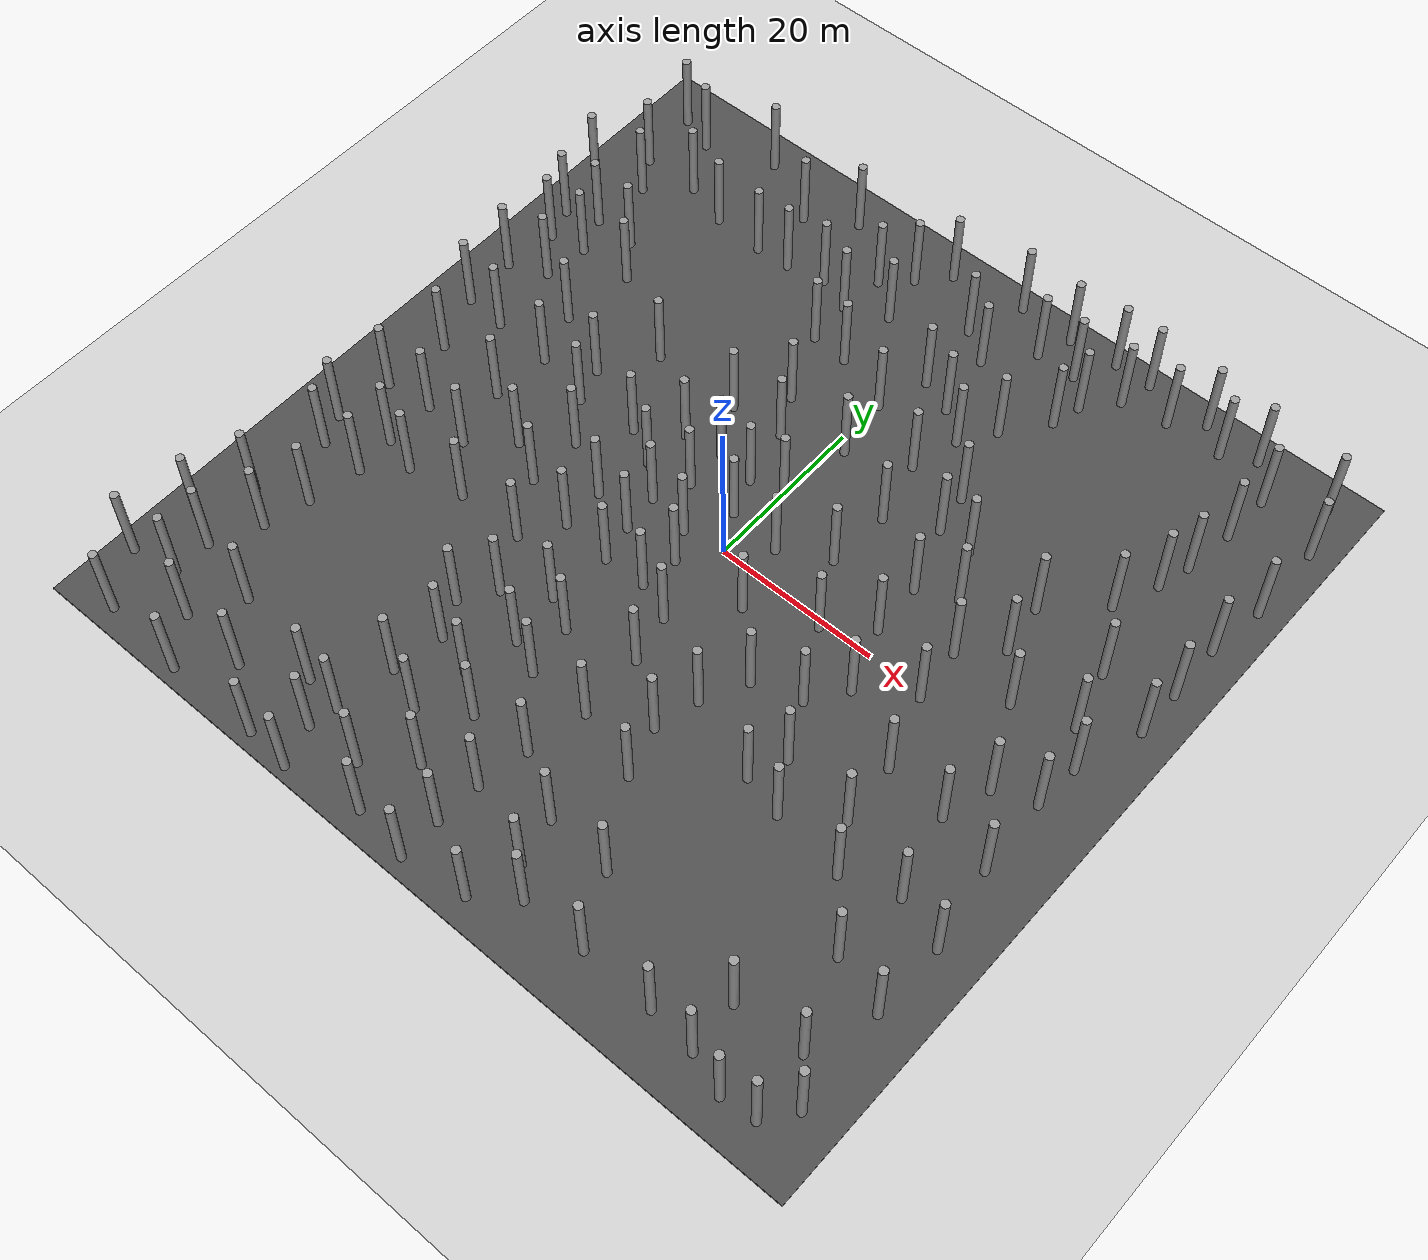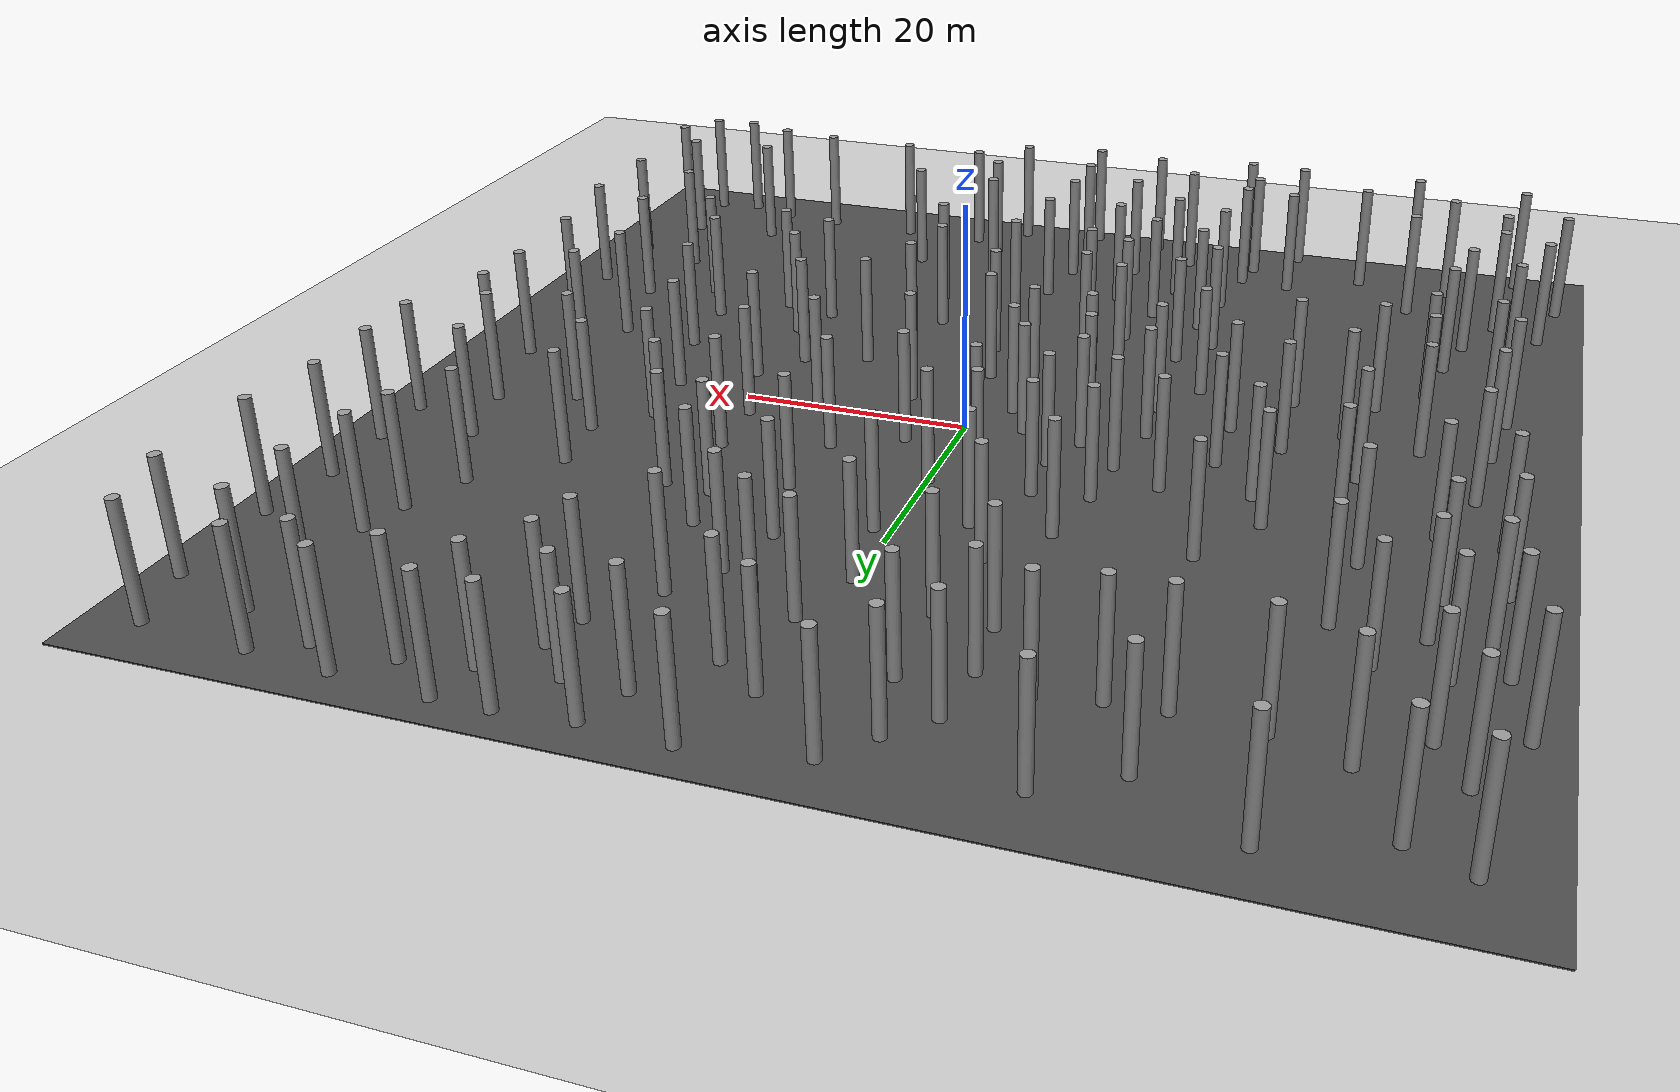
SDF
<sdf version="1.6">
 <world name="default">
  <light name="sun" type="directional">
   <pose>0 0 10 0 -0 0</pose>
   <diffuse>0.8 0.8 0.8 1</diffuse>
   <specular>0.2 0.2 0.2 1</specular>
   <attenuation>
    <range>1000</range>
    <constant>0.9</constant>
    <linear>0.01</linear>
    <quadratic>0.001</quadratic>
   </attenuation>
   <direction>-0.5 0.1 -0.9</direction>
  </light>
  <model name="ground_plane">
   <static>1</static>
   <link name="link">
    <collision name="collision">
     <geometry><plane><normal>0 0 1</normal><size>100 100</size></plane></geometry>
     <surface><friction><ode><mu>100</mu><mu2>50</mu2></ode></friction></surface>
    </collision>
    <visual name="visual">
     <cast_shadows>0</cast_shadows>
     <geometry><plane><normal>0 0 1</normal><size>100 100</size></plane></geometry>
     <material>
      <script><uri>file://media/materials/scripts/gazebo.material</uri><name>Gazebo/Grey</name></script>
     </material>
    </visual>
   </link>
  </model>
  <gravity>0 0 -9.8</gravity>
  <magnetic_field>6e-06 2.3e-05 -4.2e-05</magnetic_field>
  <atmosphere type="adiabatic"/>
  <physics name="default_physics" default="0" type="ode">
   <max_step_size>0.001</max_step_size>
   <real_time_factor>1</real_time_factor>
   <real_time_update_rate>1000</real_time_update_rate>
  </physics>
  <scene><ambient>0.4 0.4 0.4 1</ambient><background>0.7 0.7 0.7 1</background><shadows>1</shadows></scene>
  <spherical_coordinates>
   <surface_model>EARTH_WGS84</surface_model>
   <latitude_deg>0</latitude_deg>
   <longitude_deg>0</longitude_deg>
   <elevation>0</elevation>
   <heading_deg>0</heading_deg>
  </spherical_coordinates>
  <model name="asphalt_plane">
   <static>1</static>
   <link name="link">
    <collision name="collision"><geometry><box><size>100 100 0.1</size></box></geometry></collision>
    <visual name="visual">
     <cast_shadows>0</cast_shadows>
     <geometry><box><size>100 100 0.1</size></box></geometry>
     <material>
      <script>
       <uri>model://asphalt_plane/materials/scripts</uri>
       <uri>model://asphalt_plane/materials/textures</uri>
       <name>vrc/asphalt</name>
      </script>
     </material>
    </visual>
   </link>
   <pose>0.078502 0.417861 0 0 -0 0</pose>
  </model>
  <model name="forest">
   <link name="link_clone_0">
    <pose>-4.40219 0.125929 0 0 -0 0</pose>
    <inertial>
     <mass>1000</mass>
     <inertia><ixx>0.145833</ixx><ixy>0</ixy><ixz>0</ixz><iyy>0.145833</iyy><iyz>0</iyz><izz>0.125</izz></inertia>
     <pose>0 0 5 0 -0 0</pose>
    </inertial>
    <visual name="visual">
     <geometry><cylinder><radius>0.5</radius><length>10</length></cylinder></geometry>
     <material>
      <script><name>Gazebo/Grey</name><uri>file://media/materials/scripts/gazebo.material</uri></script>
      <ambient>0.3 0.3 0.3 1</ambient>
      <diffuse>0.7 0.7 0.7 1</diffuse>
      <specular>0.01 0.01 0.01 1</specular>
      <emissive>0 0 0 1</emissive>
      <shader type="vertex"><normal_map>__default__</normal_map></shader>
     </material>
     <pose>0 0 5 0 -0 0</pose>
    </visual>
    <collision name="collision">
     <pose>0 0 5 0 -0 0</pose>
     <geometry><cylinder><radius>0.5</radius><length>10</length></cylinder></geometry>
     <surface>
      <friction>
       <ode><mu>1</mu><mu2>1</mu2><fdir1>0 0 0</fdir1><slip1>0</slip1><slip2>0</slip2></ode>
       <torsional>
        <coefficient>1</coefficient>
        <patch_radius>0</patch_radius>
        <surface_radius>0</surface_radius>
        <use_patch_radius>1</use_patch_radius>
        <ode><slip>0</slip></ode>
       </torsional>
      </friction>
      <bounce><restitution_coefficient>0</restitution_coefficient><threshold>1e+06</threshold></bounce>
      <contact>
       <collide_without_contact>0</collide_without_contact>
       <collide_without_contact_bitmask>1</collide_without_contact_bitmask>
       <collide_bitmask>1</collide_bitmask>
       <ode>
        <soft_cfm>0</soft_cfm>
        <soft_erp>0.2</soft_erp>
        <kp>1e+13</kp>
        <kd>1</kd>
        <max_vel>0.01</max_vel>
        <min_depth>0</min_depth>
       </ode>
       <bullet>
        <split_impulse>1</split_impulse>
        <split_impulse_penetration_threshold>-0.01</split_impulse_penetration_threshold>
        <soft_cfm>0</soft_cfm>
        <soft_erp>0.2</soft_erp>
        <kp>1e+13</kp>
        <kd>1</kd>
       </bullet>
      </contact>
     </surface>
    </collision>
   </link>
   <link name="link_clone_10">
    <pose>-8.12738 -7.98747 0 0 -0 0</pose>
    <inertial>
     <mass>1000</mass>
     <inertia><ixx>0.145833</ixx><ixy>0</ixy><ixz>0</ixz><iyy>0.145833</iyy><iyz>0</iyz><izz>0.125</izz></inertia>
     <pose>0 0 5 0 -0 0</pose>
    </inertial>
    <visual name="visual">
     <geometry><cylinder><radius>0.5</radius><length>10</length></cylinder></geometry>
     <material>
      <script><name>Gazebo/Grey</name><uri>file://media/materials/scripts/gazebo.material</uri></script>
      <ambient>0.3 0.3 0.3 1</ambient>
      <diffuse>0.7 0.7 0.7 1</diffuse>
      <specular>0.01 0.01 0.01 1</specular>
      <emissive>0 0 0 1</emissive>
      <shader type="vertex"><normal_map>__default__</normal_map></shader>
     </material>
     <pose>0 0 5 0 -0 0</pose>
    </visual>
    <collision name="collision">
     <pose>0 0 5 0 -0 0</pose>
     <geometry><cylinder><radius>0.5</radius><length>10</length></cylinder></geometry>
     <surface>
      <friction>
       <ode><mu>1</mu><mu2>1</mu2><fdir1>0 0 0</fdir1><slip1>0</slip1><slip2>0</slip2></ode>
       <torsional>
        <coefficient>1</coefficient>
        <patch_radius>0</patch_radius>
        <surface_radius>0</surface_radius>
        <use_patch_radius>1</use_patch_radius>
        <ode><slip>0</slip></ode>
       </torsional>
      </friction>
      <bounce><restitution_coefficient>0</restitution_coefficient><threshold>1e+06</threshold></bounce>
      <contact>
       <collide_without_contact>0</collide_without_contact>
       <collide_without_contact_bitmask>1</collide_without_contact_bitmask>
       <collide_bitmask>1</collide_bitmask>
       <ode>
        <soft_cfm>0</soft_cfm>
        <soft_erp>0.2</soft_erp>
        <kp>1e+13</kp>
        <kd>1</kd>
        <max_vel>0.01</max_vel>
        <min_depth>0</min_depth>
       </ode>
       <bullet>
        <split_impulse>1</split_impulse>
        <split_impulse_penetration_threshold>-0.01</split_impulse_penetration_threshold>
        <soft_cfm>0</soft_cfm>
        <soft_erp>0.2</soft_erp>
        <kp>1e+13</kp>
        <kd>1</kd>
       </bullet>
      </contact>
     </surface>
    </collision>
   </link>
   <link name="link_clone_11">
    <pose>-3.02208 -7.81377 -0 0 -0 0</pose>
    <inertial>
     <mass>1000</mass>
     <inertia><ixx>0.145833</ixx><ixy>0</ixy><ixz>0</ixz><iyy>0.145833</iyy><iyz>0</iyz><izz>0.125</izz></inertia>
     <pose>0 0 5 0 -0 0</pose>
    </inertial>
    <visual name="visual">
     <geometry><cylinder><radius>0.5</radius><length>10</length></cylinder></geometry>
     <material>
      <script><name>Gazebo/Grey</name><uri>file://media/materials/scripts/gazebo.material</uri></script>
      <ambient>0.3 0.3 0.3 1</ambient>
      <diffuse>0.7 0.7 0.7 1</diffuse>
      <specular>0.01 0.01 0.01 1</specular>
      <emissive>0 0 0 1</emissive>
      <shader type="vertex"><normal_map>__default__</normal_map></shader>
     </material>
     <pose>0 0 5 0 -0 0</pose>
    </visual>
    <collision name="collision">
     <pose>0 0 5 0 -0 0</pose>
     <geometry><cylinder><radius>0.5</radius><length>10</length></cylinder></geometry>
     <surface>
      <friction>
       <ode><mu>1</mu><mu2>1</mu2><fdir1>0 0 0</fdir1><slip1>0</slip1><slip2>0</slip2></ode>
       <torsional>
        <coefficient>1</coefficient>
        <patch_radius>0</patch_radius>
        <surface_radius>0</surface_radius>
        <use_patch_radius>1</use_patch_radius>
        <ode><slip>0</slip></ode>
       </torsional>
      </friction>
      <bounce><restitution_coefficient>0</restitution_coefficient><threshold>1e+06</threshold></bounce>
      <contact>
       <collide_without_contact>0</collide_without_contact>
       <collide_without_contact_bitmask>1</collide_without_contact_bitmask>
       <collide_bitmask>1</collide_bitmask>
       <ode>
        <soft_cfm>0</soft_cfm>
        <soft_erp>0.2</soft_erp>
        <kp>1e+13</kp>
        <kd>1</kd>
        <max_vel>0.01</max_vel>
        <min_depth>0</min_depth>
       </ode>
       <bullet>
        <split_impulse>1</split_impulse>
        <split_impulse_penetration_threshold>-0.01</split_impulse_penetration_threshold>
        <soft_cfm>0</soft_cfm>
        <soft_erp>0.2</soft_erp>
        <kp>1e+13</kp>
        <kd>1</kd>
       </bullet>
      </contact>
     </surface>
    </collision>
   </link>
   <link name="link_clone_12">
    <pose>-8.00475 10.3672 0 0 -0 0</pose>
    <inertial>
     <mass>1000</mass>
     <inertia><ixx>0.145833</ixx><ixy>0</ixy><ixz>0</ixz><iyy>0.145833</iyy><iyz>0</iyz><izz>0.125</izz></inertia>
     <pose>0 0 5 0 -0 0</pose>
    </inertial>
    <visual name="visual">
     <geometry><cylinder><radius>0.5</radius><length>10</length></cylinder></geometry>
     <material>
      <script><name>Gazebo/Grey</name><uri>file://media/materials/scripts/gazebo.material</uri></script>
      <ambient>0.3 0.3 0.3 1</ambient>
      <diffuse>0.7 0.7 0.7 1</diffuse>
      <specular>0.01 0.01 0.01 1</specular>
      <emissive>0 0 0 1</emissive>
      <shader type="vertex"><normal_map>__default__</normal_map></shader>
     </material>
     <pose>0 0 5 0 -0 0</pose>
    </visual>
    <collision name="collision">
     <pose>0 0 5 0 -0 0</pose>
     <geometry><cylinder><radius>0.5</radius><length>10</length></cylinder></geometry>
     <surface>
      <friction>
       <ode><mu>1</mu><mu2>1</mu2><fdir1>0 0 0</fdir1><slip1>0</slip1><slip2>0</slip2></ode>
       <torsional>
        <coefficient>1</coefficient>
        <patch_radius>0</patch_radius>
        <surface_radius>0</surface_radius>
        <use_patch_radius>1</use_patch_radius>
        <ode><slip>0</slip></ode>
       </torsional>
      </friction>
      <bounce><restitution_coefficient>0</restitution_coefficient><threshold>1e+06</threshold></bounce>
      <contact>
       <collide_without_contact>0</collide_without_contact>
       <collide_without_contact_bitmask>1</collide_without_contact_bitmask>
       <collide_bitmask>1</collide_bitmask>
       <ode>
        <soft_cfm>0</soft_cfm>
        <soft_erp>0.2</soft_erp>
        <kp>1e+13</kp>
        <kd>1</kd>
        <max_vel>0.01</max_vel>
        <min_depth>0</min_depth>
       </ode>
       <bullet>
        <split_impulse>1</split_impulse>
        <split_impulse_penetration_threshold>-0.01</split_impulse_penetration_threshold>
        <soft_cfm>0</soft_cfm>
        <soft_erp>0.2</soft_erp>
        <kp>1e+13</kp>
        <kd>1</kd>
       </bullet>
      </contact>
     </surface>
    </collision>
   </link>
   <link name="link_clone_13">
    <pose>-3.35264 9.78406 0 0 -0 0</pose>
    <inertial>
     <mass>1000</mass>
     <inertia><ixx>0.145833</ixx><ixy>0</ixy><ixz>0</ixz><iyy>0.145833</iyy><iyz>0</iyz><izz>0.125</izz></inertia>
     <pose>0 0 5 0 -0 0</pose>
    </inertial>
    <visual name="visual">
     <geometry><cylinder><radius>0.5</radius><length>10</length></cylinder></geometry>
     <material>
      <script><name>Gazebo/Grey</name><uri>file://media/materials/scripts/gazebo.material</uri></script>
      <ambient>0.3 0.3 0.3 1</ambient>
      <diffuse>0.7 0.7 0.7 1</diffuse>
      <specular>0.01 0.01 0.01 1</specular>
      <emissive>0 0 0 1</emissive>
      <shader type="vertex"><normal_map>__default__</normal_map></shader>
     </material>
     <pose>0 0 5 0 -0 0</pose>
    </visual>
    <collision name="collision">
     <pose>0 0 5 0 -0 0</pose>
     <geometry><cylinder><radius>0.5</radius><length>10</length></cylinder></geometry>
     <surface>
      <friction>
       <ode><mu>1</mu><mu2>1</mu2><fdir1>0 0 0</fdir1><slip1>0</slip1><slip2>0</slip2></ode>
       <torsional>
        <coefficient>1</coefficient>
        <patch_radius>0</patch_radius>
        <surface_radius>0</surface_radius>
        <use_patch_radius>1</use_patch_radius>
        <ode><slip>0</slip></ode>
       </torsional>
      </friction>
      <bounce><restitution_coefficient>0</restitution_coefficient><threshold>1e+06</threshold></bounce>
      <contact>
       <collide_without_contact>0</collide_without_contact>
       <collide_without_contact_bitmask>1</collide_without_contact_bitmask>
       <collide_bitmask>1</collide_bitmask>
       <ode>
        <soft_cfm>0</soft_cfm>
        <soft_erp>0.2</soft_erp>
        <kp>1e+13</kp>
        <kd>1</kd>
        <max_vel>0.01</max_vel>
        <min_depth>0</min_depth>
       </ode>
       <bullet>
        <split_impulse>1</split_impulse>
        <split_impulse_penetration_threshold>-0.01</split_impulse_penetration_threshold>
        <soft_cfm>0</soft_cfm>
        <soft_erp>0.2</soft_erp>
        <kp>1e+13</kp>
        <kd>1</kd>
       </bullet>
      </contact>
     </surface>
    </collision>
   </link>
   <link name="link_clone_13_clone">
    <pose>-7.29742 21.3612 0 0 -0 0</pose>
    <inertial>
     <mass>1000</mass>
     <inertia><ixx>0.145833</ixx><ixy>0</ixy><ixz>0</ixz><iyy>0.145833</iyy><iyz>0</iyz><izz>0.125</izz></inertia>
     <pose>0 0 5 0 -0 0</pose>
    </inertial>
    <visual name="visual">
     <geometry><cylinder><radius>0.5</radius><length>10</length></cylinder></geometry>
     <material>
      <script><name>Gazebo/Grey</name><uri>file://media/materials/scripts/gazebo.material</uri></script>
      <ambient>0.3 0.3 0.3 1</ambient>
      <diffuse>0.7 0.7 0.7 1</diffuse>
      <specular>0.01 0.01 0.01 1</specular>
      <emissive>0 0 0 1</emissive>
      <shader type="vertex"><normal_map>__default__</normal_map></shader>
     </material>
     <pose>0 0 5 0 -0 0</pose>
    </visual>
    <collision name="collision">
     <pose>0 0 5 0 -0 0</pose>
     <geometry><cylinder><radius>0.5</radius><length>10</length></cylinder></geometry>
     <surface>
      <friction>
       <ode><mu>1</mu><mu2>1</mu2><fdir1>0 0 0</fdir1><slip1>0</slip1><slip2>0</slip2></ode>
       <torsional>
        <coefficient>1</coefficient>
        <patch_radius>0</patch_radius>
        <surface_radius>0</surface_radius>
        <use_patch_radius>1</use_patch_radius>
        <ode><slip>0</slip></ode>
       </torsional>
      </friction>
      <bounce><restitution_coefficient>0</restitution_coefficient><threshold>1e+06</threshold></bounce>
      <contact>
       <collide_without_contact>0</collide_without_contact>
       <collide_without_contact_bitmask>1</collide_without_contact_bitmask>
       <collide_bitmask>1</collide_bitmask>
       <ode>
        <soft_cfm>0</soft_cfm>
        <soft_erp>0.2</soft_erp>
        <kp>1e+13</kp>
        <kd>1</kd>
        <max_vel>0.01</max_vel>
        <min_depth>0</min_depth>
       </ode>
       <bullet>
        <split_impulse>1</split_impulse>
        <split_impulse_penetration_threshold>-0.01</split_impulse_penetration_threshold>
        <soft_cfm>0</soft_cfm>
        <soft_erp>0.2</soft_erp>
        <kp>1e+13</kp>
        <kd>1</kd>
       </bullet>
      </contact>
     </surface>
    </collision>
   </link>
   <link name="link_clone_13_clone_0">
    <pose>-4.89188 16.6488 0 0 -0 0</pose>
    <inertial>
     <mass>1000</mass>
     <inertia><ixx>0.145833</ixx><ixy>0</ixy><ixz>0</ixz><iyy>0.145833</iyy><iyz>0</iyz><izz>0.125</izz></inertia>
     <pose>0 0 5 0 -0 0</pose>
    </inertial>
    <visual name="visual">
     <geometry><cylinder><radius>0.5</radius><length>10</length></cylinder></geometry>
     <material>
      <script><name>Gazebo/Grey</name><uri>file://media/materials/scripts/gazebo.material</uri></script>
      <ambient>0.3 0.3 0.3 1</ambient>
      <diffuse>0.7 0.7 0.7 1</diffuse>
      <specular>0.01 0.01 0.01 1</specular>
      <emissive>0 0 0 1</emissive>
      <shader type="vertex"><normal_map>__default__</normal_map></shader>
     </material>
     <pose>0 0 5 0 -0 0</pose>
    </visual>
    <collision name="collision">
     <pose>0 0 5 0 -0 0</pose>
     <geometry><cylinder><radius>0.5</radius><length>10</length></cylinder></geometry>
     <surface>
      <friction>
       <ode><mu>1</mu><mu2>1</mu2><fdir1>0 0 0</fdir1><slip1>0</slip1><slip2>0</slip2></ode>
       <torsional>
        <coefficient>1</coefficient>
        <patch_radius>0</patch_radius>
        <surface_radius>0</surface_radius>
        <use_patch_radius>1</use_patch_radius>
        <ode><slip>0</slip></ode>
       </torsional>
      </friction>
      <bounce><restitution_coefficient>0</restitution_coefficient><threshold>1e+06</threshold></bounce>
      <contact>
       <collide_without_contact>0</collide_without_contact>
       <collide_without_contact_bitmask>1</collide_without_contact_bitmask>
       <collide_bitmask>1</collide_bitmask>
       <ode>
        <soft_cfm>0</soft_cfm>
        <soft_erp>0.2</soft_erp>
        <kp>1e+13</kp>
        <kd>1</kd>
        <max_vel>0.01</max_vel>
        <min_depth>0</min_depth>
       </ode>
       <bullet>
        <split_impulse>1</split_impulse>
        <split_impulse_penetration_threshold>-0.01</split_impulse_penetration_threshold>
        <soft_cfm>0</soft_cfm>
        <soft_erp>0.2</soft_erp>
        <kp>1e+13</kp>
        <kd>1</kd>
       </bullet>
      </contact>
     </surface>
    </collision>
   </link>
   <link name="link_clone_13_clone_1">
    <pose>-11.3149 16.1921 0 0 -0 0</pose>
    <inertial>
     <mass>1000</mass>
     <inertia><ixx>0.145833</ixx><ixy>0</ixy><ixz>0</ixz><iyy>0.145833</iyy><iyz>0</iyz><izz>0.125</izz></inertia>
     <pose>0 0 5 0 -0 0</pose>
    </inertial>
    <visual name="visual">
     <geometry><cylinder><radius>0.5</radius><length>10</length></cylinder></geometry>
     <material>
      <script><name>Gazebo/Grey</name><uri>file://media/materials/scripts/gazebo.material</uri></script>
      <ambient>0.3 0.3 0.3 1</ambient>
      <diffuse>0.7 0.7 0.7 1</diffuse>
      <specular>0.01 0.01 0.01 1</specular>
      <emissive>0 0 0 1</emissive>
      <shader type="vertex"><normal_map>__default__</normal_map></shader>
     </material>
     <pose>0 0 5 0 -0 0</pose>
    </visual>
    <collision name="collision">
     <pose>0 0 5 0 -0 0</pose>
     <geometry><cylinder><radius>0.5</radius><length>10</length></cylinder></geometry>
     <surface>
      <friction>
       <ode><mu>1</mu><mu2>1</mu2><fdir1>0 0 0</fdir1><slip1>0</slip1><slip2>0</slip2></ode>
       <torsional>
        <coefficient>1</coefficient>
        <patch_radius>0</patch_radius>
        <surface_radius>0</surface_radius>
        <use_patch_radius>1</use_patch_radius>
        <ode><slip>0</slip></ode>
       </torsional>
      </friction>
      <bounce><restitution_coefficient>0</restitution_coefficient><threshold>1e+06</threshold></bounce>
      <contact>
       <collide_without_contact>0</collide_without_contact>
       <collide_without_contact_bitmask>1</collide_without_contact_bitmask>
       <collide_bitmask>1</collide_bitmask>
       <ode>
        <soft_cfm>0</soft_cfm>
        <soft_erp>0.2</soft_erp>
        <kp>1e+13</kp>
        <kd>1</kd>
        <max_vel>0.01</max_vel>
        <min_depth>0</min_depth>
       </ode>
       <bullet>
        <split_impulse>1</split_impulse>
        <split_impulse_penetration_threshold>-0.01</split_impulse_penetration_threshold>
        <soft_cfm>0</soft_cfm>
        <soft_erp>0.2</soft_erp>
        <kp>1e+13</kp>
        <kd>1</kd>
       </bullet>
      </contact>
     </surface>
    </collision>
   </link>
   <link name="link_clone_13_clone_100">
    <pose>1.72388 -30.1957 -0 0 -0 0</pose>
    <inertial>
     <mass>1000</mass>
     <inertia><ixx>0.145833</ixx><ixy>0</ixy><ixz>0</ixz><iyy>0.145833</iyy><iyz>0</iyz><izz>0.125</izz></inertia>
     <pose>0 0 5 0 -0 0</pose>
    </inertial>
    <visual name="visual">
     <geometry><cylinder><radius>0.5</radius><length>10</length></cylinder></geometry>
     <material>
      <script><name>Gazebo/Grey</name><uri>file://media/materials/scripts/gazebo.material</uri></script>
      <ambient>0.3 0.3 0.3 1</ambient>
      <diffuse>0.7 0.7 0.7 1</diffuse>
      <specular>0.01 0.01 0.01 1</specular>
      <emissive>0 0 0 1</emissive>
      <shader type="vertex"><normal_map>__default__</normal_map></shader>
     </material>
     <pose>0 0 5 0 -0 0</pose>
    </visual>
    <collision name="collision">
     <pose>0 0 5 0 -0 0</pose>
     <geometry><cylinder><radius>0.5</radius><length>10</length></cylinder></geometry>
     <surface>
      <friction>
       <ode><mu>1</mu><mu2>1</mu2><fdir1>0 0 0</fdir1><slip1>0</slip1><slip2>0</slip2></ode>
       <torsional>
        <coefficient>1</coefficient>
        <patch_radius>0</patch_radius>
        <surface_radius>0</surface_radius>
        <use_patch_radius>1</use_patch_radius>
        <ode><slip>0</slip></ode>
       </torsional>
      </friction>
      <bounce><restitution_coefficient>0</restitution_coefficient><threshold>1e+06</threshold></bounce>
      <contact>
       <collide_without_contact>0</collide_without_contact>
       <collide_without_contact_bitmask>1</collide_without_contact_bitmask>
       <collide_bitmask>1</collide_bitmask>
       <ode>
        <soft_cfm>0</soft_cfm>
        <soft_erp>0.2</soft_erp>
        <kp>1e+13</kp>
        <kd>1</kd>
        <max_vel>0.01</max_vel>
        <min_depth>0</min_depth>
       </ode>
       <bullet>
        <split_impulse>1</split_impulse>
        <split_impulse_penetration_threshold>-0.01</split_impulse_penetration_threshold>
        <soft_cfm>0</soft_cfm>
        <soft_erp>0.2</soft_erp>
        <kp>1e+13</kp>
        <kd>1</kd>
       </bullet>
      </contact>
     </surface>
    </collision>
   </link>
   <link name="link_clone_13_clone_101">
    <pose>3.1313 -23.1957 -0 0 -0 0</pose>
    <inertial>
     <mass>1000</mass>
     <inertia><ixx>0.145833</ixx><ixy>0</ixy><ixz>0</ixz><iyy>0.145833</iyy><iyz>0</iyz><izz>0.125</izz></inertia>
     <pose>0 0 5 0 -0 0</pose>
    </inertial>
    <visual name="visual">
     <geometry><cylinder><radius>0.5</radius><length>10</length></cylinder></geometry>
     <material>
      <script><name>Gazebo/Grey</name><uri>file://media/materials/scripts/gazebo.material</uri></script>
      <ambient>0.3 0.3 0.3 1</ambient>
      <diffuse>0.7 0.7 0.7 1</diffuse>
      <specular>0.01 0.01 0.01 1</specular>
      <emissive>0 0 0 1</emissive>
      <shader type="vertex"><normal_map>__default__</normal_map></shader>
     </material>
     <pose>0 0 5 0 -0 0</pose>
    </visual>
    <collision name="collision">
     <pose>0 0 5 0 -0 0</pose>
     <geometry><cylinder><radius>0.5</radius><length>10</length></cylinder></geometry>
     <surface>
      <friction>
       <ode><mu>1</mu><mu2>1</mu2><fdir1>0 0 0</fdir1><slip1>0</slip1><slip2>0</slip2></ode>
       <torsional>
        <coefficient>1</coefficient>
        <patch_radius>0</patch_radius>
        <surface_radius>0</surface_radius>
        <use_patch_radius>1</use_patch_radius>
        <ode><slip>0</slip></ode>
       </torsional>
      </friction>
      <bounce><restitution_coefficient>0</restitution_coefficient><threshold>1e+06</threshold></bounce>
      <contact>
       <collide_without_contact>0</collide_without_contact>
       <collide_without_contact_bitmask>1</collide_without_contact_bitmask>
       <collide_bitmask>1</collide_bitmask>
       <ode>
        <soft_cfm>0</soft_cfm>
        <soft_erp>0.2</soft_erp>
        <kp>1e+13</kp>
        <kd>1</kd>
        <max_vel>0.01</max_vel>
        <min_depth>0</min_depth>
       </ode>
       <bullet>
        <split_impulse>1</split_impulse>
        <split_impulse_penetration_threshold>-0.01</split_impulse_penetration_threshold>
        <soft_cfm>0</soft_cfm>
        <soft_erp>0.2</soft_erp>
        <kp>1e+13</kp>
        <kd>1</kd>
       </bullet>
      </contact>
     </surface>
    </collision>
   </link>
   <link name="link_clone_13_clone_102">
    <pose>2.72388 -15.1957 -0 0 -0 0</pose>
    <inertial>
     <mass>1000</mass>
     <inertia><ixx>0.145833</ixx><ixy>0</ixy><ixz>0</ixz><iyy>0.145833</iyy><iyz>0</iyz><izz>0.125</izz></inertia>
     <pose>0 0 5 0 -0 0</pose>
    </inertial>
    <visual name="visual">
     <geometry><cylinder><radius>0.5</radius><length>10</length></cylinder></geometry>
     <material>
      <script><name>Gazebo/Grey</name><uri>file://media/materials/scripts/gazebo.material</uri></script>
      <ambient>0.3 0.3 0.3 1</ambient>
      <diffuse>0.7 0.7 0.7 1</diffuse>
      <specular>0.01 0.01 0.01 1</specular>
      <emissive>0 0 0 1</emissive>
      <shader type="vertex"><normal_map>__default__</normal_map></shader>
     </material>
     <pose>0 0 5 0 -0 0</pose>
    </visual>
    <collision name="collision">
     <pose>0 0 5 0 -0 0</pose>
     <geometry><cylinder><radius>0.5</radius><length>10</length></cylinder></geometry>
     <surface>
      <friction>
       <ode><mu>1</mu><mu2>1</mu2><fdir1>0 0 0</fdir1><slip1>0</slip1><slip2>0</slip2></ode>
       <torsional>
        <coefficient>1</coefficient>
        <patch_radius>0</patch_radius>
        <surface_radius>0</surface_radius>
        <use_patch_radius>1</use_patch_radius>
        <ode><slip>0</slip></ode>
       </torsional>
      </friction>
      <bounce><restitution_coefficient>0</restitution_coefficient><threshold>1e+06</threshold></bounce>
      <contact>
       <collide_without_contact>0</collide_without_contact>
       <collide_without_contact_bitmask>1</collide_without_contact_bitmask>
       <collide_bitmask>1</collide_bitmask>
       <ode>
        <soft_cfm>0</soft_cfm>
        <soft_erp>0.2</soft_erp>
        <kp>1e+13</kp>
        <kd>1</kd>
        <max_vel>0.01</max_vel>
        <min_depth>0</min_depth>
       </ode>
       <bullet>
        <split_impulse>1</split_impulse>
        <split_impulse_penetration_threshold>-0.01</split_impulse_penetration_threshold>
        <soft_cfm>0</soft_cfm>
        <soft_erp>0.2</soft_erp>
        <kp>1e+13</kp>
        <kd>1</kd>
       </bullet>
      </contact>
     </surface>
    </collision>
   </link>
   <link name="link_clone_13_clone_103">
    <pose>10.7239 -14.6551 -0 0 -0 0</pose>
    <inertial>
     <mass>1000</mass>
     <inertia><ixx>0.145833</ixx><ixy>0</ixy><ixz>0</ixz><iyy>0.145833</iyy><iyz>0</iyz><izz>0.125</izz></inertia>
     <pose>0 0 5 0 -0 0</pose>
    </inertial>
    <visual name="visual">
     <geometry><cylinder><radius>0.5</radius><length>10</length></cylinder></geometry>
     <material>
      <script><name>Gazebo/Grey</name><uri>file://media/materials/scripts/gazebo.material</uri></script>
      <ambient>0.3 0.3 0.3 1</ambient>
      <diffuse>0.7 0.7 0.7 1</diffuse>
      <specular>0.01 0.01 0.01 1</specular>
      <emissive>0 0 0 1</emissive>
      <shader type="vertex"><normal_map>__default__</normal_map></shader>
     </material>
     <pose>0 0 5 0 -0 0</pose>
    </visual>
    <collision name="collision">
     <pose>0 0 5 0 -0 0</pose>
     <geometry><cylinder><radius>0.5</radius><length>10</length></cylinder></geometry>
     <surface>
      <friction>
       <ode><mu>1</mu><mu2>1</mu2><fdir1>0 0 0</fdir1><slip1>0</slip1><slip2>0</slip2></ode>
       <torsional>
        <coefficient>1</coefficient>
        <patch_radius>0</patch_radius>
        <surface_radius>0</surface_radius>
        <use_patch_radius>1</use_patch_radius>
        <ode><slip>0</slip></ode>
       </torsional>
      </friction>
      <bounce><restitution_coefficient>0</restitution_coefficient><threshold>1e+06</threshold></bounce>
      <contact>
       <collide_without_contact>0</collide_without_contact>
       <collide_without_contact_bitmask>1</collide_without_contact_bitmask>
       <collide_bitmask>1</collide_bitmask>
       <ode>
        <soft_cfm>0</soft_cfm>
        <soft_erp>0.2</soft_erp>
        <kp>1e+13</kp>
        <kd>1</kd>
        <max_vel>0.01</max_vel>
        <min_depth>0</min_depth>
       </ode>
       <bullet>
        <split_impulse>1</split_impulse>
        <split_impulse_penetration_threshold>-0.01</split_impulse_penetration_threshold>
        <soft_cfm>0</soft_cfm>
        <soft_erp>0.2</soft_erp>
        <kp>1e+13</kp>
        <kd>1</kd>
       </bullet>
      </contact>
     </surface>
    </collision>
   </link>
   <link name="link_clone_13_clone_104">
    <pose>9.42712 -19.8713 -0 0 -0 0</pose>
    <inertial>
     <mass>1000</mass>
     <inertia><ixx>0.145833</ixx><ixy>0</ixy><ixz>0</ixz><iyy>0.145833</iyy><iyz>0</iyz><izz>0.125</izz></inertia>
     <pose>0 0 5 0 -0 0</pose>
    </inertial>
    <visual name="visual">
     <geometry><cylinder><radius>0.5</radius><length>10</length></cylinder></geometry>
     <material>
      <script><name>Gazebo/Grey</name><uri>file://media/materials/scripts/gazebo.material</uri></script>
      <ambient>0.3 0.3 0.3 1</ambient>
      <diffuse>0.7 0.7 0.7 1</diffuse>
      <specular>0.01 0.01 0.01 1</specular>
      <emissive>0 0 0 1</emissive>
      <shader type="vertex"><normal_map>__default__</normal_map></shader>
     </material>
     <pose>0 0 5 0 -0 0</pose>
    </visual>
    <collision name="collision">
     <pose>0 0 5 0 -0 0</pose>
     <geometry><cylinder><radius>0.5</radius><length>10</length></cylinder></geometry>
     <surface>
      <friction>
       <ode><mu>1</mu><mu2>1</mu2><fdir1>0 0 0</fdir1><slip1>0</slip1><slip2>0</slip2></ode>
       <torsional>
        <coefficient>1</coefficient>
        <patch_radius>0</patch_radius>
        <surface_radius>0</surface_radius>
        <use_patch_radius>1</use_patch_radius>
        <ode><slip>0</slip></ode>
       </torsional>
      </friction>
      <bounce><restitution_coefficient>0</restitution_coefficient><threshold>1e+06</threshold></bounce>
      <contact>
       <collide_without_contact>0</collide_without_contact>
       <collide_without_contact_bitmask>1</collide_without_contact_bitmask>
       <collide_bitmask>1</collide_bitmask>
       <ode>
        <soft_cfm>0</soft_cfm>
        <soft_erp>0.2</soft_erp>
        <kp>1e+13</kp>
        <kd>1</kd>
        <max_vel>0.01</max_vel>
        <min_depth>0</min_depth>
       </ode>
       <bullet>
        <split_impulse>1</split_impulse>
        <split_impulse_penetration_threshold>-0.01</split_impulse_penetration_threshold>
        <soft_cfm>0</soft_cfm>
        <soft_erp>0.2</soft_erp>
        <kp>1e+13</kp>
        <kd>1</kd>
       </bullet>
      </contact>
     </surface>
    </collision>
   </link>
   <link name="link_clone_13_clone_105">
    <pose>11.1904 -25.644 -0 0 -0 0</pose>
    <inertial>
     <mass>1000</mass>
     <inertia><ixx>0.145833</ixx><ixy>0</ixy><ixz>0</ixz><iyy>0.145833</iyy><iyz>0</iyz><izz>0.125</izz></inertia>
     <pose>0 0 5 0 -0 0</pose>
    </inertial>
    <visual name="visual">
     <geometry><cylinder><radius>0.5</radius><length>10</length></cylinder></geometry>
     <material>
      <script><name>Gazebo/Grey</name><uri>file://media/materials/scripts/gazebo.material</uri></script>
      <ambient>0.3 0.3 0.3 1</ambient>
      <diffuse>0.7 0.7 0.7 1</diffuse>
      <specular>0.01 0.01 0.01 1</specular>
      <emissive>0 0 0 1</emissive>
      <shader type="vertex"><normal_map>__default__</normal_map></shader>
     </material>
     <pose>0 0 5 0 -0 0</pose>
    </visual>
    <collision name="collision">
     <pose>0 0 5 0 -0 0</pose>
     <geometry><cylinder><radius>0.5</radius><length>10</length></cylinder></geometry>
     <surface>
      <friction>
       <ode><mu>1</mu><mu2>1</mu2><fdir1>0 0 0</fdir1><slip1>0</slip1><slip2>0</slip2></ode>
       <torsional>
        <coefficient>1</coefficient>
        <patch_radius>0</patch_radius>
        <surface_radius>0</surface_radius>
        <use_patch_radius>1</use_patch_radius>
        <ode><slip>0</slip></ode>
       </torsional>
      </friction>
      <bounce><restitution_coefficient>0</restitution_coefficient><threshold>1e+06</threshold></bounce>
      <contact>
       <collide_without_contact>0</collide_without_contact>
       <collide_without_contact_bitmask>1</collide_without_contact_bitmask>
       <collide_bitmask>1</collide_bitmask>
       <ode>
        <soft_cfm>0</soft_cfm>
        <soft_erp>0.2</soft_erp>
        <kp>1e+13</kp>
        <kd>1</kd>
        <max_vel>0.01</max_vel>
        <min_depth>0</min_depth>
       </ode>
       <bullet>
        <split_impulse>1</split_impulse>
        <split_impulse_penetration_threshold>-0.01</split_impulse_penetration_threshold>
        <soft_cfm>0</soft_cfm>
        <soft_erp>0.2</soft_erp>
        <kp>1e+13</kp>
        <kd>1</kd>
       </bullet>
      </contact>
     </surface>
    </collision>
   </link>
   <link name="link_clone_13_clone_106">
    <pose>8.72388 -34.1957 -0 0 -0 0</pose>
    <inertial>
     <mass>1000</mass>
     <inertia><ixx>0.145833</ixx><ixy>0</ixy><ixz>0</ixz><iyy>0.145833</iyy><iyz>0</iyz><izz>0.125</izz></inertia>
     <pose>0 0 5 0 -0 0</pose>
    </inertial>
    <visual name="visual">
     <geometry><cylinder><radius>0.5</radius><length>10</length></cylinder></geometry>
     <material>
      <script><name>Gazebo/Grey</name><uri>file://media/materials/scripts/gazebo.material</uri></script>
      <ambient>0.3 0.3 0.3 1</ambient>
      <diffuse>0.7 0.7 0.7 1</diffuse>
      <specular>0.01 0.01 0.01 1</specular>
      <emissive>0 0 0 1</emissive>
      <shader type="vertex"><normal_map>__default__</normal_map></shader>
     </material>
     <pose>0 0 5 0 -0 0</pose>
    </visual>
    <collision name="collision">
     <pose>0 0 5 0 -0 0</pose>
     <geometry><cylinder><radius>0.5</radius><length>10</length></cylinder></geometry>
     <surface>
      <friction>
       <ode><mu>1</mu><mu2>1</mu2><fdir1>0 0 0</fdir1><slip1>0</slip1><slip2>0</slip2></ode>
       <torsional>
        <coefficient>1</coefficient>
        <patch_radius>0</patch_radius>
        <surface_radius>0</surface_radius>
        <use_patch_radius>1</use_patch_radius>
        <ode><slip>0</slip></ode>
       </torsional>
      </friction>
      <bounce><restitution_coefficient>0</restitution_coefficient><threshold>1e+06</threshold></bounce>
      <contact>
       <collide_without_contact>0</collide_without_contact>
       <collide_without_contact_bitmask>1</collide_without_contact_bitmask>
       <collide_bitmask>1</collide_bitmask>
       <ode>
        <soft_cfm>0</soft_cfm>
        <soft_erp>0.2</soft_erp>
        <kp>1e+13</kp>
        <kd>1</kd>
        <max_vel>0.01</max_vel>
        <min_depth>0</min_depth>
       </ode>
       <bullet>
        <split_impulse>1</split_impulse>
        <split_impulse_penetration_threshold>-0.01</split_impulse_penetration_threshold>
        <soft_cfm>0</soft_cfm>
        <soft_erp>0.2</soft_erp>
        <kp>1e+13</kp>
        <kd>1</kd>
       </bullet>
      </contact>
     </surface>
    </collision>
   </link>
   <link name="link_clone_13_clone_107">
    <pose>12.7239 -42.1957 -0 0 -0 0</pose>
    <inertial>
     <mass>1000</mass>
     <inertia><ixx>0.145833</ixx><ixy>0</ixy><ixz>0</ixz><iyy>0.145833</iyy><iyz>0</iyz><izz>0.125</izz></inertia>
     <pose>0 0 5 0 -0 0</pose>
    </inertial>
    <visual name="visual">
     <geometry><cylinder><radius>0.5</radius><length>10</length></cylinder></geometry>
     <material>
      <script><name>Gazebo/Grey</name><uri>file://media/materials/scripts/gazebo.material</uri></script>
      <ambient>0.3 0.3 0.3 1</ambient>
      <diffuse>0.7 0.7 0.7 1</diffuse>
      <specular>0.01 0.01 0.01 1</specular>
      <emissive>0 0 0 1</emissive>
      <shader type="vertex"><normal_map>__default__</normal_map></shader>
     </material>
     <pose>0 0 5 0 -0 0</pose>
    </visual>
    <collision name="collision">
     <pose>0 0 5 0 -0 0</pose>
     <geometry><cylinder><radius>0.5</radius><length>10</length></cylinder></geometry>
     <surface>
      <friction>
       <ode><mu>1</mu><mu2>1</mu2><fdir1>0 0 0</fdir1><slip1>0</slip1><slip2>0</slip2></ode>
       <torsional>
        <coefficient>1</coefficient>
        <patch_radius>0</patch_radius>
        <surface_radius>0</surface_radius>
        <use_patch_radius>1</use_patch_radius>
        <ode><slip>0</slip></ode>
       </torsional>
      </friction>
      <bounce><restitution_coefficient>0</restitution_coefficient><threshold>1e+06</threshold></bounce>
      <contact>
       <collide_without_contact>0</collide_without_contact>
       <collide_without_contact_bitmask>1</collide_without_contact_bitmask>
       <collide_bitmask>1</collide_bitmask>
       <ode>
        <soft_cfm>0</soft_cfm>
        <soft_erp>0.2</soft_erp>
        <kp>1e+13</kp>
        <kd>1</kd>
        <max_vel>0.01</max_vel>
        <min_depth>0</min_depth>
       </ode>
       <bullet>
        <split_impulse>1</split_impulse>
        <split_impulse_penetration_threshold>-0.01</split_impulse_penetration_threshold>
        <soft_cfm>0</soft_cfm>
        <soft_erp>0.2</soft_erp>
        <kp>1e+13</kp>
        <kd>1</kd>
       </bullet>
      </contact>
     </surface>
    </collision>
   </link>
   <link name="link_clone_13_clone_108">
    <pose>8.19096 -45.5535 -0 0 -0 0</pose>
    <inertial>
     <mass>1000</mass>
     <inertia><ixx>0.145833</ixx><ixy>0</ixy><ixz>0</ixz><iyy>0.145833</iyy><iyz>0</iyz><izz>0.125</izz></inertia>
     <pose>0 0 5 0 -0 0</pose>
    </inertial>
    <visual name="visual">
     <geometry><cylinder><radius>0.5</radius><length>10</length></cylinder></geometry>
     <material>
      <script><name>Gazebo/Grey</name><uri>file://media/materials/scripts/gazebo.material</uri></script>
      <ambient>0.3 0.3 0.3 1</ambient>
      <diffuse>0.7 0.7 0.7 1</diffuse>
      <specular>0.01 0.01 0.01 1</specular>
      <emissive>0 0 0 1</emissive>
      <shader type="vertex"><normal_map>__default__</normal_map></shader>
     </material>
     <pose>0 0 5 0 -0 0</pose>
    </visual>
    <collision name="collision">
     <pose>0 0 5 0 -0 0</pose>
     <geometry><cylinder><radius>0.5</radius><length>10</length></cylinder></geometry>
     <surface>
      <friction>
       <ode><mu>1</mu><mu2>1</mu2><fdir1>0 0 0</fdir1><slip1>0</slip1><slip2>0</slip2></ode>
       <torsional>
        <coefficient>1</coefficient>
        <patch_radius>0</patch_radius>
        <surface_radius>0</surface_radius>
        <use_patch_radius>1</use_patch_radius>
        <ode><slip>0</slip></ode>
       </torsional>
      </friction>
      <bounce><restitution_coefficient>0</restitution_coefficient><threshold>1e+06</threshold></bounce>
      <contact>
       <collide_without_contact>0</collide_without_contact>
       <collide_without_contact_bitmask>1</collide_without_contact_bitmask>
       <collide_bitmask>1</collide_bitmask>
       <ode>
        <soft_cfm>0</soft_cfm>
        <soft_erp>0.2</soft_erp>
        <kp>1e+13</kp>
        <kd>1</kd>
        <max_vel>0.01</max_vel>
        <min_depth>0</min_depth>
       </ode>
       <bullet>
        <split_impulse>1</split_impulse>
        <split_impulse_penetration_threshold>-0.01</split_impulse_penetration_threshold>
        <soft_cfm>0</soft_cfm>
        <soft_erp>0.2</soft_erp>
        <kp>1e+13</kp>
        <kd>1</kd>
       </bullet>
      </contact>
     </surface>
    </collision>
   </link>
   <link name="link_clone_13_clone_109">
    <pose>9.88383 -39.6507 -0 0 -0 0</pose>
    <inertial>
     <mass>1000</mass>
     <inertia><ixx>0.145833</ixx><ixy>0</ixy><ixz>0</ixz><iyy>0.145833</iyy><iyz>0</iyz><izz>0.125</izz></inertia>
     <pose>0 0 5 0 -0 0</pose>
    </inertial>
    <visual name="visual">
     <geometry><cylinder><radius>0.5</radius><length>10</length></cylinder></geometry>
     <material>
      <script><name>Gazebo/Grey</name><uri>file://media/materials/scripts/gazebo.material</uri></script>
      <ambient>0.3 0.3 0.3 1</ambient>
      <diffuse>0.7 0.7 0.7 1</diffuse>
      <specular>0.01 0.01 0.01 1</specular>
      <emissive>0 0 0 1</emissive>
      <shader type="vertex"><normal_map>__default__</normal_map></shader>
     </material>
     <pose>0 0 5 0 -0 0</pose>
    </visual>
    <collision name="collision">
     <pose>0 0 5 0 -0 0</pose>
     <geometry><cylinder><radius>0.5</radius><length>10</length></cylinder></geometry>
     <surface>
      <friction>
       <ode><mu>1</mu><mu2>1</mu2><fdir1>0 0 0</fdir1><slip1>0</slip1><slip2>0</slip2></ode>
       <torsional>
        <coefficient>1</coefficient>
        <patch_radius>0</patch_radius>
        <surface_radius>0</surface_radius>
        <use_patch_radius>1</use_patch_radius>
        <ode><slip>0</slip></ode>
       </torsional>
      </friction>
      <bounce><restitution_coefficient>0</restitution_coefficient><threshold>1e+06</threshold></bounce>
      <contact>
       <collide_without_contact>0</collide_without_contact>
       <collide_without_contact_bitmask>1</collide_without_contact_bitmask>
       <collide_bitmask>1</collide_bitmask>
       <ode>
        <soft_cfm>0</soft_cfm>
        <soft_erp>0.2</soft_erp>
        <kp>1e+13</kp>
        <kd>1</kd>
        <max_vel>0.01</max_vel>
        <min_depth>0</min_depth>
       </ode>
       <bullet>
        <split_impulse>1</split_impulse>
        <split_impulse_penetration_threshold>-0.01</split_impulse_penetration_threshold>
        <soft_cfm>0</soft_cfm>
        <soft_erp>0.2</soft_erp>
        <kp>1e+13</kp>
        <kd>1</kd>
       </bullet>
      </contact>
     </surface>
    </collision>
   </link>
   <link name="link_clone_13_clone_11">
    <pose>-20.1128 35.8889 0 0 -0 0</pose>
    <inertial>
     <mass>1000</mass>
     <inertia><ixx>0.145833</ixx><ixy>0</ixy><ixz>0</ixz><iyy>0.145833</iyy><iyz>0</iyz><izz>0.125</izz></inertia>
     <pose>0 0 5 0 -0 0</pose>
    </inertial>
    <visual name="visual">
     <geometry><cylinder><radius>0.5</radius><length>10</length></cylinder></geometry>
     <material>
      <script><name>Gazebo/Grey</name><uri>file://media/materials/scripts/gazebo.material</uri></script>
      <ambient>0.3 0.3 0.3 1</ambient>
      <diffuse>0.7 0.7 0.7 1</diffuse>
      <specular>0.01 0.01 0.01 1</specular>
      <emissive>0 0 0 1</emissive>
      <shader type="vertex"><normal_map>__default__</normal_map></shader>
     </material>
     <pose>0 0 5 0 -0 0</pose>
    </visual>
    <collision name="collision">
     <pose>0 0 5 0 -0 0</pose>
     <geometry><cylinder><radius>0.5</radius><length>10</length></cylinder></geometry>
     <surface>
      <friction>
       <ode><mu>1</mu><mu2>1</mu2><fdir1>0 0 0</fdir1><slip1>0</slip1><slip2>0</slip2></ode>
       <torsional>
        <coefficient>1</coefficient>
        <patch_radius>0</patch_radius>
        <surface_radius>0</surface_radius>
        <use_patch_radius>1</use_patch_radius>
        <ode><slip>0</slip></ode>
       </torsional>
      </friction>
      <bounce><restitution_coefficient>0</restitution_coefficient><threshold>1e+06</threshold></bounce>
      <contact>
       <collide_without_contact>0</collide_without_contact>
       <collide_without_contact_bitmask>1</collide_without_contact_bitmask>
       <collide_bitmask>1</collide_bitmask>
       <ode>
        <soft_cfm>0</soft_cfm>
        <soft_erp>0.2</soft_erp>
        <kp>1e+13</kp>
        <kd>1</kd>
        <max_vel>0.01</max_vel>
        <min_depth>0</min_depth>
       </ode>
       <bullet>
        <split_impulse>1</split_impulse>
        <split_impulse_penetration_threshold>-0.01</split_impulse_penetration_threshold>
        <soft_cfm>0</soft_cfm>
        <soft_erp>0.2</soft_erp>
        <kp>1e+13</kp>
        <kd>1</kd>
       </bullet>
      </contact>
     </surface>
    </collision>
   </link>
   <link name="link_clone_13_clone_110">
    <pose>16.6587 -34.7638 -0 0 -0 0</pose>
    <inertial>
     <mass>1000</mass>
     <inertia><ixx>0.145833</ixx><ixy>0</ixy><ixz>0</ixz><iyy>0.145833</iyy><iyz>0</iyz><izz>0.125</izz></inertia>
     <pose>0 0 5 0 -0 0</pose>
    </inertial>
    <visual name="visual">
     <geometry><cylinder><radius>0.5</radius><length>10</length></cylinder></geometry>
     <material>
      <script><name>Gazebo/Grey</name><uri>file://media/materials/scripts/gazebo.material</uri></script>
      <ambient>0.3 0.3 0.3 1</ambient>
      <diffuse>0.7 0.7 0.7 1</diffuse>
      <specular>0.01 0.01 0.01 1</specular>
      <emissive>0 0 0 1</emissive>
      <shader type="vertex"><normal_map>__default__</normal_map></shader>
     </material>
     <pose>0 0 5 0 -0 0</pose>
    </visual>
    <collision name="collision">
     <pose>0 0 5 0 -0 0</pose>
     <geometry><cylinder><radius>0.5</radius><length>10</length></cylinder></geometry>
     <surface>
      <friction>
       <ode><mu>1</mu><mu2>1</mu2><fdir1>0 0 0</fdir1><slip1>0</slip1><slip2>0</slip2></ode>
       <torsional>
        <coefficient>1</coefficient>
        <patch_radius>0</patch_radius>
        <surface_radius>0</surface_radius>
        <use_patch_radius>1</use_patch_radius>
        <ode><slip>0</slip></ode>
       </torsional>
      </friction>
      <bounce><restitution_coefficient>0</restitution_coefficient><threshold>1e+06</threshold></bounce>
      <contact>
       <collide_without_contact>0</collide_without_contact>
       <collide_without_contact_bitmask>1</collide_without_contact_bitmask>
       <collide_bitmask>1</collide_bitmask>
       <ode>
        <soft_cfm>0</soft_cfm>
        <soft_erp>0.2</soft_erp>
        <kp>1e+13</kp>
        <kd>1</kd>
        <max_vel>0.01</max_vel>
        <min_depth>0</min_depth>
       </ode>
       <bullet>
        <split_impulse>1</split_impulse>
        <split_impulse_penetration_threshold>-0.01</split_impulse_penetration_threshold>
        <soft_cfm>0</soft_cfm>
        <soft_erp>0.2</soft_erp>
        <kp>1e+13</kp>
        <kd>1</kd>
       </bullet>
      </contact>
     </surface>
    </collision>
   </link>
   <link name="link_clone_13_clone_111">
    <pose>20.5727 -42.2419 -0 0 -0 0</pose>
    <inertial>
     <mass>1000</mass>
     <inertia><ixx>0.145833</ixx><ixy>0</ixy><ixz>0</ixz><iyy>0.145833</iyy><iyz>0</iyz><izz>0.125</izz></inertia>
     <pose>0 0 5 0 -0 0</pose>
    </inertial>
    <visual name="visual">
     <geometry><cylinder><radius>0.5</radius><length>10</length></cylinder></geometry>
     <material>
      <script><name>Gazebo/Grey</name><uri>file://media/materials/scripts/gazebo.material</uri></script>
      <ambient>0.3 0.3 0.3 1</ambient>
      <diffuse>0.7 0.7 0.7 1</diffuse>
      <specular>0.01 0.01 0.01 1</specular>
      <emissive>0 0 0 1</emissive>
      <shader type="vertex"><normal_map>__default__</normal_map></shader>
     </material>
     <pose>0 0 5 0 -0 0</pose>
    </visual>
    <collision name="collision">
     <pose>0 0 5 0 -0 0</pose>
     <geometry><cylinder><radius>0.5</radius><length>10</length></cylinder></geometry>
     <surface>
      <friction>
       <ode><mu>1</mu><mu2>1</mu2><fdir1>0 0 0</fdir1><slip1>0</slip1><slip2>0</slip2></ode>
       <torsional>
        <coefficient>1</coefficient>
        <patch_radius>0</patch_radius>
        <surface_radius>0</surface_radius>
        <use_patch_radius>1</use_patch_radius>
        <ode><slip>0</slip></ode>
       </torsional>
      </friction>
      <bounce><restitution_coefficient>0</restitution_coefficient><threshold>1e+06</threshold></bounce>
      <contact>
       <collide_without_contact>0</collide_without_contact>
       <collide_without_contact_bitmask>1</collide_without_contact_bitmask>
       <collide_bitmask>1</collide_bitmask>
       <ode>
        <soft_cfm>0</soft_cfm>
        <soft_erp>0.2</soft_erp>
        <kp>1e+13</kp>
        <kd>1</kd>
        <max_vel>0.01</max_vel>
        <min_depth>0</min_depth>
       </ode>
       <bullet>
        <split_impulse>1</split_impulse>
        <split_impulse_penetration_threshold>-0.01</split_impulse_penetration_threshold>
        <soft_cfm>0</soft_cfm>
        <soft_erp>0.2</soft_erp>
        <kp>1e+13</kp>
        <kd>1</kd>
       </bullet>
      </contact>
     </surface>
    </collision>
   </link>
   <link name="link_clone_13_clone_114">
    <pose>29.3647 -42.4624 -0 0 -0 0</pose>
    <inertial>
     <mass>1000</mass>
     <inertia><ixx>0.145833</ixx><ixy>0</ixy><ixz>0</ixz><iyy>0.145833</iyy><iyz>0</iyz><izz>0.125</izz></inertia>
     <pose>0 0 5 0 -0 0</pose>
    </inertial>
    <visual name="visual">
     <geometry><cylinder><radius>0.5</radius><length>10</length></cylinder></geometry>
     <material>
      <script><name>Gazebo/Grey</name><uri>file://media/materials/scripts/gazebo.material</uri></script>
      <ambient>0.3 0.3 0.3 1</ambient>
      <diffuse>0.7 0.7 0.7 1</diffuse>
      <specular>0.01 0.01 0.01 1</specular>
      <emissive>0 0 0 1</emissive>
      <shader type="vertex"><normal_map>__default__</normal_map></shader>
     </material>
     <pose>0 0 5 0 -0 0</pose>
    </visual>
    <collision name="collision">
     <pose>0 0 5 0 -0 0</pose>
     <geometry><cylinder><radius>0.5</radius><length>10</length></cylinder></geometry>
     <surface>
      <friction>
       <ode><mu>1</mu><mu2>1</mu2><fdir1>0 0 0</fdir1><slip1>0</slip1><slip2>0</slip2></ode>
       <torsional>
        <coefficient>1</coefficient>
        <patch_radius>0</patch_radius>
        <surface_radius>0</surface_radius>
        <use_patch_radius>1</use_patch_radius>
        <ode><slip>0</slip></ode>
       </torsional>
      </friction>
      <bounce><restitution_coefficient>0</restitution_coefficient><threshold>1e+06</threshold></bounce>
      <contact>
       <collide_without_contact>0</collide_without_contact>
       <collide_without_contact_bitmask>1</collide_without_contact_bitmask>
       <collide_bitmask>1</collide_bitmask>
       <ode>
        <soft_cfm>0</soft_cfm>
        <soft_erp>0.2</soft_erp>
        <kp>1e+13</kp>
        <kd>1</kd>
        <max_vel>0.01</max_vel>
        <min_depth>0</min_depth>
       </ode>
       <bullet>
        <split_impulse>1</split_impulse>
        <split_impulse_penetration_threshold>-0.01</split_impulse_penetration_threshold>
        <soft_cfm>0</soft_cfm>
        <soft_erp>0.2</soft_erp>
        <kp>1e+13</kp>
        <kd>1</kd>
       </bullet>
      </contact>
     </surface>
    </collision>
   </link>
   <link name="link_clone_13_clone_116">
    <pose>34.7943 -37.0042 -0 0 -0 0</pose>
    <inertial>
     <mass>1000</mass>
     <inertia><ixx>0.145833</ixx><ixy>0</ixy><ixz>0</ixz><iyy>0.145833</iyy><iyz>0</iyz><izz>0.125</izz></inertia>
     <pose>0 0 5 0 -0 0</pose>
    </inertial>
    <visual name="visual">
     <geometry><cylinder><radius>0.5</radius><length>10</length></cylinder></geometry>
     <material>
      <script><name>Gazebo/Grey</name><uri>file://media/materials/scripts/gazebo.material</uri></script>
      <ambient>0.3 0.3 0.3 1</ambient>
      <diffuse>0.7 0.7 0.7 1</diffuse>
      <specular>0.01 0.01 0.01 1</specular>
      <emissive>0 0 0 1</emissive>
      <shader type="vertex"><normal_map>__default__</normal_map></shader>
     </material>
     <pose>0 0 5 0 -0 0</pose>
    </visual>
    <collision name="collision">
     <pose>0 0 5 0 -0 0</pose>
     <geometry><cylinder><radius>0.5</radius><length>10</length></cylinder></geometry>
     <surface>
      <friction>
       <ode><mu>1</mu><mu2>1</mu2><fdir1>0 0 0</fdir1><slip1>0</slip1><slip2>0</slip2></ode>
       <torsional>
        <coefficient>1</coefficient>
        <patch_radius>0</patch_radius>
        <surface_radius>0</surface_radius>
        <use_patch_radius>1</use_patch_radius>
        <ode><slip>0</slip></ode>
       </torsional>
      </friction>
      <bounce><restitution_coefficient>0</restitution_coefficient><threshold>1e+06</threshold></bounce>
      <contact>
       <collide_without_contact>0</collide_without_contact>
       <collide_without_contact_bitmask>1</collide_without_contact_bitmask>
       <collide_bitmask>1</collide_bitmask>
       <ode>
        <soft_cfm>0</soft_cfm>
        <soft_erp>0.2</soft_erp>
        <kp>1e+13</kp>
        <kd>1</kd>
        <max_vel>0.01</max_vel>
        <min_depth>0</min_depth>
       </ode>
       <bullet>
        <split_impulse>1</split_impulse>
        <split_impulse_penetration_threshold>-0.01</split_impulse_penetration_threshold>
        <soft_cfm>0</soft_cfm>
        <soft_erp>0.2</soft_erp>
        <kp>1e+13</kp>
        <kd>1</kd>
       </bullet>
      </contact>
     </surface>
    </collision>
   </link>
   <link name="link_clone_13_clone_118">
    <pose>42.8769 -36.5264 -0 0 -0 0</pose>
    <inertial>
     <mass>1000</mass>
     <inertia><ixx>0.145833</ixx><ixy>0</ixy><ixz>0</ixz><iyy>0.145833</iyy><iyz>0</iyz><izz>0.125</izz></inertia>
     <pose>0 0 5 0 -0 0</pose>
    </inertial>
    <visual name="visual">
     <geometry><cylinder><radius>0.5</radius><length>10</length></cylinder></geometry>
     <material>
      <script><name>Gazebo/Grey</name><uri>file://media/materials/scripts/gazebo.material</uri></script>
      <ambient>0.3 0.3 0.3 1</ambient>
      <diffuse>0.7 0.7 0.7 1</diffuse>
      <specular>0.01 0.01 0.01 1</specular>
      <emissive>0 0 0 1</emissive>
      <shader type="vertex"><normal_map>__default__</normal_map></shader>
     </material>
     <pose>0 0 5 0 -0 0</pose>
    </visual>
    <collision name="collision">
     <pose>0 0 5 0 -0 0</pose>
     <geometry><cylinder><radius>0.5</radius><length>10</length></cylinder></geometry>
     <surface>
      <friction>
       <ode><mu>1</mu><mu2>1</mu2><fdir1>0 0 0</fdir1><slip1>0</slip1><slip2>0</slip2></ode>
       <torsional>
        <coefficient>1</coefficient>
        <patch_radius>0</patch_radius>
        <surface_radius>0</surface_radius>
        <use_patch_radius>1</use_patch_radius>
        <ode><slip>0</slip></ode>
       </torsional>
      </friction>
      <bounce><restitution_coefficient>0</restitution_coefficient><threshold>1e+06</threshold></bounce>
      <contact>
       <collide_without_contact>0</collide_without_contact>
       <collide_without_contact_bitmask>1</collide_without_contact_bitmask>
       <collide_bitmask>1</collide_bitmask>
       <ode>
        <soft_cfm>0</soft_cfm>
        <soft_erp>0.2</soft_erp>
        <kp>1e+13</kp>
        <kd>1</kd>
        <max_vel>0.01</max_vel>
        <min_depth>0</min_depth>
       </ode>
       <bullet>
        <split_impulse>1</split_impulse>
        <split_impulse_penetration_threshold>-0.01</split_impulse_penetration_threshold>
        <soft_cfm>0</soft_cfm>
        <soft_erp>0.2</soft_erp>
        <kp>1e+13</kp>
        <kd>1</kd>
       </bullet>
      </contact>
     </surface>
    </collision>
   </link>
   <link name="link_clone_13_clone_119">
    <pose>45.5685 -28.9793 -0 0 -0 0</pose>
    <inertial>
     <mass>1000</mass>
     <inertia><ixx>0.145833</ixx><ixy>0</ixy><ixz>0</ixz><iyy>0.145833</iyy><iyz>0</iyz><izz>0.125</izz></inertia>
     <pose>0 0 5 0 -0 0</pose>
    </inertial>
    <visual name="visual">
     <geometry><cylinder><radius>0.5</radius><length>10</length></cylinder></geometry>
     <material>
      <script><name>Gazebo/Grey</name><uri>file://media/materials/scripts/gazebo.material</uri></script>
      <ambient>0.3 0.3 0.3 1</ambient>
      <diffuse>0.7 0.7 0.7 1</diffuse>
      <specular>0.01 0.01 0.01 1</specular>
      <emissive>0 0 0 1</emissive>
      <shader type="vertex"><normal_map>__default__</normal_map></shader>
     </material>
     <pose>0 0 5 0 -0 0</pose>
    </visual>
    <collision name="collision">
     <pose>0 0 5 0 -0 0</pose>
     <geometry><cylinder><radius>0.5</radius><length>10</length></cylinder></geometry>
     <surface>
      <friction>
       <ode><mu>1</mu><mu2>1</mu2><fdir1>0 0 0</fdir1><slip1>0</slip1><slip2>0</slip2></ode>
       <torsional>
        <coefficient>1</coefficient>
        <patch_radius>0</patch_radius>
        <surface_radius>0</surface_radius>
        <use_patch_radius>1</use_patch_radius>
        <ode><slip>0</slip></ode>
       </torsional>
      </friction>
      <bounce><restitution_coefficient>0</restitution_coefficient><threshold>1e+06</threshold></bounce>
      <contact>
       <collide_without_contact>0</collide_without_contact>
       <collide_without_contact_bitmask>1</collide_without_contact_bitmask>
       <collide_bitmask>1</collide_bitmask>
       <ode>
        <soft_cfm>0</soft_cfm>
        <soft_erp>0.2</soft_erp>
        <kp>1e+13</kp>
        <kd>1</kd>
        <max_vel>0.01</max_vel>
        <min_depth>0</min_depth>
       </ode>
       <bullet>
        <split_impulse>1</split_impulse>
        <split_impulse_penetration_threshold>-0.01</split_impulse_penetration_threshold>
        <soft_cfm>0</soft_cfm>
        <soft_erp>0.2</soft_erp>
        <kp>1e+13</kp>
        <kd>1</kd>
       </bullet>
      </contact>
     </surface>
    </collision>
   </link>
   <link name="link_clone_13_clone_120">
    <pose>35.0514 -43.0849 -0 0 -0 0</pose>
    <inertial>
     <mass>1000</mass>
     <inertia><ixx>0.145833</ixx><ixy>0</ixy><ixz>0</ixz><iyy>0.145833</iyy><iyz>0</iyz><izz>0.125</izz></inertia>
     <pose>0 0 5 0 -0 0</pose>
    </inertial>
    <visual name="visual">
     <geometry><cylinder><radius>0.5</radius><length>10</length></cylinder></geometry>
     <material>
      <script><name>Gazebo/Grey</name><uri>file://media/materials/scripts/gazebo.material</uri></script>
      <ambient>0.3 0.3 0.3 1</ambient>
      <diffuse>0.7 0.7 0.7 1</diffuse>
      <specular>0.01 0.01 0.01 1</specular>
      <emissive>0 0 0 1</emissive>
      <shader type="vertex"><normal_map>__default__</normal_map></shader>
     </material>
     <pose>0 0 5 0 -0 0</pose>
    </visual>
    <collision name="collision">
     <pose>0 0 5 0 -0 0</pose>
     <geometry><cylinder><radius>0.5</radius><length>10</length></cylinder></geometry>
     <surface>
      <friction>
       <ode><mu>1</mu><mu2>1</mu2><fdir1>0 0 0</fdir1><slip1>0</slip1><slip2>0</slip2></ode>
       <torsional>
        <coefficient>1</coefficient>
        <patch_radius>0</patch_radius>
        <surface_radius>0</surface_radius>
        <use_patch_radius>1</use_patch_radius>
        <ode><slip>0</slip></ode>
       </torsional>
      </friction>
      <bounce><restitution_coefficient>0</restitution_coefficient><threshold>1e+06</threshold></bounce>
      <contact>
       <collide_without_contact>0</collide_without_contact>
       <collide_without_contact_bitmask>1</collide_without_contact_bitmask>
       <collide_bitmask>1</collide_bitmask>
       <ode>
        <soft_cfm>0</soft_cfm>
        <soft_erp>0.2</soft_erp>
        <kp>1e+13</kp>
        <kd>1</kd>
        <max_vel>0.01</max_vel>
        <min_depth>0</min_depth>
       </ode>
       <bullet>
        <split_impulse>1</split_impulse>
        <split_impulse_penetration_threshold>-0.01</split_impulse_penetration_threshold>
        <soft_cfm>0</soft_cfm>
        <soft_erp>0.2</soft_erp>
        <kp>1e+13</kp>
        <kd>1</kd>
       </bullet>
      </contact>
     </surface>
    </collision>
   </link>
   <link name="link_clone_13_clone_121">
    <pose>39.6852 -44.6158 -0 0 -0 0</pose>
    <inertial>
     <mass>1000</mass>
     <inertia><ixx>0.145833</ixx><ixy>0</ixy><ixz>0</ixz><iyy>0.145833</iyy><iyz>0</iyz><izz>0.125</izz></inertia>
     <pose>0 0 5 0 -0 0</pose>
    </inertial>
    <visual name="visual">
     <geometry><cylinder><radius>0.5</radius><length>10</length></cylinder></geometry>
     <material>
      <script><name>Gazebo/Grey</name><uri>file://media/materials/scripts/gazebo.material</uri></script>
      <ambient>0.3 0.3 0.3 1</ambient>
      <diffuse>0.7 0.7 0.7 1</diffuse>
      <specular>0.01 0.01 0.01 1</specular>
      <emissive>0 0 0 1</emissive>
      <shader type="vertex"><normal_map>__default__</normal_map></shader>
     </material>
     <pose>0 0 5 0 -0 0</pose>
    </visual>
    <collision name="collision">
     <pose>0 0 5 0 -0 0</pose>
     <geometry><cylinder><radius>0.5</radius><length>10</length></cylinder></geometry>
     <surface>
      <friction>
       <ode><mu>1</mu><mu2>1</mu2><fdir1>0 0 0</fdir1><slip1>0</slip1><slip2>0</slip2></ode>
       <torsional>
        <coefficient>1</coefficient>
        <patch_radius>0</patch_radius>
        <surface_radius>0</surface_radius>
        <use_patch_radius>1</use_patch_radius>
        <ode><slip>0</slip></ode>
       </torsional>
      </friction>
      <bounce><restitution_coefficient>0</restitution_coefficient><threshold>1e+06</threshold></bounce>
      <contact>
       <collide_without_contact>0</collide_without_contact>
       <collide_without_contact_bitmask>1</collide_without_contact_bitmask>
       <collide_bitmask>1</collide_bitmask>
       <ode>
        <soft_cfm>0</soft_cfm>
        <soft_erp>0.2</soft_erp>
        <kp>1e+13</kp>
        <kd>1</kd>
        <max_vel>0.01</max_vel>
        <min_depth>0</min_depth>
       </ode>
       <bullet>
        <split_impulse>1</split_impulse>
        <split_impulse_penetration_threshold>-0.01</split_impulse_penetration_threshold>
        <soft_cfm>0</soft_cfm>
        <soft_erp>0.2</soft_erp>
        <kp>1e+13</kp>
        <kd>1</kd>
       </bullet>
      </contact>
     </surface>
    </collision>
   </link>
   <link name="link_clone_13_clone_122">
    <pose>43.7239 -44.1957 -0 0 -0 0</pose>
    <inertial>
     <mass>1000</mass>
     <inertia><ixx>0.145833</ixx><ixy>0</ixy><ixz>0</ixz><iyy>0.145833</iyy><iyz>0</iyz><izz>0.125</izz></inertia>
     <pose>0 0 5 0 -0 0</pose>
    </inertial>
    <visual name="visual">
     <geometry><cylinder><radius>0.5</radius><length>10</length></cylinder></geometry>
     <material>
      <script><name>Gazebo/Grey</name><uri>file://media/materials/scripts/gazebo.material</uri></script>
      <ambient>0.3 0.3 0.3 1</ambient>
      <diffuse>0.7 0.7 0.7 1</diffuse>
      <specular>0.01 0.01 0.01 1</specular>
      <emissive>0 0 0 1</emissive>
      <shader type="vertex"><normal_map>__default__</normal_map></shader>
     </material>
     <pose>0 0 5 0 -0 0</pose>
    </visual>
    <collision name="collision">
     <pose>0 0 5 0 -0 0</pose>
     <geometry><cylinder><radius>0.5</radius><length>10</length></cylinder></geometry>
     <surface>
      <friction>
       <ode><mu>1</mu><mu2>1</mu2><fdir1>0 0 0</fdir1><slip1>0</slip1><slip2>0</slip2></ode>
       <torsional>
        <coefficient>1</coefficient>
        <patch_radius>0</patch_radius>
        <surface_radius>0</surface_radius>
        <use_patch_radius>1</use_patch_radius>
        <ode><slip>0</slip></ode>
       </torsional>
      </friction>
      <bounce><restitution_coefficient>0</restitution_coefficient><threshold>1e+06</threshold></bounce>
      <contact>
       <collide_without_contact>0</collide_without_contact>
       <collide_without_contact_bitmask>1</collide_without_contact_bitmask>
       <collide_bitmask>1</collide_bitmask>
       <ode>
        <soft_cfm>0</soft_cfm>
        <soft_erp>0.2</soft_erp>
        <kp>1e+13</kp>
        <kd>1</kd>
        <max_vel>0.01</max_vel>
        <min_depth>0</min_depth>
       </ode>
       <bullet>
        <split_impulse>1</split_impulse>
        <split_impulse_penetration_threshold>-0.01</split_impulse_penetration_threshold>
        <soft_cfm>0</soft_cfm>
        <soft_erp>0.2</soft_erp>
        <kp>1e+13</kp>
        <kd>1</kd>
       </bullet>
      </contact>
     </surface>
    </collision>
   </link>
   <link name="link_clone_13_clone_123">
    <pose>46.2526 -40.8261 -0 0 -0 0</pose>
    <inertial>
     <mass>1000</mass>
     <inertia><ixx>0.145833</ixx><ixy>0</ixy><ixz>0</ixz><iyy>0.145833</iyy><iyz>0</iyz><izz>0.125</izz></inertia>
     <pose>0 0 5 0 -0 0</pose>
    </inertial>
    <visual name="visual">
     <geometry><cylinder><radius>0.5</radius><length>10</length></cylinder></geometry>
     <material>
      <script><name>Gazebo/Grey</name><uri>file://media/materials/scripts/gazebo.material</uri></script>
      <ambient>0.3 0.3 0.3 1</ambient>
      <diffuse>0.7 0.7 0.7 1</diffuse>
      <specular>0.01 0.01 0.01 1</specular>
      <emissive>0 0 0 1</emissive>
      <shader type="vertex"><normal_map>__default__</normal_map></shader>
     </material>
     <pose>0 0 5 0 -0 0</pose>
    </visual>
    <collision name="collision">
     <pose>0 0 5 0 -0 0</pose>
     <geometry><cylinder><radius>0.5</radius><length>10</length></cylinder></geometry>
     <surface>
      <friction>
       <ode><mu>1</mu><mu2>1</mu2><fdir1>0 0 0</fdir1><slip1>0</slip1><slip2>0</slip2></ode>
       <torsional>
        <coefficient>1</coefficient>
        <patch_radius>0</patch_radius>
        <surface_radius>0</surface_radius>
        <use_patch_radius>1</use_patch_radius>
        <ode><slip>0</slip></ode>
       </torsional>
      </friction>
      <bounce><restitution_coefficient>0</restitution_coefficient><threshold>1e+06</threshold></bounce>
      <contact>
       <collide_without_contact>0</collide_without_contact>
       <collide_without_contact_bitmask>1</collide_without_contact_bitmask>
       <collide_bitmask>1</collide_bitmask>
       <ode>
        <soft_cfm>0</soft_cfm>
        <soft_erp>0.2</soft_erp>
        <kp>1e+13</kp>
        <kd>1</kd>
        <max_vel>0.01</max_vel>
        <min_depth>0</min_depth>
       </ode>
       <bullet>
        <split_impulse>1</split_impulse>
        <split_impulse_penetration_threshold>-0.01</split_impulse_penetration_threshold>
        <soft_cfm>0</soft_cfm>
        <soft_erp>0.2</soft_erp>
        <kp>1e+13</kp>
        <kd>1</kd>
       </bullet>
      </contact>
     </surface>
    </collision>
   </link>
   <link name="link_clone_13_clone_124">
    <pose>45.7239 -20.1957 -0 0 -0 0</pose>
    <inertial>
     <mass>1000</mass>
     <inertia><ixx>0.145833</ixx><ixy>0</ixy><ixz>0</ixz><iyy>0.145833</iyy><iyz>0</iyz><izz>0.125</izz></inertia>
     <pose>0 0 5 0 -0 0</pose>
    </inertial>
    <visual name="visual">
     <geometry><cylinder><radius>0.5</radius><length>10</length></cylinder></geometry>
     <material>
      <script><name>Gazebo/Grey</name><uri>file://media/materials/scripts/gazebo.material</uri></script>
      <ambient>0.3 0.3 0.3 1</ambient>
      <diffuse>0.7 0.7 0.7 1</diffuse>
      <specular>0.01 0.01 0.01 1</specular>
      <emissive>0 0 0 1</emissive>
      <shader type="vertex"><normal_map>__default__</normal_map></shader>
     </material>
     <pose>0 0 5 0 -0 0</pose>
    </visual>
    <collision name="collision">
     <pose>0 0 5 0 -0 0</pose>
     <geometry><cylinder><radius>0.5</radius><length>10</length></cylinder></geometry>
     <surface>
      <friction>
       <ode><mu>1</mu><mu2>1</mu2><fdir1>0 0 0</fdir1><slip1>0</slip1><slip2>0</slip2></ode>
       <torsional>
        <coefficient>1</coefficient>
        <patch_radius>0</patch_radius>
        <surface_radius>0</surface_radius>
        <use_patch_radius>1</use_patch_radius>
        <ode><slip>0</slip></ode>
       </torsional>
      </friction>
      <bounce><restitution_coefficient>0</restitution_coefficient><threshold>1e+06</threshold></bounce>
      <contact>
       <collide_without_contact>0</collide_without_contact>
       <collide_without_contact_bitmask>1</collide_without_contact_bitmask>
       <collide_bitmask>1</collide_bitmask>
       <ode>
        <soft_cfm>0</soft_cfm>
        <soft_erp>0.2</soft_erp>
        <kp>1e+13</kp>
        <kd>1</kd>
        <max_vel>0.01</max_vel>
        <min_depth>0</min_depth>
       </ode>
       <bullet>
        <split_impulse>1</split_impulse>
        <split_impulse_penetration_threshold>-0.01</split_impulse_penetration_threshold>
        <soft_cfm>0</soft_cfm>
        <soft_erp>0.2</soft_erp>
        <kp>1e+13</kp>
        <kd>1</kd>
       </bullet>
      </contact>
     </surface>
    </collision>
   </link>
   <link name="link_clone_13_clone_125">
    <pose>39.883 -18.2641 -0 0 -0 0</pose>
    <inertial>
     <mass>1000</mass>
     <inertia><ixx>0.145833</ixx><ixy>0</ixy><ixz>0</ixz><iyy>0.145833</iyy><iyz>0</iyz><izz>0.125</izz></inertia>
     <pose>0 0 5 0 -0 0</pose>
    </inertial>
    <visual name="visual">
     <geometry><cylinder><radius>0.5</radius><length>10</length></cylinder></geometry>
     <material>
      <script><name>Gazebo/Grey</name><uri>file://media/materials/scripts/gazebo.material</uri></script>
      <ambient>0.3 0.3 0.3 1</ambient>
      <diffuse>0.7 0.7 0.7 1</diffuse>
      <specular>0.01 0.01 0.01 1</specular>
      <emissive>0 0 0 1</emissive>
      <shader type="vertex"><normal_map>__default__</normal_map></shader>
     </material>
     <pose>0 0 5 0 -0 0</pose>
    </visual>
    <collision name="collision">
     <pose>0 0 5 0 -0 0</pose>
     <geometry><cylinder><radius>0.5</radius><length>10</length></cylinder></geometry>
     <surface>
      <friction>
       <ode><mu>1</mu><mu2>1</mu2><fdir1>0 0 0</fdir1><slip1>0</slip1><slip2>0</slip2></ode>
       <torsional>
        <coefficient>1</coefficient>
        <patch_radius>0</patch_radius>
        <surface_radius>0</surface_radius>
        <use_patch_radius>1</use_patch_radius>
        <ode><slip>0</slip></ode>
       </torsional>
      </friction>
      <bounce><restitution_coefficient>0</restitution_coefficient><threshold>1e+06</threshold></bounce>
      <contact>
       <collide_without_contact>0</collide_without_contact>
       <collide_without_contact_bitmask>1</collide_without_contact_bitmask>
       <collide_bitmask>1</collide_bitmask>
       <ode>
        <soft_cfm>0</soft_cfm>
        <soft_erp>0.2</soft_erp>
        <kp>1e+13</kp>
        <kd>1</kd>
        <max_vel>0.01</max_vel>
        <min_depth>0</min_depth>
       </ode>
       <bullet>
        <split_impulse>1</split_impulse>
        <split_impulse_penetration_threshold>-0.01</split_impulse_penetration_threshold>
        <soft_cfm>0</soft_cfm>
        <soft_erp>0.2</soft_erp>
        <kp>1e+13</kp>
        <kd>1</kd>
       </bullet>
      </contact>
     </surface>
    </collision>
   </link>
   <link name="link_clone_13_clone_126">
    <pose>30.7425 -15.318 -0 0 -0 0</pose>
    <inertial>
     <mass>1000</mass>
     <inertia><ixx>0.145833</ixx><ixy>0</ixy><ixz>0</ixz><iyy>0.145833</iyy><iyz>0</iyz><izz>0.125</izz></inertia>
     <pose>0 0 5 0 -0 0</pose>
    </inertial>
    <visual name="visual">
     <geometry><cylinder><radius>0.5</radius><length>10</length></cylinder></geometry>
     <material>
      <script><name>Gazebo/Grey</name><uri>file://media/materials/scripts/gazebo.material</uri></script>
      <ambient>0.3 0.3 0.3 1</ambient>
      <diffuse>0.7 0.7 0.7 1</diffuse>
      <specular>0.01 0.01 0.01 1</specular>
      <emissive>0 0 0 1</emissive>
      <shader type="vertex"><normal_map>__default__</normal_map></shader>
     </material>
     <pose>0 0 5 0 -0 0</pose>
    </visual>
    <collision name="collision">
     <pose>0 0 5 0 -0 0</pose>
     <geometry><cylinder><radius>0.5</radius><length>10</length></cylinder></geometry>
     <surface>
      <friction>
       <ode><mu>1</mu><mu2>1</mu2><fdir1>0 0 0</fdir1><slip1>0</slip1><slip2>0</slip2></ode>
       <torsional>
        <coefficient>1</coefficient>
        <patch_radius>0</patch_radius>
        <surface_radius>0</surface_radius>
        <use_patch_radius>1</use_patch_radius>
        <ode><slip>0</slip></ode>
       </torsional>
      </friction>
      <bounce><restitution_coefficient>0</restitution_coefficient><threshold>1e+06</threshold></bounce>
      <contact>
       <collide_without_contact>0</collide_without_contact>
       <collide_without_contact_bitmask>1</collide_without_contact_bitmask>
       <collide_bitmask>1</collide_bitmask>
       <ode>
        <soft_cfm>0</soft_cfm>
        <soft_erp>0.2</soft_erp>
        <kp>1e+13</kp>
        <kd>1</kd>
        <max_vel>0.01</max_vel>
        <min_depth>0</min_depth>
       </ode>
       <bullet>
        <split_impulse>1</split_impulse>
        <split_impulse_penetration_threshold>-0.01</split_impulse_penetration_threshold>
        <soft_cfm>0</soft_cfm>
        <soft_erp>0.2</soft_erp>
        <kp>1e+13</kp>
        <kd>1</kd>
       </bullet>
      </contact>
     </surface>
    </collision>
   </link>
   <link name="link_clone_13_clone_127">
    <pose>21.9121 -13.8636 -0 0 -0 0</pose>
    <inertial>
     <mass>1000</mass>
     <inertia><ixx>0.145833</ixx><ixy>0</ixy><ixz>0</ixz><iyy>0.145833</iyy><iyz>0</iyz><izz>0.125</izz></inertia>
     <pose>0 0 5 0 -0 0</pose>
    </inertial>
    <visual name="visual">
     <geometry><cylinder><radius>0.5</radius><length>10</length></cylinder></geometry>
     <material>
      <script><name>Gazebo/Grey</name><uri>file://media/materials/scripts/gazebo.material</uri></script>
      <ambient>0.3 0.3 0.3 1</ambient>
      <diffuse>0.7 0.7 0.7 1</diffuse>
      <specular>0.01 0.01 0.01 1</specular>
      <emissive>0 0 0 1</emissive>
      <shader type="vertex"><normal_map>__default__</normal_map></shader>
     </material>
     <pose>0 0 5 0 -0 0</pose>
    </visual>
    <collision name="collision">
     <pose>0 0 5 0 -0 0</pose>
     <geometry><cylinder><radius>0.5</radius><length>10</length></cylinder></geometry>
     <surface>
      <friction>
       <ode><mu>1</mu><mu2>1</mu2><fdir1>0 0 0</fdir1><slip1>0</slip1><slip2>0</slip2></ode>
       <torsional>
        <coefficient>1</coefficient>
        <patch_radius>0</patch_radius>
        <surface_radius>0</surface_radius>
        <use_patch_radius>1</use_patch_radius>
        <ode><slip>0</slip></ode>
       </torsional>
      </friction>
      <bounce><restitution_coefficient>0</restitution_coefficient><threshold>1e+06</threshold></bounce>
      <contact>
       <collide_without_contact>0</collide_without_contact>
       <collide_without_contact_bitmask>1</collide_without_contact_bitmask>
       <collide_bitmask>1</collide_bitmask>
       <ode>
        <soft_cfm>0</soft_cfm>
        <soft_erp>0.2</soft_erp>
        <kp>1e+13</kp>
        <kd>1</kd>
        <max_vel>0.01</max_vel>
        <min_depth>0</min_depth>
       </ode>
       <bullet>
        <split_impulse>1</split_impulse>
        <split_impulse_penetration_threshold>-0.01</split_impulse_penetration_threshold>
        <soft_cfm>0</soft_cfm>
        <soft_erp>0.2</soft_erp>
        <kp>1e+13</kp>
        <kd>1</kd>
       </bullet>
      </contact>
     </surface>
    </collision>
   </link>
   <link name="link_clone_13_clone_128">
    <pose>20.1936 -18.0388 -0 0 -0 0</pose>
    <inertial>
     <mass>1000</mass>
     <inertia><ixx>0.145833</ixx><ixy>0</ixy><ixz>0</ixz><iyy>0.145833</iyy><iyz>0</iyz><izz>0.125</izz></inertia>
     <pose>0 0 5 0 -0 0</pose>
    </inertial>
    <visual name="visual">
     <geometry><cylinder><radius>0.5</radius><length>10</length></cylinder></geometry>
     <material>
      <script><name>Gazebo/Grey</name><uri>file://media/materials/scripts/gazebo.material</uri></script>
      <ambient>0.3 0.3 0.3 1</ambient>
      <diffuse>0.7 0.7 0.7 1</diffuse>
      <specular>0.01 0.01 0.01 1</specular>
      <emissive>0 0 0 1</emissive>
      <shader type="vertex"><normal_map>__default__</normal_map></shader>
     </material>
     <pose>0 0 5 0 -0 0</pose>
    </visual>
    <collision name="collision">
     <pose>0 0 5 0 -0 0</pose>
     <geometry><cylinder><radius>0.5</radius><length>10</length></cylinder></geometry>
     <surface>
      <friction>
       <ode><mu>1</mu><mu2>1</mu2><fdir1>0 0 0</fdir1><slip1>0</slip1><slip2>0</slip2></ode>
       <torsional>
        <coefficient>1</coefficient>
        <patch_radius>0</patch_radius>
        <surface_radius>0</surface_radius>
        <use_patch_radius>1</use_patch_radius>
        <ode><slip>0</slip></ode>
       </torsional>
      </friction>
      <bounce><restitution_coefficient>0</restitution_coefficient><threshold>1e+06</threshold></bounce>
      <contact>
       <collide_without_contact>0</collide_without_contact>
       <collide_without_contact_bitmask>1</collide_without_contact_bitmask>
       <collide_bitmask>1</collide_bitmask>
       <ode>
        <soft_cfm>0</soft_cfm>
        <soft_erp>0.2</soft_erp>
        <kp>1e+13</kp>
        <kd>1</kd>
        <max_vel>0.01</max_vel>
        <min_depth>0</min_depth>
       </ode>
       <bullet>
        <split_impulse>1</split_impulse>
        <split_impulse_penetration_threshold>-0.01</split_impulse_penetration_threshold>
        <soft_cfm>0</soft_cfm>
        <soft_erp>0.2</soft_erp>
        <kp>1e+13</kp>
        <kd>1</kd>
       </bullet>
      </contact>
     </surface>
    </collision>
   </link>
   <link name="link_clone_13_clone_129">
    <pose>13.2467 -9.53858 -0 0 -0 0</pose>
    <inertial>
     <mass>1000</mass>
     <inertia><ixx>0.145833</ixx><ixy>0</ixy><ixz>0</ixz><iyy>0.145833</iyy><iyz>0</iyz><izz>0.125</izz></inertia>
     <pose>0 0 5 0 -0 0</pose>
    </inertial>
    <visual name="visual">
     <geometry><cylinder><radius>0.5</radius><length>10</length></cylinder></geometry>
     <material>
      <script><name>Gazebo/Grey</name><uri>file://media/materials/scripts/gazebo.material</uri></script>
      <ambient>0.3 0.3 0.3 1</ambient>
      <diffuse>0.7 0.7 0.7 1</diffuse>
      <specular>0.01 0.01 0.01 1</specular>
      <emissive>0 0 0 1</emissive>
      <shader type="vertex"><normal_map>__default__</normal_map></shader>
     </material>
     <pose>0 0 5 0 -0 0</pose>
    </visual>
    <collision name="collision">
     <pose>0 0 5 0 -0 0</pose>
     <geometry><cylinder><radius>0.5</radius><length>10</length></cylinder></geometry>
     <surface>
      <friction>
       <ode><mu>1</mu><mu2>1</mu2><fdir1>0 0 0</fdir1><slip1>0</slip1><slip2>0</slip2></ode>
       <torsional>
        <coefficient>1</coefficient>
        <patch_radius>0</patch_radius>
        <surface_radius>0</surface_radius>
        <use_patch_radius>1</use_patch_radius>
        <ode><slip>0</slip></ode>
       </torsional>
      </friction>
      <bounce><restitution_coefficient>0</restitution_coefficient><threshold>1e+06</threshold></bounce>
      <contact>
       <collide_without_contact>0</collide_without_contact>
       <collide_without_contact_bitmask>1</collide_without_contact_bitmask>
       <collide_bitmask>1</collide_bitmask>
       <ode>
        <soft_cfm>0</soft_cfm>
        <soft_erp>0.2</soft_erp>
        <kp>1e+13</kp>
        <kd>1</kd>
        <max_vel>0.01</max_vel>
        <min_depth>0</min_depth>
       </ode>
       <bullet>
        <split_impulse>1</split_impulse>
        <split_impulse_penetration_threshold>-0.01</split_impulse_penetration_threshold>
        <soft_cfm>0</soft_cfm>
        <soft_erp>0.2</soft_erp>
        <kp>1e+13</kp>
        <kd>1</kd>
       </bullet>
      </contact>
     </surface>
    </collision>
   </link>
   <link name="link_clone_13_clone_13">
    <pose>-22.1309 16.18 0 0 -0 0</pose>
    <inertial>
     <mass>1000</mass>
     <inertia><ixx>0.145833</ixx><ixy>0</ixy><ixz>0</ixz><iyy>0.145833</iyy><iyz>0</iyz><izz>0.125</izz></inertia>
     <pose>0 0 5 0 -0 0</pose>
    </inertial>
    <visual name="visual">
     <geometry><cylinder><radius>0.5</radius><length>10</length></cylinder></geometry>
     <material>
      <script><name>Gazebo/Grey</name><uri>file://media/materials/scripts/gazebo.material</uri></script>
      <ambient>0.3 0.3 0.3 1</ambient>
      <diffuse>0.7 0.7 0.7 1</diffuse>
      <specular>0.01 0.01 0.01 1</specular>
      <emissive>0 0 0 1</emissive>
      <shader type="vertex"><normal_map>__default__</normal_map></shader>
     </material>
     <pose>0 0 5 0 -0 0</pose>
    </visual>
    <collision name="collision">
     <pose>0 0 5 0 -0 0</pose>
     <geometry><cylinder><radius>0.5</radius><length>10</length></cylinder></geometry>
     <surface>
      <friction>
       <ode><mu>1</mu><mu2>1</mu2><fdir1>0 0 0</fdir1><slip1>0</slip1><slip2>0</slip2></ode>
       <torsional>
        <coefficient>1</coefficient>
        <patch_radius>0</patch_radius>
        <surface_radius>0</surface_radius>
        <use_patch_radius>1</use_patch_radius>
        <ode><slip>0</slip></ode>
       </torsional>
      </friction>
      <bounce><restitution_coefficient>0</restitution_coefficient><threshold>1e+06</threshold></bounce>
      <contact>
       <collide_without_contact>0</collide_without_contact>
       <collide_without_contact_bitmask>1</collide_without_contact_bitmask>
       <collide_bitmask>1</collide_bitmask>
       <ode>
        <soft_cfm>0</soft_cfm>
        <soft_erp>0.2</soft_erp>
        <kp>1e+13</kp>
        <kd>1</kd>
        <max_vel>0.01</max_vel>
        <min_depth>0</min_depth>
       </ode>
       <bullet>
        <split_impulse>1</split_impulse>
        <split_impulse_penetration_threshold>-0.01</split_impulse_penetration_threshold>
        <soft_cfm>0</soft_cfm>
        <soft_erp>0.2</soft_erp>
        <kp>1e+13</kp>
        <kd>1</kd>
       </bullet>
      </contact>
     </surface>
    </collision>
   </link>
   <link name="link_clone_13_clone_130">
    <pose>18.7239 -7.7241 -0 0 -0 0</pose>
    <inertial>
     <mass>1000</mass>
     <inertia><ixx>0.145833</ixx><ixy>0</ixy><ixz>0</ixz><iyy>0.145833</iyy><iyz>0</iyz><izz>0.125</izz></inertia>
     <pose>0 0 5 0 -0 0</pose>
    </inertial>
    <visual name="visual">
     <geometry><cylinder><radius>0.5</radius><length>10</length></cylinder></geometry>
     <material>
      <script><name>Gazebo/Grey</name><uri>file://media/materials/scripts/gazebo.material</uri></script>
      <ambient>0.3 0.3 0.3 1</ambient>
      <diffuse>0.7 0.7 0.7 1</diffuse>
      <specular>0.01 0.01 0.01 1</specular>
      <emissive>0 0 0 1</emissive>
      <shader type="vertex"><normal_map>__default__</normal_map></shader>
     </material>
     <pose>0 0 5 0 -0 0</pose>
    </visual>
    <collision name="collision">
     <pose>0 0 5 0 -0 0</pose>
     <geometry><cylinder><radius>0.5</radius><length>10</length></cylinder></geometry>
     <surface>
      <friction>
       <ode><mu>1</mu><mu2>1</mu2><fdir1>0 0 0</fdir1><slip1>0</slip1><slip2>0</slip2></ode>
       <torsional>
        <coefficient>1</coefficient>
        <patch_radius>0</patch_radius>
        <surface_radius>0</surface_radius>
        <use_patch_radius>1</use_patch_radius>
        <ode><slip>0</slip></ode>
       </torsional>
      </friction>
      <bounce><restitution_coefficient>0</restitution_coefficient><threshold>1e+06</threshold></bounce>
      <contact>
       <collide_without_contact>0</collide_without_contact>
       <collide_without_contact_bitmask>1</collide_without_contact_bitmask>
       <collide_bitmask>1</collide_bitmask>
       <ode>
        <soft_cfm>0</soft_cfm>
        <soft_erp>0.2</soft_erp>
        <kp>1e+13</kp>
        <kd>1</kd>
        <max_vel>0.01</max_vel>
        <min_depth>0</min_depth>
       </ode>
       <bullet>
        <split_impulse>1</split_impulse>
        <split_impulse_penetration_threshold>-0.01</split_impulse_penetration_threshold>
        <soft_cfm>0</soft_cfm>
        <soft_erp>0.2</soft_erp>
        <kp>1e+13</kp>
        <kd>1</kd>
       </bullet>
      </contact>
     </surface>
    </collision>
   </link>
   <link name="link_clone_13_clone_131">
    <pose>25.0821 -19.2659 -0 0 -0 0</pose>
    <inertial>
     <mass>1000</mass>
     <inertia><ixx>0.145833</ixx><ixy>0</ixy><ixz>0</ixz><iyy>0.145833</iyy><iyz>0</iyz><izz>0.125</izz></inertia>
     <pose>0 0 5 0 -0 0</pose>
    </inertial>
    <visual name="visual">
     <geometry><cylinder><radius>0.5</radius><length>10</length></cylinder></geometry>
     <material>
      <script><name>Gazebo/Grey</name><uri>file://media/materials/scripts/gazebo.material</uri></script>
      <ambient>0.3 0.3 0.3 1</ambient>
      <diffuse>0.7 0.7 0.7 1</diffuse>
      <specular>0.01 0.01 0.01 1</specular>
      <emissive>0 0 0 1</emissive>
      <shader type="vertex"><normal_map>__default__</normal_map></shader>
     </material>
     <pose>0 0 5 0 -0 0</pose>
    </visual>
    <collision name="collision">
     <pose>0 0 5 0 -0 0</pose>
     <geometry><cylinder><radius>0.5</radius><length>10</length></cylinder></geometry>
     <surface>
      <friction>
       <ode><mu>1</mu><mu2>1</mu2><fdir1>0 0 0</fdir1><slip1>0</slip1><slip2>0</slip2></ode>
       <torsional>
        <coefficient>1</coefficient>
        <patch_radius>0</patch_radius>
        <surface_radius>0</surface_radius>
        <use_patch_radius>1</use_patch_radius>
        <ode><slip>0</slip></ode>
       </torsional>
      </friction>
      <bounce><restitution_coefficient>0</restitution_coefficient><threshold>1e+06</threshold></bounce>
      <contact>
       <collide_without_contact>0</collide_without_contact>
       <collide_without_contact_bitmask>1</collide_without_contact_bitmask>
       <collide_bitmask>1</collide_bitmask>
       <ode>
        <soft_cfm>0</soft_cfm>
        <soft_erp>0.2</soft_erp>
        <kp>1e+13</kp>
        <kd>1</kd>
        <max_vel>0.01</max_vel>
        <min_depth>0</min_depth>
       </ode>
       <bullet>
        <split_impulse>1</split_impulse>
        <split_impulse_penetration_threshold>-0.01</split_impulse_penetration_threshold>
        <soft_cfm>0</soft_cfm>
        <soft_erp>0.2</soft_erp>
        <kp>1e+13</kp>
        <kd>1</kd>
       </bullet>
      </contact>
     </surface>
    </collision>
   </link>
   <link name="link_clone_13_clone_132">
    <pose>39.1243 -26.9569 -0 0 -0 0</pose>
    <inertial>
     <mass>1000</mass>
     <inertia><ixx>0.145833</ixx><ixy>0</ixy><ixz>0</ixz><iyy>0.145833</iyy><iyz>0</iyz><izz>0.125</izz></inertia>
     <pose>0 0 5 0 -0 0</pose>
    </inertial>
    <visual name="visual">
     <geometry><cylinder><radius>0.5</radius><length>10</length></cylinder></geometry>
     <material>
      <script><name>Gazebo/Grey</name><uri>file://media/materials/scripts/gazebo.material</uri></script>
      <ambient>0.3 0.3 0.3 1</ambient>
      <diffuse>0.7 0.7 0.7 1</diffuse>
      <specular>0.01 0.01 0.01 1</specular>
      <emissive>0 0 0 1</emissive>
      <shader type="vertex"><normal_map>__default__</normal_map></shader>
     </material>
     <pose>0 0 5 0 -0 0</pose>
    </visual>
    <collision name="collision">
     <pose>0 0 5 0 -0 0</pose>
     <geometry><cylinder><radius>0.5</radius><length>10</length></cylinder></geometry>
     <surface>
      <friction>
       <ode><mu>1</mu><mu2>1</mu2><fdir1>0 0 0</fdir1><slip1>0</slip1><slip2>0</slip2></ode>
       <torsional>
        <coefficient>1</coefficient>
        <patch_radius>0</patch_radius>
        <surface_radius>0</surface_radius>
        <use_patch_radius>1</use_patch_radius>
        <ode><slip>0</slip></ode>
       </torsional>
      </friction>
      <bounce><restitution_coefficient>0</restitution_coefficient><threshold>1e+06</threshold></bounce>
      <contact>
       <collide_without_contact>0</collide_without_contact>
       <collide_without_contact_bitmask>1</collide_without_contact_bitmask>
       <collide_bitmask>1</collide_bitmask>
       <ode>
        <soft_cfm>0</soft_cfm>
        <soft_erp>0.2</soft_erp>
        <kp>1e+13</kp>
        <kd>1</kd>
        <max_vel>0.01</max_vel>
        <min_depth>0</min_depth>
       </ode>
       <bullet>
        <split_impulse>1</split_impulse>
        <split_impulse_penetration_threshold>-0.01</split_impulse_penetration_threshold>
        <soft_cfm>0</soft_cfm>
        <soft_erp>0.2</soft_erp>
        <kp>1e+13</kp>
        <kd>1</kd>
       </bullet>
      </contact>
     </surface>
    </collision>
   </link>
   <link name="link_clone_13_clone_133">
    <pose>33.6453 -20.4118 -0 0 -0 0</pose>
    <inertial>
     <mass>1000</mass>
     <inertia><ixx>0.145833</ixx><ixy>0</ixy><ixz>0</ixz><iyy>0.145833</iyy><iyz>0</iyz><izz>0.125</izz></inertia>
     <pose>0 0 5 0 -0 0</pose>
    </inertial>
    <visual name="visual">
     <geometry><cylinder><radius>0.5</radius><length>10</length></cylinder></geometry>
     <material>
      <script><name>Gazebo/Grey</name><uri>file://media/materials/scripts/gazebo.material</uri></script>
      <ambient>0.3 0.3 0.3 1</ambient>
      <diffuse>0.7 0.7 0.7 1</diffuse>
      <specular>0.01 0.01 0.01 1</specular>
      <emissive>0 0 0 1</emissive>
      <shader type="vertex"><normal_map>__default__</normal_map></shader>
     </material>
     <pose>0 0 5 0 -0 0</pose>
    </visual>
    <collision name="collision">
     <pose>0 0 5 0 -0 0</pose>
     <geometry><cylinder><radius>0.5</radius><length>10</length></cylinder></geometry>
     <surface>
      <friction>
       <ode><mu>1</mu><mu2>1</mu2><fdir1>0 0 0</fdir1><slip1>0</slip1><slip2>0</slip2></ode>
       <torsional>
        <coefficient>1</coefficient>
        <patch_radius>0</patch_radius>
        <surface_radius>0</surface_radius>
        <use_patch_radius>1</use_patch_radius>
        <ode><slip>0</slip></ode>
       </torsional>
      </friction>
      <bounce><restitution_coefficient>0</restitution_coefficient><threshold>1e+06</threshold></bounce>
      <contact>
       <collide_without_contact>0</collide_without_contact>
       <collide_without_contact_bitmask>1</collide_without_contact_bitmask>
       <collide_bitmask>1</collide_bitmask>
       <ode>
        <soft_cfm>0</soft_cfm>
        <soft_erp>0.2</soft_erp>
        <kp>1e+13</kp>
        <kd>1</kd>
        <max_vel>0.01</max_vel>
        <min_depth>0</min_depth>
       </ode>
       <bullet>
        <split_impulse>1</split_impulse>
        <split_impulse_penetration_threshold>-0.01</split_impulse_penetration_threshold>
        <soft_cfm>0</soft_cfm>
        <soft_erp>0.2</soft_erp>
        <kp>1e+13</kp>
        <kd>1</kd>
       </bullet>
      </contact>
     </surface>
    </collision>
   </link>
   <link name="link_clone_13_clone_134">
    <pose>44.1443 -10.74 -0 0 -0 0</pose>
    <inertial>
     <mass>1000</mass>
     <inertia><ixx>0.145833</ixx><ixy>0</ixy><ixz>0</ixz><iyy>0.145833</iyy><iyz>0</iyz><izz>0.125</izz></inertia>
     <pose>0 0 5 0 -0 0</pose>
    </inertial>
    <visual name="visual">
     <geometry><cylinder><radius>0.5</radius><length>10</length></cylinder></geometry>
     <material>
      <script><name>Gazebo/Grey</name><uri>file://media/materials/scripts/gazebo.material</uri></script>
      <ambient>0.3 0.3 0.3 1</ambient>
      <diffuse>0.7 0.7 0.7 1</diffuse>
      <specular>0.01 0.01 0.01 1</specular>
      <emissive>0 0 0 1</emissive>
      <shader type="vertex"><normal_map>__default__</normal_map></shader>
     </material>
     <pose>0 0 5 0 -0 0</pose>
    </visual>
    <collision name="collision">
     <pose>0 0 5 0 -0 0</pose>
     <geometry><cylinder><radius>0.5</radius><length>10</length></cylinder></geometry>
     <surface>
      <friction>
       <ode><mu>1</mu><mu2>1</mu2><fdir1>0 0 0</fdir1><slip1>0</slip1><slip2>0</slip2></ode>
       <torsional>
        <coefficient>1</coefficient>
        <patch_radius>0</patch_radius>
        <surface_radius>0</surface_radius>
        <use_patch_radius>1</use_patch_radius>
        <ode><slip>0</slip></ode>
       </torsional>
      </friction>
      <bounce><restitution_coefficient>0</restitution_coefficient><threshold>1e+06</threshold></bounce>
      <contact>
       <collide_without_contact>0</collide_without_contact>
       <collide_without_contact_bitmask>1</collide_without_contact_bitmask>
       <collide_bitmask>1</collide_bitmask>
       <ode>
        <soft_cfm>0</soft_cfm>
        <soft_erp>0.2</soft_erp>
        <kp>1e+13</kp>
        <kd>1</kd>
        <max_vel>0.01</max_vel>
        <min_depth>0</min_depth>
       </ode>
       <bullet>
        <split_impulse>1</split_impulse>
        <split_impulse_penetration_threshold>-0.01</split_impulse_penetration_threshold>
        <soft_cfm>0</soft_cfm>
        <soft_erp>0.2</soft_erp>
        <kp>1e+13</kp>
        <kd>1</kd>
       </bullet>
      </contact>
     </surface>
    </collision>
   </link>
   <link name="link_clone_13_clone_135">
    <pose>37.4759 -8.85809 -0 0 -0 0</pose>
    <inertial>
     <mass>1000</mass>
     <inertia><ixx>0.145833</ixx><ixy>0</ixy><ixz>0</ixz><iyy>0.145833</iyy><iyz>0</iyz><izz>0.125</izz></inertia>
     <pose>0 0 5 0 -0 0</pose>
    </inertial>
    <visual name="visual">
     <geometry><cylinder><radius>0.5</radius><length>10</length></cylinder></geometry>
     <material>
      <script><name>Gazebo/Grey</name><uri>file://media/materials/scripts/gazebo.material</uri></script>
      <ambient>0.3 0.3 0.3 1</ambient>
      <diffuse>0.7 0.7 0.7 1</diffuse>
      <specular>0.01 0.01 0.01 1</specular>
      <emissive>0 0 0 1</emissive>
      <shader type="vertex"><normal_map>__default__</normal_map></shader>
     </material>
     <pose>0 0 5 0 -0 0</pose>
    </visual>
    <collision name="collision">
     <pose>0 0 5 0 -0 0</pose>
     <geometry><cylinder><radius>0.5</radius><length>10</length></cylinder></geometry>
     <surface>
      <friction>
       <ode><mu>1</mu><mu2>1</mu2><fdir1>0 0 0</fdir1><slip1>0</slip1><slip2>0</slip2></ode>
       <torsional>
        <coefficient>1</coefficient>
        <patch_radius>0</patch_radius>
        <surface_radius>0</surface_radius>
        <use_patch_radius>1</use_patch_radius>
        <ode><slip>0</slip></ode>
       </torsional>
      </friction>
      <bounce><restitution_coefficient>0</restitution_coefficient><threshold>1e+06</threshold></bounce>
      <contact>
       <collide_without_contact>0</collide_without_contact>
       <collide_without_contact_bitmask>1</collide_without_contact_bitmask>
       <collide_bitmask>1</collide_bitmask>
       <ode>
        <soft_cfm>0</soft_cfm>
        <soft_erp>0.2</soft_erp>
        <kp>1e+13</kp>
        <kd>1</kd>
        <max_vel>0.01</max_vel>
        <min_depth>0</min_depth>
       </ode>
       <bullet>
        <split_impulse>1</split_impulse>
        <split_impulse_penetration_threshold>-0.01</split_impulse_penetration_threshold>
        <soft_cfm>0</soft_cfm>
        <soft_erp>0.2</soft_erp>
        <kp>1e+13</kp>
        <kd>1</kd>
       </bullet>
      </contact>
     </surface>
    </collision>
   </link>
   <link name="link_clone_13_clone_136">
    <pose>30.1055 -8.05387 -0 0 -0 0</pose>
    <inertial>
     <mass>1000</mass>
     <inertia><ixx>0.145833</ixx><ixy>0</ixy><ixz>0</ixz><iyy>0.145833</iyy><iyz>0</iyz><izz>0.125</izz></inertia>
     <pose>0 0 5 0 -0 0</pose>
    </inertial>
    <visual name="visual">
     <geometry><cylinder><radius>0.5</radius><length>10</length></cylinder></geometry>
     <material>
      <script><name>Gazebo/Grey</name><uri>file://media/materials/scripts/gazebo.material</uri></script>
      <ambient>0.3 0.3 0.3 1</ambient>
      <diffuse>0.7 0.7 0.7 1</diffuse>
      <specular>0.01 0.01 0.01 1</specular>
      <emissive>0 0 0 1</emissive>
      <shader type="vertex"><normal_map>__default__</normal_map></shader>
     </material>
     <pose>0 0 5 0 -0 0</pose>
    </visual>
    <collision name="collision">
     <pose>0 0 5 0 -0 0</pose>
     <geometry><cylinder><radius>0.5</radius><length>10</length></cylinder></geometry>
     <surface>
      <friction>
       <ode><mu>1</mu><mu2>1</mu2><fdir1>0 0 0</fdir1><slip1>0</slip1><slip2>0</slip2></ode>
       <torsional>
        <coefficient>1</coefficient>
        <patch_radius>0</patch_radius>
        <surface_radius>0</surface_radius>
        <use_patch_radius>1</use_patch_radius>
        <ode><slip>0</slip></ode>
       </torsional>
      </friction>
      <bounce><restitution_coefficient>0</restitution_coefficient><threshold>1e+06</threshold></bounce>
      <contact>
       <collide_without_contact>0</collide_without_contact>
       <collide_without_contact_bitmask>1</collide_without_contact_bitmask>
       <collide_bitmask>1</collide_bitmask>
       <ode>
        <soft_cfm>0</soft_cfm>
        <soft_erp>0.2</soft_erp>
        <kp>1e+13</kp>
        <kd>1</kd>
        <max_vel>0.01</max_vel>
        <min_depth>0</min_depth>
       </ode>
       <bullet>
        <split_impulse>1</split_impulse>
        <split_impulse_penetration_threshold>-0.01</split_impulse_penetration_threshold>
        <soft_cfm>0</soft_cfm>
        <soft_erp>0.2</soft_erp>
        <kp>1e+13</kp>
        <kd>1</kd>
       </bullet>
      </contact>
     </surface>
    </collision>
   </link>
   <link name="link_clone_13_clone_137">
    <pose>21.6359 -3.53021 -0 0 -0 0</pose>
    <inertial>
     <mass>1000</mass>
     <inertia><ixx>0.145833</ixx><ixy>0</ixy><ixz>0</ixz><iyy>0.145833</iyy><iyz>0</iyz><izz>0.125</izz></inertia>
     <pose>0 0 5 0 -0 0</pose>
    </inertial>
    <visual name="visual">
     <geometry><cylinder><radius>0.5</radius><length>10</length></cylinder></geometry>
     <material>
      <script><name>Gazebo/Grey</name><uri>file://media/materials/scripts/gazebo.material</uri></script>
      <ambient>0.3 0.3 0.3 1</ambient>
      <diffuse>0.7 0.7 0.7 1</diffuse>
      <specular>0.01 0.01 0.01 1</specular>
      <emissive>0 0 0 1</emissive>
      <shader type="vertex"><normal_map>__default__</normal_map></shader>
     </material>
     <pose>0 0 5 0 -0 0</pose>
    </visual>
    <collision name="collision">
     <pose>0 0 5 0 -0 0</pose>
     <geometry><cylinder><radius>0.5</radius><length>10</length></cylinder></geometry>
     <surface>
      <friction>
       <ode><mu>1</mu><mu2>1</mu2><fdir1>0 0 0</fdir1><slip1>0</slip1><slip2>0</slip2></ode>
       <torsional>
        <coefficient>1</coefficient>
        <patch_radius>0</patch_radius>
        <surface_radius>0</surface_radius>
        <use_patch_radius>1</use_patch_radius>
        <ode><slip>0</slip></ode>
       </torsional>
      </friction>
      <bounce><restitution_coefficient>0</restitution_coefficient><threshold>1e+06</threshold></bounce>
      <contact>
       <collide_without_contact>0</collide_without_contact>
       <collide_without_contact_bitmask>1</collide_without_contact_bitmask>
       <collide_bitmask>1</collide_bitmask>
       <ode>
        <soft_cfm>0</soft_cfm>
        <soft_erp>0.2</soft_erp>
        <kp>1e+13</kp>
        <kd>1</kd>
        <max_vel>0.01</max_vel>
        <min_depth>0</min_depth>
       </ode>
       <bullet>
        <split_impulse>1</split_impulse>
        <split_impulse_penetration_threshold>-0.01</split_impulse_penetration_threshold>
        <soft_cfm>0</soft_cfm>
        <soft_erp>0.2</soft_erp>
        <kp>1e+13</kp>
        <kd>1</kd>
       </bullet>
      </contact>
     </surface>
    </collision>
   </link>
   <link name="link_clone_13_clone_138">
    <pose>14.2337 0.187666 -0 0 -0 0</pose>
    <inertial>
     <mass>1000</mass>
     <inertia><ixx>0.145833</ixx><ixy>0</ixy><ixz>0</ixz><iyy>0.145833</iyy><iyz>0</iyz><izz>0.125</izz></inertia>
     <pose>0 0 5 0 -0 0</pose>
    </inertial>
    <visual name="visual">
     <geometry><cylinder><radius>0.5</radius><length>10</length></cylinder></geometry>
     <material>
      <script><name>Gazebo/Grey</name><uri>file://media/materials/scripts/gazebo.material</uri></script>
      <ambient>0.3 0.3 0.3 1</ambient>
      <diffuse>0.7 0.7 0.7 1</diffuse>
      <specular>0.01 0.01 0.01 1</specular>
      <emissive>0 0 0 1</emissive>
      <shader type="vertex"><normal_map>__default__</normal_map></shader>
     </material>
     <pose>0 0 5 0 -0 0</pose>
    </visual>
    <collision name="collision">
     <pose>0 0 5 0 -0 0</pose>
     <geometry><cylinder><radius>0.5</radius><length>10</length></cylinder></geometry>
     <surface>
      <friction>
       <ode><mu>1</mu><mu2>1</mu2><fdir1>0 0 0</fdir1><slip1>0</slip1><slip2>0</slip2></ode>
       <torsional>
        <coefficient>1</coefficient>
        <patch_radius>0</patch_radius>
        <surface_radius>0</surface_radius>
        <use_patch_radius>1</use_patch_radius>
        <ode><slip>0</slip></ode>
       </torsional>
      </friction>
      <bounce><restitution_coefficient>0</restitution_coefficient><threshold>1e+06</threshold></bounce>
      <contact>
       <collide_without_contact>0</collide_without_contact>
       <collide_without_contact_bitmask>1</collide_without_contact_bitmask>
       <collide_bitmask>1</collide_bitmask>
       <ode>
        <soft_cfm>0</soft_cfm>
        <soft_erp>0.2</soft_erp>
        <kp>1e+13</kp>
        <kd>1</kd>
        <max_vel>0.01</max_vel>
        <min_depth>0</min_depth>
       </ode>
       <bullet>
        <split_impulse>1</split_impulse>
        <split_impulse_penetration_threshold>-0.01</split_impulse_penetration_threshold>
        <soft_cfm>0</soft_cfm>
        <soft_erp>0.2</soft_erp>
        <kp>1e+13</kp>
        <kd>1</kd>
       </bullet>
      </contact>
     </surface>
    </collision>
   </link>
   <link name="link_clone_13_clone_139">
    <pose>27.3838 0.411137 -0 0 -0 0</pose>
    <inertial>
     <mass>1000</mass>
     <inertia><ixx>0.145833</ixx><ixy>0</ixy><ixz>0</ixz><iyy>0.145833</iyy><iyz>0</iyz><izz>0.125</izz></inertia>
     <pose>0 0 5 0 -0 0</pose>
    </inertial>
    <visual name="visual">
     <geometry><cylinder><radius>0.5</radius><length>10</length></cylinder></geometry>
     <material>
      <script><name>Gazebo/Grey</name><uri>file://media/materials/scripts/gazebo.material</uri></script>
      <ambient>0.3 0.3 0.3 1</ambient>
      <diffuse>0.7 0.7 0.7 1</diffuse>
      <specular>0.01 0.01 0.01 1</specular>
      <emissive>0 0 0 1</emissive>
      <shader type="vertex"><normal_map>__default__</normal_map></shader>
     </material>
     <pose>0 0 5 0 -0 0</pose>
    </visual>
    <collision name="collision">
     <pose>0 0 5 0 -0 0</pose>
     <geometry><cylinder><radius>0.5</radius><length>10</length></cylinder></geometry>
     <surface>
      <friction>
       <ode><mu>1</mu><mu2>1</mu2><fdir1>0 0 0</fdir1><slip1>0</slip1><slip2>0</slip2></ode>
       <torsional>
        <coefficient>1</coefficient>
        <patch_radius>0</patch_radius>
        <surface_radius>0</surface_radius>
        <use_patch_radius>1</use_patch_radius>
        <ode><slip>0</slip></ode>
       </torsional>
      </friction>
      <bounce><restitution_coefficient>0</restitution_coefficient><threshold>1e+06</threshold></bounce>
      <contact>
       <collide_without_contact>0</collide_without_contact>
       <collide_without_contact_bitmask>1</collide_without_contact_bitmask>
       <collide_bitmask>1</collide_bitmask>
       <ode>
        <soft_cfm>0</soft_cfm>
        <soft_erp>0.2</soft_erp>
        <kp>1e+13</kp>
        <kd>1</kd>
        <max_vel>0.01</max_vel>
        <min_depth>0</min_depth>
       </ode>
       <bullet>
        <split_impulse>1</split_impulse>
        <split_impulse_penetration_threshold>-0.01</split_impulse_penetration_threshold>
        <soft_cfm>0</soft_cfm>
        <soft_erp>0.2</soft_erp>
        <kp>1e+13</kp>
        <kd>1</kd>
       </bullet>
      </contact>
     </surface>
    </collision>
   </link>
   <link name="link_clone_13_clone_14">
    <pose>-26.1252 10.0023 0 0 -0 0</pose>
    <inertial>
     <mass>1000</mass>
     <inertia><ixx>0.145833</ixx><ixy>0</ixy><ixz>0</ixz><iyy>0.145833</iyy><iyz>0</iyz><izz>0.125</izz></inertia>
     <pose>0 0 5 0 -0 0</pose>
    </inertial>
    <visual name="visual">
     <geometry><cylinder><radius>0.5</radius><length>10</length></cylinder></geometry>
     <material>
      <script><name>Gazebo/Grey</name><uri>file://media/materials/scripts/gazebo.material</uri></script>
      <ambient>0.3 0.3 0.3 1</ambient>
      <diffuse>0.7 0.7 0.7 1</diffuse>
      <specular>0.01 0.01 0.01 1</specular>
      <emissive>0 0 0 1</emissive>
      <shader type="vertex"><normal_map>__default__</normal_map></shader>
     </material>
     <pose>0 0 5 0 -0 0</pose>
    </visual>
    <collision name="collision">
     <pose>0 0 5 0 -0 0</pose>
     <geometry><cylinder><radius>0.5</radius><length>10</length></cylinder></geometry>
     <surface>
      <friction>
       <ode><mu>1</mu><mu2>1</mu2><fdir1>0 0 0</fdir1><slip1>0</slip1><slip2>0</slip2></ode>
       <torsional>
        <coefficient>1</coefficient>
        <patch_radius>0</patch_radius>
        <surface_radius>0</surface_radius>
        <use_patch_radius>1</use_patch_radius>
        <ode><slip>0</slip></ode>
       </torsional>
      </friction>
      <bounce><restitution_coefficient>0</restitution_coefficient><threshold>1e+06</threshold></bounce>
      <contact>
       <collide_without_contact>0</collide_without_contact>
       <collide_without_contact_bitmask>1</collide_without_contact_bitmask>
       <collide_bitmask>1</collide_bitmask>
       <ode>
        <soft_cfm>0</soft_cfm>
        <soft_erp>0.2</soft_erp>
        <kp>1e+13</kp>
        <kd>1</kd>
        <max_vel>0.01</max_vel>
        <min_depth>0</min_depth>
       </ode>
       <bullet>
        <split_impulse>1</split_impulse>
        <split_impulse_penetration_threshold>-0.01</split_impulse_penetration_threshold>
        <soft_cfm>0</soft_cfm>
        <soft_erp>0.2</soft_erp>
        <kp>1e+13</kp>
        <kd>1</kd>
       </bullet>
      </contact>
     </surface>
    </collision>
   </link>
   <link name="link_clone_13_clone_140">
    <pose>19.0739 3.92236 -0 0 -0 0</pose>
    <inertial>
     <mass>1000</mass>
     <inertia><ixx>0.145833</ixx><ixy>0</ixy><ixz>0</ixz><iyy>0.145833</iyy><iyz>0</iyz><izz>0.125</izz></inertia>
     <pose>0 0 5 0 -0 0</pose>
    </inertial>
    <visual name="visual">
     <geometry><cylinder><radius>0.5</radius><length>10</length></cylinder></geometry>
     <material>
      <script><name>Gazebo/Grey</name><uri>file://media/materials/scripts/gazebo.material</uri></script>
      <ambient>0.3 0.3 0.3 1</ambient>
      <diffuse>0.7 0.7 0.7 1</diffuse>
      <specular>0.01 0.01 0.01 1</specular>
      <emissive>0 0 0 1</emissive>
      <shader type="vertex"><normal_map>__default__</normal_map></shader>
     </material>
     <pose>0 0 5 0 -0 0</pose>
    </visual>
    <collision name="collision">
     <pose>0 0 5 0 -0 0</pose>
     <geometry><cylinder><radius>0.5</radius><length>10</length></cylinder></geometry>
     <surface>
      <friction>
       <ode><mu>1</mu><mu2>1</mu2><fdir1>0 0 0</fdir1><slip1>0</slip1><slip2>0</slip2></ode>
       <torsional>
        <coefficient>1</coefficient>
        <patch_radius>0</patch_radius>
        <surface_radius>0</surface_radius>
        <use_patch_radius>1</use_patch_radius>
        <ode><slip>0</slip></ode>
       </torsional>
      </friction>
      <bounce><restitution_coefficient>0</restitution_coefficient><threshold>1e+06</threshold></bounce>
      <contact>
       <collide_without_contact>0</collide_without_contact>
       <collide_without_contact_bitmask>1</collide_without_contact_bitmask>
       <collide_bitmask>1</collide_bitmask>
       <ode>
        <soft_cfm>0</soft_cfm>
        <soft_erp>0.2</soft_erp>
        <kp>1e+13</kp>
        <kd>1</kd>
        <max_vel>0.01</max_vel>
        <min_depth>0</min_depth>
       </ode>
       <bullet>
        <split_impulse>1</split_impulse>
        <split_impulse_penetration_threshold>-0.01</split_impulse_penetration_threshold>
        <soft_cfm>0</soft_cfm>
        <soft_erp>0.2</soft_erp>
        <kp>1e+13</kp>
        <kd>1</kd>
       </bullet>
      </contact>
     </surface>
    </collision>
   </link>
   <link name="link_clone_13_clone_141">
    <pose>39.1973 -3.37171 -0 0 -0 0</pose>
    <inertial>
     <mass>1000</mass>
     <inertia><ixx>0.145833</ixx><ixy>0</ixy><ixz>0</ixz><iyy>0.145833</iyy><iyz>0</iyz><izz>0.125</izz></inertia>
     <pose>0 0 5 0 -0 0</pose>
    </inertial>
    <visual name="visual">
     <geometry><cylinder><radius>0.5</radius><length>10</length></cylinder></geometry>
     <material>
      <script><name>Gazebo/Grey</name><uri>file://media/materials/scripts/gazebo.material</uri></script>
      <ambient>0.3 0.3 0.3 1</ambient>
      <diffuse>0.7 0.7 0.7 1</diffuse>
      <specular>0.01 0.01 0.01 1</specular>
      <emissive>0 0 0 1</emissive>
      <shader type="vertex"><normal_map>__default__</normal_map></shader>
     </material>
     <pose>0 0 5 0 -0 0</pose>
    </visual>
    <collision name="collision">
     <pose>0 0 5 0 -0 0</pose>
     <geometry><cylinder><radius>0.5</radius><length>10</length></cylinder></geometry>
     <surface>
      <friction>
       <ode><mu>1</mu><mu2>1</mu2><fdir1>0 0 0</fdir1><slip1>0</slip1><slip2>0</slip2></ode>
       <torsional>
        <coefficient>1</coefficient>
        <patch_radius>0</patch_radius>
        <surface_radius>0</surface_radius>
        <use_patch_radius>1</use_patch_radius>
        <ode><slip>0</slip></ode>
       </torsional>
      </friction>
      <bounce><restitution_coefficient>0</restitution_coefficient><threshold>1e+06</threshold></bounce>
      <contact>
       <collide_without_contact>0</collide_without_contact>
       <collide_without_contact_bitmask>1</collide_without_contact_bitmask>
       <collide_bitmask>1</collide_bitmask>
       <ode>
        <soft_cfm>0</soft_cfm>
        <soft_erp>0.2</soft_erp>
        <kp>1e+13</kp>
        <kd>1</kd>
        <max_vel>0.01</max_vel>
        <min_depth>0</min_depth>
       </ode>
       <bullet>
        <split_impulse>1</split_impulse>
        <split_impulse_penetration_threshold>-0.01</split_impulse_penetration_threshold>
        <soft_cfm>0</soft_cfm>
        <soft_erp>0.2</soft_erp>
        <kp>1e+13</kp>
        <kd>1</kd>
       </bullet>
      </contact>
     </surface>
    </collision>
   </link>
   <link name="link_clone_13_clone_142">
    <pose>6.72388 -3.19567 -0 0 -0 0</pose>
    <inertial>
     <mass>1000</mass>
     <inertia><ixx>0.145833</ixx><ixy>0</ixy><ixz>0</ixz><iyy>0.145833</iyy><iyz>0</iyz><izz>0.125</izz></inertia>
     <pose>0 0 5 0 -0 0</pose>
    </inertial>
    <visual name="visual">
     <geometry><cylinder><radius>0.5</radius><length>10</length></cylinder></geometry>
     <material>
      <script><name>Gazebo/Grey</name><uri>file://media/materials/scripts/gazebo.material</uri></script>
      <ambient>0.3 0.3 0.3 1</ambient>
      <diffuse>0.7 0.7 0.7 1</diffuse>
      <specular>0.01 0.01 0.01 1</specular>
      <emissive>0 0 0 1</emissive>
      <shader type="vertex"><normal_map>__default__</normal_map></shader>
     </material>
     <pose>0 0 5 0 -0 0</pose>
    </visual>
    <collision name="collision">
     <pose>0 0 5 0 -0 0</pose>
     <geometry><cylinder><radius>0.5</radius><length>10</length></cylinder></geometry>
     <surface>
      <friction>
       <ode><mu>1</mu><mu2>1</mu2><fdir1>0 0 0</fdir1><slip1>0</slip1><slip2>0</slip2></ode>
       <torsional>
        <coefficient>1</coefficient>
        <patch_radius>0</patch_radius>
        <surface_radius>0</surface_radius>
        <use_patch_radius>1</use_patch_radius>
        <ode><slip>0</slip></ode>
       </torsional>
      </friction>
      <bounce><restitution_coefficient>0</restitution_coefficient><threshold>1e+06</threshold></bounce>
      <contact>
       <collide_without_contact>0</collide_without_contact>
       <collide_without_contact_bitmask>1</collide_without_contact_bitmask>
       <collide_bitmask>1</collide_bitmask>
       <ode>
        <soft_cfm>0</soft_cfm>
        <soft_erp>0.2</soft_erp>
        <kp>1e+13</kp>
        <kd>1</kd>
        <max_vel>0.01</max_vel>
        <min_depth>0</min_depth>
       </ode>
       <bullet>
        <split_impulse>1</split_impulse>
        <split_impulse_penetration_threshold>-0.01</split_impulse_penetration_threshold>
        <soft_cfm>0</soft_cfm>
        <soft_erp>0.2</soft_erp>
        <kp>1e+13</kp>
        <kd>1</kd>
       </bullet>
      </contact>
     </surface>
    </collision>
   </link>
   <link name="link_clone_13_clone_143">
    <pose>1.42373 -9.55034 -0 0 -0 0</pose>
    <inertial>
     <mass>1000</mass>
     <inertia><ixx>0.145833</ixx><ixy>0</ixy><ixz>0</ixz><iyy>0.145833</iyy><iyz>0</iyz><izz>0.125</izz></inertia>
     <pose>0 0 5 0 -0 0</pose>
    </inertial>
    <visual name="visual">
     <geometry><cylinder><radius>0.5</radius><length>10</length></cylinder></geometry>
     <material>
      <script><name>Gazebo/Grey</name><uri>file://media/materials/scripts/gazebo.material</uri></script>
      <ambient>0.3 0.3 0.3 1</ambient>
      <diffuse>0.7 0.7 0.7 1</diffuse>
      <specular>0.01 0.01 0.01 1</specular>
      <emissive>0 0 0 1</emissive>
      <shader type="vertex"><normal_map>__default__</normal_map></shader>
     </material>
     <pose>0 0 5 0 -0 0</pose>
    </visual>
    <collision name="collision">
     <pose>0 0 5 0 -0 0</pose>
     <geometry><cylinder><radius>0.5</radius><length>10</length></cylinder></geometry>
     <surface>
      <friction>
       <ode><mu>1</mu><mu2>1</mu2><fdir1>0 0 0</fdir1><slip1>0</slip1><slip2>0</slip2></ode>
       <torsional>
        <coefficient>1</coefficient>
        <patch_radius>0</patch_radius>
        <surface_radius>0</surface_radius>
        <use_patch_radius>1</use_patch_radius>
        <ode><slip>0</slip></ode>
       </torsional>
      </friction>
      <bounce><restitution_coefficient>0</restitution_coefficient><threshold>1e+06</threshold></bounce>
      <contact>
       <collide_without_contact>0</collide_without_contact>
       <collide_without_contact_bitmask>1</collide_without_contact_bitmask>
       <collide_bitmask>1</collide_bitmask>
       <ode>
        <soft_cfm>0</soft_cfm>
        <soft_erp>0.2</soft_erp>
        <kp>1e+13</kp>
        <kd>1</kd>
        <max_vel>0.01</max_vel>
        <min_depth>0</min_depth>
       </ode>
       <bullet>
        <split_impulse>1</split_impulse>
        <split_impulse_penetration_threshold>-0.01</split_impulse_penetration_threshold>
        <soft_cfm>0</soft_cfm>
        <soft_erp>0.2</soft_erp>
        <kp>1e+13</kp>
        <kd>1</kd>
       </bullet>
      </contact>
     </surface>
    </collision>
   </link>
   <link name="link_clone_13_clone_144">
    <pose>4.57845 4.62908 -0 0 -0 0</pose>
    <inertial>
     <mass>1000</mass>
     <inertia><ixx>0.145833</ixx><ixy>0</ixy><ixz>0</ixz><iyy>0.145833</iyy><iyz>0</iyz><izz>0.125</izz></inertia>
     <pose>0 0 5 0 -0 0</pose>
    </inertial>
    <visual name="visual">
     <geometry><cylinder><radius>0.5</radius><length>10</length></cylinder></geometry>
     <material>
      <script><name>Gazebo/Grey</name><uri>file://media/materials/scripts/gazebo.material</uri></script>
      <ambient>0.3 0.3 0.3 1</ambient>
      <diffuse>0.7 0.7 0.7 1</diffuse>
      <specular>0.01 0.01 0.01 1</specular>
      <emissive>0 0 0 1</emissive>
      <shader type="vertex"><normal_map>__default__</normal_map></shader>
     </material>
     <pose>0 0 5 0 -0 0</pose>
    </visual>
    <collision name="collision">
     <pose>0 0 5 0 -0 0</pose>
     <geometry><cylinder><radius>0.5</radius><length>10</length></cylinder></geometry>
     <surface>
      <friction>
       <ode><mu>1</mu><mu2>1</mu2><fdir1>0 0 0</fdir1><slip1>0</slip1><slip2>0</slip2></ode>
       <torsional>
        <coefficient>1</coefficient>
        <patch_radius>0</patch_radius>
        <surface_radius>0</surface_radius>
        <use_patch_radius>1</use_patch_radius>
        <ode><slip>0</slip></ode>
       </torsional>
      </friction>
      <bounce><restitution_coefficient>0</restitution_coefficient><threshold>1e+06</threshold></bounce>
      <contact>
       <collide_without_contact>0</collide_without_contact>
       <collide_without_contact_bitmask>1</collide_without_contact_bitmask>
       <collide_bitmask>1</collide_bitmask>
       <ode>
        <soft_cfm>0</soft_cfm>
        <soft_erp>0.2</soft_erp>
        <kp>1e+13</kp>
        <kd>1</kd>
        <max_vel>0.01</max_vel>
        <min_depth>0</min_depth>
       </ode>
       <bullet>
        <split_impulse>1</split_impulse>
        <split_impulse_penetration_threshold>-0.01</split_impulse_penetration_threshold>
        <soft_cfm>0</soft_cfm>
        <soft_erp>0.2</soft_erp>
        <kp>1e+13</kp>
        <kd>1</kd>
       </bullet>
      </contact>
     </surface>
    </collision>
   </link>
   <link name="link_clone_13_clone_145">
    <pose>10.1166 7.60792 -0 0 -0 0</pose>
    <inertial>
     <mass>1000</mass>
     <inertia><ixx>0.145833</ixx><ixy>0</ixy><ixz>0</ixz><iyy>0.145833</iyy><iyz>0</iyz><izz>0.125</izz></inertia>
     <pose>0 0 5 0 -0 0</pose>
    </inertial>
    <visual name="visual">
     <geometry><cylinder><radius>0.5</radius><length>10</length></cylinder></geometry>
     <material>
      <script><name>Gazebo/Grey</name><uri>file://media/materials/scripts/gazebo.material</uri></script>
      <ambient>0.3 0.3 0.3 1</ambient>
      <diffuse>0.7 0.7 0.7 1</diffuse>
      <specular>0.01 0.01 0.01 1</specular>
      <emissive>0 0 0 1</emissive>
      <shader type="vertex"><normal_map>__default__</normal_map></shader>
     </material>
     <pose>0 0 5 0 -0 0</pose>
    </visual>
    <collision name="collision">
     <pose>0 0 5 0 -0 0</pose>
     <geometry><cylinder><radius>0.5</radius><length>10</length></cylinder></geometry>
     <surface>
      <friction>
       <ode><mu>1</mu><mu2>1</mu2><fdir1>0 0 0</fdir1><slip1>0</slip1><slip2>0</slip2></ode>
       <torsional>
        <coefficient>1</coefficient>
        <patch_radius>0</patch_radius>
        <surface_radius>0</surface_radius>
        <use_patch_radius>1</use_patch_radius>
        <ode><slip>0</slip></ode>
       </torsional>
      </friction>
      <bounce><restitution_coefficient>0</restitution_coefficient><threshold>1e+06</threshold></bounce>
      <contact>
       <collide_without_contact>0</collide_without_contact>
       <collide_without_contact_bitmask>1</collide_without_contact_bitmask>
       <collide_bitmask>1</collide_bitmask>
       <ode>
        <soft_cfm>0</soft_cfm>
        <soft_erp>0.2</soft_erp>
        <kp>1e+13</kp>
        <kd>1</kd>
        <max_vel>0.01</max_vel>
        <min_depth>0</min_depth>
       </ode>
       <bullet>
        <split_impulse>1</split_impulse>
        <split_impulse_penetration_threshold>-0.01</split_impulse_penetration_threshold>
        <soft_cfm>0</soft_cfm>
        <soft_erp>0.2</soft_erp>
        <kp>1e+13</kp>
        <kd>1</kd>
       </bullet>
      </contact>
     </surface>
    </collision>
   </link>
   <link name="link_clone_13_clone_146">
    <pose>0.408792 10.9303 0 0 -0 0</pose>
    <inertial>
     <mass>1000</mass>
     <inertia><ixx>0.145833</ixx><ixy>0</ixy><ixz>0</ixz><iyy>0.145833</iyy><iyz>0</iyz><izz>0.125</izz></inertia>
     <pose>0 0 5 0 -0 0</pose>
    </inertial>
    <visual name="visual">
     <geometry><cylinder><radius>0.5</radius><length>10</length></cylinder></geometry>
     <material>
      <script><name>Gazebo/Grey</name><uri>file://media/materials/scripts/gazebo.material</uri></script>
      <ambient>0.3 0.3 0.3 1</ambient>
      <diffuse>0.7 0.7 0.7 1</diffuse>
      <specular>0.01 0.01 0.01 1</specular>
      <emissive>0 0 0 1</emissive>
      <shader type="vertex"><normal_map>__default__</normal_map></shader>
     </material>
     <pose>0 0 5 0 -0 0</pose>
    </visual>
    <collision name="collision">
     <pose>0 0 5 0 -0 0</pose>
     <geometry><cylinder><radius>0.5</radius><length>10</length></cylinder></geometry>
     <surface>
      <friction>
       <ode><mu>1</mu><mu2>1</mu2><fdir1>0 0 0</fdir1><slip1>0</slip1><slip2>0</slip2></ode>
       <torsional>
        <coefficient>1</coefficient>
        <patch_radius>0</patch_radius>
        <surface_radius>0</surface_radius>
        <use_patch_radius>1</use_patch_radius>
        <ode><slip>0</slip></ode>
       </torsional>
      </friction>
      <bounce><restitution_coefficient>0</restitution_coefficient><threshold>1e+06</threshold></bounce>
      <contact>
       <collide_without_contact>0</collide_without_contact>
       <collide_without_contact_bitmask>1</collide_without_contact_bitmask>
       <collide_bitmask>1</collide_bitmask>
       <ode>
        <soft_cfm>0</soft_cfm>
        <soft_erp>0.2</soft_erp>
        <kp>1e+13</kp>
        <kd>1</kd>
        <max_vel>0.01</max_vel>
        <min_depth>0</min_depth>
       </ode>
       <bullet>
        <split_impulse>1</split_impulse>
        <split_impulse_penetration_threshold>-0.01</split_impulse_penetration_threshold>
        <soft_cfm>0</soft_cfm>
        <soft_erp>0.2</soft_erp>
        <kp>1e+13</kp>
        <kd>1</kd>
       </bullet>
      </contact>
     </surface>
    </collision>
   </link>
   <link name="link_clone_13_clone_147">
    <pose>44.101 3.91015 -0 0 -0 0</pose>
    <inertial>
     <mass>1000</mass>
     <inertia><ixx>0.145833</ixx><ixy>0</ixy><ixz>0</ixz><iyy>0.145833</iyy><iyz>0</iyz><izz>0.125</izz></inertia>
     <pose>0 0 5 0 -0 0</pose>
    </inertial>
    <visual name="visual">
     <geometry><cylinder><radius>0.5</radius><length>10</length></cylinder></geometry>
     <material>
      <script><name>Gazebo/Grey</name><uri>file://media/materials/scripts/gazebo.material</uri></script>
      <ambient>0.3 0.3 0.3 1</ambient>
      <diffuse>0.7 0.7 0.7 1</diffuse>
      <specular>0.01 0.01 0.01 1</specular>
      <emissive>0 0 0 1</emissive>
      <shader type="vertex"><normal_map>__default__</normal_map></shader>
     </material>
     <pose>0 0 5 0 -0 0</pose>
    </visual>
    <collision name="collision">
     <pose>0 0 5 0 -0 0</pose>
     <geometry><cylinder><radius>0.5</radius><length>10</length></cylinder></geometry>
     <surface>
      <friction>
       <ode><mu>1</mu><mu2>1</mu2><fdir1>0 0 0</fdir1><slip1>0</slip1><slip2>0</slip2></ode>
       <torsional>
        <coefficient>1</coefficient>
        <patch_radius>0</patch_radius>
        <surface_radius>0</surface_radius>
        <use_patch_radius>1</use_patch_radius>
        <ode><slip>0</slip></ode>
       </torsional>
      </friction>
      <bounce><restitution_coefficient>0</restitution_coefficient><threshold>1e+06</threshold></bounce>
      <contact>
       <collide_without_contact>0</collide_without_contact>
       <collide_without_contact_bitmask>1</collide_without_contact_bitmask>
       <collide_bitmask>1</collide_bitmask>
       <ode>
        <soft_cfm>0</soft_cfm>
        <soft_erp>0.2</soft_erp>
        <kp>1e+13</kp>
        <kd>1</kd>
        <max_vel>0.01</max_vel>
        <min_depth>0</min_depth>
       </ode>
       <bullet>
        <split_impulse>1</split_impulse>
        <split_impulse_penetration_threshold>-0.01</split_impulse_penetration_threshold>
        <soft_cfm>0</soft_cfm>
        <soft_erp>0.2</soft_erp>
        <kp>1e+13</kp>
        <kd>1</kd>
       </bullet>
      </contact>
     </surface>
    </collision>
   </link>
   <link name="link_clone_13_clone_148">
    <pose>43.7394 -1.57033 -0 0 -0 0</pose>
    <inertial>
     <mass>1000</mass>
     <inertia><ixx>0.145833</ixx><ixy>0</ixy><ixz>0</ixz><iyy>0.145833</iyy><iyz>0</iyz><izz>0.125</izz></inertia>
     <pose>0 0 5 0 -0 0</pose>
    </inertial>
    <visual name="visual">
     <geometry><cylinder><radius>0.5</radius><length>10</length></cylinder></geometry>
     <material>
      <script><name>Gazebo/Grey</name><uri>file://media/materials/scripts/gazebo.material</uri></script>
      <ambient>0.3 0.3 0.3 1</ambient>
      <diffuse>0.7 0.7 0.7 1</diffuse>
      <specular>0.01 0.01 0.01 1</specular>
      <emissive>0 0 0 1</emissive>
      <shader type="vertex"><normal_map>__default__</normal_map></shader>
     </material>
     <pose>0 0 5 0 -0 0</pose>
    </visual>
    <collision name="collision">
     <pose>0 0 5 0 -0 0</pose>
     <geometry><cylinder><radius>0.5</radius><length>10</length></cylinder></geometry>
     <surface>
      <friction>
       <ode><mu>1</mu><mu2>1</mu2><fdir1>0 0 0</fdir1><slip1>0</slip1><slip2>0</slip2></ode>
       <torsional>
        <coefficient>1</coefficient>
        <patch_radius>0</patch_radius>
        <surface_radius>0</surface_radius>
        <use_patch_radius>1</use_patch_radius>
        <ode><slip>0</slip></ode>
       </torsional>
      </friction>
      <bounce><restitution_coefficient>0</restitution_coefficient><threshold>1e+06</threshold></bounce>
      <contact>
       <collide_without_contact>0</collide_without_contact>
       <collide_without_contact_bitmask>1</collide_without_contact_bitmask>
       <collide_bitmask>1</collide_bitmask>
       <ode>
        <soft_cfm>0</soft_cfm>
        <soft_erp>0.2</soft_erp>
        <kp>1e+13</kp>
        <kd>1</kd>
        <max_vel>0.01</max_vel>
        <min_depth>0</min_depth>
       </ode>
       <bullet>
        <split_impulse>1</split_impulse>
        <split_impulse_penetration_threshold>-0.01</split_impulse_penetration_threshold>
        <soft_cfm>0</soft_cfm>
        <soft_erp>0.2</soft_erp>
        <kp>1e+13</kp>
        <kd>1</kd>
       </bullet>
      </contact>
     </surface>
    </collision>
   </link>
   <link name="link_clone_13_clone_149">
    <pose>34.7239 5.80433 -0 0 -0 0</pose>
    <inertial>
     <mass>1000</mass>
     <inertia><ixx>0.145833</ixx><ixy>0</ixy><ixz>0</ixz><iyy>0.145833</iyy><iyz>0</iyz><izz>0.125</izz></inertia>
     <pose>0 0 5 0 -0 0</pose>
    </inertial>
    <visual name="visual">
     <geometry><cylinder><radius>0.5</radius><length>10</length></cylinder></geometry>
     <material>
      <script><name>Gazebo/Grey</name><uri>file://media/materials/scripts/gazebo.material</uri></script>
      <ambient>0.3 0.3 0.3 1</ambient>
      <diffuse>0.7 0.7 0.7 1</diffuse>
      <specular>0.01 0.01 0.01 1</specular>
      <emissive>0 0 0 1</emissive>
      <shader type="vertex"><normal_map>__default__</normal_map></shader>
     </material>
     <pose>0 0 5 0 -0 0</pose>
    </visual>
    <collision name="collision">
     <pose>0 0 5 0 -0 0</pose>
     <geometry><cylinder><radius>0.5</radius><length>10</length></cylinder></geometry>
     <surface>
      <friction>
       <ode><mu>1</mu><mu2>1</mu2><fdir1>0 0 0</fdir1><slip1>0</slip1><slip2>0</slip2></ode>
       <torsional>
        <coefficient>1</coefficient>
        <patch_radius>0</patch_radius>
        <surface_radius>0</surface_radius>
        <use_patch_radius>1</use_patch_radius>
        <ode><slip>0</slip></ode>
       </torsional>
      </friction>
      <bounce><restitution_coefficient>0</restitution_coefficient><threshold>1e+06</threshold></bounce>
      <contact>
       <collide_without_contact>0</collide_without_contact>
       <collide_without_contact_bitmask>1</collide_without_contact_bitmask>
       <collide_bitmask>1</collide_bitmask>
       <ode>
        <soft_cfm>0</soft_cfm>
        <soft_erp>0.2</soft_erp>
        <kp>1e+13</kp>
        <kd>1</kd>
        <max_vel>0.01</max_vel>
        <min_depth>0</min_depth>
       </ode>
       <bullet>
        <split_impulse>1</split_impulse>
        <split_impulse_penetration_threshold>-0.01</split_impulse_penetration_threshold>
        <soft_cfm>0</soft_cfm>
        <soft_erp>0.2</soft_erp>
        <kp>1e+13</kp>
        <kd>1</kd>
       </bullet>
      </contact>
     </surface>
    </collision>
   </link>
   <link name="link_clone_13_clone_15">
    <pose>-24.7315 5.80433 0 0 -0 0</pose>
    <inertial>
     <mass>1000</mass>
     <inertia><ixx>0.145833</ixx><ixy>0</ixy><ixz>0</ixz><iyy>0.145833</iyy><iyz>0</iyz><izz>0.125</izz></inertia>
     <pose>0 0 5 0 -0 0</pose>
    </inertial>
    <visual name="visual">
     <geometry><cylinder><radius>0.5</radius><length>10</length></cylinder></geometry>
     <material>
      <script><name>Gazebo/Grey</name><uri>file://media/materials/scripts/gazebo.material</uri></script>
      <ambient>0.3 0.3 0.3 1</ambient>
      <diffuse>0.7 0.7 0.7 1</diffuse>
      <specular>0.01 0.01 0.01 1</specular>
      <emissive>0 0 0 1</emissive>
      <shader type="vertex"><normal_map>__default__</normal_map></shader>
     </material>
     <pose>0 0 5 0 -0 0</pose>
    </visual>
    <collision name="collision">
     <pose>0 0 5 0 -0 0</pose>
     <geometry><cylinder><radius>0.5</radius><length>10</length></cylinder></geometry>
     <surface>
      <friction>
       <ode><mu>1</mu><mu2>1</mu2><fdir1>0 0 0</fdir1><slip1>0</slip1><slip2>0</slip2></ode>
       <torsional>
        <coefficient>1</coefficient>
        <patch_radius>0</patch_radius>
        <surface_radius>0</surface_radius>
        <use_patch_radius>1</use_patch_radius>
        <ode><slip>0</slip></ode>
       </torsional>
      </friction>
      <bounce><restitution_coefficient>0</restitution_coefficient><threshold>1e+06</threshold></bounce>
      <contact>
       <collide_without_contact>0</collide_without_contact>
       <collide_without_contact_bitmask>1</collide_without_contact_bitmask>
       <collide_bitmask>1</collide_bitmask>
       <ode>
        <soft_cfm>0</soft_cfm>
        <soft_erp>0.2</soft_erp>
        <kp>1e+13</kp>
        <kd>1</kd>
        <max_vel>0.01</max_vel>
        <min_depth>0</min_depth>
       </ode>
       <bullet>
        <split_impulse>1</split_impulse>
        <split_impulse_penetration_threshold>-0.01</split_impulse_penetration_threshold>
        <soft_cfm>0</soft_cfm>
        <soft_erp>0.2</soft_erp>
        <kp>1e+13</kp>
        <kd>1</kd>
       </bullet>
      </contact>
     </surface>
    </collision>
   </link>
   <link name="link_clone_13_clone_150">
    <pose>26.7239 6.80433 -0 0 -0 0</pose>
    <inertial>
     <mass>1000</mass>
     <inertia><ixx>0.145833</ixx><ixy>0</ixy><ixz>0</ixz><iyy>0.145833</iyy><iyz>0</iyz><izz>0.125</izz></inertia>
     <pose>0 0 5 0 -0 0</pose>
    </inertial>
    <visual name="visual">
     <geometry><cylinder><radius>0.5</radius><length>10</length></cylinder></geometry>
     <material>
      <script><name>Gazebo/Grey</name><uri>file://media/materials/scripts/gazebo.material</uri></script>
      <ambient>0.3 0.3 0.3 1</ambient>
      <diffuse>0.7 0.7 0.7 1</diffuse>
      <specular>0.01 0.01 0.01 1</specular>
      <emissive>0 0 0 1</emissive>
      <shader type="vertex"><normal_map>__default__</normal_map></shader>
     </material>
     <pose>0 0 5 0 -0 0</pose>
    </visual>
    <collision name="collision">
     <pose>0 0 5 0 -0 0</pose>
     <geometry><cylinder><radius>0.5</radius><length>10</length></cylinder></geometry>
     <surface>
      <friction>
       <ode><mu>1</mu><mu2>1</mu2><fdir1>0 0 0</fdir1><slip1>0</slip1><slip2>0</slip2></ode>
       <torsional>
        <coefficient>1</coefficient>
        <patch_radius>0</patch_radius>
        <surface_radius>0</surface_radius>
        <use_patch_radius>1</use_patch_radius>
        <ode><slip>0</slip></ode>
       </torsional>
      </friction>
      <bounce><restitution_coefficient>0</restitution_coefficient><threshold>1e+06</threshold></bounce>
      <contact>
       <collide_without_contact>0</collide_without_contact>
       <collide_without_contact_bitmask>1</collide_without_contact_bitmask>
       <collide_bitmask>1</collide_bitmask>
       <ode>
        <soft_cfm>0</soft_cfm>
        <soft_erp>0.2</soft_erp>
        <kp>1e+13</kp>
        <kd>1</kd>
        <max_vel>0.01</max_vel>
        <min_depth>0</min_depth>
       </ode>
       <bullet>
        <split_impulse>1</split_impulse>
        <split_impulse_penetration_threshold>-0.01</split_impulse_penetration_threshold>
        <soft_cfm>0</soft_cfm>
        <soft_erp>0.2</soft_erp>
        <kp>1e+13</kp>
        <kd>1</kd>
       </bullet>
      </contact>
     </surface>
    </collision>
   </link>
   <link name="link_clone_13_clone_151">
    <pose>18.7798 10.291 -0 0 -0 0</pose>
    <inertial>
     <mass>1000</mass>
     <inertia><ixx>0.145833</ixx><ixy>0</ixy><ixz>0</ixz><iyy>0.145833</iyy><iyz>0</iyz><izz>0.125</izz></inertia>
     <pose>0 0 5 0 -0 0</pose>
    </inertial>
    <visual name="visual">
     <geometry><cylinder><radius>0.5</radius><length>10</length></cylinder></geometry>
     <material>
      <script><name>Gazebo/Grey</name><uri>file://media/materials/scripts/gazebo.material</uri></script>
      <ambient>0.3 0.3 0.3 1</ambient>
      <diffuse>0.7 0.7 0.7 1</diffuse>
      <specular>0.01 0.01 0.01 1</specular>
      <emissive>0 0 0 1</emissive>
      <shader type="vertex"><normal_map>__default__</normal_map></shader>
     </material>
     <pose>0 0 5 0 -0 0</pose>
    </visual>
    <collision name="collision">
     <pose>0 0 5 0 -0 0</pose>
     <geometry><cylinder><radius>0.5</radius><length>10</length></cylinder></geometry>
     <surface>
      <friction>
       <ode><mu>1</mu><mu2>1</mu2><fdir1>0 0 0</fdir1><slip1>0</slip1><slip2>0</slip2></ode>
       <torsional>
        <coefficient>1</coefficient>
        <patch_radius>0</patch_radius>
        <surface_radius>0</surface_radius>
        <use_patch_radius>1</use_patch_radius>
        <ode><slip>0</slip></ode>
       </torsional>
      </friction>
      <bounce><restitution_coefficient>0</restitution_coefficient><threshold>1e+06</threshold></bounce>
      <contact>
       <collide_without_contact>0</collide_without_contact>
       <collide_without_contact_bitmask>1</collide_without_contact_bitmask>
       <collide_bitmask>1</collide_bitmask>
       <ode>
        <soft_cfm>0</soft_cfm>
        <soft_erp>0.2</soft_erp>
        <kp>1e+13</kp>
        <kd>1</kd>
        <max_vel>0.01</max_vel>
        <min_depth>0</min_depth>
       </ode>
       <bullet>
        <split_impulse>1</split_impulse>
        <split_impulse_penetration_threshold>-0.01</split_impulse_penetration_threshold>
        <soft_cfm>0</soft_cfm>
        <soft_erp>0.2</soft_erp>
        <kp>1e+13</kp>
        <kd>1</kd>
       </bullet>
      </contact>
     </surface>
    </collision>
   </link>
   <link name="link_clone_13_clone_152">
    <pose>10.6139 15.1936 -0 0 -0 0</pose>
    <inertial>
     <mass>1000</mass>
     <inertia><ixx>0.145833</ixx><ixy>0</ixy><ixz>0</ixz><iyy>0.145833</iyy><iyz>0</iyz><izz>0.125</izz></inertia>
     <pose>0 0 5 0 -0 0</pose>
    </inertial>
    <visual name="visual">
     <geometry><cylinder><radius>0.5</radius><length>10</length></cylinder></geometry>
     <material>
      <script><name>Gazebo/Grey</name><uri>file://media/materials/scripts/gazebo.material</uri></script>
      <ambient>0.3 0.3 0.3 1</ambient>
      <diffuse>0.7 0.7 0.7 1</diffuse>
      <specular>0.01 0.01 0.01 1</specular>
      <emissive>0 0 0 1</emissive>
      <shader type="vertex"><normal_map>__default__</normal_map></shader>
     </material>
     <pose>0 0 5 0 -0 0</pose>
    </visual>
    <collision name="collision">
     <pose>0 0 5 0 -0 0</pose>
     <geometry><cylinder><radius>0.5</radius><length>10</length></cylinder></geometry>
     <surface>
      <friction>
       <ode><mu>1</mu><mu2>1</mu2><fdir1>0 0 0</fdir1><slip1>0</slip1><slip2>0</slip2></ode>
       <torsional>
        <coefficient>1</coefficient>
        <patch_radius>0</patch_radius>
        <surface_radius>0</surface_radius>
        <use_patch_radius>1</use_patch_radius>
        <ode><slip>0</slip></ode>
       </torsional>
      </friction>
      <bounce><restitution_coefficient>0</restitution_coefficient><threshold>1e+06</threshold></bounce>
      <contact>
       <collide_without_contact>0</collide_without_contact>
       <collide_without_contact_bitmask>1</collide_without_contact_bitmask>
       <collide_bitmask>1</collide_bitmask>
       <ode>
        <soft_cfm>0</soft_cfm>
        <soft_erp>0.2</soft_erp>
        <kp>1e+13</kp>
        <kd>1</kd>
        <max_vel>0.01</max_vel>
        <min_depth>0</min_depth>
       </ode>
       <bullet>
        <split_impulse>1</split_impulse>
        <split_impulse_penetration_threshold>-0.01</split_impulse_penetration_threshold>
        <soft_cfm>0</soft_cfm>
        <soft_erp>0.2</soft_erp>
        <kp>1e+13</kp>
        <kd>1</kd>
       </bullet>
      </contact>
     </surface>
    </collision>
   </link>
   <link name="link_clone_13_clone_153">
    <pose>1.86725 19.4572 0 0 -0 0</pose>
    <inertial>
     <mass>1000</mass>
     <inertia><ixx>0.145833</ixx><ixy>0</ixy><ixz>0</ixz><iyy>0.145833</iyy><iyz>0</iyz><izz>0.125</izz></inertia>
     <pose>0 0 5 0 -0 0</pose>
    </inertial>
    <visual name="visual">
     <geometry><cylinder><radius>0.5</radius><length>10</length></cylinder></geometry>
     <material>
      <script><name>Gazebo/Grey</name><uri>file://media/materials/scripts/gazebo.material</uri></script>
      <ambient>0.3 0.3 0.3 1</ambient>
      <diffuse>0.7 0.7 0.7 1</diffuse>
      <specular>0.01 0.01 0.01 1</specular>
      <emissive>0 0 0 1</emissive>
      <shader type="vertex"><normal_map>__default__</normal_map></shader>
     </material>
     <pose>0 0 5 0 -0 0</pose>
    </visual>
    <collision name="collision">
     <pose>0 0 5 0 -0 0</pose>
     <geometry><cylinder><radius>0.5</radius><length>10</length></cylinder></geometry>
     <surface>
      <friction>
       <ode><mu>1</mu><mu2>1</mu2><fdir1>0 0 0</fdir1><slip1>0</slip1><slip2>0</slip2></ode>
       <torsional>
        <coefficient>1</coefficient>
        <patch_radius>0</patch_radius>
        <surface_radius>0</surface_radius>
        <use_patch_radius>1</use_patch_radius>
        <ode><slip>0</slip></ode>
       </torsional>
      </friction>
      <bounce><restitution_coefficient>0</restitution_coefficient><threshold>1e+06</threshold></bounce>
      <contact>
       <collide_without_contact>0</collide_without_contact>
       <collide_without_contact_bitmask>1</collide_without_contact_bitmask>
       <collide_bitmask>1</collide_bitmask>
       <ode>
        <soft_cfm>0</soft_cfm>
        <soft_erp>0.2</soft_erp>
        <kp>1e+13</kp>
        <kd>1</kd>
        <max_vel>0.01</max_vel>
        <min_depth>0</min_depth>
       </ode>
       <bullet>
        <split_impulse>1</split_impulse>
        <split_impulse_penetration_threshold>-0.01</split_impulse_penetration_threshold>
        <soft_cfm>0</soft_cfm>
        <soft_erp>0.2</soft_erp>
        <kp>1e+13</kp>
        <kd>1</kd>
       </bullet>
      </contact>
     </surface>
    </collision>
   </link>
   <link name="link_clone_13_clone_154">
    <pose>0.723883 26.8043 0 0 -0 0</pose>
    <inertial>
     <mass>1000</mass>
     <inertia><ixx>0.145833</ixx><ixy>0</ixy><ixz>0</ixz><iyy>0.145833</iyy><iyz>0</iyz><izz>0.125</izz></inertia>
     <pose>0 0 5 0 -0 0</pose>
    </inertial>
    <visual name="visual">
     <geometry><cylinder><radius>0.5</radius><length>10</length></cylinder></geometry>
     <material>
      <script><name>Gazebo/Grey</name><uri>file://media/materials/scripts/gazebo.material</uri></script>
      <ambient>0.3 0.3 0.3 1</ambient>
      <diffuse>0.7 0.7 0.7 1</diffuse>
      <specular>0.01 0.01 0.01 1</specular>
      <emissive>0 0 0 1</emissive>
      <shader type="vertex"><normal_map>__default__</normal_map></shader>
     </material>
     <pose>0 0 5 0 -0 0</pose>
    </visual>
    <collision name="collision">
     <pose>0 0 5 0 -0 0</pose>
     <geometry><cylinder><radius>0.5</radius><length>10</length></cylinder></geometry>
     <surface>
      <friction>
       <ode><mu>1</mu><mu2>1</mu2><fdir1>0 0 0</fdir1><slip1>0</slip1><slip2>0</slip2></ode>
       <torsional>
        <coefficient>1</coefficient>
        <patch_radius>0</patch_radius>
        <surface_radius>0</surface_radius>
        <use_patch_radius>1</use_patch_radius>
        <ode><slip>0</slip></ode>
       </torsional>
      </friction>
      <bounce><restitution_coefficient>0</restitution_coefficient><threshold>1e+06</threshold></bounce>
      <contact>
       <collide_without_contact>0</collide_without_contact>
       <collide_without_contact_bitmask>1</collide_without_contact_bitmask>
       <collide_bitmask>1</collide_bitmask>
       <ode>
        <soft_cfm>0</soft_cfm>
        <soft_erp>0.2</soft_erp>
        <kp>1e+13</kp>
        <kd>1</kd>
        <max_vel>0.01</max_vel>
        <min_depth>0</min_depth>
       </ode>
       <bullet>
        <split_impulse>1</split_impulse>
        <split_impulse_penetration_threshold>-0.01</split_impulse_penetration_threshold>
        <soft_cfm>0</soft_cfm>
        <soft_erp>0.2</soft_erp>
        <kp>1e+13</kp>
        <kd>1</kd>
       </bullet>
      </contact>
     </surface>
    </collision>
   </link>
   <link name="link_clone_13_clone_155">
    <pose>2.72388 32.8043 0 0 -0 0</pose>
    <inertial>
     <mass>1000</mass>
     <inertia><ixx>0.145833</ixx><ixy>0</ixy><ixz>0</ixz><iyy>0.145833</iyy><iyz>0</iyz><izz>0.125</izz></inertia>
     <pose>0 0 5 0 -0 0</pose>
    </inertial>
    <visual name="visual">
     <geometry><cylinder><radius>0.5</radius><length>10</length></cylinder></geometry>
     <material>
      <script><name>Gazebo/Grey</name><uri>file://media/materials/scripts/gazebo.material</uri></script>
      <ambient>0.3 0.3 0.3 1</ambient>
      <diffuse>0.7 0.7 0.7 1</diffuse>
      <specular>0.01 0.01 0.01 1</specular>
      <emissive>0 0 0 1</emissive>
      <shader type="vertex"><normal_map>__default__</normal_map></shader>
     </material>
     <pose>0 0 5 0 -0 0</pose>
    </visual>
    <collision name="collision">
     <pose>0 0 5 0 -0 0</pose>
     <geometry><cylinder><radius>0.5</radius><length>10</length></cylinder></geometry>
     <surface>
      <friction>
       <ode><mu>1</mu><mu2>1</mu2><fdir1>0 0 0</fdir1><slip1>0</slip1><slip2>0</slip2></ode>
       <torsional>
        <coefficient>1</coefficient>
        <patch_radius>0</patch_radius>
        <surface_radius>0</surface_radius>
        <use_patch_radius>1</use_patch_radius>
        <ode><slip>0</slip></ode>
       </torsional>
      </friction>
      <bounce><restitution_coefficient>0</restitution_coefficient><threshold>1e+06</threshold></bounce>
      <contact>
       <collide_without_contact>0</collide_without_contact>
       <collide_without_contact_bitmask>1</collide_without_contact_bitmask>
       <collide_bitmask>1</collide_bitmask>
       <ode>
        <soft_cfm>0</soft_cfm>
        <soft_erp>0.2</soft_erp>
        <kp>1e+13</kp>
        <kd>1</kd>
        <max_vel>0.01</max_vel>
        <min_depth>0</min_depth>
       </ode>
       <bullet>
        <split_impulse>1</split_impulse>
        <split_impulse_penetration_threshold>-0.01</split_impulse_penetration_threshold>
        <soft_cfm>0</soft_cfm>
        <soft_erp>0.2</soft_erp>
        <kp>1e+13</kp>
        <kd>1</kd>
       </bullet>
      </contact>
     </surface>
    </collision>
   </link>
   <link name="link_clone_13_clone_156">
    <pose>1.72388 41.8043 0 0 -0 0</pose>
    <inertial>
     <mass>1000</mass>
     <inertia><ixx>0.145833</ixx><ixy>0</ixy><ixz>0</ixz><iyy>0.145833</iyy><iyz>0</iyz><izz>0.125</izz></inertia>
     <pose>0 0 5 0 -0 0</pose>
    </inertial>
    <visual name="visual">
     <geometry><cylinder><radius>0.5</radius><length>10</length></cylinder></geometry>
     <material>
      <script><name>Gazebo/Grey</name><uri>file://media/materials/scripts/gazebo.material</uri></script>
      <ambient>0.3 0.3 0.3 1</ambient>
      <diffuse>0.7 0.7 0.7 1</diffuse>
      <specular>0.01 0.01 0.01 1</specular>
      <emissive>0 0 0 1</emissive>
      <shader type="vertex"><normal_map>__default__</normal_map></shader>
     </material>
     <pose>0 0 5 0 -0 0</pose>
    </visual>
    <collision name="collision">
     <pose>0 0 5 0 -0 0</pose>
     <geometry><cylinder><radius>0.5</radius><length>10</length></cylinder></geometry>
     <surface>
      <friction>
       <ode><mu>1</mu><mu2>1</mu2><fdir1>0 0 0</fdir1><slip1>0</slip1><slip2>0</slip2></ode>
       <torsional>
        <coefficient>1</coefficient>
        <patch_radius>0</patch_radius>
        <surface_radius>0</surface_radius>
        <use_patch_radius>1</use_patch_radius>
        <ode><slip>0</slip></ode>
       </torsional>
      </friction>
      <bounce><restitution_coefficient>0</restitution_coefficient><threshold>1e+06</threshold></bounce>
      <contact>
       <collide_without_contact>0</collide_without_contact>
       <collide_without_contact_bitmask>1</collide_without_contact_bitmask>
       <collide_bitmask>1</collide_bitmask>
       <ode>
        <soft_cfm>0</soft_cfm>
        <soft_erp>0.2</soft_erp>
        <kp>1e+13</kp>
        <kd>1</kd>
        <max_vel>0.01</max_vel>
        <min_depth>0</min_depth>
       </ode>
       <bullet>
        <split_impulse>1</split_impulse>
        <split_impulse_penetration_threshold>-0.01</split_impulse_penetration_threshold>
        <soft_cfm>0</soft_cfm>
        <soft_erp>0.2</soft_erp>
        <kp>1e+13</kp>
        <kd>1</kd>
       </bullet>
      </contact>
     </surface>
    </collision>
   </link>
   <link name="link_clone_13_clone_157">
    <pose>4.35055 48.5492 0 0 -0 0</pose>
    <inertial>
     <mass>1000</mass>
     <inertia><ixx>0.145833</ixx><ixy>0</ixy><ixz>0</ixz><iyy>0.145833</iyy><iyz>0</iyz><izz>0.125</izz></inertia>
     <pose>0 0 5 0 -0 0</pose>
    </inertial>
    <visual name="visual">
     <geometry><cylinder><radius>0.5</radius><length>10</length></cylinder></geometry>
     <material>
      <script><name>Gazebo/Grey</name><uri>file://media/materials/scripts/gazebo.material</uri></script>
      <ambient>0.3 0.3 0.3 1</ambient>
      <diffuse>0.7 0.7 0.7 1</diffuse>
      <specular>0.01 0.01 0.01 1</specular>
      <emissive>0 0 0 1</emissive>
      <shader type="vertex"><normal_map>__default__</normal_map></shader>
     </material>
     <pose>0 0 5 0 -0 0</pose>
    </visual>
    <collision name="collision">
     <pose>0 0 5 0 -0 0</pose>
     <geometry><cylinder><radius>0.5</radius><length>10</length></cylinder></geometry>
     <surface>
      <friction>
       <ode><mu>1</mu><mu2>1</mu2><fdir1>0 0 0</fdir1><slip1>0</slip1><slip2>0</slip2></ode>
       <torsional>
        <coefficient>1</coefficient>
        <patch_radius>0</patch_radius>
        <surface_radius>0</surface_radius>
        <use_patch_radius>1</use_patch_radius>
        <ode><slip>0</slip></ode>
       </torsional>
      </friction>
      <bounce><restitution_coefficient>0</restitution_coefficient><threshold>1e+06</threshold></bounce>
      <contact>
       <collide_without_contact>0</collide_without_contact>
       <collide_without_contact_bitmask>1</collide_without_contact_bitmask>
       <collide_bitmask>1</collide_bitmask>
       <ode>
        <soft_cfm>0</soft_cfm>
        <soft_erp>0.2</soft_erp>
        <kp>1e+13</kp>
        <kd>1</kd>
        <max_vel>0.01</max_vel>
        <min_depth>0</min_depth>
       </ode>
       <bullet>
        <split_impulse>1</split_impulse>
        <split_impulse_penetration_threshold>-0.01</split_impulse_penetration_threshold>
        <soft_cfm>0</soft_cfm>
        <soft_erp>0.2</soft_erp>
        <kp>1e+13</kp>
        <kd>1</kd>
       </bullet>
      </contact>
     </surface>
    </collision>
   </link>
   <link name="link_clone_13_clone_158">
    <pose>11.2805 48.2401 0 0 -0 0</pose>
    <inertial>
     <mass>1000</mass>
     <inertia><ixx>0.145833</ixx><ixy>0</ixy><ixz>0</ixz><iyy>0.145833</iyy><iyz>0</iyz><izz>0.125</izz></inertia>
     <pose>0 0 5 0 -0 0</pose>
    </inertial>
    <visual name="visual">
     <geometry><cylinder><radius>0.5</radius><length>10</length></cylinder></geometry>
     <material>
      <script><name>Gazebo/Grey</name><uri>file://media/materials/scripts/gazebo.material</uri></script>
      <ambient>0.3 0.3 0.3 1</ambient>
      <diffuse>0.7 0.7 0.7 1</diffuse>
      <specular>0.01 0.01 0.01 1</specular>
      <emissive>0 0 0 1</emissive>
      <shader type="vertex"><normal_map>__default__</normal_map></shader>
     </material>
     <pose>0 0 5 0 -0 0</pose>
    </visual>
    <collision name="collision">
     <pose>0 0 5 0 -0 0</pose>
     <geometry><cylinder><radius>0.5</radius><length>10</length></cylinder></geometry>
     <surface>
      <friction>
       <ode><mu>1</mu><mu2>1</mu2><fdir1>0 0 0</fdir1><slip1>0</slip1><slip2>0</slip2></ode>
       <torsional>
        <coefficient>1</coefficient>
        <patch_radius>0</patch_radius>
        <surface_radius>0</surface_radius>
        <use_patch_radius>1</use_patch_radius>
        <ode><slip>0</slip></ode>
       </torsional>
      </friction>
      <bounce><restitution_coefficient>0</restitution_coefficient><threshold>1e+06</threshold></bounce>
      <contact>
       <collide_without_contact>0</collide_without_contact>
       <collide_without_contact_bitmask>1</collide_without_contact_bitmask>
       <collide_bitmask>1</collide_bitmask>
       <ode>
        <soft_cfm>0</soft_cfm>
        <soft_erp>0.2</soft_erp>
        <kp>1e+13</kp>
        <kd>1</kd>
        <max_vel>0.01</max_vel>
        <min_depth>0</min_depth>
       </ode>
       <bullet>
        <split_impulse>1</split_impulse>
        <split_impulse_penetration_threshold>-0.01</split_impulse_penetration_threshold>
        <soft_cfm>0</soft_cfm>
        <soft_erp>0.2</soft_erp>
        <kp>1e+13</kp>
        <kd>1</kd>
       </bullet>
      </contact>
     </surface>
    </collision>
   </link>
   <link name="link_clone_13_clone_159">
    <pose>17.2003 48.7524 0 0 -0 0</pose>
    <inertial>
     <mass>1000</mass>
     <inertia><ixx>0.145833</ixx><ixy>0</ixy><ixz>0</ixz><iyy>0.145833</iyy><iyz>0</iyz><izz>0.125</izz></inertia>
     <pose>0 0 5 0 -0 0</pose>
    </inertial>
    <visual name="visual">
     <geometry><cylinder><radius>0.5</radius><length>10</length></cylinder></geometry>
     <material>
      <script><name>Gazebo/Grey</name><uri>file://media/materials/scripts/gazebo.material</uri></script>
      <ambient>0.3 0.3 0.3 1</ambient>
      <diffuse>0.7 0.7 0.7 1</diffuse>
      <specular>0.01 0.01 0.01 1</specular>
      <emissive>0 0 0 1</emissive>
      <shader type="vertex"><normal_map>__default__</normal_map></shader>
     </material>
     <pose>0 0 5 0 -0 0</pose>
    </visual>
    <collision name="collision">
     <pose>0 0 5 0 -0 0</pose>
     <geometry><cylinder><radius>0.5</radius><length>10</length></cylinder></geometry>
     <surface>
      <friction>
       <ode><mu>1</mu><mu2>1</mu2><fdir1>0 0 0</fdir1><slip1>0</slip1><slip2>0</slip2></ode>
       <torsional>
        <coefficient>1</coefficient>
        <patch_radius>0</patch_radius>
        <surface_radius>0</surface_radius>
        <use_patch_radius>1</use_patch_radius>
        <ode><slip>0</slip></ode>
       </torsional>
      </friction>
      <bounce><restitution_coefficient>0</restitution_coefficient><threshold>1e+06</threshold></bounce>
      <contact>
       <collide_without_contact>0</collide_without_contact>
       <collide_without_contact_bitmask>1</collide_without_contact_bitmask>
       <collide_bitmask>1</collide_bitmask>
       <ode>
        <soft_cfm>0</soft_cfm>
        <soft_erp>0.2</soft_erp>
        <kp>1e+13</kp>
        <kd>1</kd>
        <max_vel>0.01</max_vel>
        <min_depth>0</min_depth>
       </ode>
       <bullet>
        <split_impulse>1</split_impulse>
        <split_impulse_penetration_threshold>-0.01</split_impulse_penetration_threshold>
        <soft_cfm>0</soft_cfm>
        <soft_erp>0.2</soft_erp>
        <kp>1e+13</kp>
        <kd>1</kd>
       </bullet>
      </contact>
     </surface>
    </collision>
   </link>
   <link name="link_clone_13_clone_16">
    <pose>-25.7222 -2.93732 0 0 -0 0</pose>
    <inertial>
     <mass>1000</mass>
     <inertia><ixx>0.145833</ixx><ixy>0</ixy><ixz>0</ixz><iyy>0.145833</iyy><iyz>0</iyz><izz>0.125</izz></inertia>
     <pose>0 0 5 0 -0 0</pose>
    </inertial>
    <visual name="visual">
     <geometry><cylinder><radius>0.5</radius><length>10</length></cylinder></geometry>
     <material>
      <script><name>Gazebo/Grey</name><uri>file://media/materials/scripts/gazebo.material</uri></script>
      <ambient>0.3 0.3 0.3 1</ambient>
      <diffuse>0.7 0.7 0.7 1</diffuse>
      <specular>0.01 0.01 0.01 1</specular>
      <emissive>0 0 0 1</emissive>
      <shader type="vertex"><normal_map>__default__</normal_map></shader>
     </material>
     <pose>0 0 5 0 -0 0</pose>
    </visual>
    <collision name="collision">
     <pose>0 0 5 0 -0 0</pose>
     <geometry><cylinder><radius>0.5</radius><length>10</length></cylinder></geometry>
     <surface>
      <friction>
       <ode><mu>1</mu><mu2>1</mu2><fdir1>0 0 0</fdir1><slip1>0</slip1><slip2>0</slip2></ode>
       <torsional>
        <coefficient>1</coefficient>
        <patch_radius>0</patch_radius>
        <surface_radius>0</surface_radius>
        <use_patch_radius>1</use_patch_radius>
        <ode><slip>0</slip></ode>
       </torsional>
      </friction>
      <bounce><restitution_coefficient>0</restitution_coefficient><threshold>1e+06</threshold></bounce>
      <contact>
       <collide_without_contact>0</collide_without_contact>
       <collide_without_contact_bitmask>1</collide_without_contact_bitmask>
       <collide_bitmask>1</collide_bitmask>
       <ode>
        <soft_cfm>0</soft_cfm>
        <soft_erp>0.2</soft_erp>
        <kp>1e+13</kp>
        <kd>1</kd>
        <max_vel>0.01</max_vel>
        <min_depth>0</min_depth>
       </ode>
       <bullet>
        <split_impulse>1</split_impulse>
        <split_impulse_penetration_threshold>-0.01</split_impulse_penetration_threshold>
        <soft_cfm>0</soft_cfm>
        <soft_erp>0.2</soft_erp>
        <kp>1e+13</kp>
        <kd>1</kd>
       </bullet>
      </contact>
     </surface>
    </collision>
   </link>
   <link name="link_clone_13_clone_160">
    <pose>21.7239 48.8043 -0 0 -0 0</pose>
    <inertial>
     <mass>1000</mass>
     <inertia><ixx>0.145833</ixx><ixy>0</ixy><ixz>0</ixz><iyy>0.145833</iyy><iyz>0</iyz><izz>0.125</izz></inertia>
     <pose>0 0 5 0 -0 0</pose>
    </inertial>
    <visual name="visual">
     <geometry><cylinder><radius>0.5</radius><length>10</length></cylinder></geometry>
     <material>
      <script><name>Gazebo/Grey</name><uri>file://media/materials/scripts/gazebo.material</uri></script>
      <ambient>0.3 0.3 0.3 1</ambient>
      <diffuse>0.7 0.7 0.7 1</diffuse>
      <specular>0.01 0.01 0.01 1</specular>
      <emissive>0 0 0 1</emissive>
      <shader type="vertex"><normal_map>__default__</normal_map></shader>
     </material>
     <pose>0 0 5 0 -0 0</pose>
    </visual>
    <collision name="collision">
     <pose>0 0 5 0 -0 0</pose>
     <geometry><cylinder><radius>0.5</radius><length>10</length></cylinder></geometry>
     <surface>
      <friction>
       <ode><mu>1</mu><mu2>1</mu2><fdir1>0 0 0</fdir1><slip1>0</slip1><slip2>0</slip2></ode>
       <torsional>
        <coefficient>1</coefficient>
        <patch_radius>0</patch_radius>
        <surface_radius>0</surface_radius>
        <use_patch_radius>1</use_patch_radius>
        <ode><slip>0</slip></ode>
       </torsional>
      </friction>
      <bounce><restitution_coefficient>0</restitution_coefficient><threshold>1e+06</threshold></bounce>
      <contact>
       <collide_without_contact>0</collide_without_contact>
       <collide_without_contact_bitmask>1</collide_without_contact_bitmask>
       <collide_bitmask>1</collide_bitmask>
       <ode>
        <soft_cfm>0</soft_cfm>
        <soft_erp>0.2</soft_erp>
        <kp>1e+13</kp>
        <kd>1</kd>
        <max_vel>0.01</max_vel>
        <min_depth>0</min_depth>
       </ode>
       <bullet>
        <split_impulse>1</split_impulse>
        <split_impulse_penetration_threshold>-0.01</split_impulse_penetration_threshold>
        <soft_cfm>0</soft_cfm>
        <soft_erp>0.2</soft_erp>
        <kp>1e+13</kp>
        <kd>1</kd>
       </bullet>
      </contact>
     </surface>
    </collision>
   </link>
   <link name="link_clone_13_clone_161">
    <pose>29.7239 48.3595 -0 0 -0 0</pose>
    <inertial>
     <mass>1000</mass>
     <inertia><ixx>0.145833</ixx><ixy>0</ixy><ixz>0</ixz><iyy>0.145833</iyy><iyz>0</iyz><izz>0.125</izz></inertia>
     <pose>0 0 5 0 -0 0</pose>
    </inertial>
    <visual name="visual">
     <geometry><cylinder><radius>0.5</radius><length>10</length></cylinder></geometry>
     <material>
      <script><name>Gazebo/Grey</name><uri>file://media/materials/scripts/gazebo.material</uri></script>
      <ambient>0.3 0.3 0.3 1</ambient>
      <diffuse>0.7 0.7 0.7 1</diffuse>
      <specular>0.01 0.01 0.01 1</specular>
      <emissive>0 0 0 1</emissive>
      <shader type="vertex"><normal_map>__default__</normal_map></shader>
     </material>
     <pose>0 0 5 0 -0 0</pose>
    </visual>
    <collision name="collision">
     <pose>0 0 5 0 -0 0</pose>
     <geometry><cylinder><radius>0.5</radius><length>10</length></cylinder></geometry>
     <surface>
      <friction>
       <ode><mu>1</mu><mu2>1</mu2><fdir1>0 0 0</fdir1><slip1>0</slip1><slip2>0</slip2></ode>
       <torsional>
        <coefficient>1</coefficient>
        <patch_radius>0</patch_radius>
        <surface_radius>0</surface_radius>
        <use_patch_radius>1</use_patch_radius>
        <ode><slip>0</slip></ode>
       </torsional>
      </friction>
      <bounce><restitution_coefficient>0</restitution_coefficient><threshold>1e+06</threshold></bounce>
      <contact>
       <collide_without_contact>0</collide_without_contact>
       <collide_without_contact_bitmask>1</collide_without_contact_bitmask>
       <collide_bitmask>1</collide_bitmask>
       <ode>
        <soft_cfm>0</soft_cfm>
        <soft_erp>0.2</soft_erp>
        <kp>1e+13</kp>
        <kd>1</kd>
        <max_vel>0.01</max_vel>
        <min_depth>0</min_depth>
       </ode>
       <bullet>
        <split_impulse>1</split_impulse>
        <split_impulse_penetration_threshold>-0.01</split_impulse_penetration_threshold>
        <soft_cfm>0</soft_cfm>
        <soft_erp>0.2</soft_erp>
        <kp>1e+13</kp>
        <kd>1</kd>
       </bullet>
      </contact>
     </surface>
    </collision>
   </link>
   <link name="link_clone_13_clone_162">
    <pose>36.7239 47.8043 -0 0 -0 0</pose>
    <inertial>
     <mass>1000</mass>
     <inertia><ixx>0.145833</ixx><ixy>0</ixy><ixz>0</ixz><iyy>0.145833</iyy><iyz>0</iyz><izz>0.125</izz></inertia>
     <pose>0 0 5 0 -0 0</pose>
    </inertial>
    <visual name="visual">
     <geometry><cylinder><radius>0.5</radius><length>10</length></cylinder></geometry>
     <material>
      <script><name>Gazebo/Grey</name><uri>file://media/materials/scripts/gazebo.material</uri></script>
      <ambient>0.3 0.3 0.3 1</ambient>
      <diffuse>0.7 0.7 0.7 1</diffuse>
      <specular>0.01 0.01 0.01 1</specular>
      <emissive>0 0 0 1</emissive>
      <shader type="vertex"><normal_map>__default__</normal_map></shader>
     </material>
     <pose>0 0 5 0 -0 0</pose>
    </visual>
    <collision name="collision">
     <pose>0 0 5 0 -0 0</pose>
     <geometry><cylinder><radius>0.5</radius><length>10</length></cylinder></geometry>
     <surface>
      <friction>
       <ode><mu>1</mu><mu2>1</mu2><fdir1>0 0 0</fdir1><slip1>0</slip1><slip2>0</slip2></ode>
       <torsional>
        <coefficient>1</coefficient>
        <patch_radius>0</patch_radius>
        <surface_radius>0</surface_radius>
        <use_patch_radius>1</use_patch_radius>
        <ode><slip>0</slip></ode>
       </torsional>
      </friction>
      <bounce><restitution_coefficient>0</restitution_coefficient><threshold>1e+06</threshold></bounce>
      <contact>
       <collide_without_contact>0</collide_without_contact>
       <collide_without_contact_bitmask>1</collide_without_contact_bitmask>
       <collide_bitmask>1</collide_bitmask>
       <ode>
        <soft_cfm>0</soft_cfm>
        <soft_erp>0.2</soft_erp>
        <kp>1e+13</kp>
        <kd>1</kd>
        <max_vel>0.01</max_vel>
        <min_depth>0</min_depth>
       </ode>
       <bullet>
        <split_impulse>1</split_impulse>
        <split_impulse_penetration_threshold>-0.01</split_impulse_penetration_threshold>
        <soft_cfm>0</soft_cfm>
        <soft_erp>0.2</soft_erp>
        <kp>1e+13</kp>
        <kd>1</kd>
       </bullet>
      </contact>
     </surface>
    </collision>
   </link>
   <link name="link_clone_13_clone_163">
    <pose>45.9123 47.16 -0 0 -0 0</pose>
    <inertial>
     <mass>1000</mass>
     <inertia><ixx>0.145833</ixx><ixy>0</ixy><ixz>0</ixz><iyy>0.145833</iyy><iyz>0</iyz><izz>0.125</izz></inertia>
     <pose>0 0 5 0 -0 0</pose>
    </inertial>
    <visual name="visual">
     <geometry><cylinder><radius>0.5</radius><length>10</length></cylinder></geometry>
     <material>
      <script><name>Gazebo/Grey</name><uri>file://media/materials/scripts/gazebo.material</uri></script>
      <ambient>0.3 0.3 0.3 1</ambient>
      <diffuse>0.7 0.7 0.7 1</diffuse>
      <specular>0.01 0.01 0.01 1</specular>
      <emissive>0 0 0 1</emissive>
      <shader type="vertex"><normal_map>__default__</normal_map></shader>
     </material>
     <pose>0 0 5 0 -0 0</pose>
    </visual>
    <collision name="collision">
     <pose>0 0 5 0 -0 0</pose>
     <geometry><cylinder><radius>0.5</radius><length>10</length></cylinder></geometry>
     <surface>
      <friction>
       <ode><mu>1</mu><mu2>1</mu2><fdir1>0 0 0</fdir1><slip1>0</slip1><slip2>0</slip2></ode>
       <torsional>
        <coefficient>1</coefficient>
        <patch_radius>0</patch_radius>
        <surface_radius>0</surface_radius>
        <use_patch_radius>1</use_patch_radius>
        <ode><slip>0</slip></ode>
       </torsional>
      </friction>
      <bounce><restitution_coefficient>0</restitution_coefficient><threshold>1e+06</threshold></bounce>
      <contact>
       <collide_without_contact>0</collide_without_contact>
       <collide_without_contact_bitmask>1</collide_without_contact_bitmask>
       <collide_bitmask>1</collide_bitmask>
       <ode>
        <soft_cfm>0</soft_cfm>
        <soft_erp>0.2</soft_erp>
        <kp>1e+13</kp>
        <kd>1</kd>
        <max_vel>0.01</max_vel>
        <min_depth>0</min_depth>
       </ode>
       <bullet>
        <split_impulse>1</split_impulse>
        <split_impulse_penetration_threshold>-0.01</split_impulse_penetration_threshold>
        <soft_cfm>0</soft_cfm>
        <soft_erp>0.2</soft_erp>
        <kp>1e+13</kp>
        <kd>1</kd>
       </bullet>
      </contact>
     </surface>
    </collision>
   </link>
   <link name="link_clone_13_clone_164">
    <pose>47.609 41.1192 -0 0 -0 0</pose>
    <inertial>
     <mass>1000</mass>
     <inertia><ixx>0.145833</ixx><ixy>0</ixy><ixz>0</ixz><iyy>0.145833</iyy><iyz>0</iyz><izz>0.125</izz></inertia>
     <pose>0 0 5 0 -0 0</pose>
    </inertial>
    <visual name="visual">
     <geometry><cylinder><radius>0.5</radius><length>10</length></cylinder></geometry>
     <material>
      <script><name>Gazebo/Grey</name><uri>file://media/materials/scripts/gazebo.material</uri></script>
      <ambient>0.3 0.3 0.3 1</ambient>
      <diffuse>0.7 0.7 0.7 1</diffuse>
      <specular>0.01 0.01 0.01 1</specular>
      <emissive>0 0 0 1</emissive>
      <shader type="vertex"><normal_map>__default__</normal_map></shader>
     </material>
     <pose>0 0 5 0 -0 0</pose>
    </visual>
    <collision name="collision">
     <pose>0 0 5 0 -0 0</pose>
     <geometry><cylinder><radius>0.5</radius><length>10</length></cylinder></geometry>
     <surface>
      <friction>
       <ode><mu>1</mu><mu2>1</mu2><fdir1>0 0 0</fdir1><slip1>0</slip1><slip2>0</slip2></ode>
       <torsional>
        <coefficient>1</coefficient>
        <patch_radius>0</patch_radius>
        <surface_radius>0</surface_radius>
        <use_patch_radius>1</use_patch_radius>
        <ode><slip>0</slip></ode>
       </torsional>
      </friction>
      <bounce><restitution_coefficient>0</restitution_coefficient><threshold>1e+06</threshold></bounce>
      <contact>
       <collide_without_contact>0</collide_without_contact>
       <collide_without_contact_bitmask>1</collide_without_contact_bitmask>
       <collide_bitmask>1</collide_bitmask>
       <ode>
        <soft_cfm>0</soft_cfm>
        <soft_erp>0.2</soft_erp>
        <kp>1e+13</kp>
        <kd>1</kd>
        <max_vel>0.01</max_vel>
        <min_depth>0</min_depth>
       </ode>
       <bullet>
        <split_impulse>1</split_impulse>
        <split_impulse_penetration_threshold>-0.01</split_impulse_penetration_threshold>
        <soft_cfm>0</soft_cfm>
        <soft_erp>0.2</soft_erp>
        <kp>1e+13</kp>
        <kd>1</kd>
       </bullet>
      </contact>
     </surface>
    </collision>
   </link>
   <link name="link_clone_13_clone_165">
    <pose>47.6069 31.429 -0 0 -0 0</pose>
    <inertial>
     <mass>1000</mass>
     <inertia><ixx>0.145833</ixx><ixy>0</ixy><ixz>0</ixz><iyy>0.145833</iyy><iyz>0</iyz><izz>0.125</izz></inertia>
     <pose>0 0 5 0 -0 0</pose>
    </inertial>
    <visual name="visual">
     <geometry><cylinder><radius>0.5</radius><length>10</length></cylinder></geometry>
     <material>
      <script><name>Gazebo/Grey</name><uri>file://media/materials/scripts/gazebo.material</uri></script>
      <ambient>0.3 0.3 0.3 1</ambient>
      <diffuse>0.7 0.7 0.7 1</diffuse>
      <specular>0.01 0.01 0.01 1</specular>
      <emissive>0 0 0 1</emissive>
      <shader type="vertex"><normal_map>__default__</normal_map></shader>
     </material>
     <pose>0 0 5 0 -0 0</pose>
    </visual>
    <collision name="collision">
     <pose>0 0 5 0 -0 0</pose>
     <geometry><cylinder><radius>0.5</radius><length>10</length></cylinder></geometry>
     <surface>
      <friction>
       <ode><mu>1</mu><mu2>1</mu2><fdir1>0 0 0</fdir1><slip1>0</slip1><slip2>0</slip2></ode>
       <torsional>
        <coefficient>1</coefficient>
        <patch_radius>0</patch_radius>
        <surface_radius>0</surface_radius>
        <use_patch_radius>1</use_patch_radius>
        <ode><slip>0</slip></ode>
       </torsional>
      </friction>
      <bounce><restitution_coefficient>0</restitution_coefficient><threshold>1e+06</threshold></bounce>
      <contact>
       <collide_without_contact>0</collide_without_contact>
       <collide_without_contact_bitmask>1</collide_without_contact_bitmask>
       <collide_bitmask>1</collide_bitmask>
       <ode>
        <soft_cfm>0</soft_cfm>
        <soft_erp>0.2</soft_erp>
        <kp>1e+13</kp>
        <kd>1</kd>
        <max_vel>0.01</max_vel>
        <min_depth>0</min_depth>
       </ode>
       <bullet>
        <split_impulse>1</split_impulse>
        <split_impulse_penetration_threshold>-0.01</split_impulse_penetration_threshold>
        <soft_cfm>0</soft_cfm>
        <soft_erp>0.2</soft_erp>
        <kp>1e+13</kp>
        <kd>1</kd>
       </bullet>
      </contact>
     </surface>
    </collision>
   </link>
   <link name="link_clone_13_clone_166">
    <pose>46.5952 24.4572 -0 0 -0 0</pose>
    <inertial>
     <mass>1000</mass>
     <inertia><ixx>0.145833</ixx><ixy>0</ixy><ixz>0</ixz><iyy>0.145833</iyy><iyz>0</iyz><izz>0.125</izz></inertia>
     <pose>0 0 5 0 -0 0</pose>
    </inertial>
    <visual name="visual">
     <geometry><cylinder><radius>0.5</radius><length>10</length></cylinder></geometry>
     <material>
      <script><name>Gazebo/Grey</name><uri>file://media/materials/scripts/gazebo.material</uri></script>
      <ambient>0.3 0.3 0.3 1</ambient>
      <diffuse>0.7 0.7 0.7 1</diffuse>
      <specular>0.01 0.01 0.01 1</specular>
      <emissive>0 0 0 1</emissive>
      <shader type="vertex"><normal_map>__default__</normal_map></shader>
     </material>
     <pose>0 0 5 0 -0 0</pose>
    </visual>
    <collision name="collision">
     <pose>0 0 5 0 -0 0</pose>
     <geometry><cylinder><radius>0.5</radius><length>10</length></cylinder></geometry>
     <surface>
      <friction>
       <ode><mu>1</mu><mu2>1</mu2><fdir1>0 0 0</fdir1><slip1>0</slip1><slip2>0</slip2></ode>
       <torsional>
        <coefficient>1</coefficient>
        <patch_radius>0</patch_radius>
        <surface_radius>0</surface_radius>
        <use_patch_radius>1</use_patch_radius>
        <ode><slip>0</slip></ode>
       </torsional>
      </friction>
      <bounce><restitution_coefficient>0</restitution_coefficient><threshold>1e+06</threshold></bounce>
      <contact>
       <collide_without_contact>0</collide_without_contact>
       <collide_without_contact_bitmask>1</collide_without_contact_bitmask>
       <collide_bitmask>1</collide_bitmask>
       <ode>
        <soft_cfm>0</soft_cfm>
        <soft_erp>0.2</soft_erp>
        <kp>1e+13</kp>
        <kd>1</kd>
        <max_vel>0.01</max_vel>
        <min_depth>0</min_depth>
       </ode>
       <bullet>
        <split_impulse>1</split_impulse>
        <split_impulse_penetration_threshold>-0.01</split_impulse_penetration_threshold>
        <soft_cfm>0</soft_cfm>
        <soft_erp>0.2</soft_erp>
        <kp>1e+13</kp>
        <kd>1</kd>
       </bullet>
      </contact>
     </surface>
    </collision>
   </link>
   <link name="link_clone_13_clone_167">
    <pose>46.7067 17.5333 -0 0 -0 0</pose>
    <inertial>
     <mass>1000</mass>
     <inertia><ixx>0.145833</ixx><ixy>0</ixy><ixz>0</ixz><iyy>0.145833</iyy><iyz>0</iyz><izz>0.125</izz></inertia>
     <pose>0 0 5 0 -0 0</pose>
    </inertial>
    <visual name="visual">
     <geometry><cylinder><radius>0.5</radius><length>10</length></cylinder></geometry>
     <material>
      <script><name>Gazebo/Grey</name><uri>file://media/materials/scripts/gazebo.material</uri></script>
      <ambient>0.3 0.3 0.3 1</ambient>
      <diffuse>0.7 0.7 0.7 1</diffuse>
      <specular>0.01 0.01 0.01 1</specular>
      <emissive>0 0 0 1</emissive>
      <shader type="vertex"><normal_map>__default__</normal_map></shader>
     </material>
     <pose>0 0 5 0 -0 0</pose>
    </visual>
    <collision name="collision">
     <pose>0 0 5 0 -0 0</pose>
     <geometry><cylinder><radius>0.5</radius><length>10</length></cylinder></geometry>
     <surface>
      <friction>
       <ode><mu>1</mu><mu2>1</mu2><fdir1>0 0 0</fdir1><slip1>0</slip1><slip2>0</slip2></ode>
       <torsional>
        <coefficient>1</coefficient>
        <patch_radius>0</patch_radius>
        <surface_radius>0</surface_radius>
        <use_patch_radius>1</use_patch_radius>
        <ode><slip>0</slip></ode>
       </torsional>
      </friction>
      <bounce><restitution_coefficient>0</restitution_coefficient><threshold>1e+06</threshold></bounce>
      <contact>
       <collide_without_contact>0</collide_without_contact>
       <collide_without_contact_bitmask>1</collide_without_contact_bitmask>
       <collide_bitmask>1</collide_bitmask>
       <ode>
        <soft_cfm>0</soft_cfm>
        <soft_erp>0.2</soft_erp>
        <kp>1e+13</kp>
        <kd>1</kd>
        <max_vel>0.01</max_vel>
        <min_depth>0</min_depth>
       </ode>
       <bullet>
        <split_impulse>1</split_impulse>
        <split_impulse_penetration_threshold>-0.01</split_impulse_penetration_threshold>
        <soft_cfm>0</soft_cfm>
        <soft_erp>0.2</soft_erp>
        <kp>1e+13</kp>
        <kd>1</kd>
       </bullet>
      </contact>
     </surface>
    </collision>
   </link>
   <link name="link_clone_13_clone_168">
    <pose>46.7239 11.8043 -0 0 -0 0</pose>
    <inertial>
     <mass>1000</mass>
     <inertia><ixx>0.145833</ixx><ixy>0</ixy><ixz>0</ixz><iyy>0.145833</iyy><iyz>0</iyz><izz>0.125</izz></inertia>
     <pose>0 0 5 0 -0 0</pose>
    </inertial>
    <visual name="visual">
     <geometry><cylinder><radius>0.5</radius><length>10</length></cylinder></geometry>
     <material>
      <script><name>Gazebo/Grey</name><uri>file://media/materials/scripts/gazebo.material</uri></script>
      <ambient>0.3 0.3 0.3 1</ambient>
      <diffuse>0.7 0.7 0.7 1</diffuse>
      <specular>0.01 0.01 0.01 1</specular>
      <emissive>0 0 0 1</emissive>
      <shader type="vertex"><normal_map>__default__</normal_map></shader>
     </material>
     <pose>0 0 5 0 -0 0</pose>
    </visual>
    <collision name="collision">
     <pose>0 0 5 0 -0 0</pose>
     <geometry><cylinder><radius>0.5</radius><length>10</length></cylinder></geometry>
     <surface>
      <friction>
       <ode><mu>1</mu><mu2>1</mu2><fdir1>0 0 0</fdir1><slip1>0</slip1><slip2>0</slip2></ode>
       <torsional>
        <coefficient>1</coefficient>
        <patch_radius>0</patch_radius>
        <surface_radius>0</surface_radius>
        <use_patch_radius>1</use_patch_radius>
        <ode><slip>0</slip></ode>
       </torsional>
      </friction>
      <bounce><restitution_coefficient>0</restitution_coefficient><threshold>1e+06</threshold></bounce>
      <contact>
       <collide_without_contact>0</collide_without_contact>
       <collide_without_contact_bitmask>1</collide_without_contact_bitmask>
       <collide_bitmask>1</collide_bitmask>
       <ode>
        <soft_cfm>0</soft_cfm>
        <soft_erp>0.2</soft_erp>
        <kp>1e+13</kp>
        <kd>1</kd>
        <max_vel>0.01</max_vel>
        <min_depth>0</min_depth>
       </ode>
       <bullet>
        <split_impulse>1</split_impulse>
        <split_impulse_penetration_threshold>-0.01</split_impulse_penetration_threshold>
        <soft_cfm>0</soft_cfm>
        <soft_erp>0.2</soft_erp>
        <kp>1e+13</kp>
        <kd>1</kd>
       </bullet>
      </contact>
     </surface>
    </collision>
   </link>
   <link name="link_clone_13_clone_169">
    <pose>41.3953 7.87099 -0 0 -0 0</pose>
    <inertial>
     <mass>1000</mass>
     <inertia><ixx>0.145833</ixx><ixy>0</ixy><ixz>0</ixz><iyy>0.145833</iyy><iyz>0</iyz><izz>0.125</izz></inertia>
     <pose>0 0 5 0 -0 0</pose>
    </inertial>
    <visual name="visual">
     <geometry><cylinder><radius>0.5</radius><length>10</length></cylinder></geometry>
     <material>
      <script><name>Gazebo/Grey</name><uri>file://media/materials/scripts/gazebo.material</uri></script>
      <ambient>0.3 0.3 0.3 1</ambient>
      <diffuse>0.7 0.7 0.7 1</diffuse>
      <specular>0.01 0.01 0.01 1</specular>
      <emissive>0 0 0 1</emissive>
      <shader type="vertex"><normal_map>__default__</normal_map></shader>
     </material>
     <pose>0 0 5 0 -0 0</pose>
    </visual>
    <collision name="collision">
     <pose>0 0 5 0 -0 0</pose>
     <geometry><cylinder><radius>0.5</radius><length>10</length></cylinder></geometry>
     <surface>
      <friction>
       <ode><mu>1</mu><mu2>1</mu2><fdir1>0 0 0</fdir1><slip1>0</slip1><slip2>0</slip2></ode>
       <torsional>
        <coefficient>1</coefficient>
        <patch_radius>0</patch_radius>
        <surface_radius>0</surface_radius>
        <use_patch_radius>1</use_patch_radius>
        <ode><slip>0</slip></ode>
       </torsional>
      </friction>
      <bounce><restitution_coefficient>0</restitution_coefficient><threshold>1e+06</threshold></bounce>
      <contact>
       <collide_without_contact>0</collide_without_contact>
       <collide_without_contact_bitmask>1</collide_without_contact_bitmask>
       <collide_bitmask>1</collide_bitmask>
       <ode>
        <soft_cfm>0</soft_cfm>
        <soft_erp>0.2</soft_erp>
        <kp>1e+13</kp>
        <kd>1</kd>
        <max_vel>0.01</max_vel>
        <min_depth>0</min_depth>
       </ode>
       <bullet>
        <split_impulse>1</split_impulse>
        <split_impulse_penetration_threshold>-0.01</split_impulse_penetration_threshold>
        <soft_cfm>0</soft_cfm>
        <soft_erp>0.2</soft_erp>
        <kp>1e+13</kp>
        <kd>1</kd>
       </bullet>
      </contact>
     </surface>
    </collision>
   </link>
   <link name="link_clone_13_clone_17">
    <pose>-25.4174 -12.0347 0 0 -0 0</pose>
    <inertial>
     <mass>1000</mass>
     <inertia><ixx>0.145833</ixx><ixy>0</ixy><ixz>0</ixz><iyy>0.145833</iyy><iyz>0</iyz><izz>0.125</izz></inertia>
     <pose>0 0 5 0 -0 0</pose>
    </inertial>
    <visual name="visual">
     <geometry><cylinder><radius>0.5</radius><length>10</length></cylinder></geometry>
     <material>
      <script><name>Gazebo/Grey</name><uri>file://media/materials/scripts/gazebo.material</uri></script>
      <ambient>0.3 0.3 0.3 1</ambient>
      <diffuse>0.7 0.7 0.7 1</diffuse>
      <specular>0.01 0.01 0.01 1</specular>
      <emissive>0 0 0 1</emissive>
      <shader type="vertex"><normal_map>__default__</normal_map></shader>
     </material>
     <pose>0 0 5 0 -0 0</pose>
    </visual>
    <collision name="collision">
     <pose>0 0 5 0 -0 0</pose>
     <geometry><cylinder><radius>0.5</radius><length>10</length></cylinder></geometry>
     <surface>
      <friction>
       <ode><mu>1</mu><mu2>1</mu2><fdir1>0 0 0</fdir1><slip1>0</slip1><slip2>0</slip2></ode>
       <torsional>
        <coefficient>1</coefficient>
        <patch_radius>0</patch_radius>
        <surface_radius>0</surface_radius>
        <use_patch_radius>1</use_patch_radius>
        <ode><slip>0</slip></ode>
       </torsional>
      </friction>
      <bounce><restitution_coefficient>0</restitution_coefficient><threshold>1e+06</threshold></bounce>
      <contact>
       <collide_without_contact>0</collide_without_contact>
       <collide_without_contact_bitmask>1</collide_without_contact_bitmask>
       <collide_bitmask>1</collide_bitmask>
       <ode>
        <soft_cfm>0</soft_cfm>
        <soft_erp>0.2</soft_erp>
        <kp>1e+13</kp>
        <kd>1</kd>
        <max_vel>0.01</max_vel>
        <min_depth>0</min_depth>
       </ode>
       <bullet>
        <split_impulse>1</split_impulse>
        <split_impulse_penetration_threshold>-0.01</split_impulse_penetration_threshold>
        <soft_cfm>0</soft_cfm>
        <soft_erp>0.2</soft_erp>
        <kp>1e+13</kp>
        <kd>1</kd>
       </bullet>
      </contact>
     </surface>
    </collision>
   </link>
   <link name="link_clone_13_clone_170">
    <pose>39.7239 14.8043 -0 0 -0 0</pose>
    <inertial>
     <mass>1000</mass>
     <inertia><ixx>0.145833</ixx><ixy>0</ixy><ixz>0</ixz><iyy>0.145833</iyy><iyz>0</iyz><izz>0.125</izz></inertia>
     <pose>0 0 5 0 -0 0</pose>
    </inertial>
    <visual name="visual">
     <geometry><cylinder><radius>0.5</radius><length>10</length></cylinder></geometry>
     <material>
      <script><name>Gazebo/Grey</name><uri>file://media/materials/scripts/gazebo.material</uri></script>
      <ambient>0.3 0.3 0.3 1</ambient>
      <diffuse>0.7 0.7 0.7 1</diffuse>
      <specular>0.01 0.01 0.01 1</specular>
      <emissive>0 0 0 1</emissive>
      <shader type="vertex"><normal_map>__default__</normal_map></shader>
     </material>
     <pose>0 0 5 0 -0 0</pose>
    </visual>
    <collision name="collision">
     <pose>0 0 5 0 -0 0</pose>
     <geometry><cylinder><radius>0.5</radius><length>10</length></cylinder></geometry>
     <surface>
      <friction>
       <ode><mu>1</mu><mu2>1</mu2><fdir1>0 0 0</fdir1><slip1>0</slip1><slip2>0</slip2></ode>
       <torsional>
        <coefficient>1</coefficient>
        <patch_radius>0</patch_radius>
        <surface_radius>0</surface_radius>
        <use_patch_radius>1</use_patch_radius>
        <ode><slip>0</slip></ode>
       </torsional>
      </friction>
      <bounce><restitution_coefficient>0</restitution_coefficient><threshold>1e+06</threshold></bounce>
      <contact>
       <collide_without_contact>0</collide_without_contact>
       <collide_without_contact_bitmask>1</collide_without_contact_bitmask>
       <collide_bitmask>1</collide_bitmask>
       <ode>
        <soft_cfm>0</soft_cfm>
        <soft_erp>0.2</soft_erp>
        <kp>1e+13</kp>
        <kd>1</kd>
        <max_vel>0.01</max_vel>
        <min_depth>0</min_depth>
       </ode>
       <bullet>
        <split_impulse>1</split_impulse>
        <split_impulse_penetration_threshold>-0.01</split_impulse_penetration_threshold>
        <soft_cfm>0</soft_cfm>
        <soft_erp>0.2</soft_erp>
        <kp>1e+13</kp>
        <kd>1</kd>
       </bullet>
      </contact>
     </surface>
    </collision>
   </link>
   <link name="link_clone_13_clone_171">
    <pose>30.6795 10.6945 -0 0 -0 0</pose>
    <inertial>
     <mass>1000</mass>
     <inertia><ixx>0.145833</ixx><ixy>0</ixy><ixz>0</ixz><iyy>0.145833</iyy><iyz>0</iyz><izz>0.125</izz></inertia>
     <pose>0 0 5 0 -0 0</pose>
    </inertial>
    <visual name="visual">
     <geometry><cylinder><radius>0.5</radius><length>10</length></cylinder></geometry>
     <material>
      <script><name>Gazebo/Grey</name><uri>file://media/materials/scripts/gazebo.material</uri></script>
      <ambient>0.3 0.3 0.3 1</ambient>
      <diffuse>0.7 0.7 0.7 1</diffuse>
      <specular>0.01 0.01 0.01 1</specular>
      <emissive>0 0 0 1</emissive>
      <shader type="vertex"><normal_map>__default__</normal_map></shader>
     </material>
     <pose>0 0 5 0 -0 0</pose>
    </visual>
    <collision name="collision">
     <pose>0 0 5 0 -0 0</pose>
     <geometry><cylinder><radius>0.5</radius><length>10</length></cylinder></geometry>
     <surface>
      <friction>
       <ode><mu>1</mu><mu2>1</mu2><fdir1>0 0 0</fdir1><slip1>0</slip1><slip2>0</slip2></ode>
       <torsional>
        <coefficient>1</coefficient>
        <patch_radius>0</patch_radius>
        <surface_radius>0</surface_radius>
        <use_patch_radius>1</use_patch_radius>
        <ode><slip>0</slip></ode>
       </torsional>
      </friction>
      <bounce><restitution_coefficient>0</restitution_coefficient><threshold>1e+06</threshold></bounce>
      <contact>
       <collide_without_contact>0</collide_without_contact>
       <collide_without_contact_bitmask>1</collide_without_contact_bitmask>
       <collide_bitmask>1</collide_bitmask>
       <ode>
        <soft_cfm>0</soft_cfm>
        <soft_erp>0.2</soft_erp>
        <kp>1e+13</kp>
        <kd>1</kd>
        <max_vel>0.01</max_vel>
        <min_depth>0</min_depth>
       </ode>
       <bullet>
        <split_impulse>1</split_impulse>
        <split_impulse_penetration_threshold>-0.01</split_impulse_penetration_threshold>
        <soft_cfm>0</soft_cfm>
        <soft_erp>0.2</soft_erp>
        <kp>1e+13</kp>
        <kd>1</kd>
       </bullet>
      </contact>
     </surface>
    </collision>
   </link>
   <link name="link_clone_13_clone_172">
    <pose>23.1358 12.3948 -0 0 -0 0</pose>
    <inertial>
     <mass>1000</mass>
     <inertia><ixx>0.145833</ixx><ixy>0</ixy><ixz>0</ixz><iyy>0.145833</iyy><iyz>0</iyz><izz>0.125</izz></inertia>
     <pose>0 0 5 0 -0 0</pose>
    </inertial>
    <visual name="visual">
     <geometry><cylinder><radius>0.5</radius><length>10</length></cylinder></geometry>
     <material>
      <script><name>Gazebo/Grey</name><uri>file://media/materials/scripts/gazebo.material</uri></script>
      <ambient>0.3 0.3 0.3 1</ambient>
      <diffuse>0.7 0.7 0.7 1</diffuse>
      <specular>0.01 0.01 0.01 1</specular>
      <emissive>0 0 0 1</emissive>
      <shader type="vertex"><normal_map>__default__</normal_map></shader>
     </material>
     <pose>0 0 5 0 -0 0</pose>
    </visual>
    <collision name="collision">
     <pose>0 0 5 0 -0 0</pose>
     <geometry><cylinder><radius>0.5</radius><length>10</length></cylinder></geometry>
     <surface>
      <friction>
       <ode><mu>1</mu><mu2>1</mu2><fdir1>0 0 0</fdir1><slip1>0</slip1><slip2>0</slip2></ode>
       <torsional>
        <coefficient>1</coefficient>
        <patch_radius>0</patch_radius>
        <surface_radius>0</surface_radius>
        <use_patch_radius>1</use_patch_radius>
        <ode><slip>0</slip></ode>
       </torsional>
      </friction>
      <bounce><restitution_coefficient>0</restitution_coefficient><threshold>1e+06</threshold></bounce>
      <contact>
       <collide_without_contact>0</collide_without_contact>
       <collide_without_contact_bitmask>1</collide_without_contact_bitmask>
       <collide_bitmask>1</collide_bitmask>
       <ode>
        <soft_cfm>0</soft_cfm>
        <soft_erp>0.2</soft_erp>
        <kp>1e+13</kp>
        <kd>1</kd>
        <max_vel>0.01</max_vel>
        <min_depth>0</min_depth>
       </ode>
       <bullet>
        <split_impulse>1</split_impulse>
        <split_impulse_penetration_threshold>-0.01</split_impulse_penetration_threshold>
        <soft_cfm>0</soft_cfm>
        <soft_erp>0.2</soft_erp>
        <kp>1e+13</kp>
        <kd>1</kd>
       </bullet>
      </contact>
     </surface>
    </collision>
   </link>
   <link name="link_clone_13_clone_173">
    <pose>16.1935 18.0559 -0 0 -0 0</pose>
    <inertial>
     <mass>1000</mass>
     <inertia><ixx>0.145833</ixx><ixy>0</ixy><ixz>0</ixz><iyy>0.145833</iyy><iyz>0</iyz><izz>0.125</izz></inertia>
     <pose>0 0 5 0 -0 0</pose>
    </inertial>
    <visual name="visual">
     <geometry><cylinder><radius>0.5</radius><length>10</length></cylinder></geometry>
     <material>
      <script><name>Gazebo/Grey</name><uri>file://media/materials/scripts/gazebo.material</uri></script>
      <ambient>0.3 0.3 0.3 1</ambient>
      <diffuse>0.7 0.7 0.7 1</diffuse>
      <specular>0.01 0.01 0.01 1</specular>
      <emissive>0 0 0 1</emissive>
      <shader type="vertex"><normal_map>__default__</normal_map></shader>
     </material>
     <pose>0 0 5 0 -0 0</pose>
    </visual>
    <collision name="collision">
     <pose>0 0 5 0 -0 0</pose>
     <geometry><cylinder><radius>0.5</radius><length>10</length></cylinder></geometry>
     <surface>
      <friction>
       <ode><mu>1</mu><mu2>1</mu2><fdir1>0 0 0</fdir1><slip1>0</slip1><slip2>0</slip2></ode>
       <torsional>
        <coefficient>1</coefficient>
        <patch_radius>0</patch_radius>
        <surface_radius>0</surface_radius>
        <use_patch_radius>1</use_patch_radius>
        <ode><slip>0</slip></ode>
       </torsional>
      </friction>
      <bounce><restitution_coefficient>0</restitution_coefficient><threshold>1e+06</threshold></bounce>
      <contact>
       <collide_without_contact>0</collide_without_contact>
       <collide_without_contact_bitmask>1</collide_without_contact_bitmask>
       <collide_bitmask>1</collide_bitmask>
       <ode>
        <soft_cfm>0</soft_cfm>
        <soft_erp>0.2</soft_erp>
        <kp>1e+13</kp>
        <kd>1</kd>
        <max_vel>0.01</max_vel>
        <min_depth>0</min_depth>
       </ode>
       <bullet>
        <split_impulse>1</split_impulse>
        <split_impulse_penetration_threshold>-0.01</split_impulse_penetration_threshold>
        <soft_cfm>0</soft_cfm>
        <soft_erp>0.2</soft_erp>
        <kp>1e+13</kp>
        <kd>1</kd>
       </bullet>
      </contact>
     </surface>
    </collision>
   </link>
   <link name="link_clone_13_clone_174">
    <pose>8.7316 22.7177 0 0 -0 0</pose>
    <inertial>
     <mass>1000</mass>
     <inertia><ixx>0.145833</ixx><ixy>0</ixy><ixz>0</ixz><iyy>0.145833</iyy><iyz>0</iyz><izz>0.125</izz></inertia>
     <pose>0 0 5 0 -0 0</pose>
    </inertial>
    <visual name="visual">
     <geometry><cylinder><radius>0.5</radius><length>10</length></cylinder></geometry>
     <material>
      <script><name>Gazebo/Grey</name><uri>file://media/materials/scripts/gazebo.material</uri></script>
      <ambient>0.3 0.3 0.3 1</ambient>
      <diffuse>0.7 0.7 0.7 1</diffuse>
      <specular>0.01 0.01 0.01 1</specular>
      <emissive>0 0 0 1</emissive>
      <shader type="vertex"><normal_map>__default__</normal_map></shader>
     </material>
     <pose>0 0 5 0 -0 0</pose>
    </visual>
    <collision name="collision">
     <pose>0 0 5 0 -0 0</pose>
     <geometry><cylinder><radius>0.5</radius><length>10</length></cylinder></geometry>
     <surface>
      <friction>
       <ode><mu>1</mu><mu2>1</mu2><fdir1>0 0 0</fdir1><slip1>0</slip1><slip2>0</slip2></ode>
       <torsional>
        <coefficient>1</coefficient>
        <patch_radius>0</patch_radius>
        <surface_radius>0</surface_radius>
        <use_patch_radius>1</use_patch_radius>
        <ode><slip>0</slip></ode>
       </torsional>
      </friction>
      <bounce><restitution_coefficient>0</restitution_coefficient><threshold>1e+06</threshold></bounce>
      <contact>
       <collide_without_contact>0</collide_without_contact>
       <collide_without_contact_bitmask>1</collide_without_contact_bitmask>
       <collide_bitmask>1</collide_bitmask>
       <ode>
        <soft_cfm>0</soft_cfm>
        <soft_erp>0.2</soft_erp>
        <kp>1e+13</kp>
        <kd>1</kd>
        <max_vel>0.01</max_vel>
        <min_depth>0</min_depth>
       </ode>
       <bullet>
        <split_impulse>1</split_impulse>
        <split_impulse_penetration_threshold>-0.01</split_impulse_penetration_threshold>
        <soft_cfm>0</soft_cfm>
        <soft_erp>0.2</soft_erp>
        <kp>1e+13</kp>
        <kd>1</kd>
       </bullet>
      </contact>
     </surface>
    </collision>
   </link>
   <link name="link_clone_13_clone_175">
    <pose>6.71953 31.2834 0 0 -0 0</pose>
    <inertial>
     <mass>1000</mass>
     <inertia><ixx>0.145833</ixx><ixy>0</ixy><ixz>0</ixz><iyy>0.145833</iyy><iyz>0</iyz><izz>0.125</izz></inertia>
     <pose>0 0 5 0 -0 0</pose>
    </inertial>
    <visual name="visual">
     <geometry><cylinder><radius>0.5</radius><length>10</length></cylinder></geometry>
     <material>
      <script><name>Gazebo/Grey</name><uri>file://media/materials/scripts/gazebo.material</uri></script>
      <ambient>0.3 0.3 0.3 1</ambient>
      <diffuse>0.7 0.7 0.7 1</diffuse>
      <specular>0.01 0.01 0.01 1</specular>
      <emissive>0 0 0 1</emissive>
      <shader type="vertex"><normal_map>__default__</normal_map></shader>
     </material>
     <pose>0 0 5 0 -0 0</pose>
    </visual>
    <collision name="collision">
     <pose>0 0 5 0 -0 0</pose>
     <geometry><cylinder><radius>0.5</radius><length>10</length></cylinder></geometry>
     <surface>
      <friction>
       <ode><mu>1</mu><mu2>1</mu2><fdir1>0 0 0</fdir1><slip1>0</slip1><slip2>0</slip2></ode>
       <torsional>
        <coefficient>1</coefficient>
        <patch_radius>0</patch_radius>
        <surface_radius>0</surface_radius>
        <use_patch_radius>1</use_patch_radius>
        <ode><slip>0</slip></ode>
       </torsional>
      </friction>
      <bounce><restitution_coefficient>0</restitution_coefficient><threshold>1e+06</threshold></bounce>
      <contact>
       <collide_without_contact>0</collide_without_contact>
       <collide_without_contact_bitmask>1</collide_without_contact_bitmask>
       <collide_bitmask>1</collide_bitmask>
       <ode>
        <soft_cfm>0</soft_cfm>
        <soft_erp>0.2</soft_erp>
        <kp>1e+13</kp>
        <kd>1</kd>
        <max_vel>0.01</max_vel>
        <min_depth>0</min_depth>
       </ode>
       <bullet>
        <split_impulse>1</split_impulse>
        <split_impulse_penetration_threshold>-0.01</split_impulse_penetration_threshold>
        <soft_cfm>0</soft_cfm>
        <soft_erp>0.2</soft_erp>
        <kp>1e+13</kp>
        <kd>1</kd>
       </bullet>
      </contact>
     </surface>
    </collision>
   </link>
   <link name="link_clone_13_clone_176">
    <pose>5.47909 39.2148 0 0 -0 0</pose>
    <inertial>
     <mass>1000</mass>
     <inertia><ixx>0.145833</ixx><ixy>0</ixy><ixz>0</ixz><iyy>0.145833</iyy><iyz>0</iyz><izz>0.125</izz></inertia>
     <pose>0 0 5 0 -0 0</pose>
    </inertial>
    <visual name="visual">
     <geometry><cylinder><radius>0.5</radius><length>10</length></cylinder></geometry>
     <material>
      <script><name>Gazebo/Grey</name><uri>file://media/materials/scripts/gazebo.material</uri></script>
      <ambient>0.3 0.3 0.3 1</ambient>
      <diffuse>0.7 0.7 0.7 1</diffuse>
      <specular>0.01 0.01 0.01 1</specular>
      <emissive>0 0 0 1</emissive>
      <shader type="vertex"><normal_map>__default__</normal_map></shader>
     </material>
     <pose>0 0 5 0 -0 0</pose>
    </visual>
    <collision name="collision">
     <pose>0 0 5 0 -0 0</pose>
     <geometry><cylinder><radius>0.5</radius><length>10</length></cylinder></geometry>
     <surface>
      <friction>
       <ode><mu>1</mu><mu2>1</mu2><fdir1>0 0 0</fdir1><slip1>0</slip1><slip2>0</slip2></ode>
       <torsional>
        <coefficient>1</coefficient>
        <patch_radius>0</patch_radius>
        <surface_radius>0</surface_radius>
        <use_patch_radius>1</use_patch_radius>
        <ode><slip>0</slip></ode>
       </torsional>
      </friction>
      <bounce><restitution_coefficient>0</restitution_coefficient><threshold>1e+06</threshold></bounce>
      <contact>
       <collide_without_contact>0</collide_without_contact>
       <collide_without_contact_bitmask>1</collide_without_contact_bitmask>
       <collide_bitmask>1</collide_bitmask>
       <ode>
        <soft_cfm>0</soft_cfm>
        <soft_erp>0.2</soft_erp>
        <kp>1e+13</kp>
        <kd>1</kd>
        <max_vel>0.01</max_vel>
        <min_depth>0</min_depth>
       </ode>
       <bullet>
        <split_impulse>1</split_impulse>
        <split_impulse_penetration_threshold>-0.01</split_impulse_penetration_threshold>
        <soft_cfm>0</soft_cfm>
        <soft_erp>0.2</soft_erp>
        <kp>1e+13</kp>
        <kd>1</kd>
       </bullet>
      </contact>
     </surface>
    </collision>
   </link>
   <link name="link_clone_13_clone_177">
    <pose>9.69017 44.235 0 0 -0 0</pose>
    <inertial>
     <mass>1000</mass>
     <inertia><ixx>0.145833</ixx><ixy>0</ixy><ixz>0</ixz><iyy>0.145833</iyy><iyz>0</iyz><izz>0.125</izz></inertia>
     <pose>0 0 5 0 -0 0</pose>
    </inertial>
    <visual name="visual">
     <geometry><cylinder><radius>0.5</radius><length>10</length></cylinder></geometry>
     <material>
      <script><name>Gazebo/Grey</name><uri>file://media/materials/scripts/gazebo.material</uri></script>
      <ambient>0.3 0.3 0.3 1</ambient>
      <diffuse>0.7 0.7 0.7 1</diffuse>
      <specular>0.01 0.01 0.01 1</specular>
      <emissive>0 0 0 1</emissive>
      <shader type="vertex"><normal_map>__default__</normal_map></shader>
     </material>
     <pose>0 0 5 0 -0 0</pose>
    </visual>
    <collision name="collision">
     <pose>0 0 5 0 -0 0</pose>
     <geometry><cylinder><radius>0.5</radius><length>10</length></cylinder></geometry>
     <surface>
      <friction>
       <ode><mu>1</mu><mu2>1</mu2><fdir1>0 0 0</fdir1><slip1>0</slip1><slip2>0</slip2></ode>
       <torsional>
        <coefficient>1</coefficient>
        <patch_radius>0</patch_radius>
        <surface_radius>0</surface_radius>
        <use_patch_radius>1</use_patch_radius>
        <ode><slip>0</slip></ode>
       </torsional>
      </friction>
      <bounce><restitution_coefficient>0</restitution_coefficient><threshold>1e+06</threshold></bounce>
      <contact>
       <collide_without_contact>0</collide_without_contact>
       <collide_without_contact_bitmask>1</collide_without_contact_bitmask>
       <collide_bitmask>1</collide_bitmask>
       <ode>
        <soft_cfm>0</soft_cfm>
        <soft_erp>0.2</soft_erp>
        <kp>1e+13</kp>
        <kd>1</kd>
        <max_vel>0.01</max_vel>
        <min_depth>0</min_depth>
       </ode>
       <bullet>
        <split_impulse>1</split_impulse>
        <split_impulse_penetration_threshold>-0.01</split_impulse_penetration_threshold>
        <soft_cfm>0</soft_cfm>
        <soft_erp>0.2</soft_erp>
        <kp>1e+13</kp>
        <kd>1</kd>
       </bullet>
      </contact>
     </surface>
    </collision>
   </link>
   <link name="link_clone_13_clone_178">
    <pose>14.5858 44.263 0 0 -0 0</pose>
    <inertial>
     <mass>1000</mass>
     <inertia><ixx>0.145833</ixx><ixy>0</ixy><ixz>0</ixz><iyy>0.145833</iyy><iyz>0</iyz><izz>0.125</izz></inertia>
     <pose>0 0 5 0 -0 0</pose>
    </inertial>
    <visual name="visual">
     <geometry><cylinder><radius>0.5</radius><length>10</length></cylinder></geometry>
     <material>
      <script><name>Gazebo/Grey</name><uri>file://media/materials/scripts/gazebo.material</uri></script>
      <ambient>0.3 0.3 0.3 1</ambient>
      <diffuse>0.7 0.7 0.7 1</diffuse>
      <specular>0.01 0.01 0.01 1</specular>
      <emissive>0 0 0 1</emissive>
      <shader type="vertex"><normal_map>__default__</normal_map></shader>
     </material>
     <pose>0 0 5 0 -0 0</pose>
    </visual>
    <collision name="collision">
     <pose>0 0 5 0 -0 0</pose>
     <geometry><cylinder><radius>0.5</radius><length>10</length></cylinder></geometry>
     <surface>
      <friction>
       <ode><mu>1</mu><mu2>1</mu2><fdir1>0 0 0</fdir1><slip1>0</slip1><slip2>0</slip2></ode>
       <torsional>
        <coefficient>1</coefficient>
        <patch_radius>0</patch_radius>
        <surface_radius>0</surface_radius>
        <use_patch_radius>1</use_patch_radius>
        <ode><slip>0</slip></ode>
       </torsional>
      </friction>
      <bounce><restitution_coefficient>0</restitution_coefficient><threshold>1e+06</threshold></bounce>
      <contact>
       <collide_without_contact>0</collide_without_contact>
       <collide_without_contact_bitmask>1</collide_without_contact_bitmask>
       <collide_bitmask>1</collide_bitmask>
       <ode>
        <soft_cfm>0</soft_cfm>
        <soft_erp>0.2</soft_erp>
        <kp>1e+13</kp>
        <kd>1</kd>
        <max_vel>0.01</max_vel>
        <min_depth>0</min_depth>
       </ode>
       <bullet>
        <split_impulse>1</split_impulse>
        <split_impulse_penetration_threshold>-0.01</split_impulse_penetration_threshold>
        <soft_cfm>0</soft_cfm>
        <soft_erp>0.2</soft_erp>
        <kp>1e+13</kp>
        <kd>1</kd>
       </bullet>
      </contact>
     </surface>
    </collision>
   </link>
   <link name="link_clone_13_clone_179">
    <pose>20.7239 44.8043 -0 0 -0 0</pose>
    <inertial>
     <mass>1000</mass>
     <inertia><ixx>0.145833</ixx><ixy>0</ixy><ixz>0</ixz><iyy>0.145833</iyy><iyz>0</iyz><izz>0.125</izz></inertia>
     <pose>0 0 5 0 -0 0</pose>
    </inertial>
    <visual name="visual">
     <geometry><cylinder><radius>0.5</radius><length>10</length></cylinder></geometry>
     <material>
      <script><name>Gazebo/Grey</name><uri>file://media/materials/scripts/gazebo.material</uri></script>
      <ambient>0.3 0.3 0.3 1</ambient>
      <diffuse>0.7 0.7 0.7 1</diffuse>
      <specular>0.01 0.01 0.01 1</specular>
      <emissive>0 0 0 1</emissive>
      <shader type="vertex"><normal_map>__default__</normal_map></shader>
     </material>
     <pose>0 0 5 0 -0 0</pose>
    </visual>
    <collision name="collision">
     <pose>0 0 5 0 -0 0</pose>
     <geometry><cylinder><radius>0.5</radius><length>10</length></cylinder></geometry>
     <surface>
      <friction>
       <ode><mu>1</mu><mu2>1</mu2><fdir1>0 0 0</fdir1><slip1>0</slip1><slip2>0</slip2></ode>
       <torsional>
        <coefficient>1</coefficient>
        <patch_radius>0</patch_radius>
        <surface_radius>0</surface_radius>
        <use_patch_radius>1</use_patch_radius>
        <ode><slip>0</slip></ode>
       </torsional>
      </friction>
      <bounce><restitution_coefficient>0</restitution_coefficient><threshold>1e+06</threshold></bounce>
      <contact>
       <collide_without_contact>0</collide_without_contact>
       <collide_without_contact_bitmask>1</collide_without_contact_bitmask>
       <collide_bitmask>1</collide_bitmask>
       <ode>
        <soft_cfm>0</soft_cfm>
        <soft_erp>0.2</soft_erp>
        <kp>1e+13</kp>
        <kd>1</kd>
        <max_vel>0.01</max_vel>
        <min_depth>0</min_depth>
       </ode>
       <bullet>
        <split_impulse>1</split_impulse>
        <split_impulse_penetration_threshold>-0.01</split_impulse_penetration_threshold>
        <soft_cfm>0</soft_cfm>
        <soft_erp>0.2</soft_erp>
        <kp>1e+13</kp>
        <kd>1</kd>
       </bullet>
      </contact>
     </surface>
    </collision>
   </link>
   <link name="link_clone_13_clone_180">
    <pose>26.1694 45.6768 -0 0 -0 0</pose>
    <inertial>
     <mass>1000</mass>
     <inertia><ixx>0.145833</ixx><ixy>0</ixy><ixz>0</ixz><iyy>0.145833</iyy><iyz>0</iyz><izz>0.125</izz></inertia>
     <pose>0 0 5 0 -0 0</pose>
    </inertial>
    <visual name="visual">
     <geometry><cylinder><radius>0.5</radius><length>10</length></cylinder></geometry>
     <material>
      <script><name>Gazebo/Grey</name><uri>file://media/materials/scripts/gazebo.material</uri></script>
      <ambient>0.3 0.3 0.3 1</ambient>
      <diffuse>0.7 0.7 0.7 1</diffuse>
      <specular>0.01 0.01 0.01 1</specular>
      <emissive>0 0 0 1</emissive>
      <shader type="vertex"><normal_map>__default__</normal_map></shader>
     </material>
     <pose>0 0 5 0 -0 0</pose>
    </visual>
    <collision name="collision">
     <pose>0 0 5 0 -0 0</pose>
     <geometry><cylinder><radius>0.5</radius><length>10</length></cylinder></geometry>
     <surface>
      <friction>
       <ode><mu>1</mu><mu2>1</mu2><fdir1>0 0 0</fdir1><slip1>0</slip1><slip2>0</slip2></ode>
       <torsional>
        <coefficient>1</coefficient>
        <patch_radius>0</patch_radius>
        <surface_radius>0</surface_radius>
        <use_patch_radius>1</use_patch_radius>
        <ode><slip>0</slip></ode>
       </torsional>
      </friction>
      <bounce><restitution_coefficient>0</restitution_coefficient><threshold>1e+06</threshold></bounce>
      <contact>
       <collide_without_contact>0</collide_without_contact>
       <collide_without_contact_bitmask>1</collide_without_contact_bitmask>
       <collide_bitmask>1</collide_bitmask>
       <ode>
        <soft_cfm>0</soft_cfm>
        <soft_erp>0.2</soft_erp>
        <kp>1e+13</kp>
        <kd>1</kd>
        <max_vel>0.01</max_vel>
        <min_depth>0</min_depth>
       </ode>
       <bullet>
        <split_impulse>1</split_impulse>
        <split_impulse_penetration_threshold>-0.01</split_impulse_penetration_threshold>
        <soft_cfm>0</soft_cfm>
        <soft_erp>0.2</soft_erp>
        <kp>1e+13</kp>
        <kd>1</kd>
       </bullet>
      </contact>
     </surface>
    </collision>
   </link>
   <link name="link_clone_13_clone_181">
    <pose>32.9378 45.8692 -0 0 -0 0</pose>
    <inertial>
     <mass>1000</mass>
     <inertia><ixx>0.145833</ixx><ixy>0</ixy><ixz>0</ixz><iyy>0.145833</iyy><iyz>0</iyz><izz>0.125</izz></inertia>
     <pose>0 0 5 0 -0 0</pose>
    </inertial>
    <visual name="visual">
     <geometry><cylinder><radius>0.5</radius><length>10</length></cylinder></geometry>
     <material>
      <script><name>Gazebo/Grey</name><uri>file://media/materials/scripts/gazebo.material</uri></script>
      <ambient>0.3 0.3 0.3 1</ambient>
      <diffuse>0.7 0.7 0.7 1</diffuse>
      <specular>0.01 0.01 0.01 1</specular>
      <emissive>0 0 0 1</emissive>
      <shader type="vertex"><normal_map>__default__</normal_map></shader>
     </material>
     <pose>0 0 5 0 -0 0</pose>
    </visual>
    <collision name="collision">
     <pose>0 0 5 0 -0 0</pose>
     <geometry><cylinder><radius>0.5</radius><length>10</length></cylinder></geometry>
     <surface>
      <friction>
       <ode><mu>1</mu><mu2>1</mu2><fdir1>0 0 0</fdir1><slip1>0</slip1><slip2>0</slip2></ode>
       <torsional>
        <coefficient>1</coefficient>
        <patch_radius>0</patch_radius>
        <surface_radius>0</surface_radius>
        <use_patch_radius>1</use_patch_radius>
        <ode><slip>0</slip></ode>
       </torsional>
      </friction>
      <bounce><restitution_coefficient>0</restitution_coefficient><threshold>1e+06</threshold></bounce>
      <contact>
       <collide_without_contact>0</collide_without_contact>
       <collide_without_contact_bitmask>1</collide_without_contact_bitmask>
       <collide_bitmask>1</collide_bitmask>
       <ode>
        <soft_cfm>0</soft_cfm>
        <soft_erp>0.2</soft_erp>
        <kp>1e+13</kp>
        <kd>1</kd>
        <max_vel>0.01</max_vel>
        <min_depth>0</min_depth>
       </ode>
       <bullet>
        <split_impulse>1</split_impulse>
        <split_impulse_penetration_threshold>-0.01</split_impulse_penetration_threshold>
        <soft_cfm>0</soft_cfm>
        <soft_erp>0.2</soft_erp>
        <kp>1e+13</kp>
        <kd>1</kd>
       </bullet>
      </contact>
     </surface>
    </collision>
   </link>
   <link name="link_clone_13_clone_182">
    <pose>39.9797 43.5684 -0 0 -0 0</pose>
    <inertial>
     <mass>1000</mass>
     <inertia><ixx>0.145833</ixx><ixy>0</ixy><ixz>0</ixz><iyy>0.145833</iyy><iyz>0</iyz><izz>0.125</izz></inertia>
     <pose>0 0 5 0 -0 0</pose>
    </inertial>
    <visual name="visual">
     <geometry><cylinder><radius>0.5</radius><length>10</length></cylinder></geometry>
     <material>
      <script><name>Gazebo/Grey</name><uri>file://media/materials/scripts/gazebo.material</uri></script>
      <ambient>0.3 0.3 0.3 1</ambient>
      <diffuse>0.7 0.7 0.7 1</diffuse>
      <specular>0.01 0.01 0.01 1</specular>
      <emissive>0 0 0 1</emissive>
      <shader type="vertex"><normal_map>__default__</normal_map></shader>
     </material>
     <pose>0 0 5 0 -0 0</pose>
    </visual>
    <collision name="collision">
     <pose>0 0 5 0 -0 0</pose>
     <geometry><cylinder><radius>0.5</radius><length>10</length></cylinder></geometry>
     <surface>
      <friction>
       <ode><mu>1</mu><mu2>1</mu2><fdir1>0 0 0</fdir1><slip1>0</slip1><slip2>0</slip2></ode>
       <torsional>
        <coefficient>1</coefficient>
        <patch_radius>0</patch_radius>
        <surface_radius>0</surface_radius>
        <use_patch_radius>1</use_patch_radius>
        <ode><slip>0</slip></ode>
       </torsional>
      </friction>
      <bounce><restitution_coefficient>0</restitution_coefficient><threshold>1e+06</threshold></bounce>
      <contact>
       <collide_without_contact>0</collide_without_contact>
       <collide_without_contact_bitmask>1</collide_without_contact_bitmask>
       <collide_bitmask>1</collide_bitmask>
       <ode>
        <soft_cfm>0</soft_cfm>
        <soft_erp>0.2</soft_erp>
        <kp>1e+13</kp>
        <kd>1</kd>
        <max_vel>0.01</max_vel>
        <min_depth>0</min_depth>
       </ode>
       <bullet>
        <split_impulse>1</split_impulse>
        <split_impulse_penetration_threshold>-0.01</split_impulse_penetration_threshold>
        <soft_cfm>0</soft_cfm>
        <soft_erp>0.2</soft_erp>
        <kp>1e+13</kp>
        <kd>1</kd>
       </bullet>
      </contact>
     </surface>
    </collision>
   </link>
   <link name="link_clone_13_clone_183">
    <pose>39.7296 37.5159 -0 0 -0 0</pose>
    <inertial>
     <mass>1000</mass>
     <inertia><ixx>0.145833</ixx><ixy>0</ixy><ixz>0</ixz><iyy>0.145833</iyy><iyz>0</iyz><izz>0.125</izz></inertia>
     <pose>0 0 5 0 -0 0</pose>
    </inertial>
    <visual name="visual">
     <geometry><cylinder><radius>0.5</radius><length>10</length></cylinder></geometry>
     <material>
      <script><name>Gazebo/Grey</name><uri>file://media/materials/scripts/gazebo.material</uri></script>
      <ambient>0.3 0.3 0.3 1</ambient>
      <diffuse>0.7 0.7 0.7 1</diffuse>
      <specular>0.01 0.01 0.01 1</specular>
      <emissive>0 0 0 1</emissive>
      <shader type="vertex"><normal_map>__default__</normal_map></shader>
     </material>
     <pose>0 0 5 0 -0 0</pose>
    </visual>
    <collision name="collision">
     <pose>0 0 5 0 -0 0</pose>
     <geometry><cylinder><radius>0.5</radius><length>10</length></cylinder></geometry>
     <surface>
      <friction>
       <ode><mu>1</mu><mu2>1</mu2><fdir1>0 0 0</fdir1><slip1>0</slip1><slip2>0</slip2></ode>
       <torsional>
        <coefficient>1</coefficient>
        <patch_radius>0</patch_radius>
        <surface_radius>0</surface_radius>
        <use_patch_radius>1</use_patch_radius>
        <ode><slip>0</slip></ode>
       </torsional>
      </friction>
      <bounce><restitution_coefficient>0</restitution_coefficient><threshold>1e+06</threshold></bounce>
      <contact>
       <collide_without_contact>0</collide_without_contact>
       <collide_without_contact_bitmask>1</collide_without_contact_bitmask>
       <collide_bitmask>1</collide_bitmask>
       <ode>
        <soft_cfm>0</soft_cfm>
        <soft_erp>0.2</soft_erp>
        <kp>1e+13</kp>
        <kd>1</kd>
        <max_vel>0.01</max_vel>
        <min_depth>0</min_depth>
       </ode>
       <bullet>
        <split_impulse>1</split_impulse>
        <split_impulse_penetration_threshold>-0.01</split_impulse_penetration_threshold>
        <soft_cfm>0</soft_cfm>
        <soft_erp>0.2</soft_erp>
        <kp>1e+13</kp>
        <kd>1</kd>
       </bullet>
      </contact>
     </surface>
    </collision>
   </link>
   <link name="link_clone_13_clone_184">
    <pose>38.909 31.3445 -0 0 -0 0</pose>
    <inertial>
     <mass>1000</mass>
     <inertia><ixx>0.145833</ixx><ixy>0</ixy><ixz>0</ixz><iyy>0.145833</iyy><iyz>0</iyz><izz>0.125</izz></inertia>
     <pose>0 0 5 0 -0 0</pose>
    </inertial>
    <visual name="visual">
     <geometry><cylinder><radius>0.5</radius><length>10</length></cylinder></geometry>
     <material>
      <script><name>Gazebo/Grey</name><uri>file://media/materials/scripts/gazebo.material</uri></script>
      <ambient>0.3 0.3 0.3 1</ambient>
      <diffuse>0.7 0.7 0.7 1</diffuse>
      <specular>0.01 0.01 0.01 1</specular>
      <emissive>0 0 0 1</emissive>
      <shader type="vertex"><normal_map>__default__</normal_map></shader>
     </material>
     <pose>0 0 5 0 -0 0</pose>
    </visual>
    <collision name="collision">
     <pose>0 0 5 0 -0 0</pose>
     <geometry><cylinder><radius>0.5</radius><length>10</length></cylinder></geometry>
     <surface>
      <friction>
       <ode><mu>1</mu><mu2>1</mu2><fdir1>0 0 0</fdir1><slip1>0</slip1><slip2>0</slip2></ode>
       <torsional>
        <coefficient>1</coefficient>
        <patch_radius>0</patch_radius>
        <surface_radius>0</surface_radius>
        <use_patch_radius>1</use_patch_radius>
        <ode><slip>0</slip></ode>
       </torsional>
      </friction>
      <bounce><restitution_coefficient>0</restitution_coefficient><threshold>1e+06</threshold></bounce>
      <contact>
       <collide_without_contact>0</collide_without_contact>
       <collide_without_contact_bitmask>1</collide_without_contact_bitmask>
       <collide_bitmask>1</collide_bitmask>
       <ode>
        <soft_cfm>0</soft_cfm>
        <soft_erp>0.2</soft_erp>
        <kp>1e+13</kp>
        <kd>1</kd>
        <max_vel>0.01</max_vel>
        <min_depth>0</min_depth>
       </ode>
       <bullet>
        <split_impulse>1</split_impulse>
        <split_impulse_penetration_threshold>-0.01</split_impulse_penetration_threshold>
        <soft_cfm>0</soft_cfm>
        <soft_erp>0.2</soft_erp>
        <kp>1e+13</kp>
        <kd>1</kd>
       </bullet>
      </contact>
     </surface>
    </collision>
   </link>
   <link name="link_clone_13_clone_185">
    <pose>37.8572 27.4247 -0 0 -0 0</pose>
    <inertial>
     <mass>1000</mass>
     <inertia><ixx>0.145833</ixx><ixy>0</ixy><ixz>0</ixz><iyy>0.145833</iyy><iyz>0</iyz><izz>0.125</izz></inertia>
     <pose>0 0 5 0 -0 0</pose>
    </inertial>
    <visual name="visual">
     <geometry><cylinder><radius>0.5</radius><length>10</length></cylinder></geometry>
     <material>
      <script><name>Gazebo/Grey</name><uri>file://media/materials/scripts/gazebo.material</uri></script>
      <ambient>0.3 0.3 0.3 1</ambient>
      <diffuse>0.7 0.7 0.7 1</diffuse>
      <specular>0.01 0.01 0.01 1</specular>
      <emissive>0 0 0 1</emissive>
      <shader type="vertex"><normal_map>__default__</normal_map></shader>
     </material>
     <pose>0 0 5 0 -0 0</pose>
    </visual>
    <collision name="collision">
     <pose>0 0 5 0 -0 0</pose>
     <geometry><cylinder><radius>0.5</radius><length>10</length></cylinder></geometry>
     <surface>
      <friction>
       <ode><mu>1</mu><mu2>1</mu2><fdir1>0 0 0</fdir1><slip1>0</slip1><slip2>0</slip2></ode>
       <torsional>
        <coefficient>1</coefficient>
        <patch_radius>0</patch_radius>
        <surface_radius>0</surface_radius>
        <use_patch_radius>1</use_patch_radius>
        <ode><slip>0</slip></ode>
       </torsional>
      </friction>
      <bounce><restitution_coefficient>0</restitution_coefficient><threshold>1e+06</threshold></bounce>
      <contact>
       <collide_without_contact>0</collide_without_contact>
       <collide_without_contact_bitmask>1</collide_without_contact_bitmask>
       <collide_bitmask>1</collide_bitmask>
       <ode>
        <soft_cfm>0</soft_cfm>
        <soft_erp>0.2</soft_erp>
        <kp>1e+13</kp>
        <kd>1</kd>
        <max_vel>0.01</max_vel>
        <min_depth>0</min_depth>
       </ode>
       <bullet>
        <split_impulse>1</split_impulse>
        <split_impulse_penetration_threshold>-0.01</split_impulse_penetration_threshold>
        <soft_cfm>0</soft_cfm>
        <soft_erp>0.2</soft_erp>
        <kp>1e+13</kp>
        <kd>1</kd>
       </bullet>
      </contact>
     </surface>
    </collision>
   </link>
   <link name="link_clone_13_clone_186">
    <pose>35.6712 22.1632 -0 0 -0 0</pose>
    <inertial>
     <mass>1000</mass>
     <inertia><ixx>0.145833</ixx><ixy>0</ixy><ixz>0</ixz><iyy>0.145833</iyy><iyz>0</iyz><izz>0.125</izz></inertia>
     <pose>0 0 5 0 -0 0</pose>
    </inertial>
    <visual name="visual">
     <geometry><cylinder><radius>0.5</radius><length>10</length></cylinder></geometry>
     <material>
      <script><name>Gazebo/Grey</name><uri>file://media/materials/scripts/gazebo.material</uri></script>
      <ambient>0.3 0.3 0.3 1</ambient>
      <diffuse>0.7 0.7 0.7 1</diffuse>
      <specular>0.01 0.01 0.01 1</specular>
      <emissive>0 0 0 1</emissive>
      <shader type="vertex"><normal_map>__default__</normal_map></shader>
     </material>
     <pose>0 0 5 0 -0 0</pose>
    </visual>
    <collision name="collision">
     <pose>0 0 5 0 -0 0</pose>
     <geometry><cylinder><radius>0.5</radius><length>10</length></cylinder></geometry>
     <surface>
      <friction>
       <ode><mu>1</mu><mu2>1</mu2><fdir1>0 0 0</fdir1><slip1>0</slip1><slip2>0</slip2></ode>
       <torsional>
        <coefficient>1</coefficient>
        <patch_radius>0</patch_radius>
        <surface_radius>0</surface_radius>
        <use_patch_radius>1</use_patch_radius>
        <ode><slip>0</slip></ode>
       </torsional>
      </friction>
      <bounce><restitution_coefficient>0</restitution_coefficient><threshold>1e+06</threshold></bounce>
      <contact>
       <collide_without_contact>0</collide_without_contact>
       <collide_without_contact_bitmask>1</collide_without_contact_bitmask>
       <collide_bitmask>1</collide_bitmask>
       <ode>
        <soft_cfm>0</soft_cfm>
        <soft_erp>0.2</soft_erp>
        <kp>1e+13</kp>
        <kd>1</kd>
        <max_vel>0.01</max_vel>
        <min_depth>0</min_depth>
       </ode>
       <bullet>
        <split_impulse>1</split_impulse>
        <split_impulse_penetration_threshold>-0.01</split_impulse_penetration_threshold>
        <soft_cfm>0</soft_cfm>
        <soft_erp>0.2</soft_erp>
        <kp>1e+13</kp>
        <kd>1</kd>
       </bullet>
      </contact>
     </surface>
    </collision>
   </link>
   <link name="link_clone_13_clone_187">
    <pose>29.836 16.6792 -0 0 -0 0</pose>
    <inertial>
     <mass>1000</mass>
     <inertia><ixx>0.145833</ixx><ixy>0</ixy><ixz>0</ixz><iyy>0.145833</iyy><iyz>0</iyz><izz>0.125</izz></inertia>
     <pose>0 0 5 0 -0 0</pose>
    </inertial>
    <visual name="visual">
     <geometry><cylinder><radius>0.5</radius><length>10</length></cylinder></geometry>
     <material>
      <script><name>Gazebo/Grey</name><uri>file://media/materials/scripts/gazebo.material</uri></script>
      <ambient>0.3 0.3 0.3 1</ambient>
      <diffuse>0.7 0.7 0.7 1</diffuse>
      <specular>0.01 0.01 0.01 1</specular>
      <emissive>0 0 0 1</emissive>
      <shader type="vertex"><normal_map>__default__</normal_map></shader>
     </material>
     <pose>0 0 5 0 -0 0</pose>
    </visual>
    <collision name="collision">
     <pose>0 0 5 0 -0 0</pose>
     <geometry><cylinder><radius>0.5</radius><length>10</length></cylinder></geometry>
     <surface>
      <friction>
       <ode><mu>1</mu><mu2>1</mu2><fdir1>0 0 0</fdir1><slip1>0</slip1><slip2>0</slip2></ode>
       <torsional>
        <coefficient>1</coefficient>
        <patch_radius>0</patch_radius>
        <surface_radius>0</surface_radius>
        <use_patch_radius>1</use_patch_radius>
        <ode><slip>0</slip></ode>
       </torsional>
      </friction>
      <bounce><restitution_coefficient>0</restitution_coefficient><threshold>1e+06</threshold></bounce>
      <contact>
       <collide_without_contact>0</collide_without_contact>
       <collide_without_contact_bitmask>1</collide_without_contact_bitmask>
       <collide_bitmask>1</collide_bitmask>
       <ode>
        <soft_cfm>0</soft_cfm>
        <soft_erp>0.2</soft_erp>
        <kp>1e+13</kp>
        <kd>1</kd>
        <max_vel>0.01</max_vel>
        <min_depth>0</min_depth>
       </ode>
       <bullet>
        <split_impulse>1</split_impulse>
        <split_impulse_penetration_threshold>-0.01</split_impulse_penetration_threshold>
        <soft_cfm>0</soft_cfm>
        <soft_erp>0.2</soft_erp>
        <kp>1e+13</kp>
        <kd>1</kd>
       </bullet>
      </contact>
     </surface>
    </collision>
   </link>
   <link name="link_clone_13_clone_188">
    <pose>20.226 17.791 -0 0 -0 0</pose>
    <inertial>
     <mass>1000</mass>
     <inertia><ixx>0.145833</ixx><ixy>0</ixy><ixz>0</ixz><iyy>0.145833</iyy><iyz>0</iyz><izz>0.125</izz></inertia>
     <pose>0 0 5 0 -0 0</pose>
    </inertial>
    <visual name="visual">
     <geometry><cylinder><radius>0.5</radius><length>10</length></cylinder></geometry>
     <material>
      <script><name>Gazebo/Grey</name><uri>file://media/materials/scripts/gazebo.material</uri></script>
      <ambient>0.3 0.3 0.3 1</ambient>
      <diffuse>0.7 0.7 0.7 1</diffuse>
      <specular>0.01 0.01 0.01 1</specular>
      <emissive>0 0 0 1</emissive>
      <shader type="vertex"><normal_map>__default__</normal_map></shader>
     </material>
     <pose>0 0 5 0 -0 0</pose>
    </visual>
    <collision name="collision">
     <pose>0 0 5 0 -0 0</pose>
     <geometry><cylinder><radius>0.5</radius><length>10</length></cylinder></geometry>
     <surface>
      <friction>
       <ode><mu>1</mu><mu2>1</mu2><fdir1>0 0 0</fdir1><slip1>0</slip1><slip2>0</slip2></ode>
       <torsional>
        <coefficient>1</coefficient>
        <patch_radius>0</patch_radius>
        <surface_radius>0</surface_radius>
        <use_patch_radius>1</use_patch_radius>
        <ode><slip>0</slip></ode>
       </torsional>
      </friction>
      <bounce><restitution_coefficient>0</restitution_coefficient><threshold>1e+06</threshold></bounce>
      <contact>
       <collide_without_contact>0</collide_without_contact>
       <collide_without_contact_bitmask>1</collide_without_contact_bitmask>
       <collide_bitmask>1</collide_bitmask>
       <ode>
        <soft_cfm>0</soft_cfm>
        <soft_erp>0.2</soft_erp>
        <kp>1e+13</kp>
        <kd>1</kd>
        <max_vel>0.01</max_vel>
        <min_depth>0</min_depth>
       </ode>
       <bullet>
        <split_impulse>1</split_impulse>
        <split_impulse_penetration_threshold>-0.01</split_impulse_penetration_threshold>
        <soft_cfm>0</soft_cfm>
        <soft_erp>0.2</soft_erp>
        <kp>1e+13</kp>
        <kd>1</kd>
       </bullet>
      </contact>
     </surface>
    </collision>
   </link>
   <link name="link_clone_13_clone_189">
    <pose>15.3631 22.816 -0 0 -0 0</pose>
    <inertial>
     <mass>1000</mass>
     <inertia><ixx>0.145833</ixx><ixy>0</ixy><ixz>0</ixz><iyy>0.145833</iyy><iyz>0</iyz><izz>0.125</izz></inertia>
     <pose>0 0 5 0 -0 0</pose>
    </inertial>
    <visual name="visual">
     <geometry><cylinder><radius>0.5</radius><length>10</length></cylinder></geometry>
     <material>
      <script><name>Gazebo/Grey</name><uri>file://media/materials/scripts/gazebo.material</uri></script>
      <ambient>0.3 0.3 0.3 1</ambient>
      <diffuse>0.7 0.7 0.7 1</diffuse>
      <specular>0.01 0.01 0.01 1</specular>
      <emissive>0 0 0 1</emissive>
      <shader type="vertex"><normal_map>__default__</normal_map></shader>
     </material>
     <pose>0 0 5 0 -0 0</pose>
    </visual>
    <collision name="collision">
     <pose>0 0 5 0 -0 0</pose>
     <geometry><cylinder><radius>0.5</radius><length>10</length></cylinder></geometry>
     <surface>
      <friction>
       <ode><mu>1</mu><mu2>1</mu2><fdir1>0 0 0</fdir1><slip1>0</slip1><slip2>0</slip2></ode>
       <torsional>
        <coefficient>1</coefficient>
        <patch_radius>0</patch_radius>
        <surface_radius>0</surface_radius>
        <use_patch_radius>1</use_patch_radius>
        <ode><slip>0</slip></ode>
       </torsional>
      </friction>
      <bounce><restitution_coefficient>0</restitution_coefficient><threshold>1e+06</threshold></bounce>
      <contact>
       <collide_without_contact>0</collide_without_contact>
       <collide_without_contact_bitmask>1</collide_without_contact_bitmask>
       <collide_bitmask>1</collide_bitmask>
       <ode>
        <soft_cfm>0</soft_cfm>
        <soft_erp>0.2</soft_erp>
        <kp>1e+13</kp>
        <kd>1</kd>
        <max_vel>0.01</max_vel>
        <min_depth>0</min_depth>
       </ode>
       <bullet>
        <split_impulse>1</split_impulse>
        <split_impulse_penetration_threshold>-0.01</split_impulse_penetration_threshold>
        <soft_cfm>0</soft_cfm>
        <soft_erp>0.2</soft_erp>
        <kp>1e+13</kp>
        <kd>1</kd>
       </bullet>
      </contact>
     </surface>
    </collision>
   </link>
   <link name="link_clone_13_clone_191">
    <pose>12.9541 32.5083 0 0 -0 0</pose>
    <inertial>
     <mass>1000</mass>
     <inertia><ixx>0.145833</ixx><ixy>0</ixy><ixz>0</ixz><iyy>0.145833</iyy><iyz>0</iyz><izz>0.125</izz></inertia>
     <pose>0 0 5 0 -0 0</pose>
    </inertial>
    <visual name="visual">
     <geometry><cylinder><radius>0.5</radius><length>10</length></cylinder></geometry>
     <material>
      <script><name>Gazebo/Grey</name><uri>file://media/materials/scripts/gazebo.material</uri></script>
      <ambient>0.3 0.3 0.3 1</ambient>
      <diffuse>0.7 0.7 0.7 1</diffuse>
      <specular>0.01 0.01 0.01 1</specular>
      <emissive>0 0 0 1</emissive>
      <shader type="vertex"><normal_map>__default__</normal_map></shader>
     </material>
     <pose>0 0 5 0 -0 0</pose>
    </visual>
    <collision name="collision">
     <pose>0 0 5 0 -0 0</pose>
     <geometry><cylinder><radius>0.5</radius><length>10</length></cylinder></geometry>
     <surface>
      <friction>
       <ode><mu>1</mu><mu2>1</mu2><fdir1>0 0 0</fdir1><slip1>0</slip1><slip2>0</slip2></ode>
       <torsional>
        <coefficient>1</coefficient>
        <patch_radius>0</patch_radius>
        <surface_radius>0</surface_radius>
        <use_patch_radius>1</use_patch_radius>
        <ode><slip>0</slip></ode>
       </torsional>
      </friction>
      <bounce><restitution_coefficient>0</restitution_coefficient><threshold>1e+06</threshold></bounce>
      <contact>
       <collide_without_contact>0</collide_without_contact>
       <collide_without_contact_bitmask>1</collide_without_contact_bitmask>
       <collide_bitmask>1</collide_bitmask>
       <ode>
        <soft_cfm>0</soft_cfm>
        <soft_erp>0.2</soft_erp>
        <kp>1e+13</kp>
        <kd>1</kd>
        <max_vel>0.01</max_vel>
        <min_depth>0</min_depth>
       </ode>
       <bullet>
        <split_impulse>1</split_impulse>
        <split_impulse_penetration_threshold>-0.01</split_impulse_penetration_threshold>
        <soft_cfm>0</soft_cfm>
        <soft_erp>0.2</soft_erp>
        <kp>1e+13</kp>
        <kd>1</kd>
       </bullet>
      </contact>
     </surface>
    </collision>
   </link>
   <link name="link_clone_13_clone_192">
    <pose>16.7268 37.5252 -0 0 -0 0</pose>
    <inertial>
     <mass>1000</mass>
     <inertia><ixx>0.145833</ixx><ixy>0</ixy><ixz>0</ixz><iyy>0.145833</iyy><iyz>0</iyz><izz>0.125</izz></inertia>
     <pose>0 0 5 0 -0 0</pose>
    </inertial>
    <visual name="visual">
     <geometry><cylinder><radius>0.5</radius><length>10</length></cylinder></geometry>
     <material>
      <script><name>Gazebo/Grey</name><uri>file://media/materials/scripts/gazebo.material</uri></script>
      <ambient>0.3 0.3 0.3 1</ambient>
      <diffuse>0.7 0.7 0.7 1</diffuse>
      <specular>0.01 0.01 0.01 1</specular>
      <emissive>0 0 0 1</emissive>
      <shader type="vertex"><normal_map>__default__</normal_map></shader>
     </material>
     <pose>0 0 5 0 -0 0</pose>
    </visual>
    <collision name="collision">
     <pose>0 0 5 0 -0 0</pose>
     <geometry><cylinder><radius>0.5</radius><length>10</length></cylinder></geometry>
     <surface>
      <friction>
       <ode><mu>1</mu><mu2>1</mu2><fdir1>0 0 0</fdir1><slip1>0</slip1><slip2>0</slip2></ode>
       <torsional>
        <coefficient>1</coefficient>
        <patch_radius>0</patch_radius>
        <surface_radius>0</surface_radius>
        <use_patch_radius>1</use_patch_radius>
        <ode><slip>0</slip></ode>
       </torsional>
      </friction>
      <bounce><restitution_coefficient>0</restitution_coefficient><threshold>1e+06</threshold></bounce>
      <contact>
       <collide_without_contact>0</collide_without_contact>
       <collide_without_contact_bitmask>1</collide_without_contact_bitmask>
       <collide_bitmask>1</collide_bitmask>
       <ode>
        <soft_cfm>0</soft_cfm>
        <soft_erp>0.2</soft_erp>
        <kp>1e+13</kp>
        <kd>1</kd>
        <max_vel>0.01</max_vel>
        <min_depth>0</min_depth>
       </ode>
       <bullet>
        <split_impulse>1</split_impulse>
        <split_impulse_penetration_threshold>-0.01</split_impulse_penetration_threshold>
        <soft_cfm>0</soft_cfm>
        <soft_erp>0.2</soft_erp>
        <kp>1e+13</kp>
        <kd>1</kd>
       </bullet>
      </contact>
     </surface>
    </collision>
   </link>
   <link name="link_clone_13_clone_198">
    <pose>17.6093 41.0448 -0 0 -0 0</pose>
    <inertial>
     <mass>1000</mass>
     <inertia><ixx>0.145833</ixx><ixy>0</ixy><ixz>0</ixz><iyy>0.145833</iyy><iyz>0</iyz><izz>0.125</izz></inertia>
     <pose>0 0 5 0 -0 0</pose>
    </inertial>
    <visual name="visual">
     <geometry><cylinder><radius>0.5</radius><length>10</length></cylinder></geometry>
     <material>
      <script><name>Gazebo/Grey</name><uri>file://media/materials/scripts/gazebo.material</uri></script>
      <ambient>0.3 0.3 0.3 1</ambient>
      <diffuse>0.7 0.7 0.7 1</diffuse>
      <specular>0.01 0.01 0.01 1</specular>
      <emissive>0 0 0 1</emissive>
      <shader type="vertex"><normal_map>__default__</normal_map></shader>
     </material>
     <pose>0 0 5 0 -0 0</pose>
    </visual>
    <collision name="collision">
     <pose>0 0 5 0 -0 0</pose>
     <geometry><cylinder><radius>0.5</radius><length>10</length></cylinder></geometry>
     <surface>
      <friction>
       <ode><mu>1</mu><mu2>1</mu2><fdir1>0 0 0</fdir1><slip1>0</slip1><slip2>0</slip2></ode>
       <torsional>
        <coefficient>1</coefficient>
        <patch_radius>0</patch_radius>
        <surface_radius>0</surface_radius>
        <use_patch_radius>1</use_patch_radius>
        <ode><slip>0</slip></ode>
       </torsional>
      </friction>
      <bounce><restitution_coefficient>0</restitution_coefficient><threshold>1e+06</threshold></bounce>
      <contact>
       <collide_without_contact>0</collide_without_contact>
       <collide_without_contact_bitmask>1</collide_without_contact_bitmask>
       <collide_bitmask>1</collide_bitmask>
       <ode>
        <soft_cfm>0</soft_cfm>
        <soft_erp>0.2</soft_erp>
        <kp>1e+13</kp>
        <kd>1</kd>
        <max_vel>0.01</max_vel>
        <min_depth>0</min_depth>
       </ode>
       <bullet>
        <split_impulse>1</split_impulse>
        <split_impulse_penetration_threshold>-0.01</split_impulse_penetration_threshold>
        <soft_cfm>0</soft_cfm>
        <soft_erp>0.2</soft_erp>
        <kp>1e+13</kp>
        <kd>1</kd>
       </bullet>
      </contact>
     </surface>
    </collision>
   </link>
   <link name="link_clone_13_clone_2">
    <pose>-10.8466 29.7188 0 0 -0 0</pose>
    <inertial>
     <mass>1000</mass>
     <inertia><ixx>0.145833</ixx><ixy>0</ixy><ixz>0</ixz><iyy>0.145833</iyy><iyz>0</iyz><izz>0.125</izz></inertia>
     <pose>0 0 5 0 -0 0</pose>
    </inertial>
    <visual name="visual">
     <geometry><cylinder><radius>0.5</radius><length>10</length></cylinder></geometry>
     <material>
      <script><name>Gazebo/Grey</name><uri>file://media/materials/scripts/gazebo.material</uri></script>
      <ambient>0.3 0.3 0.3 1</ambient>
      <diffuse>0.7 0.7 0.7 1</diffuse>
      <specular>0.01 0.01 0.01 1</specular>
      <emissive>0 0 0 1</emissive>
      <shader type="vertex"><normal_map>__default__</normal_map></shader>
     </material>
     <pose>0 0 5 0 -0 0</pose>
    </visual>
    <collision name="collision">
     <pose>0 0 5 0 -0 0</pose>
     <geometry><cylinder><radius>0.5</radius><length>10</length></cylinder></geometry>
     <surface>
      <friction>
       <ode><mu>1</mu><mu2>1</mu2><fdir1>0 0 0</fdir1><slip1>0</slip1><slip2>0</slip2></ode>
       <torsional>
        <coefficient>1</coefficient>
        <patch_radius>0</patch_radius>
        <surface_radius>0</surface_radius>
        <use_patch_radius>1</use_patch_radius>
        <ode><slip>0</slip></ode>
       </torsional>
      </friction>
      <bounce><restitution_coefficient>0</restitution_coefficient><threshold>1e+06</threshold></bounce>
      <contact>
       <collide_without_contact>0</collide_without_contact>
       <collide_without_contact_bitmask>1</collide_without_contact_bitmask>
       <collide_bitmask>1</collide_bitmask>
       <ode>
        <soft_cfm>0</soft_cfm>
        <soft_erp>0.2</soft_erp>
        <kp>1e+13</kp>
        <kd>1</kd>
        <max_vel>0.01</max_vel>
        <min_depth>0</min_depth>
       </ode>
       <bullet>
        <split_impulse>1</split_impulse>
        <split_impulse_penetration_threshold>-0.01</split_impulse_penetration_threshold>
        <soft_cfm>0</soft_cfm>
        <soft_erp>0.2</soft_erp>
        <kp>1e+13</kp>
        <kd>1</kd>
       </bullet>
      </contact>
     </surface>
    </collision>
   </link>
   <link name="link_clone_13_clone_200">
    <pose>10.3007 28.4668 0 0 -0 0</pose>
    <inertial>
     <mass>1000</mass>
     <inertia><ixx>0.145833</ixx><ixy>0</ixy><ixz>0</ixz><iyy>0.145833</iyy><iyz>0</iyz><izz>0.125</izz></inertia>
     <pose>0 0 5 0 -0 0</pose>
    </inertial>
    <visual name="visual">
     <geometry><cylinder><radius>0.5</radius><length>10</length></cylinder></geometry>
     <material>
      <script><name>Gazebo/Grey</name><uri>file://media/materials/scripts/gazebo.material</uri></script>
      <ambient>0.3 0.3 0.3 1</ambient>
      <diffuse>0.7 0.7 0.7 1</diffuse>
      <specular>0.01 0.01 0.01 1</specular>
      <emissive>0 0 0 1</emissive>
      <shader type="vertex"><normal_map>__default__</normal_map></shader>
     </material>
     <pose>0 0 5 0 -0 0</pose>
    </visual>
    <collision name="collision">
     <pose>0 0 5 0 -0 0</pose>
     <geometry><cylinder><radius>0.5</radius><length>10</length></cylinder></geometry>
     <surface>
      <friction>
       <ode><mu>1</mu><mu2>1</mu2><fdir1>0 0 0</fdir1><slip1>0</slip1><slip2>0</slip2></ode>
       <torsional>
        <coefficient>1</coefficient>
        <patch_radius>0</patch_radius>
        <surface_radius>0</surface_radius>
        <use_patch_radius>1</use_patch_radius>
        <ode><slip>0</slip></ode>
       </torsional>
      </friction>
      <bounce><restitution_coefficient>0</restitution_coefficient><threshold>1e+06</threshold></bounce>
      <contact>
       <collide_without_contact>0</collide_without_contact>
       <collide_without_contact_bitmask>1</collide_without_contact_bitmask>
       <collide_bitmask>1</collide_bitmask>
       <ode>
        <soft_cfm>0</soft_cfm>
        <soft_erp>0.2</soft_erp>
        <kp>1e+13</kp>
        <kd>1</kd>
        <max_vel>0.01</max_vel>
        <min_depth>0</min_depth>
       </ode>
       <bullet>
        <split_impulse>1</split_impulse>
        <split_impulse_penetration_threshold>-0.01</split_impulse_penetration_threshold>
        <soft_cfm>0</soft_cfm>
        <soft_erp>0.2</soft_erp>
        <kp>1e+13</kp>
        <kd>1</kd>
       </bullet>
      </contact>
     </surface>
    </collision>
   </link>
   <link name="link_clone_13_clone_201">
    <pose>-4.56534 47.1359 0 0 -0 0</pose>
    <inertial>
     <mass>1000</mass>
     <inertia><ixx>0.145833</ixx><ixy>0</ixy><ixz>0</ixz><iyy>0.145833</iyy><iyz>0</iyz><izz>0.125</izz></inertia>
     <pose>0 0 5 0 -0 0</pose>
    </inertial>
    <visual name="visual">
     <geometry><cylinder><radius>0.5</radius><length>10</length></cylinder></geometry>
     <material>
      <script><name>Gazebo/Grey</name><uri>file://media/materials/scripts/gazebo.material</uri></script>
      <ambient>0.3 0.3 0.3 1</ambient>
      <diffuse>0.7 0.7 0.7 1</diffuse>
      <specular>0.01 0.01 0.01 1</specular>
      <emissive>0 0 0 1</emissive>
      <shader type="vertex"><normal_map>__default__</normal_map></shader>
     </material>
     <pose>0 0 5 0 -0 0</pose>
    </visual>
    <collision name="collision">
     <pose>0 0 5 0 -0 0</pose>
     <geometry><cylinder><radius>0.5</radius><length>10</length></cylinder></geometry>
     <surface>
      <friction>
       <ode><mu>1</mu><mu2>1</mu2><fdir1>0 0 0</fdir1><slip1>0</slip1><slip2>0</slip2></ode>
       <torsional>
        <coefficient>1</coefficient>
        <patch_radius>0</patch_radius>
        <surface_radius>0</surface_radius>
        <use_patch_radius>1</use_patch_radius>
        <ode><slip>0</slip></ode>
       </torsional>
      </friction>
      <bounce><restitution_coefficient>0</restitution_coefficient><threshold>1e+06</threshold></bounce>
      <contact>
       <collide_without_contact>0</collide_without_contact>
       <collide_without_contact_bitmask>1</collide_without_contact_bitmask>
       <collide_bitmask>1</collide_bitmask>
       <ode>
        <soft_cfm>0</soft_cfm>
        <soft_erp>0.2</soft_erp>
        <kp>1e+13</kp>
        <kd>1</kd>
        <max_vel>0.01</max_vel>
        <min_depth>0</min_depth>
       </ode>
       <bullet>
        <split_impulse>1</split_impulse>
        <split_impulse_penetration_threshold>-0.01</split_impulse_penetration_threshold>
        <soft_cfm>0</soft_cfm>
        <soft_erp>0.2</soft_erp>
        <kp>1e+13</kp>
        <kd>1</kd>
       </bullet>
      </contact>
     </surface>
    </collision>
   </link>
   <link name="link_clone_13_clone_21">
    <pose>-20.8987 -38.6392 0 0 -0 0</pose>
    <inertial>
     <mass>1000</mass>
     <inertia><ixx>0.145833</ixx><ixy>0</ixy><ixz>0</ixz><iyy>0.145833</iyy><iyz>0</iyz><izz>0.125</izz></inertia>
     <pose>0 0 5 0 -0 0</pose>
    </inertial>
    <visual name="visual">
     <geometry><cylinder><radius>0.5</radius><length>10</length></cylinder></geometry>
     <material>
      <script><name>Gazebo/Grey</name><uri>file://media/materials/scripts/gazebo.material</uri></script>
      <ambient>0.3 0.3 0.3 1</ambient>
      <diffuse>0.7 0.7 0.7 1</diffuse>
      <specular>0.01 0.01 0.01 1</specular>
      <emissive>0 0 0 1</emissive>
      <shader type="vertex"><normal_map>__default__</normal_map></shader>
     </material>
     <pose>0 0 5 0 -0 0</pose>
    </visual>
    <collision name="collision">
     <pose>0 0 5 0 -0 0</pose>
     <geometry><cylinder><radius>0.5</radius><length>10</length></cylinder></geometry>
     <surface>
      <friction>
       <ode><mu>1</mu><mu2>1</mu2><fdir1>0 0 0</fdir1><slip1>0</slip1><slip2>0</slip2></ode>
       <torsional>
        <coefficient>1</coefficient>
        <patch_radius>0</patch_radius>
        <surface_radius>0</surface_radius>
        <use_patch_radius>1</use_patch_radius>
        <ode><slip>0</slip></ode>
       </torsional>
      </friction>
      <bounce><restitution_coefficient>0</restitution_coefficient><threshold>1e+06</threshold></bounce>
      <contact>
       <collide_without_contact>0</collide_without_contact>
       <collide_without_contact_bitmask>1</collide_without_contact_bitmask>
       <collide_bitmask>1</collide_bitmask>
       <ode>
        <soft_cfm>0</soft_cfm>
        <soft_erp>0.2</soft_erp>
        <kp>1e+13</kp>
        <kd>1</kd>
        <max_vel>0.01</max_vel>
        <min_depth>0</min_depth>
       </ode>
       <bullet>
        <split_impulse>1</split_impulse>
        <split_impulse_penetration_threshold>-0.01</split_impulse_penetration_threshold>
        <soft_cfm>0</soft_cfm>
        <soft_erp>0.2</soft_erp>
        <kp>1e+13</kp>
        <kd>1</kd>
       </bullet>
      </contact>
     </surface>
    </collision>
   </link>
   <link name="link_clone_13_clone_23">
    <pose>-15.2761 -32.1957 0 0 -0 0</pose>
    <inertial>
     <mass>1000</mass>
     <inertia><ixx>0.145833</ixx><ixy>0</ixy><ixz>0</ixz><iyy>0.145833</iyy><iyz>0</iyz><izz>0.125</izz></inertia>
     <pose>0 0 5 0 -0 0</pose>
    </inertial>
    <visual name="visual">
     <geometry><cylinder><radius>0.5</radius><length>10</length></cylinder></geometry>
     <material>
      <script><name>Gazebo/Grey</name><uri>file://media/materials/scripts/gazebo.material</uri></script>
      <ambient>0.3 0.3 0.3 1</ambient>
      <diffuse>0.7 0.7 0.7 1</diffuse>
      <specular>0.01 0.01 0.01 1</specular>
      <emissive>0 0 0 1</emissive>
      <shader type="vertex"><normal_map>__default__</normal_map></shader>
     </material>
     <pose>0 0 5 0 -0 0</pose>
    </visual>
    <collision name="collision">
     <pose>0 0 5 0 -0 0</pose>
     <geometry><cylinder><radius>0.5</radius><length>10</length></cylinder></geometry>
     <surface>
      <friction>
       <ode><mu>1</mu><mu2>1</mu2><fdir1>0 0 0</fdir1><slip1>0</slip1><slip2>0</slip2></ode>
       <torsional>
        <coefficient>1</coefficient>
        <patch_radius>0</patch_radius>
        <surface_radius>0</surface_radius>
        <use_patch_radius>1</use_patch_radius>
        <ode><slip>0</slip></ode>
       </torsional>
      </friction>
      <bounce><restitution_coefficient>0</restitution_coefficient><threshold>1e+06</threshold></bounce>
      <contact>
       <collide_without_contact>0</collide_without_contact>
       <collide_without_contact_bitmask>1</collide_without_contact_bitmask>
       <collide_bitmask>1</collide_bitmask>
       <ode>
        <soft_cfm>0</soft_cfm>
        <soft_erp>0.2</soft_erp>
        <kp>1e+13</kp>
        <kd>1</kd>
        <max_vel>0.01</max_vel>
        <min_depth>0</min_depth>
       </ode>
       <bullet>
        <split_impulse>1</split_impulse>
        <split_impulse_penetration_threshold>-0.01</split_impulse_penetration_threshold>
        <soft_cfm>0</soft_cfm>
        <soft_erp>0.2</soft_erp>
        <kp>1e+13</kp>
        <kd>1</kd>
       </bullet>
      </contact>
     </surface>
    </collision>
   </link>
   <link name="link_clone_13_clone_24">
    <pose>-16.355 -22.0603 0 0 -0 0</pose>
    <inertial>
     <mass>1000</mass>
     <inertia><ixx>0.145833</ixx><ixy>0</ixy><ixz>0</ixz><iyy>0.145833</iyy><iyz>0</iyz><izz>0.125</izz></inertia>
     <pose>0 0 5 0 -0 0</pose>
    </inertial>
    <visual name="visual">
     <geometry><cylinder><radius>0.5</radius><length>10</length></cylinder></geometry>
     <material>
      <script><name>Gazebo/Grey</name><uri>file://media/materials/scripts/gazebo.material</uri></script>
      <ambient>0.3 0.3 0.3 1</ambient>
      <diffuse>0.7 0.7 0.7 1</diffuse>
      <specular>0.01 0.01 0.01 1</specular>
      <emissive>0 0 0 1</emissive>
      <shader type="vertex"><normal_map>__default__</normal_map></shader>
     </material>
     <pose>0 0 5 0 -0 0</pose>
    </visual>
    <collision name="collision">
     <pose>0 0 5 0 -0 0</pose>
     <geometry><cylinder><radius>0.5</radius><length>10</length></cylinder></geometry>
     <surface>
      <friction>
       <ode><mu>1</mu><mu2>1</mu2><fdir1>0 0 0</fdir1><slip1>0</slip1><slip2>0</slip2></ode>
       <torsional>
        <coefficient>1</coefficient>
        <patch_radius>0</patch_radius>
        <surface_radius>0</surface_radius>
        <use_patch_radius>1</use_patch_radius>
        <ode><slip>0</slip></ode>
       </torsional>
      </friction>
      <bounce><restitution_coefficient>0</restitution_coefficient><threshold>1e+06</threshold></bounce>
      <contact>
       <collide_without_contact>0</collide_without_contact>
       <collide_without_contact_bitmask>1</collide_without_contact_bitmask>
       <collide_bitmask>1</collide_bitmask>
       <ode>
        <soft_cfm>0</soft_cfm>
        <soft_erp>0.2</soft_erp>
        <kp>1e+13</kp>
        <kd>1</kd>
        <max_vel>0.01</max_vel>
        <min_depth>0</min_depth>
       </ode>
       <bullet>
        <split_impulse>1</split_impulse>
        <split_impulse_penetration_threshold>-0.01</split_impulse_penetration_threshold>
        <soft_cfm>0</soft_cfm>
        <soft_erp>0.2</soft_erp>
        <kp>1e+13</kp>
        <kd>1</kd>
       </bullet>
      </contact>
     </surface>
    </collision>
   </link>
   <link name="link_clone_13_clone_25">
    <pose>-14.2761 -26.1957 0 0 -0 0</pose>
    <inertial>
     <mass>1000</mass>
     <inertia><ixx>0.145833</ixx><ixy>0</ixy><ixz>0</ixz><iyy>0.145833</iyy><iyz>0</iyz><izz>0.125</izz></inertia>
     <pose>0 0 5 0 -0 0</pose>
    </inertial>
    <visual name="visual">
     <geometry><cylinder><radius>0.5</radius><length>10</length></cylinder></geometry>
     <material>
      <script><name>Gazebo/Grey</name><uri>file://media/materials/scripts/gazebo.material</uri></script>
      <ambient>0.3 0.3 0.3 1</ambient>
      <diffuse>0.7 0.7 0.7 1</diffuse>
      <specular>0.01 0.01 0.01 1</specular>
      <emissive>0 0 0 1</emissive>
      <shader type="vertex"><normal_map>__default__</normal_map></shader>
     </material>
     <pose>0 0 5 0 -0 0</pose>
    </visual>
    <collision name="collision">
     <pose>0 0 5 0 -0 0</pose>
     <geometry><cylinder><radius>0.5</radius><length>10</length></cylinder></geometry>
     <surface>
      <friction>
       <ode><mu>1</mu><mu2>1</mu2><fdir1>0 0 0</fdir1><slip1>0</slip1><slip2>0</slip2></ode>
       <torsional>
        <coefficient>1</coefficient>
        <patch_radius>0</patch_radius>
        <surface_radius>0</surface_radius>
        <use_patch_radius>1</use_patch_radius>
        <ode><slip>0</slip></ode>
       </torsional>
      </friction>
      <bounce><restitution_coefficient>0</restitution_coefficient><threshold>1e+06</threshold></bounce>
      <contact>
       <collide_without_contact>0</collide_without_contact>
       <collide_without_contact_bitmask>1</collide_without_contact_bitmask>
       <collide_bitmask>1</collide_bitmask>
       <ode>
        <soft_cfm>0</soft_cfm>
        <soft_erp>0.2</soft_erp>
        <kp>1e+13</kp>
        <kd>1</kd>
        <max_vel>0.01</max_vel>
        <min_depth>0</min_depth>
       </ode>
       <bullet>
        <split_impulse>1</split_impulse>
        <split_impulse_penetration_threshold>-0.01</split_impulse_penetration_threshold>
        <soft_cfm>0</soft_cfm>
        <soft_erp>0.2</soft_erp>
        <kp>1e+13</kp>
        <kd>1</kd>
       </bullet>
      </contact>
     </surface>
    </collision>
   </link>
   <link name="link_clone_13_clone_26">
    <pose>-17.2334 -12.0148 0 0 -0 0</pose>
    <inertial>
     <mass>1000</mass>
     <inertia><ixx>0.145833</ixx><ixy>0</ixy><ixz>0</ixz><iyy>0.145833</iyy><iyz>0</iyz><izz>0.125</izz></inertia>
     <pose>0 0 5 0 -0 0</pose>
    </inertial>
    <visual name="visual">
     <geometry><cylinder><radius>0.5</radius><length>10</length></cylinder></geometry>
     <material>
      <script><name>Gazebo/Grey</name><uri>file://media/materials/scripts/gazebo.material</uri></script>
      <ambient>0.3 0.3 0.3 1</ambient>
      <diffuse>0.7 0.7 0.7 1</diffuse>
      <specular>0.01 0.01 0.01 1</specular>
      <emissive>0 0 0 1</emissive>
      <shader type="vertex"><normal_map>__default__</normal_map></shader>
     </material>
     <pose>0 0 5 0 -0 0</pose>
    </visual>
    <collision name="collision">
     <pose>0 0 5 0 -0 0</pose>
     <geometry><cylinder><radius>0.5</radius><length>10</length></cylinder></geometry>
     <surface>
      <friction>
       <ode><mu>1</mu><mu2>1</mu2><fdir1>0 0 0</fdir1><slip1>0</slip1><slip2>0</slip2></ode>
       <torsional>
        <coefficient>1</coefficient>
        <patch_radius>0</patch_radius>
        <surface_radius>0</surface_radius>
        <use_patch_radius>1</use_patch_radius>
        <ode><slip>0</slip></ode>
       </torsional>
      </friction>
      <bounce><restitution_coefficient>0</restitution_coefficient><threshold>1e+06</threshold></bounce>
      <contact>
       <collide_without_contact>0</collide_without_contact>
       <collide_without_contact_bitmask>1</collide_without_contact_bitmask>
       <collide_bitmask>1</collide_bitmask>
       <ode>
        <soft_cfm>0</soft_cfm>
        <soft_erp>0.2</soft_erp>
        <kp>1e+13</kp>
        <kd>1</kd>
        <max_vel>0.01</max_vel>
        <min_depth>0</min_depth>
       </ode>
       <bullet>
        <split_impulse>1</split_impulse>
        <split_impulse_penetration_threshold>-0.01</split_impulse_penetration_threshold>
        <soft_cfm>0</soft_cfm>
        <soft_erp>0.2</soft_erp>
        <kp>1e+13</kp>
        <kd>1</kd>
       </bullet>
      </contact>
     </surface>
    </collision>
   </link>
   <link name="link_clone_13_clone_27">
    <pose>-21.0488 -5.5321 0 0 -0 0</pose>
    <inertial>
     <mass>1000</mass>
     <inertia><ixx>0.145833</ixx><ixy>0</ixy><ixz>0</ixz><iyy>0.145833</iyy><iyz>0</iyz><izz>0.125</izz></inertia>
     <pose>0 0 5 0 -0 0</pose>
    </inertial>
    <visual name="visual">
     <geometry><cylinder><radius>0.5</radius><length>10</length></cylinder></geometry>
     <material>
      <script><name>Gazebo/Grey</name><uri>file://media/materials/scripts/gazebo.material</uri></script>
      <ambient>0.3 0.3 0.3 1</ambient>
      <diffuse>0.7 0.7 0.7 1</diffuse>
      <specular>0.01 0.01 0.01 1</specular>
      <emissive>0 0 0 1</emissive>
      <shader type="vertex"><normal_map>__default__</normal_map></shader>
     </material>
     <pose>0 0 5 0 -0 0</pose>
    </visual>
    <collision name="collision">
     <pose>0 0 5 0 -0 0</pose>
     <geometry><cylinder><radius>0.5</radius><length>10</length></cylinder></geometry>
     <surface>
      <friction>
       <ode><mu>1</mu><mu2>1</mu2><fdir1>0 0 0</fdir1><slip1>0</slip1><slip2>0</slip2></ode>
       <torsional>
        <coefficient>1</coefficient>
        <patch_radius>0</patch_radius>
        <surface_radius>0</surface_radius>
        <use_patch_radius>1</use_patch_radius>
        <ode><slip>0</slip></ode>
       </torsional>
      </friction>
      <bounce><restitution_coefficient>0</restitution_coefficient><threshold>1e+06</threshold></bounce>
      <contact>
       <collide_without_contact>0</collide_without_contact>
       <collide_without_contact_bitmask>1</collide_without_contact_bitmask>
       <collide_bitmask>1</collide_bitmask>
       <ode>
        <soft_cfm>0</soft_cfm>
        <soft_erp>0.2</soft_erp>
        <kp>1e+13</kp>
        <kd>1</kd>
        <max_vel>0.01</max_vel>
        <min_depth>0</min_depth>
       </ode>
       <bullet>
        <split_impulse>1</split_impulse>
        <split_impulse_penetration_threshold>-0.01</split_impulse_penetration_threshold>
        <soft_cfm>0</soft_cfm>
        <soft_erp>0.2</soft_erp>
        <kp>1e+13</kp>
        <kd>1</kd>
       </bullet>
      </contact>
     </surface>
    </collision>
   </link>
   <link name="link_clone_13_clone_29">
    <pose>-20.9755 1.09889 0 0 -0 0</pose>
    <inertial>
     <mass>1000</mass>
     <inertia><ixx>0.145833</ixx><ixy>0</ixy><ixz>0</ixz><iyy>0.145833</iyy><iyz>0</iyz><izz>0.125</izz></inertia>
     <pose>0 0 5 0 -0 0</pose>
    </inertial>
    <visual name="visual">
     <geometry><cylinder><radius>0.5</radius><length>10</length></cylinder></geometry>
     <material>
      <script><name>Gazebo/Grey</name><uri>file://media/materials/scripts/gazebo.material</uri></script>
      <ambient>0.3 0.3 0.3 1</ambient>
      <diffuse>0.7 0.7 0.7 1</diffuse>
      <specular>0.01 0.01 0.01 1</specular>
      <emissive>0 0 0 1</emissive>
      <shader type="vertex"><normal_map>__default__</normal_map></shader>
     </material>
     <pose>0 0 5 0 -0 0</pose>
    </visual>
    <collision name="collision">
     <pose>0 0 5 0 -0 0</pose>
     <geometry><cylinder><radius>0.5</radius><length>10</length></cylinder></geometry>
     <surface>
      <friction>
       <ode><mu>1</mu><mu2>1</mu2><fdir1>0 0 0</fdir1><slip1>0</slip1><slip2>0</slip2></ode>
       <torsional>
        <coefficient>1</coefficient>
        <patch_radius>0</patch_radius>
        <surface_radius>0</surface_radius>
        <use_patch_radius>1</use_patch_radius>
        <ode><slip>0</slip></ode>
       </torsional>
      </friction>
      <bounce><restitution_coefficient>0</restitution_coefficient><threshold>1e+06</threshold></bounce>
      <contact>
       <collide_without_contact>0</collide_without_contact>
       <collide_without_contact_bitmask>1</collide_without_contact_bitmask>
       <collide_bitmask>1</collide_bitmask>
       <ode>
        <soft_cfm>0</soft_cfm>
        <soft_erp>0.2</soft_erp>
        <kp>1e+13</kp>
        <kd>1</kd>
        <max_vel>0.01</max_vel>
        <min_depth>0</min_depth>
       </ode>
       <bullet>
        <split_impulse>1</split_impulse>
        <split_impulse_penetration_threshold>-0.01</split_impulse_penetration_threshold>
        <soft_cfm>0</soft_cfm>
        <soft_erp>0.2</soft_erp>
        <kp>1e+13</kp>
        <kd>1</kd>
       </bullet>
      </contact>
     </surface>
    </collision>
   </link>
   <link name="link_clone_13_clone_3">
    <pose>-6.27612 29.3512 0 0 -0 0</pose>
    <inertial>
     <mass>1000</mass>
     <inertia><ixx>0.145833</ixx><ixy>0</ixy><ixz>0</ixz><iyy>0.145833</iyy><iyz>0</iyz><izz>0.125</izz></inertia>
     <pose>0 0 5 0 -0 0</pose>
    </inertial>
    <visual name="visual">
     <geometry><cylinder><radius>0.5</radius><length>10</length></cylinder></geometry>
     <material>
      <script><name>Gazebo/Grey</name><uri>file://media/materials/scripts/gazebo.material</uri></script>
      <ambient>0.3 0.3 0.3 1</ambient>
      <diffuse>0.7 0.7 0.7 1</diffuse>
      <specular>0.01 0.01 0.01 1</specular>
      <emissive>0 0 0 1</emissive>
      <shader type="vertex"><normal_map>__default__</normal_map></shader>
     </material>
     <pose>0 0 5 0 -0 0</pose>
    </visual>
    <collision name="collision">
     <pose>0 0 5 0 -0 0</pose>
     <geometry><cylinder><radius>0.5</radius><length>10</length></cylinder></geometry>
     <surface>
      <friction>
       <ode><mu>1</mu><mu2>1</mu2><fdir1>0 0 0</fdir1><slip1>0</slip1><slip2>0</slip2></ode>
       <torsional>
        <coefficient>1</coefficient>
        <patch_radius>0</patch_radius>
        <surface_radius>0</surface_radius>
        <use_patch_radius>1</use_patch_radius>
        <ode><slip>0</slip></ode>
       </torsional>
      </friction>
      <bounce><restitution_coefficient>0</restitution_coefficient><threshold>1e+06</threshold></bounce>
      <contact>
       <collide_without_contact>0</collide_without_contact>
       <collide_without_contact_bitmask>1</collide_without_contact_bitmask>
       <collide_bitmask>1</collide_bitmask>
       <ode>
        <soft_cfm>0</soft_cfm>
        <soft_erp>0.2</soft_erp>
        <kp>1e+13</kp>
        <kd>1</kd>
        <max_vel>0.01</max_vel>
        <min_depth>0</min_depth>
       </ode>
       <bullet>
        <split_impulse>1</split_impulse>
        <split_impulse_penetration_threshold>-0.01</split_impulse_penetration_threshold>
        <soft_cfm>0</soft_cfm>
        <soft_erp>0.2</soft_erp>
        <kp>1e+13</kp>
        <kd>1</kd>
       </bullet>
      </contact>
     </surface>
    </collision>
   </link>
   <link name="link_clone_13_clone_30">
    <pose>-13.7422 -18.1957 0 0 -0 0</pose>
    <inertial>
     <mass>1000</mass>
     <inertia><ixx>0.145833</ixx><ixy>0</ixy><ixz>0</ixz><iyy>0.145833</iyy><iyz>0</iyz><izz>0.125</izz></inertia>
     <pose>0 0 5 0 -0 0</pose>
    </inertial>
    <visual name="visual">
     <geometry><cylinder><radius>0.5</radius><length>10</length></cylinder></geometry>
     <material>
      <script><name>Gazebo/Grey</name><uri>file://media/materials/scripts/gazebo.material</uri></script>
      <ambient>0.3 0.3 0.3 1</ambient>
      <diffuse>0.7 0.7 0.7 1</diffuse>
      <specular>0.01 0.01 0.01 1</specular>
      <emissive>0 0 0 1</emissive>
      <shader type="vertex"><normal_map>__default__</normal_map></shader>
     </material>
     <pose>0 0 5 0 -0 0</pose>
    </visual>
    <collision name="collision">
     <pose>0 0 5 0 -0 0</pose>
     <geometry><cylinder><radius>0.5</radius><length>10</length></cylinder></geometry>
     <surface>
      <friction>
       <ode><mu>1</mu><mu2>1</mu2><fdir1>0 0 0</fdir1><slip1>0</slip1><slip2>0</slip2></ode>
       <torsional>
        <coefficient>1</coefficient>
        <patch_radius>0</patch_radius>
        <surface_radius>0</surface_radius>
        <use_patch_radius>1</use_patch_radius>
        <ode><slip>0</slip></ode>
       </torsional>
      </friction>
      <bounce><restitution_coefficient>0</restitution_coefficient><threshold>1e+06</threshold></bounce>
      <contact>
       <collide_without_contact>0</collide_without_contact>
       <collide_without_contact_bitmask>1</collide_without_contact_bitmask>
       <collide_bitmask>1</collide_bitmask>
       <ode>
        <soft_cfm>0</soft_cfm>
        <soft_erp>0.2</soft_erp>
        <kp>1e+13</kp>
        <kd>1</kd>
        <max_vel>0.01</max_vel>
        <min_depth>0</min_depth>
       </ode>
       <bullet>
        <split_impulse>1</split_impulse>
        <split_impulse_penetration_threshold>-0.01</split_impulse_penetration_threshold>
        <soft_cfm>0</soft_cfm>
        <soft_erp>0.2</soft_erp>
        <kp>1e+13</kp>
        <kd>1</kd>
       </bullet>
      </contact>
     </surface>
    </collision>
   </link>
   <link name="link_clone_13_clone_31">
    <pose>-8.9954 -15.1802 0 0 -0 0</pose>
    <inertial>
     <mass>1000</mass>
     <inertia><ixx>0.145833</ixx><ixy>0</ixy><ixz>0</ixz><iyy>0.145833</iyy><iyz>0</iyz><izz>0.125</izz></inertia>
     <pose>0 0 5 0 -0 0</pose>
    </inertial>
    <visual name="visual">
     <geometry><cylinder><radius>0.5</radius><length>10</length></cylinder></geometry>
     <material>
      <script><name>Gazebo/Grey</name><uri>file://media/materials/scripts/gazebo.material</uri></script>
      <ambient>0.3 0.3 0.3 1</ambient>
      <diffuse>0.7 0.7 0.7 1</diffuse>
      <specular>0.01 0.01 0.01 1</specular>
      <emissive>0 0 0 1</emissive>
      <shader type="vertex"><normal_map>__default__</normal_map></shader>
     </material>
     <pose>0 0 5 0 -0 0</pose>
    </visual>
    <collision name="collision">
     <pose>0 0 5 0 -0 0</pose>
     <geometry><cylinder><radius>0.5</radius><length>10</length></cylinder></geometry>
     <surface>
      <friction>
       <ode><mu>1</mu><mu2>1</mu2><fdir1>0 0 0</fdir1><slip1>0</slip1><slip2>0</slip2></ode>
       <torsional>
        <coefficient>1</coefficient>
        <patch_radius>0</patch_radius>
        <surface_radius>0</surface_radius>
        <use_patch_radius>1</use_patch_radius>
        <ode><slip>0</slip></ode>
       </torsional>
      </friction>
      <bounce><restitution_coefficient>0</restitution_coefficient><threshold>1e+06</threshold></bounce>
      <contact>
       <collide_without_contact>0</collide_without_contact>
       <collide_without_contact_bitmask>1</collide_without_contact_bitmask>
       <collide_bitmask>1</collide_bitmask>
       <ode>
        <soft_cfm>0</soft_cfm>
        <soft_erp>0.2</soft_erp>
        <kp>1e+13</kp>
        <kd>1</kd>
        <max_vel>0.01</max_vel>
        <min_depth>0</min_depth>
       </ode>
       <bullet>
        <split_impulse>1</split_impulse>
        <split_impulse_penetration_threshold>-0.01</split_impulse_penetration_threshold>
        <soft_cfm>0</soft_cfm>
        <soft_erp>0.2</soft_erp>
        <kp>1e+13</kp>
        <kd>1</kd>
       </bullet>
      </contact>
     </surface>
    </collision>
   </link>
   <link name="link_clone_13_clone_32">
    <pose>-8.13943 -21.5572 -0 0 -0 0</pose>
    <inertial>
     <mass>1000</mass>
     <inertia><ixx>0.145833</ixx><ixy>0</ixy><ixz>0</ixz><iyy>0.145833</iyy><iyz>0</iyz><izz>0.125</izz></inertia>
     <pose>0 0 5 0 -0 0</pose>
    </inertial>
    <visual name="visual">
     <geometry><cylinder><radius>0.5</radius><length>10</length></cylinder></geometry>
     <material>
      <script><name>Gazebo/Grey</name><uri>file://media/materials/scripts/gazebo.material</uri></script>
      <ambient>0.3 0.3 0.3 1</ambient>
      <diffuse>0.7 0.7 0.7 1</diffuse>
      <specular>0.01 0.01 0.01 1</specular>
      <emissive>0 0 0 1</emissive>
      <shader type="vertex"><normal_map>__default__</normal_map></shader>
     </material>
     <pose>0 0 5 0 -0 0</pose>
    </visual>
    <collision name="collision">
     <pose>0 0 5 0 -0 0</pose>
     <geometry><cylinder><radius>0.5</radius><length>10</length></cylinder></geometry>
     <surface>
      <friction>
       <ode><mu>1</mu><mu2>1</mu2><fdir1>0 0 0</fdir1><slip1>0</slip1><slip2>0</slip2></ode>
       <torsional>
        <coefficient>1</coefficient>
        <patch_radius>0</patch_radius>
        <surface_radius>0</surface_radius>
        <use_patch_radius>1</use_patch_radius>
        <ode><slip>0</slip></ode>
       </torsional>
      </friction>
      <bounce><restitution_coefficient>0</restitution_coefficient><threshold>1e+06</threshold></bounce>
      <contact>
       <collide_without_contact>0</collide_without_contact>
       <collide_without_contact_bitmask>1</collide_without_contact_bitmask>
       <collide_bitmask>1</collide_bitmask>
       <ode>
        <soft_cfm>0</soft_cfm>
        <soft_erp>0.2</soft_erp>
        <kp>1e+13</kp>
        <kd>1</kd>
        <max_vel>0.01</max_vel>
        <min_depth>0</min_depth>
       </ode>
       <bullet>
        <split_impulse>1</split_impulse>
        <split_impulse_penetration_threshold>-0.01</split_impulse_penetration_threshold>
        <soft_cfm>0</soft_cfm>
        <soft_erp>0.2</soft_erp>
        <kp>1e+13</kp>
        <kd>1</kd>
       </bullet>
      </contact>
     </surface>
    </collision>
   </link>
   <link name="link_clone_13_clone_33">
    <pose>-9.49017 -27.7034 -0 0 -0 0</pose>
    <inertial>
     <mass>1000</mass>
     <inertia><ixx>0.145833</ixx><ixy>0</ixy><ixz>0</ixz><iyy>0.145833</iyy><iyz>0</iyz><izz>0.125</izz></inertia>
     <pose>0 0 5 0 -0 0</pose>
    </inertial>
    <visual name="visual">
     <geometry><cylinder><radius>0.5</radius><length>10</length></cylinder></geometry>
     <material>
      <script><name>Gazebo/Grey</name><uri>file://media/materials/scripts/gazebo.material</uri></script>
      <ambient>0.3 0.3 0.3 1</ambient>
      <diffuse>0.7 0.7 0.7 1</diffuse>
      <specular>0.01 0.01 0.01 1</specular>
      <emissive>0 0 0 1</emissive>
      <shader type="vertex"><normal_map>__default__</normal_map></shader>
     </material>
     <pose>0 0 5 0 -0 0</pose>
    </visual>
    <collision name="collision">
     <pose>0 0 5 0 -0 0</pose>
     <geometry><cylinder><radius>0.5</radius><length>10</length></cylinder></geometry>
     <surface>
      <friction>
       <ode><mu>1</mu><mu2>1</mu2><fdir1>0 0 0</fdir1><slip1>0</slip1><slip2>0</slip2></ode>
       <torsional>
        <coefficient>1</coefficient>
        <patch_radius>0</patch_radius>
        <surface_radius>0</surface_radius>
        <use_patch_radius>1</use_patch_radius>
        <ode><slip>0</slip></ode>
       </torsional>
      </friction>
      <bounce><restitution_coefficient>0</restitution_coefficient><threshold>1e+06</threshold></bounce>
      <contact>
       <collide_without_contact>0</collide_without_contact>
       <collide_without_contact_bitmask>1</collide_without_contact_bitmask>
       <collide_bitmask>1</collide_bitmask>
       <ode>
        <soft_cfm>0</soft_cfm>
        <soft_erp>0.2</soft_erp>
        <kp>1e+13</kp>
        <kd>1</kd>
        <max_vel>0.01</max_vel>
        <min_depth>0</min_depth>
       </ode>
       <bullet>
        <split_impulse>1</split_impulse>
        <split_impulse_penetration_threshold>-0.01</split_impulse_penetration_threshold>
        <soft_cfm>0</soft_cfm>
        <soft_erp>0.2</soft_erp>
        <kp>1e+13</kp>
        <kd>1</kd>
       </bullet>
      </contact>
     </surface>
    </collision>
   </link>
   <link name="link_clone_13_clone_34">
    <pose>-10.4222 -34.1179 -0 0 -0 0</pose>
    <inertial>
     <mass>1000</mass>
     <inertia><ixx>0.145833</ixx><ixy>0</ixy><ixz>0</ixz><iyy>0.145833</iyy><iyz>0</iyz><izz>0.125</izz></inertia>
     <pose>0 0 5 0 -0 0</pose>
    </inertial>
    <visual name="visual">
     <geometry><cylinder><radius>0.5</radius><length>10</length></cylinder></geometry>
     <material>
      <script><name>Gazebo/Grey</name><uri>file://media/materials/scripts/gazebo.material</uri></script>
      <ambient>0.3 0.3 0.3 1</ambient>
      <diffuse>0.7 0.7 0.7 1</diffuse>
      <specular>0.01 0.01 0.01 1</specular>
      <emissive>0 0 0 1</emissive>
      <shader type="vertex"><normal_map>__default__</normal_map></shader>
     </material>
     <pose>0 0 5 0 -0 0</pose>
    </visual>
    <collision name="collision">
     <pose>0 0 5 0 -0 0</pose>
     <geometry><cylinder><radius>0.5</radius><length>10</length></cylinder></geometry>
     <surface>
      <friction>
       <ode><mu>1</mu><mu2>1</mu2><fdir1>0 0 0</fdir1><slip1>0</slip1><slip2>0</slip2></ode>
       <torsional>
        <coefficient>1</coefficient>
        <patch_radius>0</patch_radius>
        <surface_radius>0</surface_radius>
        <use_patch_radius>1</use_patch_radius>
        <ode><slip>0</slip></ode>
       </torsional>
      </friction>
      <bounce><restitution_coefficient>0</restitution_coefficient><threshold>1e+06</threshold></bounce>
      <contact>
       <collide_without_contact>0</collide_without_contact>
       <collide_without_contact_bitmask>1</collide_without_contact_bitmask>
       <collide_bitmask>1</collide_bitmask>
       <ode>
        <soft_cfm>0</soft_cfm>
        <soft_erp>0.2</soft_erp>
        <kp>1e+13</kp>
        <kd>1</kd>
        <max_vel>0.01</max_vel>
        <min_depth>0</min_depth>
       </ode>
       <bullet>
        <split_impulse>1</split_impulse>
        <split_impulse_penetration_threshold>-0.01</split_impulse_penetration_threshold>
        <soft_cfm>0</soft_cfm>
        <soft_erp>0.2</soft_erp>
        <kp>1e+13</kp>
        <kd>1</kd>
       </bullet>
      </contact>
     </surface>
    </collision>
   </link>
   <link name="link_clone_13_clone_35">
    <pose>-10.2761 -42.1957 -0 0 -0 0</pose>
    <inertial>
     <mass>1000</mass>
     <inertia><ixx>0.145833</ixx><ixy>0</ixy><ixz>0</ixz><iyy>0.145833</iyy><iyz>0</iyz><izz>0.125</izz></inertia>
     <pose>0 0 5 0 -0 0</pose>
    </inertial>
    <visual name="visual">
     <geometry><cylinder><radius>0.5</radius><length>10</length></cylinder></geometry>
     <material>
      <script><name>Gazebo/Grey</name><uri>file://media/materials/scripts/gazebo.material</uri></script>
      <ambient>0.3 0.3 0.3 1</ambient>
      <diffuse>0.7 0.7 0.7 1</diffuse>
      <specular>0.01 0.01 0.01 1</specular>
      <emissive>0 0 0 1</emissive>
      <shader type="vertex"><normal_map>__default__</normal_map></shader>
     </material>
     <pose>0 0 5 0 -0 0</pose>
    </visual>
    <collision name="collision">
     <pose>0 0 5 0 -0 0</pose>
     <geometry><cylinder><radius>0.5</radius><length>10</length></cylinder></geometry>
     <surface>
      <friction>
       <ode><mu>1</mu><mu2>1</mu2><fdir1>0 0 0</fdir1><slip1>0</slip1><slip2>0</slip2></ode>
       <torsional>
        <coefficient>1</coefficient>
        <patch_radius>0</patch_radius>
        <surface_radius>0</surface_radius>
        <use_patch_radius>1</use_patch_radius>
        <ode><slip>0</slip></ode>
       </torsional>
      </friction>
      <bounce><restitution_coefficient>0</restitution_coefficient><threshold>1e+06</threshold></bounce>
      <contact>
       <collide_without_contact>0</collide_without_contact>
       <collide_without_contact_bitmask>1</collide_without_contact_bitmask>
       <collide_bitmask>1</collide_bitmask>
       <ode>
        <soft_cfm>0</soft_cfm>
        <soft_erp>0.2</soft_erp>
        <kp>1e+13</kp>
        <kd>1</kd>
        <max_vel>0.01</max_vel>
        <min_depth>0</min_depth>
       </ode>
       <bullet>
        <split_impulse>1</split_impulse>
        <split_impulse_penetration_threshold>-0.01</split_impulse_penetration_threshold>
        <soft_cfm>0</soft_cfm>
        <soft_erp>0.2</soft_erp>
        <kp>1e+13</kp>
        <kd>1</kd>
       </bullet>
      </contact>
     </surface>
    </collision>
   </link>
   <link name="link_clone_13_clone_36">
    <pose>-16.9268 -42.4538 -0 0 -0 0</pose>
    <inertial>
     <mass>1000</mass>
     <inertia><ixx>0.145833</ixx><ixy>0</ixy><ixz>0</ixz><iyy>0.145833</iyy><iyz>0</iyz><izz>0.125</izz></inertia>
     <pose>0 0 5 0 -0 0</pose>
    </inertial>
    <visual name="visual">
     <geometry><cylinder><radius>0.5</radius><length>10</length></cylinder></geometry>
     <material>
      <script><name>Gazebo/Grey</name><uri>file://media/materials/scripts/gazebo.material</uri></script>
      <ambient>0.3 0.3 0.3 1</ambient>
      <diffuse>0.7 0.7 0.7 1</diffuse>
      <specular>0.01 0.01 0.01 1</specular>
      <emissive>0 0 0 1</emissive>
      <shader type="vertex"><normal_map>__default__</normal_map></shader>
     </material>
     <pose>0 0 5 0 -0 0</pose>
    </visual>
    <collision name="collision">
     <pose>0 0 5 0 -0 0</pose>
     <geometry><cylinder><radius>0.5</radius><length>10</length></cylinder></geometry>
     <surface>
      <friction>
       <ode><mu>1</mu><mu2>1</mu2><fdir1>0 0 0</fdir1><slip1>0</slip1><slip2>0</slip2></ode>
       <torsional>
        <coefficient>1</coefficient>
        <patch_radius>0</patch_radius>
        <surface_radius>0</surface_radius>
        <use_patch_radius>1</use_patch_radius>
        <ode><slip>0</slip></ode>
       </torsional>
      </friction>
      <bounce><restitution_coefficient>0</restitution_coefficient><threshold>1e+06</threshold></bounce>
      <contact>
       <collide_without_contact>0</collide_without_contact>
       <collide_without_contact_bitmask>1</collide_without_contact_bitmask>
       <collide_bitmask>1</collide_bitmask>
       <ode>
        <soft_cfm>0</soft_cfm>
        <soft_erp>0.2</soft_erp>
        <kp>1e+13</kp>
        <kd>1</kd>
        <max_vel>0.01</max_vel>
        <min_depth>0</min_depth>
       </ode>
       <bullet>
        <split_impulse>1</split_impulse>
        <split_impulse_penetration_threshold>-0.01</split_impulse_penetration_threshold>
        <soft_cfm>0</soft_cfm>
        <soft_erp>0.2</soft_erp>
        <kp>1e+13</kp>
        <kd>1</kd>
       </bullet>
      </contact>
     </surface>
    </collision>
   </link>
   <link name="link_clone_13_clone_37">
    <pose>-16.2761 -39.1957 -0 0 -0 0</pose>
    <inertial>
     <mass>1000</mass>
     <inertia><ixx>0.145833</ixx><ixy>0</ixy><ixz>0</ixz><iyy>0.145833</iyy><iyz>0</iyz><izz>0.125</izz></inertia>
     <pose>0 0 5 0 -0 0</pose>
    </inertial>
    <visual name="visual">
     <geometry><cylinder><radius>0.5</radius><length>10</length></cylinder></geometry>
     <material>
      <script><name>Gazebo/Grey</name><uri>file://media/materials/scripts/gazebo.material</uri></script>
      <ambient>0.3 0.3 0.3 1</ambient>
      <diffuse>0.7 0.7 0.7 1</diffuse>
      <specular>0.01 0.01 0.01 1</specular>
      <emissive>0 0 0 1</emissive>
      <shader type="vertex"><normal_map>__default__</normal_map></shader>
     </material>
     <pose>0 0 5 0 -0 0</pose>
    </visual>
    <collision name="collision">
     <pose>0 0 5 0 -0 0</pose>
     <geometry><cylinder><radius>0.5</radius><length>10</length></cylinder></geometry>
     <surface>
      <friction>
       <ode><mu>1</mu><mu2>1</mu2><fdir1>0 0 0</fdir1><slip1>0</slip1><slip2>0</slip2></ode>
       <torsional>
        <coefficient>1</coefficient>
        <patch_radius>0</patch_radius>
        <surface_radius>0</surface_radius>
        <use_patch_radius>1</use_patch_radius>
        <ode><slip>0</slip></ode>
       </torsional>
      </friction>
      <bounce><restitution_coefficient>0</restitution_coefficient><threshold>1e+06</threshold></bounce>
      <contact>
       <collide_without_contact>0</collide_without_contact>
       <collide_without_contact_bitmask>1</collide_without_contact_bitmask>
       <collide_bitmask>1</collide_bitmask>
       <ode>
        <soft_cfm>0</soft_cfm>
        <soft_erp>0.2</soft_erp>
        <kp>1e+13</kp>
        <kd>1</kd>
        <max_vel>0.01</max_vel>
        <min_depth>0</min_depth>
       </ode>
       <bullet>
        <split_impulse>1</split_impulse>
        <split_impulse_penetration_threshold>-0.01</split_impulse_penetration_threshold>
        <soft_cfm>0</soft_cfm>
        <soft_erp>0.2</soft_erp>
        <kp>1e+13</kp>
        <kd>1</kd>
       </bullet>
      </contact>
     </surface>
    </collision>
   </link>
   <link name="link_clone_13_clone_38">
    <pose>-5.27612 -17.1957 -0 0 -0 0</pose>
    <inertial>
     <mass>1000</mass>
     <inertia><ixx>0.145833</ixx><ixy>0</ixy><ixz>0</ixz><iyy>0.145833</iyy><iyz>0</iyz><izz>0.125</izz></inertia>
     <pose>0 0 5 0 -0 0</pose>
    </inertial>
    <visual name="visual">
     <geometry><cylinder><radius>0.5</radius><length>10</length></cylinder></geometry>
     <material>
      <script><name>Gazebo/Grey</name><uri>file://media/materials/scripts/gazebo.material</uri></script>
      <ambient>0.3 0.3 0.3 1</ambient>
      <diffuse>0.7 0.7 0.7 1</diffuse>
      <specular>0.01 0.01 0.01 1</specular>
      <emissive>0 0 0 1</emissive>
      <shader type="vertex"><normal_map>__default__</normal_map></shader>
     </material>
     <pose>0 0 5 0 -0 0</pose>
    </visual>
    <collision name="collision">
     <pose>0 0 5 0 -0 0</pose>
     <geometry><cylinder><radius>0.5</radius><length>10</length></cylinder></geometry>
     <surface>
      <friction>
       <ode><mu>1</mu><mu2>1</mu2><fdir1>0 0 0</fdir1><slip1>0</slip1><slip2>0</slip2></ode>
       <torsional>
        <coefficient>1</coefficient>
        <patch_radius>0</patch_radius>
        <surface_radius>0</surface_radius>
        <use_patch_radius>1</use_patch_radius>
        <ode><slip>0</slip></ode>
       </torsional>
      </friction>
      <bounce><restitution_coefficient>0</restitution_coefficient><threshold>1e+06</threshold></bounce>
      <contact>
       <collide_without_contact>0</collide_without_contact>
       <collide_without_contact_bitmask>1</collide_without_contact_bitmask>
       <collide_bitmask>1</collide_bitmask>
       <ode>
        <soft_cfm>0</soft_cfm>
        <soft_erp>0.2</soft_erp>
        <kp>1e+13</kp>
        <kd>1</kd>
        <max_vel>0.01</max_vel>
        <min_depth>0</min_depth>
       </ode>
       <bullet>
        <split_impulse>1</split_impulse>
        <split_impulse_penetration_threshold>-0.01</split_impulse_penetration_threshold>
        <soft_cfm>0</soft_cfm>
        <soft_erp>0.2</soft_erp>
        <kp>1e+13</kp>
        <kd>1</kd>
       </bullet>
      </contact>
     </surface>
    </collision>
   </link>
   <link name="link_clone_13_clone_39">
    <pose>-4.27612 -23.1957 -0 0 -0 0</pose>
    <inertial>
     <mass>1000</mass>
     <inertia><ixx>0.145833</ixx><ixy>0</ixy><ixz>0</ixz><iyy>0.145833</iyy><iyz>0</iyz><izz>0.125</izz></inertia>
     <pose>0 0 5 0 -0 0</pose>
    </inertial>
    <visual name="visual">
     <geometry><cylinder><radius>0.5</radius><length>10</length></cylinder></geometry>
     <material>
      <script><name>Gazebo/Grey</name><uri>file://media/materials/scripts/gazebo.material</uri></script>
      <ambient>0.3 0.3 0.3 1</ambient>
      <diffuse>0.7 0.7 0.7 1</diffuse>
      <specular>0.01 0.01 0.01 1</specular>
      <emissive>0 0 0 1</emissive>
      <shader type="vertex"><normal_map>__default__</normal_map></shader>
     </material>
     <pose>0 0 5 0 -0 0</pose>
    </visual>
    <collision name="collision">
     <pose>0 0 5 0 -0 0</pose>
     <geometry><cylinder><radius>0.5</radius><length>10</length></cylinder></geometry>
     <surface>
      <friction>
       <ode><mu>1</mu><mu2>1</mu2><fdir1>0 0 0</fdir1><slip1>0</slip1><slip2>0</slip2></ode>
       <torsional>
        <coefficient>1</coefficient>
        <patch_radius>0</patch_radius>
        <surface_radius>0</surface_radius>
        <use_patch_radius>1</use_patch_radius>
        <ode><slip>0</slip></ode>
       </torsional>
      </friction>
      <bounce><restitution_coefficient>0</restitution_coefficient><threshold>1e+06</threshold></bounce>
      <contact>
       <collide_without_contact>0</collide_without_contact>
       <collide_without_contact_bitmask>1</collide_without_contact_bitmask>
       <collide_bitmask>1</collide_bitmask>
       <ode>
        <soft_cfm>0</soft_cfm>
        <soft_erp>0.2</soft_erp>
        <kp>1e+13</kp>
        <kd>1</kd>
        <max_vel>0.01</max_vel>
        <min_depth>0</min_depth>
       </ode>
       <bullet>
        <split_impulse>1</split_impulse>
        <split_impulse_penetration_threshold>-0.01</split_impulse_penetration_threshold>
        <soft_cfm>0</soft_cfm>
        <soft_erp>0.2</soft_erp>
        <kp>1e+13</kp>
        <kd>1</kd>
       </bullet>
      </contact>
     </surface>
    </collision>
   </link>
   <link name="link_clone_13_clone_4">
    <pose>-17.4766 6.59228 0 0 -0 0</pose>
    <inertial>
     <mass>1000</mass>
     <inertia><ixx>0.145833</ixx><ixy>0</ixy><ixz>0</ixz><iyy>0.145833</iyy><iyz>0</iyz><izz>0.125</izz></inertia>
     <pose>0 0 5 0 -0 0</pose>
    </inertial>
    <visual name="visual">
     <geometry><cylinder><radius>0.5</radius><length>10</length></cylinder></geometry>
     <material>
      <script><name>Gazebo/Grey</name><uri>file://media/materials/scripts/gazebo.material</uri></script>
      <ambient>0.3 0.3 0.3 1</ambient>
      <diffuse>0.7 0.7 0.7 1</diffuse>
      <specular>0.01 0.01 0.01 1</specular>
      <emissive>0 0 0 1</emissive>
      <shader type="vertex"><normal_map>__default__</normal_map></shader>
     </material>
     <pose>0 0 5 0 -0 0</pose>
    </visual>
    <collision name="collision">
     <pose>0 0 5 0 -0 0</pose>
     <geometry><cylinder><radius>0.5</radius><length>10</length></cylinder></geometry>
     <surface>
      <friction>
       <ode><mu>1</mu><mu2>1</mu2><fdir1>0 0 0</fdir1><slip1>0</slip1><slip2>0</slip2></ode>
       <torsional>
        <coefficient>1</coefficient>
        <patch_radius>0</patch_radius>
        <surface_radius>0</surface_radius>
        <use_patch_radius>1</use_patch_radius>
        <ode><slip>0</slip></ode>
       </torsional>
      </friction>
      <bounce><restitution_coefficient>0</restitution_coefficient><threshold>1e+06</threshold></bounce>
      <contact>
       <collide_without_contact>0</collide_without_contact>
       <collide_without_contact_bitmask>1</collide_without_contact_bitmask>
       <collide_bitmask>1</collide_bitmask>
       <ode>
        <soft_cfm>0</soft_cfm>
        <soft_erp>0.2</soft_erp>
        <kp>1e+13</kp>
        <kd>1</kd>
        <max_vel>0.01</max_vel>
        <min_depth>0</min_depth>
       </ode>
       <bullet>
        <split_impulse>1</split_impulse>
        <split_impulse_penetration_threshold>-0.01</split_impulse_penetration_threshold>
        <soft_cfm>0</soft_cfm>
        <soft_erp>0.2</soft_erp>
        <kp>1e+13</kp>
        <kd>1</kd>
       </bullet>
      </contact>
     </surface>
    </collision>
   </link>
   <link name="link_clone_13_clone_40">
    <pose>-5.27612 -30.7158 -0 0 -0 0</pose>
    <inertial>
     <mass>1000</mass>
     <inertia><ixx>0.145833</ixx><ixy>0</ixy><ixz>0</ixz><iyy>0.145833</iyy><iyz>0</iyz><izz>0.125</izz></inertia>
     <pose>0 0 5 0 -0 0</pose>
    </inertial>
    <visual name="visual">
     <geometry><cylinder><radius>0.5</radius><length>10</length></cylinder></geometry>
     <material>
      <script><name>Gazebo/Grey</name><uri>file://media/materials/scripts/gazebo.material</uri></script>
      <ambient>0.3 0.3 0.3 1</ambient>
      <diffuse>0.7 0.7 0.7 1</diffuse>
      <specular>0.01 0.01 0.01 1</specular>
      <emissive>0 0 0 1</emissive>
      <shader type="vertex"><normal_map>__default__</normal_map></shader>
     </material>
     <pose>0 0 5 0 -0 0</pose>
    </visual>
    <collision name="collision">
     <pose>0 0 5 0 -0 0</pose>
     <geometry><cylinder><radius>0.5</radius><length>10</length></cylinder></geometry>
     <surface>
      <friction>
       <ode><mu>1</mu><mu2>1</mu2><fdir1>0 0 0</fdir1><slip1>0</slip1><slip2>0</slip2></ode>
       <torsional>
        <coefficient>1</coefficient>
        <patch_radius>0</patch_radius>
        <surface_radius>0</surface_radius>
        <use_patch_radius>1</use_patch_radius>
        <ode><slip>0</slip></ode>
       </torsional>
      </friction>
      <bounce><restitution_coefficient>0</restitution_coefficient><threshold>1e+06</threshold></bounce>
      <contact>
       <collide_without_contact>0</collide_without_contact>
       <collide_without_contact_bitmask>1</collide_without_contact_bitmask>
       <collide_bitmask>1</collide_bitmask>
       <ode>
        <soft_cfm>0</soft_cfm>
        <soft_erp>0.2</soft_erp>
        <kp>1e+13</kp>
        <kd>1</kd>
        <max_vel>0.01</max_vel>
        <min_depth>0</min_depth>
       </ode>
       <bullet>
        <split_impulse>1</split_impulse>
        <split_impulse_penetration_threshold>-0.01</split_impulse_penetration_threshold>
        <soft_cfm>0</soft_cfm>
        <soft_erp>0.2</soft_erp>
        <kp>1e+13</kp>
        <kd>1</kd>
       </bullet>
      </contact>
     </surface>
    </collision>
   </link>
   <link name="link_clone_13_clone_41">
    <pose>-5.27612 -38.1957 -0 0 -0 0</pose>
    <inertial>
     <mass>1000</mass>
     <inertia><ixx>0.145833</ixx><ixy>0</ixy><ixz>0</ixz><iyy>0.145833</iyy><iyz>0</iyz><izz>0.125</izz></inertia>
     <pose>0 0 5 0 -0 0</pose>
    </inertial>
    <visual name="visual">
     <geometry><cylinder><radius>0.5</radius><length>10</length></cylinder></geometry>
     <material>
      <script><name>Gazebo/Grey</name><uri>file://media/materials/scripts/gazebo.material</uri></script>
      <ambient>0.3 0.3 0.3 1</ambient>
      <diffuse>0.7 0.7 0.7 1</diffuse>
      <specular>0.01 0.01 0.01 1</specular>
      <emissive>0 0 0 1</emissive>
      <shader type="vertex"><normal_map>__default__</normal_map></shader>
     </material>
     <pose>0 0 5 0 -0 0</pose>
    </visual>
    <collision name="collision">
     <pose>0 0 5 0 -0 0</pose>
     <geometry><cylinder><radius>0.5</radius><length>10</length></cylinder></geometry>
     <surface>
      <friction>
       <ode><mu>1</mu><mu2>1</mu2><fdir1>0 0 0</fdir1><slip1>0</slip1><slip2>0</slip2></ode>
       <torsional>
        <coefficient>1</coefficient>
        <patch_radius>0</patch_radius>
        <surface_radius>0</surface_radius>
        <use_patch_radius>1</use_patch_radius>
        <ode><slip>0</slip></ode>
       </torsional>
      </friction>
      <bounce><restitution_coefficient>0</restitution_coefficient><threshold>1e+06</threshold></bounce>
      <contact>
       <collide_without_contact>0</collide_without_contact>
       <collide_without_contact_bitmask>1</collide_without_contact_bitmask>
       <collide_bitmask>1</collide_bitmask>
       <ode>
        <soft_cfm>0</soft_cfm>
        <soft_erp>0.2</soft_erp>
        <kp>1e+13</kp>
        <kd>1</kd>
        <max_vel>0.01</max_vel>
        <min_depth>0</min_depth>
       </ode>
       <bullet>
        <split_impulse>1</split_impulse>
        <split_impulse_penetration_threshold>-0.01</split_impulse_penetration_threshold>
        <soft_cfm>0</soft_cfm>
        <soft_erp>0.2</soft_erp>
        <kp>1e+13</kp>
        <kd>1</kd>
       </bullet>
      </contact>
     </surface>
    </collision>
   </link>
   <link name="link_clone_13_clone_42">
    <pose>-6.22283 -45.706 -0 0 -0 0</pose>
    <inertial>
     <mass>1000</mass>
     <inertia><ixx>0.145833</ixx><ixy>0</ixy><ixz>0</ixz><iyy>0.145833</iyy><iyz>0</iyz><izz>0.125</izz></inertia>
     <pose>0 0 5 0 -0 0</pose>
    </inertial>
    <visual name="visual">
     <geometry><cylinder><radius>0.5</radius><length>10</length></cylinder></geometry>
     <material>
      <script><name>Gazebo/Grey</name><uri>file://media/materials/scripts/gazebo.material</uri></script>
      <ambient>0.3 0.3 0.3 1</ambient>
      <diffuse>0.7 0.7 0.7 1</diffuse>
      <specular>0.01 0.01 0.01 1</specular>
      <emissive>0 0 0 1</emissive>
      <shader type="vertex"><normal_map>__default__</normal_map></shader>
     </material>
     <pose>0 0 5 0 -0 0</pose>
    </visual>
    <collision name="collision">
     <pose>0 0 5 0 -0 0</pose>
     <geometry><cylinder><radius>0.5</radius><length>10</length></cylinder></geometry>
     <surface>
      <friction>
       <ode><mu>1</mu><mu2>1</mu2><fdir1>0 0 0</fdir1><slip1>0</slip1><slip2>0</slip2></ode>
       <torsional>
        <coefficient>1</coefficient>
        <patch_radius>0</patch_radius>
        <surface_radius>0</surface_radius>
        <use_patch_radius>1</use_patch_radius>
        <ode><slip>0</slip></ode>
       </torsional>
      </friction>
      <bounce><restitution_coefficient>0</restitution_coefficient><threshold>1e+06</threshold></bounce>
      <contact>
       <collide_without_contact>0</collide_without_contact>
       <collide_without_contact_bitmask>1</collide_without_contact_bitmask>
       <collide_bitmask>1</collide_bitmask>
       <ode>
        <soft_cfm>0</soft_cfm>
        <soft_erp>0.2</soft_erp>
        <kp>1e+13</kp>
        <kd>1</kd>
        <max_vel>0.01</max_vel>
        <min_depth>0</min_depth>
       </ode>
       <bullet>
        <split_impulse>1</split_impulse>
        <split_impulse_penetration_threshold>-0.01</split_impulse_penetration_threshold>
        <soft_cfm>0</soft_cfm>
        <soft_erp>0.2</soft_erp>
        <kp>1e+13</kp>
        <kd>1</kd>
       </bullet>
      </contact>
     </surface>
    </collision>
   </link>
   <link name="link_clone_13_clone_43">
    <pose>-15.4779 -47.2041 -0 0 -0 0</pose>
    <inertial>
     <mass>1000</mass>
     <inertia><ixx>0.145833</ixx><ixy>0</ixy><ixz>0</ixz><iyy>0.145833</iyy><iyz>0</iyz><izz>0.125</izz></inertia>
     <pose>0 0 5 0 -0 0</pose>
    </inertial>
    <visual name="visual">
     <geometry><cylinder><radius>0.5</radius><length>10</length></cylinder></geometry>
     <material>
      <script><name>Gazebo/Grey</name><uri>file://media/materials/scripts/gazebo.material</uri></script>
      <ambient>0.3 0.3 0.3 1</ambient>
      <diffuse>0.7 0.7 0.7 1</diffuse>
      <specular>0.01 0.01 0.01 1</specular>
      <emissive>0 0 0 1</emissive>
      <shader type="vertex"><normal_map>__default__</normal_map></shader>
     </material>
     <pose>0 0 5 0 -0 0</pose>
    </visual>
    <collision name="collision">
     <pose>0 0 5 0 -0 0</pose>
     <geometry><cylinder><radius>0.5</radius><length>10</length></cylinder></geometry>
     <surface>
      <friction>
       <ode><mu>1</mu><mu2>1</mu2><fdir1>0 0 0</fdir1><slip1>0</slip1><slip2>0</slip2></ode>
       <torsional>
        <coefficient>1</coefficient>
        <patch_radius>0</patch_radius>
        <surface_radius>0</surface_radius>
        <use_patch_radius>1</use_patch_radius>
        <ode><slip>0</slip></ode>
       </torsional>
      </friction>
      <bounce><restitution_coefficient>0</restitution_coefficient><threshold>1e+06</threshold></bounce>
      <contact>
       <collide_without_contact>0</collide_without_contact>
       <collide_without_contact_bitmask>1</collide_without_contact_bitmask>
       <collide_bitmask>1</collide_bitmask>
       <ode>
        <soft_cfm>0</soft_cfm>
        <soft_erp>0.2</soft_erp>
        <kp>1e+13</kp>
        <kd>1</kd>
        <max_vel>0.01</max_vel>
        <min_depth>0</min_depth>
       </ode>
       <bullet>
        <split_impulse>1</split_impulse>
        <split_impulse_penetration_threshold>-0.01</split_impulse_penetration_threshold>
        <soft_cfm>0</soft_cfm>
        <soft_erp>0.2</soft_erp>
        <kp>1e+13</kp>
        <kd>1</kd>
       </bullet>
      </contact>
     </surface>
    </collision>
   </link>
   <link name="link_clone_13_clone_44">
    <pose>-17.8127 46.1812 0 0 -0 0</pose>
    <inertial>
     <mass>1000</mass>
     <inertia><ixx>0.145833</ixx><ixy>0</ixy><ixz>0</ixz><iyy>0.145833</iyy><iyz>0</iyz><izz>0.125</izz></inertia>
     <pose>0 0 5 0 -0 0</pose>
    </inertial>
    <visual name="visual">
     <geometry><cylinder><radius>0.5</radius><length>10</length></cylinder></geometry>
     <material>
      <script><name>Gazebo/Grey</name><uri>file://media/materials/scripts/gazebo.material</uri></script>
      <ambient>0.3 0.3 0.3 1</ambient>
      <diffuse>0.7 0.7 0.7 1</diffuse>
      <specular>0.01 0.01 0.01 1</specular>
      <emissive>0 0 0 1</emissive>
      <shader type="vertex"><normal_map>__default__</normal_map></shader>
     </material>
     <pose>0 0 5 0 -0 0</pose>
    </visual>
    <collision name="collision">
     <pose>0 0 5 0 -0 0</pose>
     <geometry><cylinder><radius>0.5</radius><length>10</length></cylinder></geometry>
     <surface>
      <friction>
       <ode><mu>1</mu><mu2>1</mu2><fdir1>0 0 0</fdir1><slip1>0</slip1><slip2>0</slip2></ode>
       <torsional>
        <coefficient>1</coefficient>
        <patch_radius>0</patch_radius>
        <surface_radius>0</surface_radius>
        <use_patch_radius>1</use_patch_radius>
        <ode><slip>0</slip></ode>
       </torsional>
      </friction>
      <bounce><restitution_coefficient>0</restitution_coefficient><threshold>1e+06</threshold></bounce>
      <contact>
       <collide_without_contact>0</collide_without_contact>
       <collide_without_contact_bitmask>1</collide_without_contact_bitmask>
       <collide_bitmask>1</collide_bitmask>
       <ode>
        <soft_cfm>0</soft_cfm>
        <soft_erp>0.2</soft_erp>
        <kp>1e+13</kp>
        <kd>1</kd>
        <max_vel>0.01</max_vel>
        <min_depth>0</min_depth>
       </ode>
       <bullet>
        <split_impulse>1</split_impulse>
        <split_impulse_penetration_threshold>-0.01</split_impulse_penetration_threshold>
        <soft_cfm>0</soft_cfm>
        <soft_erp>0.2</soft_erp>
        <kp>1e+13</kp>
        <kd>1</kd>
       </bullet>
      </contact>
     </surface>
    </collision>
   </link>
   <link name="link_clone_13_clone_45">
    <pose>-23.4129 42.7646 0 0 -0 0</pose>
    <inertial>
     <mass>1000</mass>
     <inertia><ixx>0.145833</ixx><ixy>0</ixy><ixz>0</ixz><iyy>0.145833</iyy><iyz>0</iyz><izz>0.125</izz></inertia>
     <pose>0 0 5 0 -0 0</pose>
    </inertial>
    <visual name="visual">
     <geometry><cylinder><radius>0.5</radius><length>10</length></cylinder></geometry>
     <material>
      <script><name>Gazebo/Grey</name><uri>file://media/materials/scripts/gazebo.material</uri></script>
      <ambient>0.3 0.3 0.3 1</ambient>
      <diffuse>0.7 0.7 0.7 1</diffuse>
      <specular>0.01 0.01 0.01 1</specular>
      <emissive>0 0 0 1</emissive>
      <shader type="vertex"><normal_map>__default__</normal_map></shader>
     </material>
     <pose>0 0 5 0 -0 0</pose>
    </visual>
    <collision name="collision">
     <pose>0 0 5 0 -0 0</pose>
     <geometry><cylinder><radius>0.5</radius><length>10</length></cylinder></geometry>
     <surface>
      <friction>
       <ode><mu>1</mu><mu2>1</mu2><fdir1>0 0 0</fdir1><slip1>0</slip1><slip2>0</slip2></ode>
       <torsional>
        <coefficient>1</coefficient>
        <patch_radius>0</patch_radius>
        <surface_radius>0</surface_radius>
        <use_patch_radius>1</use_patch_radius>
        <ode><slip>0</slip></ode>
       </torsional>
      </friction>
      <bounce><restitution_coefficient>0</restitution_coefficient><threshold>1e+06</threshold></bounce>
      <contact>
       <collide_without_contact>0</collide_without_contact>
       <collide_without_contact_bitmask>1</collide_without_contact_bitmask>
       <collide_bitmask>1</collide_bitmask>
       <ode>
        <soft_cfm>0</soft_cfm>
        <soft_erp>0.2</soft_erp>
        <kp>1e+13</kp>
        <kd>1</kd>
        <max_vel>0.01</max_vel>
        <min_depth>0</min_depth>
       </ode>
       <bullet>
        <split_impulse>1</split_impulse>
        <split_impulse_penetration_threshold>-0.01</split_impulse_penetration_threshold>
        <soft_cfm>0</soft_cfm>
        <soft_erp>0.2</soft_erp>
        <kp>1e+13</kp>
        <kd>1</kd>
       </bullet>
      </contact>
     </surface>
    </collision>
   </link>
   <link name="link_clone_13_clone_46">
    <pose>-30.7424 36.0761 0 0 -0 0</pose>
    <inertial>
     <mass>1000</mass>
     <inertia><ixx>0.145833</ixx><ixy>0</ixy><ixz>0</ixz><iyy>0.145833</iyy><iyz>0</iyz><izz>0.125</izz></inertia>
     <pose>0 0 5 0 -0 0</pose>
    </inertial>
    <visual name="visual">
     <geometry><cylinder><radius>0.5</radius><length>10</length></cylinder></geometry>
     <material>
      <script><name>Gazebo/Grey</name><uri>file://media/materials/scripts/gazebo.material</uri></script>
      <ambient>0.3 0.3 0.3 1</ambient>
      <diffuse>0.7 0.7 0.7 1</diffuse>
      <specular>0.01 0.01 0.01 1</specular>
      <emissive>0 0 0 1</emissive>
      <shader type="vertex"><normal_map>__default__</normal_map></shader>
     </material>
     <pose>0 0 5 0 -0 0</pose>
    </visual>
    <collision name="collision">
     <pose>0 0 5 0 -0 0</pose>
     <geometry><cylinder><radius>0.5</radius><length>10</length></cylinder></geometry>
     <surface>
      <friction>
       <ode><mu>1</mu><mu2>1</mu2><fdir1>0 0 0</fdir1><slip1>0</slip1><slip2>0</slip2></ode>
       <torsional>
        <coefficient>1</coefficient>
        <patch_radius>0</patch_radius>
        <surface_radius>0</surface_radius>
        <use_patch_radius>1</use_patch_radius>
        <ode><slip>0</slip></ode>
       </torsional>
      </friction>
      <bounce><restitution_coefficient>0</restitution_coefficient><threshold>1e+06</threshold></bounce>
      <contact>
       <collide_without_contact>0</collide_without_contact>
       <collide_without_contact_bitmask>1</collide_without_contact_bitmask>
       <collide_bitmask>1</collide_bitmask>
       <ode>
        <soft_cfm>0</soft_cfm>
        <soft_erp>0.2</soft_erp>
        <kp>1e+13</kp>
        <kd>1</kd>
        <max_vel>0.01</max_vel>
        <min_depth>0</min_depth>
       </ode>
       <bullet>
        <split_impulse>1</split_impulse>
        <split_impulse_penetration_threshold>-0.01</split_impulse_penetration_threshold>
        <soft_cfm>0</soft_cfm>
        <soft_erp>0.2</soft_erp>
        <kp>1e+13</kp>
        <kd>1</kd>
       </bullet>
      </contact>
     </surface>
    </collision>
   </link>
   <link name="link_clone_13_clone_48">
    <pose>-24.3524 35.6446 0 0 -0 0</pose>
    <inertial>
     <mass>1000</mass>
     <inertia><ixx>0.145833</ixx><ixy>0</ixy><ixz>0</ixz><iyy>0.145833</iyy><iyz>0</iyz><izz>0.125</izz></inertia>
     <pose>0 0 5 0 -0 0</pose>
    </inertial>
    <visual name="visual">
     <geometry><cylinder><radius>0.5</radius><length>10</length></cylinder></geometry>
     <material>
      <script><name>Gazebo/Grey</name><uri>file://media/materials/scripts/gazebo.material</uri></script>
      <ambient>0.3 0.3 0.3 1</ambient>
      <diffuse>0.7 0.7 0.7 1</diffuse>
      <specular>0.01 0.01 0.01 1</specular>
      <emissive>0 0 0 1</emissive>
      <shader type="vertex"><normal_map>__default__</normal_map></shader>
     </material>
     <pose>0 0 5 0 -0 0</pose>
    </visual>
    <collision name="collision">
     <pose>0 0 5 0 -0 0</pose>
     <geometry><cylinder><radius>0.5</radius><length>10</length></cylinder></geometry>
     <surface>
      <friction>
       <ode><mu>1</mu><mu2>1</mu2><fdir1>0 0 0</fdir1><slip1>0</slip1><slip2>0</slip2></ode>
       <torsional>
        <coefficient>1</coefficient>
        <patch_radius>0</patch_radius>
        <surface_radius>0</surface_radius>
        <use_patch_radius>1</use_patch_radius>
        <ode><slip>0</slip></ode>
       </torsional>
      </friction>
      <bounce><restitution_coefficient>0</restitution_coefficient><threshold>1e+06</threshold></bounce>
      <contact>
       <collide_without_contact>0</collide_without_contact>
       <collide_without_contact_bitmask>1</collide_without_contact_bitmask>
       <collide_bitmask>1</collide_bitmask>
       <ode>
        <soft_cfm>0</soft_cfm>
        <soft_erp>0.2</soft_erp>
        <kp>1e+13</kp>
        <kd>1</kd>
        <max_vel>0.01</max_vel>
        <min_depth>0</min_depth>
       </ode>
       <bullet>
        <split_impulse>1</split_impulse>
        <split_impulse_penetration_threshold>-0.01</split_impulse_penetration_threshold>
        <soft_cfm>0</soft_cfm>
        <soft_erp>0.2</soft_erp>
        <kp>1e+13</kp>
        <kd>1</kd>
       </bullet>
      </contact>
     </surface>
    </collision>
   </link>
   <link name="link_clone_13_clone_5">
    <pose>-10.5712 40.7884 0 0 -0 0</pose>
    <inertial>
     <mass>1000</mass>
     <inertia><ixx>0.145833</ixx><ixy>0</ixy><ixz>0</ixz><iyy>0.145833</iyy><iyz>0</iyz><izz>0.125</izz></inertia>
     <pose>0 0 5 0 -0 0</pose>
    </inertial>
    <visual name="visual">
     <geometry><cylinder><radius>0.5</radius><length>10</length></cylinder></geometry>
     <material>
      <script><name>Gazebo/Grey</name><uri>file://media/materials/scripts/gazebo.material</uri></script>
      <ambient>0.3 0.3 0.3 1</ambient>
      <diffuse>0.7 0.7 0.7 1</diffuse>
      <specular>0.01 0.01 0.01 1</specular>
      <emissive>0 0 0 1</emissive>
      <shader type="vertex"><normal_map>__default__</normal_map></shader>
     </material>
     <pose>0 0 5 0 -0 0</pose>
    </visual>
    <collision name="collision">
     <pose>0 0 5 0 -0 0</pose>
     <geometry><cylinder><radius>0.5</radius><length>10</length></cylinder></geometry>
     <surface>
      <friction>
       <ode><mu>1</mu><mu2>1</mu2><fdir1>0 0 0</fdir1><slip1>0</slip1><slip2>0</slip2></ode>
       <torsional>
        <coefficient>1</coefficient>
        <patch_radius>0</patch_radius>
        <surface_radius>0</surface_radius>
        <use_patch_radius>1</use_patch_radius>
        <ode><slip>0</slip></ode>
       </torsional>
      </friction>
      <bounce><restitution_coefficient>0</restitution_coefficient><threshold>1e+06</threshold></bounce>
      <contact>
       <collide_without_contact>0</collide_without_contact>
       <collide_without_contact_bitmask>1</collide_without_contact_bitmask>
       <collide_bitmask>1</collide_bitmask>
       <ode>
        <soft_cfm>0</soft_cfm>
        <soft_erp>0.2</soft_erp>
        <kp>1e+13</kp>
        <kd>1</kd>
        <max_vel>0.01</max_vel>
        <min_depth>0</min_depth>
       </ode>
       <bullet>
        <split_impulse>1</split_impulse>
        <split_impulse_penetration_threshold>-0.01</split_impulse_penetration_threshold>
        <soft_cfm>0</soft_cfm>
        <soft_erp>0.2</soft_erp>
        <kp>1e+13</kp>
        <kd>1</kd>
       </bullet>
      </contact>
     </surface>
    </collision>
   </link>
   <link name="link_clone_13_clone_50">
    <pose>-36.1059 26.5286 0 0 -0 0</pose>
    <inertial>
     <mass>1000</mass>
     <inertia><ixx>0.145833</ixx><ixy>0</ixy><ixz>0</ixz><iyy>0.145833</iyy><iyz>0</iyz><izz>0.125</izz></inertia>
     <pose>0 0 5 0 -0 0</pose>
    </inertial>
    <visual name="visual">
     <geometry><cylinder><radius>0.5</radius><length>10</length></cylinder></geometry>
     <material>
      <script><name>Gazebo/Grey</name><uri>file://media/materials/scripts/gazebo.material</uri></script>
      <ambient>0.3 0.3 0.3 1</ambient>
      <diffuse>0.7 0.7 0.7 1</diffuse>
      <specular>0.01 0.01 0.01 1</specular>
      <emissive>0 0 0 1</emissive>
      <shader type="vertex"><normal_map>__default__</normal_map></shader>
     </material>
     <pose>0 0 5 0 -0 0</pose>
    </visual>
    <collision name="collision">
     <pose>0 0 5 0 -0 0</pose>
     <geometry><cylinder><radius>0.5</radius><length>10</length></cylinder></geometry>
     <surface>
      <friction>
       <ode><mu>1</mu><mu2>1</mu2><fdir1>0 0 0</fdir1><slip1>0</slip1><slip2>0</slip2></ode>
       <torsional>
        <coefficient>1</coefficient>
        <patch_radius>0</patch_radius>
        <surface_radius>0</surface_radius>
        <use_patch_radius>1</use_patch_radius>
        <ode><slip>0</slip></ode>
       </torsional>
      </friction>
      <bounce><restitution_coefficient>0</restitution_coefficient><threshold>1e+06</threshold></bounce>
      <contact>
       <collide_without_contact>0</collide_without_contact>
       <collide_without_contact_bitmask>1</collide_without_contact_bitmask>
       <collide_bitmask>1</collide_bitmask>
       <ode>
        <soft_cfm>0</soft_cfm>
        <soft_erp>0.2</soft_erp>
        <kp>1e+13</kp>
        <kd>1</kd>
        <max_vel>0.01</max_vel>
        <min_depth>0</min_depth>
       </ode>
       <bullet>
        <split_impulse>1</split_impulse>
        <split_impulse_penetration_threshold>-0.01</split_impulse_penetration_threshold>
        <soft_cfm>0</soft_cfm>
        <soft_erp>0.2</soft_erp>
        <kp>1e+13</kp>
        <kd>1</kd>
       </bullet>
      </contact>
     </surface>
    </collision>
   </link>
   <link name="link_clone_13_clone_51">
    <pose>-36.2123 37.7752 0 0 -0 0</pose>
    <inertial>
     <mass>1000</mass>
     <inertia><ixx>0.145833</ixx><ixy>0</ixy><ixz>0</ixz><iyy>0.145833</iyy><iyz>0</iyz><izz>0.125</izz></inertia>
     <pose>0 0 5 0 -0 0</pose>
    </inertial>
    <visual name="visual">
     <geometry><cylinder><radius>0.5</radius><length>10</length></cylinder></geometry>
     <material>
      <script><name>Gazebo/Grey</name><uri>file://media/materials/scripts/gazebo.material</uri></script>
      <ambient>0.3 0.3 0.3 1</ambient>
      <diffuse>0.7 0.7 0.7 1</diffuse>
      <specular>0.01 0.01 0.01 1</specular>
      <emissive>0 0 0 1</emissive>
      <shader type="vertex"><normal_map>__default__</normal_map></shader>
     </material>
     <pose>0 0 5 0 -0 0</pose>
    </visual>
    <collision name="collision">
     <pose>0 0 5 0 -0 0</pose>
     <geometry><cylinder><radius>0.5</radius><length>10</length></cylinder></geometry>
     <surface>
      <friction>
       <ode><mu>1</mu><mu2>1</mu2><fdir1>0 0 0</fdir1><slip1>0</slip1><slip2>0</slip2></ode>
       <torsional>
        <coefficient>1</coefficient>
        <patch_radius>0</patch_radius>
        <surface_radius>0</surface_radius>
        <use_patch_radius>1</use_patch_radius>
        <ode><slip>0</slip></ode>
       </torsional>
      </friction>
      <bounce><restitution_coefficient>0</restitution_coefficient><threshold>1e+06</threshold></bounce>
      <contact>
       <collide_without_contact>0</collide_without_contact>
       <collide_without_contact_bitmask>1</collide_without_contact_bitmask>
       <collide_bitmask>1</collide_bitmask>
       <ode>
        <soft_cfm>0</soft_cfm>
        <soft_erp>0.2</soft_erp>
        <kp>1e+13</kp>
        <kd>1</kd>
        <max_vel>0.01</max_vel>
        <min_depth>0</min_depth>
       </ode>
       <bullet>
        <split_impulse>1</split_impulse>
        <split_impulse_penetration_threshold>-0.01</split_impulse_penetration_threshold>
        <soft_cfm>0</soft_cfm>
        <soft_erp>0.2</soft_erp>
        <kp>1e+13</kp>
        <kd>1</kd>
       </bullet>
      </contact>
     </surface>
    </collision>
   </link>
   <link name="link_clone_13_clone_52">
    <pose>-31.4868 47.0307 0 0 -0 0</pose>
    <inertial>
     <mass>1000</mass>
     <inertia><ixx>0.145833</ixx><ixy>0</ixy><ixz>0</ixz><iyy>0.145833</iyy><iyz>0</iyz><izz>0.125</izz></inertia>
     <pose>0 0 5 0 -0 0</pose>
    </inertial>
    <visual name="visual">
     <geometry><cylinder><radius>0.5</radius><length>10</length></cylinder></geometry>
     <material>
      <script><name>Gazebo/Grey</name><uri>file://media/materials/scripts/gazebo.material</uri></script>
      <ambient>0.3 0.3 0.3 1</ambient>
      <diffuse>0.7 0.7 0.7 1</diffuse>
      <specular>0.01 0.01 0.01 1</specular>
      <emissive>0 0 0 1</emissive>
      <shader type="vertex"><normal_map>__default__</normal_map></shader>
     </material>
     <pose>0 0 5 0 -0 0</pose>
    </visual>
    <collision name="collision">
     <pose>0 0 5 0 -0 0</pose>
     <geometry><cylinder><radius>0.5</radius><length>10</length></cylinder></geometry>
     <surface>
      <friction>
       <ode><mu>1</mu><mu2>1</mu2><fdir1>0 0 0</fdir1><slip1>0</slip1><slip2>0</slip2></ode>
       <torsional>
        <coefficient>1</coefficient>
        <patch_radius>0</patch_radius>
        <surface_radius>0</surface_radius>
        <use_patch_radius>1</use_patch_radius>
        <ode><slip>0</slip></ode>
       </torsional>
      </friction>
      <bounce><restitution_coefficient>0</restitution_coefficient><threshold>1e+06</threshold></bounce>
      <contact>
       <collide_without_contact>0</collide_without_contact>
       <collide_without_contact_bitmask>1</collide_without_contact_bitmask>
       <collide_bitmask>1</collide_bitmask>
       <ode>
        <soft_cfm>0</soft_cfm>
        <soft_erp>0.2</soft_erp>
        <kp>1e+13</kp>
        <kd>1</kd>
        <max_vel>0.01</max_vel>
        <min_depth>0</min_depth>
       </ode>
       <bullet>
        <split_impulse>1</split_impulse>
        <split_impulse_penetration_threshold>-0.01</split_impulse_penetration_threshold>
        <soft_cfm>0</soft_cfm>
        <soft_erp>0.2</soft_erp>
        <kp>1e+13</kp>
        <kd>1</kd>
       </bullet>
      </contact>
     </surface>
    </collision>
   </link>
   <link name="link_clone_13_clone_53">
    <pose>-44.1868 45.7176 0 0 -0 0</pose>
    <inertial>
     <mass>1000</mass>
     <inertia><ixx>0.145833</ixx><ixy>0</ixy><ixz>0</ixz><iyy>0.145833</iyy><iyz>0</iyz><izz>0.125</izz></inertia>
     <pose>0 0 5 0 -0 0</pose>
    </inertial>
    <visual name="visual">
     <geometry><cylinder><radius>0.5</radius><length>10</length></cylinder></geometry>
     <material>
      <script><name>Gazebo/Grey</name><uri>file://media/materials/scripts/gazebo.material</uri></script>
      <ambient>0.3 0.3 0.3 1</ambient>
      <diffuse>0.7 0.7 0.7 1</diffuse>
      <specular>0.01 0.01 0.01 1</specular>
      <emissive>0 0 0 1</emissive>
      <shader type="vertex"><normal_map>__default__</normal_map></shader>
     </material>
     <pose>0 0 5 0 -0 0</pose>
    </visual>
    <collision name="collision">
     <pose>0 0 5 0 -0 0</pose>
     <geometry><cylinder><radius>0.5</radius><length>10</length></cylinder></geometry>
     <surface>
      <friction>
       <ode><mu>1</mu><mu2>1</mu2><fdir1>0 0 0</fdir1><slip1>0</slip1><slip2>0</slip2></ode>
       <torsional>
        <coefficient>1</coefficient>
        <patch_radius>0</patch_radius>
        <surface_radius>0</surface_radius>
        <use_patch_radius>1</use_patch_radius>
        <ode><slip>0</slip></ode>
       </torsional>
      </friction>
      <bounce><restitution_coefficient>0</restitution_coefficient><threshold>1e+06</threshold></bounce>
      <contact>
       <collide_without_contact>0</collide_without_contact>
       <collide_without_contact_bitmask>1</collide_without_contact_bitmask>
       <collide_bitmask>1</collide_bitmask>
       <ode>
        <soft_cfm>0</soft_cfm>
        <soft_erp>0.2</soft_erp>
        <kp>1e+13</kp>
        <kd>1</kd>
        <max_vel>0.01</max_vel>
        <min_depth>0</min_depth>
       </ode>
       <bullet>
        <split_impulse>1</split_impulse>
        <split_impulse_penetration_threshold>-0.01</split_impulse_penetration_threshold>
        <soft_cfm>0</soft_cfm>
        <soft_erp>0.2</soft_erp>
        <kp>1e+13</kp>
        <kd>1</kd>
       </bullet>
      </contact>
     </surface>
    </collision>
   </link>
   <link name="link_clone_13_clone_54">
    <pose>-39.7975 44.1049 0 0 -0 0</pose>
    <inertial>
     <mass>1000</mass>
     <inertia><ixx>0.145833</ixx><ixy>0</ixy><ixz>0</ixz><iyy>0.145833</iyy><iyz>0</iyz><izz>0.125</izz></inertia>
     <pose>0 0 5 0 -0 0</pose>
    </inertial>
    <visual name="visual">
     <geometry><cylinder><radius>0.5</radius><length>10</length></cylinder></geometry>
     <material>
      <script><name>Gazebo/Grey</name><uri>file://media/materials/scripts/gazebo.material</uri></script>
      <ambient>0.3 0.3 0.3 1</ambient>
      <diffuse>0.7 0.7 0.7 1</diffuse>
      <specular>0.01 0.01 0.01 1</specular>
      <emissive>0 0 0 1</emissive>
      <shader type="vertex"><normal_map>__default__</normal_map></shader>
     </material>
     <pose>0 0 5 0 -0 0</pose>
    </visual>
    <collision name="collision">
     <pose>0 0 5 0 -0 0</pose>
     <geometry><cylinder><radius>0.5</radius><length>10</length></cylinder></geometry>
     <surface>
      <friction>
       <ode><mu>1</mu><mu2>1</mu2><fdir1>0 0 0</fdir1><slip1>0</slip1><slip2>0</slip2></ode>
       <torsional>
        <coefficient>1</coefficient>
        <patch_radius>0</patch_radius>
        <surface_radius>0</surface_radius>
        <use_patch_radius>1</use_patch_radius>
        <ode><slip>0</slip></ode>
       </torsional>
      </friction>
      <bounce><restitution_coefficient>0</restitution_coefficient><threshold>1e+06</threshold></bounce>
      <contact>
       <collide_without_contact>0</collide_without_contact>
       <collide_without_contact_bitmask>1</collide_without_contact_bitmask>
       <collide_bitmask>1</collide_bitmask>
       <ode>
        <soft_cfm>0</soft_cfm>
        <soft_erp>0.2</soft_erp>
        <kp>1e+13</kp>
        <kd>1</kd>
        <max_vel>0.01</max_vel>
        <min_depth>0</min_depth>
       </ode>
       <bullet>
        <split_impulse>1</split_impulse>
        <split_impulse_penetration_threshold>-0.01</split_impulse_penetration_threshold>
        <soft_cfm>0</soft_cfm>
        <soft_erp>0.2</soft_erp>
        <kp>1e+13</kp>
        <kd>1</kd>
       </bullet>
      </contact>
     </surface>
    </collision>
   </link>
   <link name="link_clone_13_clone_55">
    <pose>-43.2761 37.8043 0 0 -0 0</pose>
    <inertial>
     <mass>1000</mass>
     <inertia><ixx>0.145833</ixx><ixy>0</ixy><ixz>0</ixz><iyy>0.145833</iyy><iyz>0</iyz><izz>0.125</izz></inertia>
     <pose>0 0 5 0 -0 0</pose>
    </inertial>
    <visual name="visual">
     <geometry><cylinder><radius>0.5</radius><length>10</length></cylinder></geometry>
     <material>
      <script><name>Gazebo/Grey</name><uri>file://media/materials/scripts/gazebo.material</uri></script>
      <ambient>0.3 0.3 0.3 1</ambient>
      <diffuse>0.7 0.7 0.7 1</diffuse>
      <specular>0.01 0.01 0.01 1</specular>
      <emissive>0 0 0 1</emissive>
      <shader type="vertex"><normal_map>__default__</normal_map></shader>
     </material>
     <pose>0 0 5 0 -0 0</pose>
    </visual>
    <collision name="collision">
     <pose>0 0 5 0 -0 0</pose>
     <geometry><cylinder><radius>0.5</radius><length>10</length></cylinder></geometry>
     <surface>
      <friction>
       <ode><mu>1</mu><mu2>1</mu2><fdir1>0 0 0</fdir1><slip1>0</slip1><slip2>0</slip2></ode>
       <torsional>
        <coefficient>1</coefficient>
        <patch_radius>0</patch_radius>
        <surface_radius>0</surface_radius>
        <use_patch_radius>1</use_patch_radius>
        <ode><slip>0</slip></ode>
       </torsional>
      </friction>
      <bounce><restitution_coefficient>0</restitution_coefficient><threshold>1e+06</threshold></bounce>
      <contact>
       <collide_without_contact>0</collide_without_contact>
       <collide_without_contact_bitmask>1</collide_without_contact_bitmask>
       <collide_bitmask>1</collide_bitmask>
       <ode>
        <soft_cfm>0</soft_cfm>
        <soft_erp>0.2</soft_erp>
        <kp>1e+13</kp>
        <kd>1</kd>
        <max_vel>0.01</max_vel>
        <min_depth>0</min_depth>
       </ode>
       <bullet>
        <split_impulse>1</split_impulse>
        <split_impulse_penetration_threshold>-0.01</split_impulse_penetration_threshold>
        <soft_cfm>0</soft_cfm>
        <soft_erp>0.2</soft_erp>
        <kp>1e+13</kp>
        <kd>1</kd>
       </bullet>
      </contact>
     </surface>
    </collision>
   </link>
   <link name="link_clone_13_clone_56">
    <pose>-46.6596 31.9243 0 0 -0 0</pose>
    <inertial>
     <mass>1000</mass>
     <inertia><ixx>0.145833</ixx><ixy>0</ixy><ixz>0</ixz><iyy>0.145833</iyy><iyz>0</iyz><izz>0.125</izz></inertia>
     <pose>0 0 5 0 -0 0</pose>
    </inertial>
    <visual name="visual">
     <geometry><cylinder><radius>0.5</radius><length>10</length></cylinder></geometry>
     <material>
      <script><name>Gazebo/Grey</name><uri>file://media/materials/scripts/gazebo.material</uri></script>
      <ambient>0.3 0.3 0.3 1</ambient>
      <diffuse>0.7 0.7 0.7 1</diffuse>
      <specular>0.01 0.01 0.01 1</specular>
      <emissive>0 0 0 1</emissive>
      <shader type="vertex"><normal_map>__default__</normal_map></shader>
     </material>
     <pose>0 0 5 0 -0 0</pose>
    </visual>
    <collision name="collision">
     <pose>0 0 5 0 -0 0</pose>
     <geometry><cylinder><radius>0.5</radius><length>10</length></cylinder></geometry>
     <surface>
      <friction>
       <ode><mu>1</mu><mu2>1</mu2><fdir1>0 0 0</fdir1><slip1>0</slip1><slip2>0</slip2></ode>
       <torsional>
        <coefficient>1</coefficient>
        <patch_radius>0</patch_radius>
        <surface_radius>0</surface_radius>
        <use_patch_radius>1</use_patch_radius>
        <ode><slip>0</slip></ode>
       </torsional>
      </friction>
      <bounce><restitution_coefficient>0</restitution_coefficient><threshold>1e+06</threshold></bounce>
      <contact>
       <collide_without_contact>0</collide_without_contact>
       <collide_without_contact_bitmask>1</collide_without_contact_bitmask>
       <collide_bitmask>1</collide_bitmask>
       <ode>
        <soft_cfm>0</soft_cfm>
        <soft_erp>0.2</soft_erp>
        <kp>1e+13</kp>
        <kd>1</kd>
        <max_vel>0.01</max_vel>
        <min_depth>0</min_depth>
       </ode>
       <bullet>
        <split_impulse>1</split_impulse>
        <split_impulse_penetration_threshold>-0.01</split_impulse_penetration_threshold>
        <soft_cfm>0</soft_cfm>
        <soft_erp>0.2</soft_erp>
        <kp>1e+13</kp>
        <kd>1</kd>
       </bullet>
      </contact>
     </surface>
    </collision>
   </link>
   <link name="link_clone_13_clone_57">
    <pose>-40.7948 33.8043 0 0 -0 0</pose>
    <inertial>
     <mass>1000</mass>
     <inertia><ixx>0.145833</ixx><ixy>0</ixy><ixz>0</ixz><iyy>0.145833</iyy><iyz>0</iyz><izz>0.125</izz></inertia>
     <pose>0 0 5 0 -0 0</pose>
    </inertial>
    <visual name="visual">
     <geometry><cylinder><radius>0.5</radius><length>10</length></cylinder></geometry>
     <material>
      <script><name>Gazebo/Grey</name><uri>file://media/materials/scripts/gazebo.material</uri></script>
      <ambient>0.3 0.3 0.3 1</ambient>
      <diffuse>0.7 0.7 0.7 1</diffuse>
      <specular>0.01 0.01 0.01 1</specular>
      <emissive>0 0 0 1</emissive>
      <shader type="vertex"><normal_map>__default__</normal_map></shader>
     </material>
     <pose>0 0 5 0 -0 0</pose>
    </visual>
    <collision name="collision">
     <pose>0 0 5 0 -0 0</pose>
     <geometry><cylinder><radius>0.5</radius><length>10</length></cylinder></geometry>
     <surface>
      <friction>
       <ode><mu>1</mu><mu2>1</mu2><fdir1>0 0 0</fdir1><slip1>0</slip1><slip2>0</slip2></ode>
       <torsional>
        <coefficient>1</coefficient>
        <patch_radius>0</patch_radius>
        <surface_radius>0</surface_radius>
        <use_patch_radius>1</use_patch_radius>
        <ode><slip>0</slip></ode>
       </torsional>
      </friction>
      <bounce><restitution_coefficient>0</restitution_coefficient><threshold>1e+06</threshold></bounce>
      <contact>
       <collide_without_contact>0</collide_without_contact>
       <collide_without_contact_bitmask>1</collide_without_contact_bitmask>
       <collide_bitmask>1</collide_bitmask>
       <ode>
        <soft_cfm>0</soft_cfm>
        <soft_erp>0.2</soft_erp>
        <kp>1e+13</kp>
        <kd>1</kd>
        <max_vel>0.01</max_vel>
        <min_depth>0</min_depth>
       </ode>
       <bullet>
        <split_impulse>1</split_impulse>
        <split_impulse_penetration_threshold>-0.01</split_impulse_penetration_threshold>
        <soft_cfm>0</soft_cfm>
        <soft_erp>0.2</soft_erp>
        <kp>1e+13</kp>
        <kd>1</kd>
       </bullet>
      </contact>
     </surface>
    </collision>
   </link>
   <link name="link_clone_13_clone_58">
    <pose>-45.1622 25.2784 0 0 -0 0</pose>
    <inertial>
     <mass>1000</mass>
     <inertia><ixx>0.145833</ixx><ixy>0</ixy><ixz>0</ixz><iyy>0.145833</iyy><iyz>0</iyz><izz>0.125</izz></inertia>
     <pose>0 0 5 0 -0 0</pose>
    </inertial>
    <visual name="visual">
     <geometry><cylinder><radius>0.5</radius><length>10</length></cylinder></geometry>
     <material>
      <script><name>Gazebo/Grey</name><uri>file://media/materials/scripts/gazebo.material</uri></script>
      <ambient>0.3 0.3 0.3 1</ambient>
      <diffuse>0.7 0.7 0.7 1</diffuse>
      <specular>0.01 0.01 0.01 1</specular>
      <emissive>0 0 0 1</emissive>
      <shader type="vertex"><normal_map>__default__</normal_map></shader>
     </material>
     <pose>0 0 5 0 -0 0</pose>
    </visual>
    <collision name="collision">
     <pose>0 0 5 0 -0 0</pose>
     <geometry><cylinder><radius>0.5</radius><length>10</length></cylinder></geometry>
     <surface>
      <friction>
       <ode><mu>1</mu><mu2>1</mu2><fdir1>0 0 0</fdir1><slip1>0</slip1><slip2>0</slip2></ode>
       <torsional>
        <coefficient>1</coefficient>
        <patch_radius>0</patch_radius>
        <surface_radius>0</surface_radius>
        <use_patch_radius>1</use_patch_radius>
        <ode><slip>0</slip></ode>
       </torsional>
      </friction>
      <bounce><restitution_coefficient>0</restitution_coefficient><threshold>1e+06</threshold></bounce>
      <contact>
       <collide_without_contact>0</collide_without_contact>
       <collide_without_contact_bitmask>1</collide_without_contact_bitmask>
       <collide_bitmask>1</collide_bitmask>
       <ode>
        <soft_cfm>0</soft_cfm>
        <soft_erp>0.2</soft_erp>
        <kp>1e+13</kp>
        <kd>1</kd>
        <max_vel>0.01</max_vel>
        <min_depth>0</min_depth>
       </ode>
       <bullet>
        <split_impulse>1</split_impulse>
        <split_impulse_penetration_threshold>-0.01</split_impulse_penetration_threshold>
        <soft_cfm>0</soft_cfm>
        <soft_erp>0.2</soft_erp>
        <kp>1e+13</kp>
        <kd>1</kd>
       </bullet>
      </contact>
     </surface>
    </collision>
   </link>
   <link name="link_clone_13_clone_59">
    <pose>-41.2515 26.6782 0 0 -0 0</pose>
    <inertial>
     <mass>1000</mass>
     <inertia><ixx>0.145833</ixx><ixy>0</ixy><ixz>0</ixz><iyy>0.145833</iyy><iyz>0</iyz><izz>0.125</izz></inertia>
     <pose>0 0 5 0 -0 0</pose>
    </inertial>
    <visual name="visual">
     <geometry><cylinder><radius>0.5</radius><length>10</length></cylinder></geometry>
     <material>
      <script><name>Gazebo/Grey</name><uri>file://media/materials/scripts/gazebo.material</uri></script>
      <ambient>0.3 0.3 0.3 1</ambient>
      <diffuse>0.7 0.7 0.7 1</diffuse>
      <specular>0.01 0.01 0.01 1</specular>
      <emissive>0 0 0 1</emissive>
      <shader type="vertex"><normal_map>__default__</normal_map></shader>
     </material>
     <pose>0 0 5 0 -0 0</pose>
    </visual>
    <collision name="collision">
     <pose>0 0 5 0 -0 0</pose>
     <geometry><cylinder><radius>0.5</radius><length>10</length></cylinder></geometry>
     <surface>
      <friction>
       <ode><mu>1</mu><mu2>1</mu2><fdir1>0 0 0</fdir1><slip1>0</slip1><slip2>0</slip2></ode>
       <torsional>
        <coefficient>1</coefficient>
        <patch_radius>0</patch_radius>
        <surface_radius>0</surface_radius>
        <use_patch_radius>1</use_patch_radius>
        <ode><slip>0</slip></ode>
       </torsional>
      </friction>
      <bounce><restitution_coefficient>0</restitution_coefficient><threshold>1e+06</threshold></bounce>
      <contact>
       <collide_without_contact>0</collide_without_contact>
       <collide_without_contact_bitmask>1</collide_without_contact_bitmask>
       <collide_bitmask>1</collide_bitmask>
       <ode>
        <soft_cfm>0</soft_cfm>
        <soft_erp>0.2</soft_erp>
        <kp>1e+13</kp>
        <kd>1</kd>
        <max_vel>0.01</max_vel>
        <min_depth>0</min_depth>
       </ode>
       <bullet>
        <split_impulse>1</split_impulse>
        <split_impulse_penetration_threshold>-0.01</split_impulse_penetration_threshold>
        <soft_cfm>0</soft_cfm>
        <soft_erp>0.2</soft_erp>
        <kp>1e+13</kp>
        <kd>1</kd>
       </bullet>
      </contact>
     </surface>
    </collision>
   </link>
   <link name="link_clone_13_clone_6">
    <pose>-6.30964 37.446 0 0 -0 0</pose>
    <inertial>
     <mass>1000</mass>
     <inertia><ixx>0.145833</ixx><ixy>0</ixy><ixz>0</ixz><iyy>0.145833</iyy><iyz>0</iyz><izz>0.125</izz></inertia>
     <pose>0 0 5 0 -0 0</pose>
    </inertial>
    <visual name="visual">
     <geometry><cylinder><radius>0.5</radius><length>10</length></cylinder></geometry>
     <material>
      <script><name>Gazebo/Grey</name><uri>file://media/materials/scripts/gazebo.material</uri></script>
      <ambient>0.3 0.3 0.3 1</ambient>
      <diffuse>0.7 0.7 0.7 1</diffuse>
      <specular>0.01 0.01 0.01 1</specular>
      <emissive>0 0 0 1</emissive>
      <shader type="vertex"><normal_map>__default__</normal_map></shader>
     </material>
     <pose>0 0 5 0 -0 0</pose>
    </visual>
    <collision name="collision">
     <pose>0 0 5 0 -0 0</pose>
     <geometry><cylinder><radius>0.5</radius><length>10</length></cylinder></geometry>
     <surface>
      <friction>
       <ode><mu>1</mu><mu2>1</mu2><fdir1>0 0 0</fdir1><slip1>0</slip1><slip2>0</slip2></ode>
       <torsional>
        <coefficient>1</coefficient>
        <patch_radius>0</patch_radius>
        <surface_radius>0</surface_radius>
        <use_patch_radius>1</use_patch_radius>
        <ode><slip>0</slip></ode>
       </torsional>
      </friction>
      <bounce><restitution_coefficient>0</restitution_coefficient><threshold>1e+06</threshold></bounce>
      <contact>
       <collide_without_contact>0</collide_without_contact>
       <collide_without_contact_bitmask>1</collide_without_contact_bitmask>
       <collide_bitmask>1</collide_bitmask>
       <ode>
        <soft_cfm>0</soft_cfm>
        <soft_erp>0.2</soft_erp>
        <kp>1e+13</kp>
        <kd>1</kd>
        <max_vel>0.01</max_vel>
        <min_depth>0</min_depth>
       </ode>
       <bullet>
        <split_impulse>1</split_impulse>
        <split_impulse_penetration_threshold>-0.01</split_impulse_penetration_threshold>
        <soft_cfm>0</soft_cfm>
        <soft_erp>0.2</soft_erp>
        <kp>1e+13</kp>
        <kd>1</kd>
       </bullet>
      </contact>
     </surface>
    </collision>
   </link>
   <link name="link_clone_13_clone_60">
    <pose>-43.8174 21.4004 0 0 -0 0</pose>
    <inertial>
     <mass>1000</mass>
     <inertia><ixx>0.145833</ixx><ixy>0</ixy><ixz>0</ixz><iyy>0.145833</iyy><iyz>0</iyz><izz>0.125</izz></inertia>
     <pose>0 0 5 0 -0 0</pose>
    </inertial>
    <visual name="visual">
     <geometry><cylinder><radius>0.5</radius><length>10</length></cylinder></geometry>
     <material>
      <script><name>Gazebo/Grey</name><uri>file://media/materials/scripts/gazebo.material</uri></script>
      <ambient>0.3 0.3 0.3 1</ambient>
      <diffuse>0.7 0.7 0.7 1</diffuse>
      <specular>0.01 0.01 0.01 1</specular>
      <emissive>0 0 0 1</emissive>
      <shader type="vertex"><normal_map>__default__</normal_map></shader>
     </material>
     <pose>0 0 5 0 -0 0</pose>
    </visual>
    <collision name="collision">
     <pose>0 0 5 0 -0 0</pose>
     <geometry><cylinder><radius>0.5</radius><length>10</length></cylinder></geometry>
     <surface>
      <friction>
       <ode><mu>1</mu><mu2>1</mu2><fdir1>0 0 0</fdir1><slip1>0</slip1><slip2>0</slip2></ode>
       <torsional>
        <coefficient>1</coefficient>
        <patch_radius>0</patch_radius>
        <surface_radius>0</surface_radius>
        <use_patch_radius>1</use_patch_radius>
        <ode><slip>0</slip></ode>
       </torsional>
      </friction>
      <bounce><restitution_coefficient>0</restitution_coefficient><threshold>1e+06</threshold></bounce>
      <contact>
       <collide_without_contact>0</collide_without_contact>
       <collide_without_contact_bitmask>1</collide_without_contact_bitmask>
       <collide_bitmask>1</collide_bitmask>
       <ode>
        <soft_cfm>0</soft_cfm>
        <soft_erp>0.2</soft_erp>
        <kp>1e+13</kp>
        <kd>1</kd>
        <max_vel>0.01</max_vel>
        <min_depth>0</min_depth>
       </ode>
       <bullet>
        <split_impulse>1</split_impulse>
        <split_impulse_penetration_threshold>-0.01</split_impulse_penetration_threshold>
        <soft_cfm>0</soft_cfm>
        <soft_erp>0.2</soft_erp>
        <kp>1e+13</kp>
        <kd>1</kd>
       </bullet>
      </contact>
     </surface>
    </collision>
   </link>
   <link name="link_clone_13_clone_61">
    <pose>-39.5269 22.2116 0 0 -0 0</pose>
    <inertial>
     <mass>1000</mass>
     <inertia><ixx>0.145833</ixx><ixy>0</ixy><ixz>0</ixz><iyy>0.145833</iyy><iyz>0</iyz><izz>0.125</izz></inertia>
     <pose>0 0 5 0 -0 0</pose>
    </inertial>
    <visual name="visual">
     <geometry><cylinder><radius>0.5</radius><length>10</length></cylinder></geometry>
     <material>
      <script><name>Gazebo/Grey</name><uri>file://media/materials/scripts/gazebo.material</uri></script>
      <ambient>0.3 0.3 0.3 1</ambient>
      <diffuse>0.7 0.7 0.7 1</diffuse>
      <specular>0.01 0.01 0.01 1</specular>
      <emissive>0 0 0 1</emissive>
      <shader type="vertex"><normal_map>__default__</normal_map></shader>
     </material>
     <pose>0 0 5 0 -0 0</pose>
    </visual>
    <collision name="collision">
     <pose>0 0 5 0 -0 0</pose>
     <geometry><cylinder><radius>0.5</radius><length>10</length></cylinder></geometry>
     <surface>
      <friction>
       <ode><mu>1</mu><mu2>1</mu2><fdir1>0 0 0</fdir1><slip1>0</slip1><slip2>0</slip2></ode>
       <torsional>
        <coefficient>1</coefficient>
        <patch_radius>0</patch_radius>
        <surface_radius>0</surface_radius>
        <use_patch_radius>1</use_patch_radius>
        <ode><slip>0</slip></ode>
       </torsional>
      </friction>
      <bounce><restitution_coefficient>0</restitution_coefficient><threshold>1e+06</threshold></bounce>
      <contact>
       <collide_without_contact>0</collide_without_contact>
       <collide_without_contact_bitmask>1</collide_without_contact_bitmask>
       <collide_bitmask>1</collide_bitmask>
       <ode>
        <soft_cfm>0</soft_cfm>
        <soft_erp>0.2</soft_erp>
        <kp>1e+13</kp>
        <kd>1</kd>
        <max_vel>0.01</max_vel>
        <min_depth>0</min_depth>
       </ode>
       <bullet>
        <split_impulse>1</split_impulse>
        <split_impulse_penetration_threshold>-0.01</split_impulse_penetration_threshold>
        <soft_cfm>0</soft_cfm>
        <soft_erp>0.2</soft_erp>
        <kp>1e+13</kp>
        <kd>1</kd>
       </bullet>
      </contact>
     </surface>
    </collision>
   </link>
   <link name="link_clone_13_clone_62">
    <pose>-32.8284 22.3126 0 0 -0 0</pose>
    <inertial>
     <mass>1000</mass>
     <inertia><ixx>0.145833</ixx><ixy>0</ixy><ixz>0</ixz><iyy>0.145833</iyy><iyz>0</iyz><izz>0.125</izz></inertia>
     <pose>0 0 5 0 -0 0</pose>
    </inertial>
    <visual name="visual">
     <geometry><cylinder><radius>0.5</radius><length>10</length></cylinder></geometry>
     <material>
      <script><name>Gazebo/Grey</name><uri>file://media/materials/scripts/gazebo.material</uri></script>
      <ambient>0.3 0.3 0.3 1</ambient>
      <diffuse>0.7 0.7 0.7 1</diffuse>
      <specular>0.01 0.01 0.01 1</specular>
      <emissive>0 0 0 1</emissive>
      <shader type="vertex"><normal_map>__default__</normal_map></shader>
     </material>
     <pose>0 0 5 0 -0 0</pose>
    </visual>
    <collision name="collision">
     <pose>0 0 5 0 -0 0</pose>
     <geometry><cylinder><radius>0.5</radius><length>10</length></cylinder></geometry>
     <surface>
      <friction>
       <ode><mu>1</mu><mu2>1</mu2><fdir1>0 0 0</fdir1><slip1>0</slip1><slip2>0</slip2></ode>
       <torsional>
        <coefficient>1</coefficient>
        <patch_radius>0</patch_radius>
        <surface_radius>0</surface_radius>
        <use_patch_radius>1</use_patch_radius>
        <ode><slip>0</slip></ode>
       </torsional>
      </friction>
      <bounce><restitution_coefficient>0</restitution_coefficient><threshold>1e+06</threshold></bounce>
      <contact>
       <collide_without_contact>0</collide_without_contact>
       <collide_without_contact_bitmask>1</collide_without_contact_bitmask>
       <collide_bitmask>1</collide_bitmask>
       <ode>
        <soft_cfm>0</soft_cfm>
        <soft_erp>0.2</soft_erp>
        <kp>1e+13</kp>
        <kd>1</kd>
        <max_vel>0.01</max_vel>
        <min_depth>0</min_depth>
       </ode>
       <bullet>
        <split_impulse>1</split_impulse>
        <split_impulse_penetration_threshold>-0.01</split_impulse_penetration_threshold>
        <soft_cfm>0</soft_cfm>
        <soft_erp>0.2</soft_erp>
        <kp>1e+13</kp>
        <kd>1</kd>
       </bullet>
      </contact>
     </surface>
    </collision>
   </link>
   <link name="link_clone_13_clone_63">
    <pose>-33.8023 13.5572 0 0 -0 0</pose>
    <inertial>
     <mass>1000</mass>
     <inertia><ixx>0.145833</ixx><ixy>0</ixy><ixz>0</ixz><iyy>0.145833</iyy><iyz>0</iyz><izz>0.125</izz></inertia>
     <pose>0 0 5 0 -0 0</pose>
    </inertial>
    <visual name="visual">
     <geometry><cylinder><radius>0.5</radius><length>10</length></cylinder></geometry>
     <material>
      <script><name>Gazebo/Grey</name><uri>file://media/materials/scripts/gazebo.material</uri></script>
      <ambient>0.3 0.3 0.3 1</ambient>
      <diffuse>0.7 0.7 0.7 1</diffuse>
      <specular>0.01 0.01 0.01 1</specular>
      <emissive>0 0 0 1</emissive>
      <shader type="vertex"><normal_map>__default__</normal_map></shader>
     </material>
     <pose>0 0 5 0 -0 0</pose>
    </visual>
    <collision name="collision">
     <pose>0 0 5 0 -0 0</pose>
     <geometry><cylinder><radius>0.5</radius><length>10</length></cylinder></geometry>
     <surface>
      <friction>
       <ode><mu>1</mu><mu2>1</mu2><fdir1>0 0 0</fdir1><slip1>0</slip1><slip2>0</slip2></ode>
       <torsional>
        <coefficient>1</coefficient>
        <patch_radius>0</patch_radius>
        <surface_radius>0</surface_radius>
        <use_patch_radius>1</use_patch_radius>
        <ode><slip>0</slip></ode>
       </torsional>
      </friction>
      <bounce><restitution_coefficient>0</restitution_coefficient><threshold>1e+06</threshold></bounce>
      <contact>
       <collide_without_contact>0</collide_without_contact>
       <collide_without_contact_bitmask>1</collide_without_contact_bitmask>
       <collide_bitmask>1</collide_bitmask>
       <ode>
        <soft_cfm>0</soft_cfm>
        <soft_erp>0.2</soft_erp>
        <kp>1e+13</kp>
        <kd>1</kd>
        <max_vel>0.01</max_vel>
        <min_depth>0</min_depth>
       </ode>
       <bullet>
        <split_impulse>1</split_impulse>
        <split_impulse_penetration_threshold>-0.01</split_impulse_penetration_threshold>
        <soft_cfm>0</soft_cfm>
        <soft_erp>0.2</soft_erp>
        <kp>1e+13</kp>
        <kd>1</kd>
       </bullet>
      </contact>
     </surface>
    </collision>
   </link>
   <link name="link_clone_13_clone_64">
    <pose>-40.1258 16.7835 0 0 -0 0</pose>
    <inertial>
     <mass>1000</mass>
     <inertia><ixx>0.145833</ixx><ixy>0</ixy><ixz>0</ixz><iyy>0.145833</iyy><iyz>0</iyz><izz>0.125</izz></inertia>
     <pose>0 0 5 0 -0 0</pose>
    </inertial>
    <visual name="visual">
     <geometry><cylinder><radius>0.5</radius><length>10</length></cylinder></geometry>
     <material>
      <script><name>Gazebo/Grey</name><uri>file://media/materials/scripts/gazebo.material</uri></script>
      <ambient>0.3 0.3 0.3 1</ambient>
      <diffuse>0.7 0.7 0.7 1</diffuse>
      <specular>0.01 0.01 0.01 1</specular>
      <emissive>0 0 0 1</emissive>
      <shader type="vertex"><normal_map>__default__</normal_map></shader>
     </material>
     <pose>0 0 5 0 -0 0</pose>
    </visual>
    <collision name="collision">
     <pose>0 0 5 0 -0 0</pose>
     <geometry><cylinder><radius>0.5</radius><length>10</length></cylinder></geometry>
     <surface>
      <friction>
       <ode><mu>1</mu><mu2>1</mu2><fdir1>0 0 0</fdir1><slip1>0</slip1><slip2>0</slip2></ode>
       <torsional>
        <coefficient>1</coefficient>
        <patch_radius>0</patch_radius>
        <surface_radius>0</surface_radius>
        <use_patch_radius>1</use_patch_radius>
        <ode><slip>0</slip></ode>
       </torsional>
      </friction>
      <bounce><restitution_coefficient>0</restitution_coefficient><threshold>1e+06</threshold></bounce>
      <contact>
       <collide_without_contact>0</collide_without_contact>
       <collide_without_contact_bitmask>1</collide_without_contact_bitmask>
       <collide_bitmask>1</collide_bitmask>
       <ode>
        <soft_cfm>0</soft_cfm>
        <soft_erp>0.2</soft_erp>
        <kp>1e+13</kp>
        <kd>1</kd>
        <max_vel>0.01</max_vel>
        <min_depth>0</min_depth>
       </ode>
       <bullet>
        <split_impulse>1</split_impulse>
        <split_impulse_penetration_threshold>-0.01</split_impulse_penetration_threshold>
        <soft_cfm>0</soft_cfm>
        <soft_erp>0.2</soft_erp>
        <kp>1e+13</kp>
        <kd>1</kd>
       </bullet>
      </contact>
     </surface>
    </collision>
   </link>
   <link name="link_clone_13_clone_65">
    <pose>-44.5718 14.901 0 0 -0 0</pose>
    <inertial>
     <mass>1000</mass>
     <inertia><ixx>0.145833</ixx><ixy>0</ixy><ixz>0</ixz><iyy>0.145833</iyy><iyz>0</iyz><izz>0.125</izz></inertia>
     <pose>0 0 5 0 -0 0</pose>
    </inertial>
    <visual name="visual">
     <geometry><cylinder><radius>0.5</radius><length>10</length></cylinder></geometry>
     <material>
      <script><name>Gazebo/Grey</name><uri>file://media/materials/scripts/gazebo.material</uri></script>
      <ambient>0.3 0.3 0.3 1</ambient>
      <diffuse>0.7 0.7 0.7 1</diffuse>
      <specular>0.01 0.01 0.01 1</specular>
      <emissive>0 0 0 1</emissive>
      <shader type="vertex"><normal_map>__default__</normal_map></shader>
     </material>
     <pose>0 0 5 0 -0 0</pose>
    </visual>
    <collision name="collision">
     <pose>0 0 5 0 -0 0</pose>
     <geometry><cylinder><radius>0.5</radius><length>10</length></cylinder></geometry>
     <surface>
      <friction>
       <ode><mu>1</mu><mu2>1</mu2><fdir1>0 0 0</fdir1><slip1>0</slip1><slip2>0</slip2></ode>
       <torsional>
        <coefficient>1</coefficient>
        <patch_radius>0</patch_radius>
        <surface_radius>0</surface_radius>
        <use_patch_radius>1</use_patch_radius>
        <ode><slip>0</slip></ode>
       </torsional>
      </friction>
      <bounce><restitution_coefficient>0</restitution_coefficient><threshold>1e+06</threshold></bounce>
      <contact>
       <collide_without_contact>0</collide_without_contact>
       <collide_without_contact_bitmask>1</collide_without_contact_bitmask>
       <collide_bitmask>1</collide_bitmask>
       <ode>
        <soft_cfm>0</soft_cfm>
        <soft_erp>0.2</soft_erp>
        <kp>1e+13</kp>
        <kd>1</kd>
        <max_vel>0.01</max_vel>
        <min_depth>0</min_depth>
       </ode>
       <bullet>
        <split_impulse>1</split_impulse>
        <split_impulse_penetration_threshold>-0.01</split_impulse_penetration_threshold>
        <soft_cfm>0</soft_cfm>
        <soft_erp>0.2</soft_erp>
        <kp>1e+13</kp>
        <kd>1</kd>
       </bullet>
      </contact>
     </surface>
    </collision>
   </link>
   <link name="link_clone_13_clone_66">
    <pose>-44.0592 8.21099 0 0 -0 0</pose>
    <inertial>
     <mass>1000</mass>
     <inertia><ixx>0.145833</ixx><ixy>0</ixy><ixz>0</ixz><iyy>0.145833</iyy><iyz>0</iyz><izz>0.125</izz></inertia>
     <pose>0 0 5 0 -0 0</pose>
    </inertial>
    <visual name="visual">
     <geometry><cylinder><radius>0.5</radius><length>10</length></cylinder></geometry>
     <material>
      <script><name>Gazebo/Grey</name><uri>file://media/materials/scripts/gazebo.material</uri></script>
      <ambient>0.3 0.3 0.3 1</ambient>
      <diffuse>0.7 0.7 0.7 1</diffuse>
      <specular>0.01 0.01 0.01 1</specular>
      <emissive>0 0 0 1</emissive>
      <shader type="vertex"><normal_map>__default__</normal_map></shader>
     </material>
     <pose>0 0 5 0 -0 0</pose>
    </visual>
    <collision name="collision">
     <pose>0 0 5 0 -0 0</pose>
     <geometry><cylinder><radius>0.5</radius><length>10</length></cylinder></geometry>
     <surface>
      <friction>
       <ode><mu>1</mu><mu2>1</mu2><fdir1>0 0 0</fdir1><slip1>0</slip1><slip2>0</slip2></ode>
       <torsional>
        <coefficient>1</coefficient>
        <patch_radius>0</patch_radius>
        <surface_radius>0</surface_radius>
        <use_patch_radius>1</use_patch_radius>
        <ode><slip>0</slip></ode>
       </torsional>
      </friction>
      <bounce><restitution_coefficient>0</restitution_coefficient><threshold>1e+06</threshold></bounce>
      <contact>
       <collide_without_contact>0</collide_without_contact>
       <collide_without_contact_bitmask>1</collide_without_contact_bitmask>
       <collide_bitmask>1</collide_bitmask>
       <ode>
        <soft_cfm>0</soft_cfm>
        <soft_erp>0.2</soft_erp>
        <kp>1e+13</kp>
        <kd>1</kd>
        <max_vel>0.01</max_vel>
        <min_depth>0</min_depth>
       </ode>
       <bullet>
        <split_impulse>1</split_impulse>
        <split_impulse_penetration_threshold>-0.01</split_impulse_penetration_threshold>
        <soft_cfm>0</soft_cfm>
        <soft_erp>0.2</soft_erp>
        <kp>1e+13</kp>
        <kd>1</kd>
       </bullet>
      </contact>
     </surface>
    </collision>
   </link>
   <link name="link_clone_13_clone_67">
    <pose>-39.043 7.81464 0 0 -0 0</pose>
    <inertial>
     <mass>1000</mass>
     <inertia><ixx>0.145833</ixx><ixy>0</ixy><ixz>0</ixz><iyy>0.145833</iyy><iyz>0</iyz><izz>0.125</izz></inertia>
     <pose>0 0 5 0 -0 0</pose>
    </inertial>
    <visual name="visual">
     <geometry><cylinder><radius>0.5</radius><length>10</length></cylinder></geometry>
     <material>
      <script><name>Gazebo/Grey</name><uri>file://media/materials/scripts/gazebo.material</uri></script>
      <ambient>0.3 0.3 0.3 1</ambient>
      <diffuse>0.7 0.7 0.7 1</diffuse>
      <specular>0.01 0.01 0.01 1</specular>
      <emissive>0 0 0 1</emissive>
      <shader type="vertex"><normal_map>__default__</normal_map></shader>
     </material>
     <pose>0 0 5 0 -0 0</pose>
    </visual>
    <collision name="collision">
     <pose>0 0 5 0 -0 0</pose>
     <geometry><cylinder><radius>0.5</radius><length>10</length></cylinder></geometry>
     <surface>
      <friction>
       <ode><mu>1</mu><mu2>1</mu2><fdir1>0 0 0</fdir1><slip1>0</slip1><slip2>0</slip2></ode>
       <torsional>
        <coefficient>1</coefficient>
        <patch_radius>0</patch_radius>
        <surface_radius>0</surface_radius>
        <use_patch_radius>1</use_patch_radius>
        <ode><slip>0</slip></ode>
       </torsional>
      </friction>
      <bounce><restitution_coefficient>0</restitution_coefficient><threshold>1e+06</threshold></bounce>
      <contact>
       <collide_without_contact>0</collide_without_contact>
       <collide_without_contact_bitmask>1</collide_without_contact_bitmask>
       <collide_bitmask>1</collide_bitmask>
       <ode>
        <soft_cfm>0</soft_cfm>
        <soft_erp>0.2</soft_erp>
        <kp>1e+13</kp>
        <kd>1</kd>
        <max_vel>0.01</max_vel>
        <min_depth>0</min_depth>
       </ode>
       <bullet>
        <split_impulse>1</split_impulse>
        <split_impulse_penetration_threshold>-0.01</split_impulse_penetration_threshold>
        <soft_cfm>0</soft_cfm>
        <soft_erp>0.2</soft_erp>
        <kp>1e+13</kp>
        <kd>1</kd>
       </bullet>
      </contact>
     </surface>
    </collision>
   </link>
   <link name="link_clone_13_clone_68">
    <pose>-31.6867 7.38173 0 0 -0 0</pose>
    <inertial>
     <mass>1000</mass>
     <inertia><ixx>0.145833</ixx><ixy>0</ixy><ixz>0</ixz><iyy>0.145833</iyy><iyz>0</iyz><izz>0.125</izz></inertia>
     <pose>0 0 5 0 -0 0</pose>
    </inertial>
    <visual name="visual">
     <geometry><cylinder><radius>0.5</radius><length>10</length></cylinder></geometry>
     <material>
      <script><name>Gazebo/Grey</name><uri>file://media/materials/scripts/gazebo.material</uri></script>
      <ambient>0.3 0.3 0.3 1</ambient>
      <diffuse>0.7 0.7 0.7 1</diffuse>
      <specular>0.01 0.01 0.01 1</specular>
      <emissive>0 0 0 1</emissive>
      <shader type="vertex"><normal_map>__default__</normal_map></shader>
     </material>
     <pose>0 0 5 0 -0 0</pose>
    </visual>
    <collision name="collision">
     <pose>0 0 5 0 -0 0</pose>
     <geometry><cylinder><radius>0.5</radius><length>10</length></cylinder></geometry>
     <surface>
      <friction>
       <ode><mu>1</mu><mu2>1</mu2><fdir1>0 0 0</fdir1><slip1>0</slip1><slip2>0</slip2></ode>
       <torsional>
        <coefficient>1</coefficient>
        <patch_radius>0</patch_radius>
        <surface_radius>0</surface_radius>
        <use_patch_radius>1</use_patch_radius>
        <ode><slip>0</slip></ode>
       </torsional>
      </friction>
      <bounce><restitution_coefficient>0</restitution_coefficient><threshold>1e+06</threshold></bounce>
      <contact>
       <collide_without_contact>0</collide_without_contact>
       <collide_without_contact_bitmask>1</collide_without_contact_bitmask>
       <collide_bitmask>1</collide_bitmask>
       <ode>
        <soft_cfm>0</soft_cfm>
        <soft_erp>0.2</soft_erp>
        <kp>1e+13</kp>
        <kd>1</kd>
        <max_vel>0.01</max_vel>
        <min_depth>0</min_depth>
       </ode>
       <bullet>
        <split_impulse>1</split_impulse>
        <split_impulse_penetration_threshold>-0.01</split_impulse_penetration_threshold>
        <soft_cfm>0</soft_cfm>
        <soft_erp>0.2</soft_erp>
        <kp>1e+13</kp>
        <kd>1</kd>
       </bullet>
      </contact>
     </surface>
    </collision>
   </link>
   <link name="link_clone_13_clone_69">
    <pose>-41.5476 1.37971 0 0 -0 0</pose>
    <inertial>
     <mass>1000</mass>
     <inertia><ixx>0.145833</ixx><ixy>0</ixy><ixz>0</ixz><iyy>0.145833</iyy><iyz>0</iyz><izz>0.125</izz></inertia>
     <pose>0 0 5 0 -0 0</pose>
    </inertial>
    <visual name="visual">
     <geometry><cylinder><radius>0.5</radius><length>10</length></cylinder></geometry>
     <material>
      <script><name>Gazebo/Grey</name><uri>file://media/materials/scripts/gazebo.material</uri></script>
      <ambient>0.3 0.3 0.3 1</ambient>
      <diffuse>0.7 0.7 0.7 1</diffuse>
      <specular>0.01 0.01 0.01 1</specular>
      <emissive>0 0 0 1</emissive>
      <shader type="vertex"><normal_map>__default__</normal_map></shader>
     </material>
     <pose>0 0 5 0 -0 0</pose>
    </visual>
    <collision name="collision">
     <pose>0 0 5 0 -0 0</pose>
     <geometry><cylinder><radius>0.5</radius><length>10</length></cylinder></geometry>
     <surface>
      <friction>
       <ode><mu>1</mu><mu2>1</mu2><fdir1>0 0 0</fdir1><slip1>0</slip1><slip2>0</slip2></ode>
       <torsional>
        <coefficient>1</coefficient>
        <patch_radius>0</patch_radius>
        <surface_radius>0</surface_radius>
        <use_patch_radius>1</use_patch_radius>
        <ode><slip>0</slip></ode>
       </torsional>
      </friction>
      <bounce><restitution_coefficient>0</restitution_coefficient><threshold>1e+06</threshold></bounce>
      <contact>
       <collide_without_contact>0</collide_without_contact>
       <collide_without_contact_bitmask>1</collide_without_contact_bitmask>
       <collide_bitmask>1</collide_bitmask>
       <ode>
        <soft_cfm>0</soft_cfm>
        <soft_erp>0.2</soft_erp>
        <kp>1e+13</kp>
        <kd>1</kd>
        <max_vel>0.01</max_vel>
        <min_depth>0</min_depth>
       </ode>
       <bullet>
        <split_impulse>1</split_impulse>
        <split_impulse_penetration_threshold>-0.01</split_impulse_penetration_threshold>
        <soft_cfm>0</soft_cfm>
        <soft_erp>0.2</soft_erp>
        <kp>1e+13</kp>
        <kd>1</kd>
       </bullet>
      </contact>
     </surface>
    </collision>
   </link>
   <link name="link_clone_13_clone_7">
    <pose>-15.4615 36.8716 0 0 -0 0</pose>
    <inertial>
     <mass>1000</mass>
     <inertia><ixx>0.145833</ixx><ixy>0</ixy><ixz>0</ixz><iyy>0.145833</iyy><iyz>0</iyz><izz>0.125</izz></inertia>
     <pose>0 0 5 0 -0 0</pose>
    </inertial>
    <visual name="visual">
     <geometry><cylinder><radius>0.5</radius><length>10</length></cylinder></geometry>
     <material>
      <script><name>Gazebo/Grey</name><uri>file://media/materials/scripts/gazebo.material</uri></script>
      <ambient>0.3 0.3 0.3 1</ambient>
      <diffuse>0.7 0.7 0.7 1</diffuse>
      <specular>0.01 0.01 0.01 1</specular>
      <emissive>0 0 0 1</emissive>
      <shader type="vertex"><normal_map>__default__</normal_map></shader>
     </material>
     <pose>0 0 5 0 -0 0</pose>
    </visual>
    <collision name="collision">
     <pose>0 0 5 0 -0 0</pose>
     <geometry><cylinder><radius>0.5</radius><length>10</length></cylinder></geometry>
     <surface>
      <friction>
       <ode><mu>1</mu><mu2>1</mu2><fdir1>0 0 0</fdir1><slip1>0</slip1><slip2>0</slip2></ode>
       <torsional>
        <coefficient>1</coefficient>
        <patch_radius>0</patch_radius>
        <surface_radius>0</surface_radius>
        <use_patch_radius>1</use_patch_radius>
        <ode><slip>0</slip></ode>
       </torsional>
      </friction>
      <bounce><restitution_coefficient>0</restitution_coefficient><threshold>1e+06</threshold></bounce>
      <contact>
       <collide_without_contact>0</collide_without_contact>
       <collide_without_contact_bitmask>1</collide_without_contact_bitmask>
       <collide_bitmask>1</collide_bitmask>
       <ode>
        <soft_cfm>0</soft_cfm>
        <soft_erp>0.2</soft_erp>
        <kp>1e+13</kp>
        <kd>1</kd>
        <max_vel>0.01</max_vel>
        <min_depth>0</min_depth>
       </ode>
       <bullet>
        <split_impulse>1</split_impulse>
        <split_impulse_penetration_threshold>-0.01</split_impulse_penetration_threshold>
        <soft_cfm>0</soft_cfm>
        <soft_erp>0.2</soft_erp>
        <kp>1e+13</kp>
        <kd>1</kd>
       </bullet>
      </contact>
     </surface>
    </collision>
   </link>
   <link name="link_clone_13_clone_70">
    <pose>-32.2696 0.37679 0 0 -0 0</pose>
    <inertial>
     <mass>1000</mass>
     <inertia><ixx>0.145833</ixx><ixy>0</ixy><ixz>0</ixz><iyy>0.145833</iyy><iyz>0</iyz><izz>0.125</izz></inertia>
     <pose>0 0 5 0 -0 0</pose>
    </inertial>
    <visual name="visual">
     <geometry><cylinder><radius>0.5</radius><length>10</length></cylinder></geometry>
     <material>
      <script><name>Gazebo/Grey</name><uri>file://media/materials/scripts/gazebo.material</uri></script>
      <ambient>0.3 0.3 0.3 1</ambient>
      <diffuse>0.7 0.7 0.7 1</diffuse>
      <specular>0.01 0.01 0.01 1</specular>
      <emissive>0 0 0 1</emissive>
      <shader type="vertex"><normal_map>__default__</normal_map></shader>
     </material>
     <pose>0 0 5 0 -0 0</pose>
    </visual>
    <collision name="collision">
     <pose>0 0 5 0 -0 0</pose>
     <geometry><cylinder><radius>0.5</radius><length>10</length></cylinder></geometry>
     <surface>
      <friction>
       <ode><mu>1</mu><mu2>1</mu2><fdir1>0 0 0</fdir1><slip1>0</slip1><slip2>0</slip2></ode>
       <torsional>
        <coefficient>1</coefficient>
        <patch_radius>0</patch_radius>
        <surface_radius>0</surface_radius>
        <use_patch_radius>1</use_patch_radius>
        <ode><slip>0</slip></ode>
       </torsional>
      </friction>
      <bounce><restitution_coefficient>0</restitution_coefficient><threshold>1e+06</threshold></bounce>
      <contact>
       <collide_without_contact>0</collide_without_contact>
       <collide_without_contact_bitmask>1</collide_without_contact_bitmask>
       <collide_bitmask>1</collide_bitmask>
       <ode>
        <soft_cfm>0</soft_cfm>
        <soft_erp>0.2</soft_erp>
        <kp>1e+13</kp>
        <kd>1</kd>
        <max_vel>0.01</max_vel>
        <min_depth>0</min_depth>
       </ode>
       <bullet>
        <split_impulse>1</split_impulse>
        <split_impulse_penetration_threshold>-0.01</split_impulse_penetration_threshold>
        <soft_cfm>0</soft_cfm>
        <soft_erp>0.2</soft_erp>
        <kp>1e+13</kp>
        <kd>1</kd>
       </bullet>
      </contact>
     </surface>
    </collision>
   </link>
   <link name="link_clone_13_clone_71">
    <pose>-42.3153 -6.52452 0 0 -0 0</pose>
    <inertial>
     <mass>1000</mass>
     <inertia><ixx>0.145833</ixx><ixy>0</ixy><ixz>0</ixz><iyy>0.145833</iyy><iyz>0</iyz><izz>0.125</izz></inertia>
     <pose>0 0 5 0 -0 0</pose>
    </inertial>
    <visual name="visual">
     <geometry><cylinder><radius>0.5</radius><length>10</length></cylinder></geometry>
     <material>
      <script><name>Gazebo/Grey</name><uri>file://media/materials/scripts/gazebo.material</uri></script>
      <ambient>0.3 0.3 0.3 1</ambient>
      <diffuse>0.7 0.7 0.7 1</diffuse>
      <specular>0.01 0.01 0.01 1</specular>
      <emissive>0 0 0 1</emissive>
      <shader type="vertex"><normal_map>__default__</normal_map></shader>
     </material>
     <pose>0 0 5 0 -0 0</pose>
    </visual>
    <collision name="collision">
     <pose>0 0 5 0 -0 0</pose>
     <geometry><cylinder><radius>0.5</radius><length>10</length></cylinder></geometry>
     <surface>
      <friction>
       <ode><mu>1</mu><mu2>1</mu2><fdir1>0 0 0</fdir1><slip1>0</slip1><slip2>0</slip2></ode>
       <torsional>
        <coefficient>1</coefficient>
        <patch_radius>0</patch_radius>
        <surface_radius>0</surface_radius>
        <use_patch_radius>1</use_patch_radius>
        <ode><slip>0</slip></ode>
       </torsional>
      </friction>
      <bounce><restitution_coefficient>0</restitution_coefficient><threshold>1e+06</threshold></bounce>
      <contact>
       <collide_without_contact>0</collide_without_contact>
       <collide_without_contact_bitmask>1</collide_without_contact_bitmask>
       <collide_bitmask>1</collide_bitmask>
       <ode>
        <soft_cfm>0</soft_cfm>
        <soft_erp>0.2</soft_erp>
        <kp>1e+13</kp>
        <kd>1</kd>
        <max_vel>0.01</max_vel>
        <min_depth>0</min_depth>
       </ode>
       <bullet>
        <split_impulse>1</split_impulse>
        <split_impulse_penetration_threshold>-0.01</split_impulse_penetration_threshold>
        <soft_cfm>0</soft_cfm>
        <soft_erp>0.2</soft_erp>
        <kp>1e+13</kp>
        <kd>1</kd>
       </bullet>
      </contact>
     </surface>
    </collision>
   </link>
   <link name="link_clone_13_clone_72">
    <pose>-36.6822 -5.84747 0 0 -0 0</pose>
    <inertial>
     <mass>1000</mass>
     <inertia><ixx>0.145833</ixx><ixy>0</ixy><ixz>0</ixz><iyy>0.145833</iyy><iyz>0</iyz><izz>0.125</izz></inertia>
     <pose>0 0 5 0 -0 0</pose>
    </inertial>
    <visual name="visual">
     <geometry><cylinder><radius>0.5</radius><length>10</length></cylinder></geometry>
     <material>
      <script><name>Gazebo/Grey</name><uri>file://media/materials/scripts/gazebo.material</uri></script>
      <ambient>0.3 0.3 0.3 1</ambient>
      <diffuse>0.7 0.7 0.7 1</diffuse>
      <specular>0.01 0.01 0.01 1</specular>
      <emissive>0 0 0 1</emissive>
      <shader type="vertex"><normal_map>__default__</normal_map></shader>
     </material>
     <pose>0 0 5 0 -0 0</pose>
    </visual>
    <collision name="collision">
     <pose>0 0 5 0 -0 0</pose>
     <geometry><cylinder><radius>0.5</radius><length>10</length></cylinder></geometry>
     <surface>
      <friction>
       <ode><mu>1</mu><mu2>1</mu2><fdir1>0 0 0</fdir1><slip1>0</slip1><slip2>0</slip2></ode>
       <torsional>
        <coefficient>1</coefficient>
        <patch_radius>0</patch_radius>
        <surface_radius>0</surface_radius>
        <use_patch_radius>1</use_patch_radius>
        <ode><slip>0</slip></ode>
       </torsional>
      </friction>
      <bounce><restitution_coefficient>0</restitution_coefficient><threshold>1e+06</threshold></bounce>
      <contact>
       <collide_without_contact>0</collide_without_contact>
       <collide_without_contact_bitmask>1</collide_without_contact_bitmask>
       <collide_bitmask>1</collide_bitmask>
       <ode>
        <soft_cfm>0</soft_cfm>
        <soft_erp>0.2</soft_erp>
        <kp>1e+13</kp>
        <kd>1</kd>
        <max_vel>0.01</max_vel>
        <min_depth>0</min_depth>
       </ode>
       <bullet>
        <split_impulse>1</split_impulse>
        <split_impulse_penetration_threshold>-0.01</split_impulse_penetration_threshold>
        <soft_cfm>0</soft_cfm>
        <soft_erp>0.2</soft_erp>
        <kp>1e+13</kp>
        <kd>1</kd>
       </bullet>
      </contact>
     </surface>
    </collision>
   </link>
   <link name="link_clone_13_clone_73">
    <pose>-30.3927 -6.88336 0 0 -0 0</pose>
    <inertial>
     <mass>1000</mass>
     <inertia><ixx>0.145833</ixx><ixy>0</ixy><ixz>0</ixz><iyy>0.145833</iyy><iyz>0</iyz><izz>0.125</izz></inertia>
     <pose>0 0 5 0 -0 0</pose>
    </inertial>
    <visual name="visual">
     <geometry><cylinder><radius>0.5</radius><length>10</length></cylinder></geometry>
     <material>
      <script><name>Gazebo/Grey</name><uri>file://media/materials/scripts/gazebo.material</uri></script>
      <ambient>0.3 0.3 0.3 1</ambient>
      <diffuse>0.7 0.7 0.7 1</diffuse>
      <specular>0.01 0.01 0.01 1</specular>
      <emissive>0 0 0 1</emissive>
      <shader type="vertex"><normal_map>__default__</normal_map></shader>
     </material>
     <pose>0 0 5 0 -0 0</pose>
    </visual>
    <collision name="collision">
     <pose>0 0 5 0 -0 0</pose>
     <geometry><cylinder><radius>0.5</radius><length>10</length></cylinder></geometry>
     <surface>
      <friction>
       <ode><mu>1</mu><mu2>1</mu2><fdir1>0 0 0</fdir1><slip1>0</slip1><slip2>0</slip2></ode>
       <torsional>
        <coefficient>1</coefficient>
        <patch_radius>0</patch_radius>
        <surface_radius>0</surface_radius>
        <use_patch_radius>1</use_patch_radius>
        <ode><slip>0</slip></ode>
       </torsional>
      </friction>
      <bounce><restitution_coefficient>0</restitution_coefficient><threshold>1e+06</threshold></bounce>
      <contact>
       <collide_without_contact>0</collide_without_contact>
       <collide_without_contact_bitmask>1</collide_without_contact_bitmask>
       <collide_bitmask>1</collide_bitmask>
       <ode>
        <soft_cfm>0</soft_cfm>
        <soft_erp>0.2</soft_erp>
        <kp>1e+13</kp>
        <kd>1</kd>
        <max_vel>0.01</max_vel>
        <min_depth>0</min_depth>
       </ode>
       <bullet>
        <split_impulse>1</split_impulse>
        <split_impulse_penetration_threshold>-0.01</split_impulse_penetration_threshold>
        <soft_cfm>0</soft_cfm>
        <soft_erp>0.2</soft_erp>
        <kp>1e+13</kp>
        <kd>1</kd>
       </bullet>
      </contact>
     </surface>
    </collision>
   </link>
   <link name="link_clone_13_clone_74">
    <pose>-43.2506 -13.2982 0 0 -0 0</pose>
    <inertial>
     <mass>1000</mass>
     <inertia><ixx>0.145833</ixx><ixy>0</ixy><ixz>0</ixz><iyy>0.145833</iyy><iyz>0</iyz><izz>0.125</izz></inertia>
     <pose>0 0 5 0 -0 0</pose>
    </inertial>
    <visual name="visual">
     <geometry><cylinder><radius>0.5</radius><length>10</length></cylinder></geometry>
     <material>
      <script><name>Gazebo/Grey</name><uri>file://media/materials/scripts/gazebo.material</uri></script>
      <ambient>0.3 0.3 0.3 1</ambient>
      <diffuse>0.7 0.7 0.7 1</diffuse>
      <specular>0.01 0.01 0.01 1</specular>
      <emissive>0 0 0 1</emissive>
      <shader type="vertex"><normal_map>__default__</normal_map></shader>
     </material>
     <pose>0 0 5 0 -0 0</pose>
    </visual>
    <collision name="collision">
     <pose>0 0 5 0 -0 0</pose>
     <geometry><cylinder><radius>0.5</radius><length>10</length></cylinder></geometry>
     <surface>
      <friction>
       <ode><mu>1</mu><mu2>1</mu2><fdir1>0 0 0</fdir1><slip1>0</slip1><slip2>0</slip2></ode>
       <torsional>
        <coefficient>1</coefficient>
        <patch_radius>0</patch_radius>
        <surface_radius>0</surface_radius>
        <use_patch_radius>1</use_patch_radius>
        <ode><slip>0</slip></ode>
       </torsional>
      </friction>
      <bounce><restitution_coefficient>0</restitution_coefficient><threshold>1e+06</threshold></bounce>
      <contact>
       <collide_without_contact>0</collide_without_contact>
       <collide_without_contact_bitmask>1</collide_without_contact_bitmask>
       <collide_bitmask>1</collide_bitmask>
       <ode>
        <soft_cfm>0</soft_cfm>
        <soft_erp>0.2</soft_erp>
        <kp>1e+13</kp>
        <kd>1</kd>
        <max_vel>0.01</max_vel>
        <min_depth>0</min_depth>
       </ode>
       <bullet>
        <split_impulse>1</split_impulse>
        <split_impulse_penetration_threshold>-0.01</split_impulse_penetration_threshold>
        <soft_cfm>0</soft_cfm>
        <soft_erp>0.2</soft_erp>
        <kp>1e+13</kp>
        <kd>1</kd>
       </bullet>
      </contact>
     </surface>
    </collision>
   </link>
   <link name="link_clone_13_clone_75">
    <pose>-36.509 -11.9655 0 0 -0 0</pose>
    <inertial>
     <mass>1000</mass>
     <inertia><ixx>0.145833</ixx><ixy>0</ixy><ixz>0</ixz><iyy>0.145833</iyy><iyz>0</iyz><izz>0.125</izz></inertia>
     <pose>0 0 5 0 -0 0</pose>
    </inertial>
    <visual name="visual">
     <geometry><cylinder><radius>0.5</radius><length>10</length></cylinder></geometry>
     <material>
      <script><name>Gazebo/Grey</name><uri>file://media/materials/scripts/gazebo.material</uri></script>
      <ambient>0.3 0.3 0.3 1</ambient>
      <diffuse>0.7 0.7 0.7 1</diffuse>
      <specular>0.01 0.01 0.01 1</specular>
      <emissive>0 0 0 1</emissive>
      <shader type="vertex"><normal_map>__default__</normal_map></shader>
     </material>
     <pose>0 0 5 0 -0 0</pose>
    </visual>
    <collision name="collision">
     <pose>0 0 5 0 -0 0</pose>
     <geometry><cylinder><radius>0.5</radius><length>10</length></cylinder></geometry>
     <surface>
      <friction>
       <ode><mu>1</mu><mu2>1</mu2><fdir1>0 0 0</fdir1><slip1>0</slip1><slip2>0</slip2></ode>
       <torsional>
        <coefficient>1</coefficient>
        <patch_radius>0</patch_radius>
        <surface_radius>0</surface_radius>
        <use_patch_radius>1</use_patch_radius>
        <ode><slip>0</slip></ode>
       </torsional>
      </friction>
      <bounce><restitution_coefficient>0</restitution_coefficient><threshold>1e+06</threshold></bounce>
      <contact>
       <collide_without_contact>0</collide_without_contact>
       <collide_without_contact_bitmask>1</collide_without_contact_bitmask>
       <collide_bitmask>1</collide_bitmask>
       <ode>
        <soft_cfm>0</soft_cfm>
        <soft_erp>0.2</soft_erp>
        <kp>1e+13</kp>
        <kd>1</kd>
        <max_vel>0.01</max_vel>
        <min_depth>0</min_depth>
       </ode>
       <bullet>
        <split_impulse>1</split_impulse>
        <split_impulse_penetration_threshold>-0.01</split_impulse_penetration_threshold>
        <soft_cfm>0</soft_cfm>
        <soft_erp>0.2</soft_erp>
        <kp>1e+13</kp>
        <kd>1</kd>
       </bullet>
      </contact>
     </surface>
    </collision>
   </link>
   <link name="link_clone_13_clone_76">
    <pose>-32.2761 -13.1957 0 0 -0 0</pose>
    <inertial>
     <mass>1000</mass>
     <inertia><ixx>0.145833</ixx><ixy>0</ixy><ixz>0</ixz><iyy>0.145833</iyy><iyz>0</iyz><izz>0.125</izz></inertia>
     <pose>0 0 5 0 -0 0</pose>
    </inertial>
    <visual name="visual">
     <geometry><cylinder><radius>0.5</radius><length>10</length></cylinder></geometry>
     <material>
      <script><name>Gazebo/Grey</name><uri>file://media/materials/scripts/gazebo.material</uri></script>
      <ambient>0.3 0.3 0.3 1</ambient>
      <diffuse>0.7 0.7 0.7 1</diffuse>
      <specular>0.01 0.01 0.01 1</specular>
      <emissive>0 0 0 1</emissive>
      <shader type="vertex"><normal_map>__default__</normal_map></shader>
     </material>
     <pose>0 0 5 0 -0 0</pose>
    </visual>
    <collision name="collision">
     <pose>0 0 5 0 -0 0</pose>
     <geometry><cylinder><radius>0.5</radius><length>10</length></cylinder></geometry>
     <surface>
      <friction>
       <ode><mu>1</mu><mu2>1</mu2><fdir1>0 0 0</fdir1><slip1>0</slip1><slip2>0</slip2></ode>
       <torsional>
        <coefficient>1</coefficient>
        <patch_radius>0</patch_radius>
        <surface_radius>0</surface_radius>
        <use_patch_radius>1</use_patch_radius>
        <ode><slip>0</slip></ode>
       </torsional>
      </friction>
      <bounce><restitution_coefficient>0</restitution_coefficient><threshold>1e+06</threshold></bounce>
      <contact>
       <collide_without_contact>0</collide_without_contact>
       <collide_without_contact_bitmask>1</collide_without_contact_bitmask>
       <collide_bitmask>1</collide_bitmask>
       <ode>
        <soft_cfm>0</soft_cfm>
        <soft_erp>0.2</soft_erp>
        <kp>1e+13</kp>
        <kd>1</kd>
        <max_vel>0.01</max_vel>
        <min_depth>0</min_depth>
       </ode>
       <bullet>
        <split_impulse>1</split_impulse>
        <split_impulse_penetration_threshold>-0.01</split_impulse_penetration_threshold>
        <soft_cfm>0</soft_cfm>
        <soft_erp>0.2</soft_erp>
        <kp>1e+13</kp>
        <kd>1</kd>
       </bullet>
      </contact>
     </surface>
    </collision>
   </link>
   <link name="link_clone_13_clone_77">
    <pose>-41.7283 -16.8621 0 0 -0 0</pose>
    <inertial>
     <mass>1000</mass>
     <inertia><ixx>0.145833</ixx><ixy>0</ixy><ixz>0</ixz><iyy>0.145833</iyy><iyz>0</iyz><izz>0.125</izz></inertia>
     <pose>0 0 5 0 -0 0</pose>
    </inertial>
    <visual name="visual">
     <geometry><cylinder><radius>0.5</radius><length>10</length></cylinder></geometry>
     <material>
      <script><name>Gazebo/Grey</name><uri>file://media/materials/scripts/gazebo.material</uri></script>
      <ambient>0.3 0.3 0.3 1</ambient>
      <diffuse>0.7 0.7 0.7 1</diffuse>
      <specular>0.01 0.01 0.01 1</specular>
      <emissive>0 0 0 1</emissive>
      <shader type="vertex"><normal_map>__default__</normal_map></shader>
     </material>
     <pose>0 0 5 0 -0 0</pose>
    </visual>
    <collision name="collision">
     <pose>0 0 5 0 -0 0</pose>
     <geometry><cylinder><radius>0.5</radius><length>10</length></cylinder></geometry>
     <surface>
      <friction>
       <ode><mu>1</mu><mu2>1</mu2><fdir1>0 0 0</fdir1><slip1>0</slip1><slip2>0</slip2></ode>
       <torsional>
        <coefficient>1</coefficient>
        <patch_radius>0</patch_radius>
        <surface_radius>0</surface_radius>
        <use_patch_radius>1</use_patch_radius>
        <ode><slip>0</slip></ode>
       </torsional>
      </friction>
      <bounce><restitution_coefficient>0</restitution_coefficient><threshold>1e+06</threshold></bounce>
      <contact>
       <collide_without_contact>0</collide_without_contact>
       <collide_without_contact_bitmask>1</collide_without_contact_bitmask>
       <collide_bitmask>1</collide_bitmask>
       <ode>
        <soft_cfm>0</soft_cfm>
        <soft_erp>0.2</soft_erp>
        <kp>1e+13</kp>
        <kd>1</kd>
        <max_vel>0.01</max_vel>
        <min_depth>0</min_depth>
       </ode>
       <bullet>
        <split_impulse>1</split_impulse>
        <split_impulse_penetration_threshold>-0.01</split_impulse_penetration_threshold>
        <soft_cfm>0</soft_cfm>
        <soft_erp>0.2</soft_erp>
        <kp>1e+13</kp>
        <kd>1</kd>
       </bullet>
      </contact>
     </surface>
    </collision>
   </link>
   <link name="link_clone_13_clone_79">
    <pose>-42.9475 -26.0451 0 0 -0 0</pose>
    <inertial>
     <mass>1000</mass>
     <inertia><ixx>0.145833</ixx><ixy>0</ixy><ixz>0</ixz><iyy>0.145833</iyy><iyz>0</iyz><izz>0.125</izz></inertia>
     <pose>0 0 5 0 -0 0</pose>
    </inertial>
    <visual name="visual">
     <geometry><cylinder><radius>0.5</radius><length>10</length></cylinder></geometry>
     <material>
      <script><name>Gazebo/Grey</name><uri>file://media/materials/scripts/gazebo.material</uri></script>
      <ambient>0.3 0.3 0.3 1</ambient>
      <diffuse>0.7 0.7 0.7 1</diffuse>
      <specular>0.01 0.01 0.01 1</specular>
      <emissive>0 0 0 1</emissive>
      <shader type="vertex"><normal_map>__default__</normal_map></shader>
     </material>
     <pose>0 0 5 0 -0 0</pose>
    </visual>
    <collision name="collision">
     <pose>0 0 5 0 -0 0</pose>
     <geometry><cylinder><radius>0.5</radius><length>10</length></cylinder></geometry>
     <surface>
      <friction>
       <ode><mu>1</mu><mu2>1</mu2><fdir1>0 0 0</fdir1><slip1>0</slip1><slip2>0</slip2></ode>
       <torsional>
        <coefficient>1</coefficient>
        <patch_radius>0</patch_radius>
        <surface_radius>0</surface_radius>
        <use_patch_radius>1</use_patch_radius>
        <ode><slip>0</slip></ode>
       </torsional>
      </friction>
      <bounce><restitution_coefficient>0</restitution_coefficient><threshold>1e+06</threshold></bounce>
      <contact>
       <collide_without_contact>0</collide_without_contact>
       <collide_without_contact_bitmask>1</collide_without_contact_bitmask>
       <collide_bitmask>1</collide_bitmask>
       <ode>
        <soft_cfm>0</soft_cfm>
        <soft_erp>0.2</soft_erp>
        <kp>1e+13</kp>
        <kd>1</kd>
        <max_vel>0.01</max_vel>
        <min_depth>0</min_depth>
       </ode>
       <bullet>
        <split_impulse>1</split_impulse>
        <split_impulse_penetration_threshold>-0.01</split_impulse_penetration_threshold>
        <soft_cfm>0</soft_cfm>
        <soft_erp>0.2</soft_erp>
        <kp>1e+13</kp>
        <kd>1</kd>
       </bullet>
      </contact>
     </surface>
    </collision>
   </link>
   <link name="link_clone_13_clone_8">
    <pose>-7.59895 43.7381 0 0 -0 0</pose>
    <inertial>
     <mass>1000</mass>
     <inertia><ixx>0.145833</ixx><ixy>0</ixy><ixz>0</ixz><iyy>0.145833</iyy><iyz>0</iyz><izz>0.125</izz></inertia>
     <pose>0 0 5 0 -0 0</pose>
    </inertial>
    <visual name="visual">
     <geometry><cylinder><radius>0.5</radius><length>10</length></cylinder></geometry>
     <material>
      <script><name>Gazebo/Grey</name><uri>file://media/materials/scripts/gazebo.material</uri></script>
      <ambient>0.3 0.3 0.3 1</ambient>
      <diffuse>0.7 0.7 0.7 1</diffuse>
      <specular>0.01 0.01 0.01 1</specular>
      <emissive>0 0 0 1</emissive>
      <shader type="vertex"><normal_map>__default__</normal_map></shader>
     </material>
     <pose>0 0 5 0 -0 0</pose>
    </visual>
    <collision name="collision">
     <pose>0 0 5 0 -0 0</pose>
     <geometry><cylinder><radius>0.5</radius><length>10</length></cylinder></geometry>
     <surface>
      <friction>
       <ode><mu>1</mu><mu2>1</mu2><fdir1>0 0 0</fdir1><slip1>0</slip1><slip2>0</slip2></ode>
       <torsional>
        <coefficient>1</coefficient>
        <patch_radius>0</patch_radius>
        <surface_radius>0</surface_radius>
        <use_patch_radius>1</use_patch_radius>
        <ode><slip>0</slip></ode>
       </torsional>
      </friction>
      <bounce><restitution_coefficient>0</restitution_coefficient><threshold>1e+06</threshold></bounce>
      <contact>
       <collide_without_contact>0</collide_without_contact>
       <collide_without_contact_bitmask>1</collide_without_contact_bitmask>
       <collide_bitmask>1</collide_bitmask>
       <ode>
        <soft_cfm>0</soft_cfm>
        <soft_erp>0.2</soft_erp>
        <kp>1e+13</kp>
        <kd>1</kd>
        <max_vel>0.01</max_vel>
        <min_depth>0</min_depth>
       </ode>
       <bullet>
        <split_impulse>1</split_impulse>
        <split_impulse_penetration_threshold>-0.01</split_impulse_penetration_threshold>
        <soft_cfm>0</soft_cfm>
        <soft_erp>0.2</soft_erp>
        <kp>1e+13</kp>
        <kd>1</kd>
       </bullet>
      </contact>
     </surface>
    </collision>
   </link>
   <link name="link_clone_13_clone_82">
    <pose>-37.3204 -23.2822 0 0 -0 0</pose>
    <inertial>
     <mass>1000</mass>
     <inertia><ixx>0.145833</ixx><ixy>0</ixy><ixz>0</ixz><iyy>0.145833</iyy><iyz>0</iyz><izz>0.125</izz></inertia>
     <pose>0 0 5 0 -0 0</pose>
    </inertial>
    <visual name="visual">
     <geometry><cylinder><radius>0.5</radius><length>10</length></cylinder></geometry>
     <material>
      <script><name>Gazebo/Grey</name><uri>file://media/materials/scripts/gazebo.material</uri></script>
      <ambient>0.3 0.3 0.3 1</ambient>
      <diffuse>0.7 0.7 0.7 1</diffuse>
      <specular>0.01 0.01 0.01 1</specular>
      <emissive>0 0 0 1</emissive>
      <shader type="vertex"><normal_map>__default__</normal_map></shader>
     </material>
     <pose>0 0 5 0 -0 0</pose>
    </visual>
    <collision name="collision">
     <pose>0 0 5 0 -0 0</pose>
     <geometry><cylinder><radius>0.5</radius><length>10</length></cylinder></geometry>
     <surface>
      <friction>
       <ode><mu>1</mu><mu2>1</mu2><fdir1>0 0 0</fdir1><slip1>0</slip1><slip2>0</slip2></ode>
       <torsional>
        <coefficient>1</coefficient>
        <patch_radius>0</patch_radius>
        <surface_radius>0</surface_radius>
        <use_patch_radius>1</use_patch_radius>
        <ode><slip>0</slip></ode>
       </torsional>
      </friction>
      <bounce><restitution_coefficient>0</restitution_coefficient><threshold>1e+06</threshold></bounce>
      <contact>
       <collide_without_contact>0</collide_without_contact>
       <collide_without_contact_bitmask>1</collide_without_contact_bitmask>
       <collide_bitmask>1</collide_bitmask>
       <ode>
        <soft_cfm>0</soft_cfm>
        <soft_erp>0.2</soft_erp>
        <kp>1e+13</kp>
        <kd>1</kd>
        <max_vel>0.01</max_vel>
        <min_depth>0</min_depth>
       </ode>
       <bullet>
        <split_impulse>1</split_impulse>
        <split_impulse_penetration_threshold>-0.01</split_impulse_penetration_threshold>
        <soft_cfm>0</soft_cfm>
        <soft_erp>0.2</soft_erp>
        <kp>1e+13</kp>
        <kd>1</kd>
       </bullet>
      </contact>
     </surface>
    </collision>
   </link>
   <link name="link_clone_13_clone_83">
    <pose>-36.2067 -16.943 0 0 -0 0</pose>
    <inertial>
     <mass>1000</mass>
     <inertia><ixx>0.145833</ixx><ixy>0</ixy><ixz>0</ixz><iyy>0.145833</iyy><iyz>0</iyz><izz>0.125</izz></inertia>
     <pose>0 0 5 0 -0 0</pose>
    </inertial>
    <visual name="visual">
     <geometry><cylinder><radius>0.5</radius><length>10</length></cylinder></geometry>
     <material>
      <script><name>Gazebo/Grey</name><uri>file://media/materials/scripts/gazebo.material</uri></script>
      <ambient>0.3 0.3 0.3 1</ambient>
      <diffuse>0.7 0.7 0.7 1</diffuse>
      <specular>0.01 0.01 0.01 1</specular>
      <emissive>0 0 0 1</emissive>
      <shader type="vertex"><normal_map>__default__</normal_map></shader>
     </material>
     <pose>0 0 5 0 -0 0</pose>
    </visual>
    <collision name="collision">
     <pose>0 0 5 0 -0 0</pose>
     <geometry><cylinder><radius>0.5</radius><length>10</length></cylinder></geometry>
     <surface>
      <friction>
       <ode><mu>1</mu><mu2>1</mu2><fdir1>0 0 0</fdir1><slip1>0</slip1><slip2>0</slip2></ode>
       <torsional>
        <coefficient>1</coefficient>
        <patch_radius>0</patch_radius>
        <surface_radius>0</surface_radius>
        <use_patch_radius>1</use_patch_radius>
        <ode><slip>0</slip></ode>
       </torsional>
      </friction>
      <bounce><restitution_coefficient>0</restitution_coefficient><threshold>1e+06</threshold></bounce>
      <contact>
       <collide_without_contact>0</collide_without_contact>
       <collide_without_contact_bitmask>1</collide_without_contact_bitmask>
       <collide_bitmask>1</collide_bitmask>
       <ode>
        <soft_cfm>0</soft_cfm>
        <soft_erp>0.2</soft_erp>
        <kp>1e+13</kp>
        <kd>1</kd>
        <max_vel>0.01</max_vel>
        <min_depth>0</min_depth>
       </ode>
       <bullet>
        <split_impulse>1</split_impulse>
        <split_impulse_penetration_threshold>-0.01</split_impulse_penetration_threshold>
        <soft_cfm>0</soft_cfm>
        <soft_erp>0.2</soft_erp>
        <kp>1e+13</kp>
        <kd>1</kd>
       </bullet>
      </contact>
     </surface>
    </collision>
   </link>
   <link name="link_clone_13_clone_84">
    <pose>-41.2761 -34.1957 0 0 -0 0</pose>
    <inertial>
     <mass>1000</mass>
     <inertia><ixx>0.145833</ixx><ixy>0</ixy><ixz>0</ixz><iyy>0.145833</iyy><iyz>0</iyz><izz>0.125</izz></inertia>
     <pose>0 0 5 0 -0 0</pose>
    </inertial>
    <visual name="visual">
     <geometry><cylinder><radius>0.5</radius><length>10</length></cylinder></geometry>
     <material>
      <script><name>Gazebo/Grey</name><uri>file://media/materials/scripts/gazebo.material</uri></script>
      <ambient>0.3 0.3 0.3 1</ambient>
      <diffuse>0.7 0.7 0.7 1</diffuse>
      <specular>0.01 0.01 0.01 1</specular>
      <emissive>0 0 0 1</emissive>
      <shader type="vertex"><normal_map>__default__</normal_map></shader>
     </material>
     <pose>0 0 5 0 -0 0</pose>
    </visual>
    <collision name="collision">
     <pose>0 0 5 0 -0 0</pose>
     <geometry><cylinder><radius>0.5</radius><length>10</length></cylinder></geometry>
     <surface>
      <friction>
       <ode><mu>1</mu><mu2>1</mu2><fdir1>0 0 0</fdir1><slip1>0</slip1><slip2>0</slip2></ode>
       <torsional>
        <coefficient>1</coefficient>
        <patch_radius>0</patch_radius>
        <surface_radius>0</surface_radius>
        <use_patch_radius>1</use_patch_radius>
        <ode><slip>0</slip></ode>
       </torsional>
      </friction>
      <bounce><restitution_coefficient>0</restitution_coefficient><threshold>1e+06</threshold></bounce>
      <contact>
       <collide_without_contact>0</collide_without_contact>
       <collide_without_contact_bitmask>1</collide_without_contact_bitmask>
       <collide_bitmask>1</collide_bitmask>
       <ode>
        <soft_cfm>0</soft_cfm>
        <soft_erp>0.2</soft_erp>
        <kp>1e+13</kp>
        <kd>1</kd>
        <max_vel>0.01</max_vel>
        <min_depth>0</min_depth>
       </ode>
       <bullet>
        <split_impulse>1</split_impulse>
        <split_impulse_penetration_threshold>-0.01</split_impulse_penetration_threshold>
        <soft_cfm>0</soft_cfm>
        <soft_erp>0.2</soft_erp>
        <kp>1e+13</kp>
        <kd>1</kd>
       </bullet>
      </contact>
     </surface>
    </collision>
   </link>
   <link name="link_clone_13_clone_85">
    <pose>-36.2102 -41.6305 0 0 -0 0</pose>
    <inertial>
     <mass>1000</mass>
     <inertia><ixx>0.145833</ixx><ixy>0</ixy><ixz>0</ixz><iyy>0.145833</iyy><iyz>0</iyz><izz>0.125</izz></inertia>
     <pose>0 0 5 0 -0 0</pose>
    </inertial>
    <visual name="visual">
     <geometry><cylinder><radius>0.5</radius><length>10</length></cylinder></geometry>
     <material>
      <script><name>Gazebo/Grey</name><uri>file://media/materials/scripts/gazebo.material</uri></script>
      <ambient>0.3 0.3 0.3 1</ambient>
      <diffuse>0.7 0.7 0.7 1</diffuse>
      <specular>0.01 0.01 0.01 1</specular>
      <emissive>0 0 0 1</emissive>
      <shader type="vertex"><normal_map>__default__</normal_map></shader>
     </material>
     <pose>0 0 5 0 -0 0</pose>
    </visual>
    <collision name="collision">
     <pose>0 0 5 0 -0 0</pose>
     <geometry><cylinder><radius>0.5</radius><length>10</length></cylinder></geometry>
     <surface>
      <friction>
       <ode><mu>1</mu><mu2>1</mu2><fdir1>0 0 0</fdir1><slip1>0</slip1><slip2>0</slip2></ode>
       <torsional>
        <coefficient>1</coefficient>
        <patch_radius>0</patch_radius>
        <surface_radius>0</surface_radius>
        <use_patch_radius>1</use_patch_radius>
        <ode><slip>0</slip></ode>
       </torsional>
      </friction>
      <bounce><restitution_coefficient>0</restitution_coefficient><threshold>1e+06</threshold></bounce>
      <contact>
       <collide_without_contact>0</collide_without_contact>
       <collide_without_contact_bitmask>1</collide_without_contact_bitmask>
       <collide_bitmask>1</collide_bitmask>
       <ode>
        <soft_cfm>0</soft_cfm>
        <soft_erp>0.2</soft_erp>
        <kp>1e+13</kp>
        <kd>1</kd>
        <max_vel>0.01</max_vel>
        <min_depth>0</min_depth>
       </ode>
       <bullet>
        <split_impulse>1</split_impulse>
        <split_impulse_penetration_threshold>-0.01</split_impulse_penetration_threshold>
        <soft_cfm>0</soft_cfm>
        <soft_erp>0.2</soft_erp>
        <kp>1e+13</kp>
        <kd>1</kd>
       </bullet>
      </contact>
     </surface>
    </collision>
   </link>
   <link name="link_clone_13_clone_86">
    <pose>-42.7263 -46.0342 0 0 -0 0</pose>
    <inertial>
     <mass>1000</mass>
     <inertia><ixx>0.145833</ixx><ixy>0</ixy><ixz>0</ixz><iyy>0.145833</iyy><iyz>0</iyz><izz>0.125</izz></inertia>
     <pose>0 0 5 0 -0 0</pose>
    </inertial>
    <visual name="visual">
     <geometry><cylinder><radius>0.5</radius><length>10</length></cylinder></geometry>
     <material>
      <script><name>Gazebo/Grey</name><uri>file://media/materials/scripts/gazebo.material</uri></script>
      <ambient>0.3 0.3 0.3 1</ambient>
      <diffuse>0.7 0.7 0.7 1</diffuse>
      <specular>0.01 0.01 0.01 1</specular>
      <emissive>0 0 0 1</emissive>
      <shader type="vertex"><normal_map>__default__</normal_map></shader>
     </material>
     <pose>0 0 5 0 -0 0</pose>
    </visual>
    <collision name="collision">
     <pose>0 0 5 0 -0 0</pose>
     <geometry><cylinder><radius>0.5</radius><length>10</length></cylinder></geometry>
     <surface>
      <friction>
       <ode><mu>1</mu><mu2>1</mu2><fdir1>0 0 0</fdir1><slip1>0</slip1><slip2>0</slip2></ode>
       <torsional>
        <coefficient>1</coefficient>
        <patch_radius>0</patch_radius>
        <surface_radius>0</surface_radius>
        <use_patch_radius>1</use_patch_radius>
        <ode><slip>0</slip></ode>
       </torsional>
      </friction>
      <bounce><restitution_coefficient>0</restitution_coefficient><threshold>1e+06</threshold></bounce>
      <contact>
       <collide_without_contact>0</collide_without_contact>
       <collide_without_contact_bitmask>1</collide_without_contact_bitmask>
       <collide_bitmask>1</collide_bitmask>
       <ode>
        <soft_cfm>0</soft_cfm>
        <soft_erp>0.2</soft_erp>
        <kp>1e+13</kp>
        <kd>1</kd>
        <max_vel>0.01</max_vel>
        <min_depth>0</min_depth>
       </ode>
       <bullet>
        <split_impulse>1</split_impulse>
        <split_impulse_penetration_threshold>-0.01</split_impulse_penetration_threshold>
        <soft_cfm>0</soft_cfm>
        <soft_erp>0.2</soft_erp>
        <kp>1e+13</kp>
        <kd>1</kd>
       </bullet>
      </contact>
     </surface>
    </collision>
   </link>
   <link name="link_clone_13_clone_87">
    <pose>-41.3012 -38.7598 0 0 -0 0</pose>
    <inertial>
     <mass>1000</mass>
     <inertia><ixx>0.145833</ixx><ixy>0</ixy><ixz>0</ixz><iyy>0.145833</iyy><iyz>0</iyz><izz>0.125</izz></inertia>
     <pose>0 0 5 0 -0 0</pose>
    </inertial>
    <visual name="visual">
     <geometry><cylinder><radius>0.5</radius><length>10</length></cylinder></geometry>
     <material>
      <script><name>Gazebo/Grey</name><uri>file://media/materials/scripts/gazebo.material</uri></script>
      <ambient>0.3 0.3 0.3 1</ambient>
      <diffuse>0.7 0.7 0.7 1</diffuse>
      <specular>0.01 0.01 0.01 1</specular>
      <emissive>0 0 0 1</emissive>
      <shader type="vertex"><normal_map>__default__</normal_map></shader>
     </material>
     <pose>0 0 5 0 -0 0</pose>
    </visual>
    <collision name="collision">
     <pose>0 0 5 0 -0 0</pose>
     <geometry><cylinder><radius>0.5</radius><length>10</length></cylinder></geometry>
     <surface>
      <friction>
       <ode><mu>1</mu><mu2>1</mu2><fdir1>0 0 0</fdir1><slip1>0</slip1><slip2>0</slip2></ode>
       <torsional>
        <coefficient>1</coefficient>
        <patch_radius>0</patch_radius>
        <surface_radius>0</surface_radius>
        <use_patch_radius>1</use_patch_radius>
        <ode><slip>0</slip></ode>
       </torsional>
      </friction>
      <bounce><restitution_coefficient>0</restitution_coefficient><threshold>1e+06</threshold></bounce>
      <contact>
       <collide_without_contact>0</collide_without_contact>
       <collide_without_contact_bitmask>1</collide_without_contact_bitmask>
       <collide_bitmask>1</collide_bitmask>
       <ode>
        <soft_cfm>0</soft_cfm>
        <soft_erp>0.2</soft_erp>
        <kp>1e+13</kp>
        <kd>1</kd>
        <max_vel>0.01</max_vel>
        <min_depth>0</min_depth>
       </ode>
       <bullet>
        <split_impulse>1</split_impulse>
        <split_impulse_penetration_threshold>-0.01</split_impulse_penetration_threshold>
        <soft_cfm>0</soft_cfm>
        <soft_erp>0.2</soft_erp>
        <kp>1e+13</kp>
        <kd>1</kd>
       </bullet>
      </contact>
     </surface>
    </collision>
   </link>
   <link name="link_clone_13_clone_88">
    <pose>-32.9038 -36.1361 0 0 -0 0</pose>
    <inertial>
     <mass>1000</mass>
     <inertia><ixx>0.145833</ixx><ixy>0</ixy><ixz>0</ixz><iyy>0.145833</iyy><iyz>0</iyz><izz>0.125</izz></inertia>
     <pose>0 0 5 0 -0 0</pose>
    </inertial>
    <visual name="visual">
     <geometry><cylinder><radius>0.5</radius><length>10</length></cylinder></geometry>
     <material>
      <script><name>Gazebo/Grey</name><uri>file://media/materials/scripts/gazebo.material</uri></script>
      <ambient>0.3 0.3 0.3 1</ambient>
      <diffuse>0.7 0.7 0.7 1</diffuse>
      <specular>0.01 0.01 0.01 1</specular>
      <emissive>0 0 0 1</emissive>
      <shader type="vertex"><normal_map>__default__</normal_map></shader>
     </material>
     <pose>0 0 5 0 -0 0</pose>
    </visual>
    <collision name="collision">
     <pose>0 0 5 0 -0 0</pose>
     <geometry><cylinder><radius>0.5</radius><length>10</length></cylinder></geometry>
     <surface>
      <friction>
       <ode><mu>1</mu><mu2>1</mu2><fdir1>0 0 0</fdir1><slip1>0</slip1><slip2>0</slip2></ode>
       <torsional>
        <coefficient>1</coefficient>
        <patch_radius>0</patch_radius>
        <surface_radius>0</surface_radius>
        <use_patch_radius>1</use_patch_radius>
        <ode><slip>0</slip></ode>
       </torsional>
      </friction>
      <bounce><restitution_coefficient>0</restitution_coefficient><threshold>1e+06</threshold></bounce>
      <contact>
       <collide_without_contact>0</collide_without_contact>
       <collide_without_contact_bitmask>1</collide_without_contact_bitmask>
       <collide_bitmask>1</collide_bitmask>
       <ode>
        <soft_cfm>0</soft_cfm>
        <soft_erp>0.2</soft_erp>
        <kp>1e+13</kp>
        <kd>1</kd>
        <max_vel>0.01</max_vel>
        <min_depth>0</min_depth>
       </ode>
       <bullet>
        <split_impulse>1</split_impulse>
        <split_impulse_penetration_threshold>-0.01</split_impulse_penetration_threshold>
        <soft_cfm>0</soft_cfm>
        <soft_erp>0.2</soft_erp>
        <kp>1e+13</kp>
        <kd>1</kd>
       </bullet>
      </contact>
     </surface>
    </collision>
   </link>
   <link name="link_clone_13_clone_89">
    <pose>-27.687 -42.1957 0 0 -0 0</pose>
    <inertial>
     <mass>1000</mass>
     <inertia><ixx>0.145833</ixx><ixy>0</ixy><ixz>0</ixz><iyy>0.145833</iyy><iyz>0</iyz><izz>0.125</izz></inertia>
     <pose>0 0 5 0 -0 0</pose>
    </inertial>
    <visual name="visual">
     <geometry><cylinder><radius>0.5</radius><length>10</length></cylinder></geometry>
     <material>
      <script><name>Gazebo/Grey</name><uri>file://media/materials/scripts/gazebo.material</uri></script>
      <ambient>0.3 0.3 0.3 1</ambient>
      <diffuse>0.7 0.7 0.7 1</diffuse>
      <specular>0.01 0.01 0.01 1</specular>
      <emissive>0 0 0 1</emissive>
      <shader type="vertex"><normal_map>__default__</normal_map></shader>
     </material>
     <pose>0 0 5 0 -0 0</pose>
    </visual>
    <collision name="collision">
     <pose>0 0 5 0 -0 0</pose>
     <geometry><cylinder><radius>0.5</radius><length>10</length></cylinder></geometry>
     <surface>
      <friction>
       <ode><mu>1</mu><mu2>1</mu2><fdir1>0 0 0</fdir1><slip1>0</slip1><slip2>0</slip2></ode>
       <torsional>
        <coefficient>1</coefficient>
        <patch_radius>0</patch_radius>
        <surface_radius>0</surface_radius>
        <use_patch_radius>1</use_patch_radius>
        <ode><slip>0</slip></ode>
       </torsional>
      </friction>
      <bounce><restitution_coefficient>0</restitution_coefficient><threshold>1e+06</threshold></bounce>
      <contact>
       <collide_without_contact>0</collide_without_contact>
       <collide_without_contact_bitmask>1</collide_without_contact_bitmask>
       <collide_bitmask>1</collide_bitmask>
       <ode>
        <soft_cfm>0</soft_cfm>
        <soft_erp>0.2</soft_erp>
        <kp>1e+13</kp>
        <kd>1</kd>
        <max_vel>0.01</max_vel>
        <min_depth>0</min_depth>
       </ode>
       <bullet>
        <split_impulse>1</split_impulse>
        <split_impulse_penetration_threshold>-0.01</split_impulse_penetration_threshold>
        <soft_cfm>0</soft_cfm>
        <soft_erp>0.2</soft_erp>
        <kp>1e+13</kp>
        <kd>1</kd>
       </bullet>
      </contact>
     </surface>
    </collision>
   </link>
   <link name="link_clone_13_clone_9">
    <pose>-11.2319 35.2625 0 0 -0 0</pose>
    <inertial>
     <mass>1000</mass>
     <inertia><ixx>0.145833</ixx><ixy>0</ixy><ixz>0</ixz><iyy>0.145833</iyy><iyz>0</iyz><izz>0.125</izz></inertia>
     <pose>0 0 5 0 -0 0</pose>
    </inertial>
    <visual name="visual">
     <geometry><cylinder><radius>0.5</radius><length>10</length></cylinder></geometry>
     <material>
      <script><name>Gazebo/Grey</name><uri>file://media/materials/scripts/gazebo.material</uri></script>
      <ambient>0.3 0.3 0.3 1</ambient>
      <diffuse>0.7 0.7 0.7 1</diffuse>
      <specular>0.01 0.01 0.01 1</specular>
      <emissive>0 0 0 1</emissive>
      <shader type="vertex"><normal_map>__default__</normal_map></shader>
     </material>
     <pose>0 0 5 0 -0 0</pose>
    </visual>
    <collision name="collision">
     <pose>0 0 5 0 -0 0</pose>
     <geometry><cylinder><radius>0.5</radius><length>10</length></cylinder></geometry>
     <surface>
      <friction>
       <ode><mu>1</mu><mu2>1</mu2><fdir1>0 0 0</fdir1><slip1>0</slip1><slip2>0</slip2></ode>
       <torsional>
        <coefficient>1</coefficient>
        <patch_radius>0</patch_radius>
        <surface_radius>0</surface_radius>
        <use_patch_radius>1</use_patch_radius>
        <ode><slip>0</slip></ode>
       </torsional>
      </friction>
      <bounce><restitution_coefficient>0</restitution_coefficient><threshold>1e+06</threshold></bounce>
      <contact>
       <collide_without_contact>0</collide_without_contact>
       <collide_without_contact_bitmask>1</collide_without_contact_bitmask>
       <collide_bitmask>1</collide_bitmask>
       <ode>
        <soft_cfm>0</soft_cfm>
        <soft_erp>0.2</soft_erp>
        <kp>1e+13</kp>
        <kd>1</kd>
        <max_vel>0.01</max_vel>
        <min_depth>0</min_depth>
       </ode>
       <bullet>
        <split_impulse>1</split_impulse>
        <split_impulse_penetration_threshold>-0.01</split_impulse_penetration_threshold>
        <soft_cfm>0</soft_cfm>
        <soft_erp>0.2</soft_erp>
        <kp>1e+13</kp>
        <kd>1</kd>
       </bullet>
      </contact>
     </surface>
    </collision>
   </link>
   <link name="link_clone_13_clone_90">
    <pose>-32.4172 -46.8278 0 0 -0 0</pose>
    <inertial>
     <mass>1000</mass>
     <inertia><ixx>0.145833</ixx><ixy>0</ixy><ixz>0</ixz><iyy>0.145833</iyy><iyz>0</iyz><izz>0.125</izz></inertia>
     <pose>0 0 5 0 -0 0</pose>
    </inertial>
    <visual name="visual">
     <geometry><cylinder><radius>0.5</radius><length>10</length></cylinder></geometry>
     <material>
      <script><name>Gazebo/Grey</name><uri>file://media/materials/scripts/gazebo.material</uri></script>
      <ambient>0.3 0.3 0.3 1</ambient>
      <diffuse>0.7 0.7 0.7 1</diffuse>
      <specular>0.01 0.01 0.01 1</specular>
      <emissive>0 0 0 1</emissive>
      <shader type="vertex"><normal_map>__default__</normal_map></shader>
     </material>
     <pose>0 0 5 0 -0 0</pose>
    </visual>
    <collision name="collision">
     <pose>0 0 5 0 -0 0</pose>
     <geometry><cylinder><radius>0.5</radius><length>10</length></cylinder></geometry>
     <surface>
      <friction>
       <ode><mu>1</mu><mu2>1</mu2><fdir1>0 0 0</fdir1><slip1>0</slip1><slip2>0</slip2></ode>
       <torsional>
        <coefficient>1</coefficient>
        <patch_radius>0</patch_radius>
        <surface_radius>0</surface_radius>
        <use_patch_radius>1</use_patch_radius>
        <ode><slip>0</slip></ode>
       </torsional>
      </friction>
      <bounce><restitution_coefficient>0</restitution_coefficient><threshold>1e+06</threshold></bounce>
      <contact>
       <collide_without_contact>0</collide_without_contact>
       <collide_without_contact_bitmask>1</collide_without_contact_bitmask>
       <collide_bitmask>1</collide_bitmask>
       <ode>
        <soft_cfm>0</soft_cfm>
        <soft_erp>0.2</soft_erp>
        <kp>1e+13</kp>
        <kd>1</kd>
        <max_vel>0.01</max_vel>
        <min_depth>0</min_depth>
       </ode>
       <bullet>
        <split_impulse>1</split_impulse>
        <split_impulse_penetration_threshold>-0.01</split_impulse_penetration_threshold>
        <soft_cfm>0</soft_cfm>
        <soft_erp>0.2</soft_erp>
        <kp>1e+13</kp>
        <kd>1</kd>
       </bullet>
      </contact>
     </surface>
    </collision>
   </link>
   <link name="link_clone_13_clone_91">
    <pose>-20.8813 -46.7587 0 0 -0 0</pose>
    <inertial>
     <mass>1000</mass>
     <inertia><ixx>0.145833</ixx><ixy>0</ixy><ixz>0</ixz><iyy>0.145833</iyy><iyz>0</iyz><izz>0.125</izz></inertia>
     <pose>0 0 5 0 -0 0</pose>
    </inertial>
    <visual name="visual">
     <geometry><cylinder><radius>0.5</radius><length>10</length></cylinder></geometry>
     <material>
      <script><name>Gazebo/Grey</name><uri>file://media/materials/scripts/gazebo.material</uri></script>
      <ambient>0.3 0.3 0.3 1</ambient>
      <diffuse>0.7 0.7 0.7 1</diffuse>
      <specular>0.01 0.01 0.01 1</specular>
      <emissive>0 0 0 1</emissive>
      <shader type="vertex"><normal_map>__default__</normal_map></shader>
     </material>
     <pose>0 0 5 0 -0 0</pose>
    </visual>
    <collision name="collision">
     <pose>0 0 5 0 -0 0</pose>
     <geometry><cylinder><radius>0.5</radius><length>10</length></cylinder></geometry>
     <surface>
      <friction>
       <ode><mu>1</mu><mu2>1</mu2><fdir1>0 0 0</fdir1><slip1>0</slip1><slip2>0</slip2></ode>
       <torsional>
        <coefficient>1</coefficient>
        <patch_radius>0</patch_radius>
        <surface_radius>0</surface_radius>
        <use_patch_radius>1</use_patch_radius>
        <ode><slip>0</slip></ode>
       </torsional>
      </friction>
      <bounce><restitution_coefficient>0</restitution_coefficient><threshold>1e+06</threshold></bounce>
      <contact>
       <collide_without_contact>0</collide_without_contact>
       <collide_without_contact_bitmask>1</collide_without_contact_bitmask>
       <collide_bitmask>1</collide_bitmask>
       <ode>
        <soft_cfm>0</soft_cfm>
        <soft_erp>0.2</soft_erp>
        <kp>1e+13</kp>
        <kd>1</kd>
        <max_vel>0.01</max_vel>
        <min_depth>0</min_depth>
       </ode>
       <bullet>
        <split_impulse>1</split_impulse>
        <split_impulse_penetration_threshold>-0.01</split_impulse_penetration_threshold>
        <soft_cfm>0</soft_cfm>
        <soft_erp>0.2</soft_erp>
        <kp>1e+13</kp>
        <kd>1</kd>
       </bullet>
      </contact>
     </surface>
    </collision>
   </link>
   <link name="link_clone_13_clone_94">
    <pose>-38.6518 -28.6501 0 0 -0 0</pose>
    <inertial>
     <mass>1000</mass>
     <inertia><ixx>0.145833</ixx><ixy>0</ixy><ixz>0</ixz><iyy>0.145833</iyy><iyz>0</iyz><izz>0.125</izz></inertia>
     <pose>0 0 5 0 -0 0</pose>
    </inertial>
    <visual name="visual">
     <geometry><cylinder><radius>0.5</radius><length>10</length></cylinder></geometry>
     <material>
      <script><name>Gazebo/Grey</name><uri>file://media/materials/scripts/gazebo.material</uri></script>
      <ambient>0.3 0.3 0.3 1</ambient>
      <diffuse>0.7 0.7 0.7 1</diffuse>
      <specular>0.01 0.01 0.01 1</specular>
      <emissive>0 0 0 1</emissive>
      <shader type="vertex"><normal_map>__default__</normal_map></shader>
     </material>
     <pose>0 0 5 0 -0 0</pose>
    </visual>
    <collision name="collision">
     <pose>0 0 5 0 -0 0</pose>
     <geometry><cylinder><radius>0.5</radius><length>10</length></cylinder></geometry>
     <surface>
      <friction>
       <ode><mu>1</mu><mu2>1</mu2><fdir1>0 0 0</fdir1><slip1>0</slip1><slip2>0</slip2></ode>
       <torsional>
        <coefficient>1</coefficient>
        <patch_radius>0</patch_radius>
        <surface_radius>0</surface_radius>
        <use_patch_radius>1</use_patch_radius>
        <ode><slip>0</slip></ode>
       </torsional>
      </friction>
      <bounce><restitution_coefficient>0</restitution_coefficient><threshold>1e+06</threshold></bounce>
      <contact>
       <collide_without_contact>0</collide_without_contact>
       <collide_without_contact_bitmask>1</collide_without_contact_bitmask>
       <collide_bitmask>1</collide_bitmask>
       <ode>
        <soft_cfm>0</soft_cfm>
        <soft_erp>0.2</soft_erp>
        <kp>1e+13</kp>
        <kd>1</kd>
        <max_vel>0.01</max_vel>
        <min_depth>0</min_depth>
       </ode>
       <bullet>
        <split_impulse>1</split_impulse>
        <split_impulse_penetration_threshold>-0.01</split_impulse_penetration_threshold>
        <soft_cfm>0</soft_cfm>
        <soft_erp>0.2</soft_erp>
        <kp>1e+13</kp>
        <kd>1</kd>
       </bullet>
      </contact>
     </surface>
    </collision>
   </link>
   <link name="link_clone_13_clone_95">
    <pose>-46.7566 -39.7814 0 0 -0 0</pose>
    <inertial>
     <mass>1000</mass>
     <inertia><ixx>0.145833</ixx><ixy>0</ixy><ixz>0</ixz><iyy>0.145833</iyy><iyz>0</iyz><izz>0.125</izz></inertia>
     <pose>0 0 5 0 -0 0</pose>
    </inertial>
    <visual name="visual">
     <geometry><cylinder><radius>0.5</radius><length>10</length></cylinder></geometry>
     <material>
      <script><name>Gazebo/Grey</name><uri>file://media/materials/scripts/gazebo.material</uri></script>
      <ambient>0.3 0.3 0.3 1</ambient>
      <diffuse>0.7 0.7 0.7 1</diffuse>
      <specular>0.01 0.01 0.01 1</specular>
      <emissive>0 0 0 1</emissive>
      <shader type="vertex"><normal_map>__default__</normal_map></shader>
     </material>
     <pose>0 0 5 0 -0 0</pose>
    </visual>
    <collision name="collision">
     <pose>0 0 5 0 -0 0</pose>
     <geometry><cylinder><radius>0.5</radius><length>10</length></cylinder></geometry>
     <surface>
      <friction>
       <ode><mu>1</mu><mu2>1</mu2><fdir1>0 0 0</fdir1><slip1>0</slip1><slip2>0</slip2></ode>
       <torsional>
        <coefficient>1</coefficient>
        <patch_radius>0</patch_radius>
        <surface_radius>0</surface_radius>
        <use_patch_radius>1</use_patch_radius>
        <ode><slip>0</slip></ode>
       </torsional>
      </friction>
      <bounce><restitution_coefficient>0</restitution_coefficient><threshold>1e+06</threshold></bounce>
      <contact>
       <collide_without_contact>0</collide_without_contact>
       <collide_without_contact_bitmask>1</collide_without_contact_bitmask>
       <collide_bitmask>1</collide_bitmask>
       <ode>
        <soft_cfm>0</soft_cfm>
        <soft_erp>0.2</soft_erp>
        <kp>1e+13</kp>
        <kd>1</kd>
        <max_vel>0.01</max_vel>
        <min_depth>0</min_depth>
       </ode>
       <bullet>
        <split_impulse>1</split_impulse>
        <split_impulse_penetration_threshold>-0.01</split_impulse_penetration_threshold>
        <soft_cfm>0</soft_cfm>
        <soft_erp>0.2</soft_erp>
        <kp>1e+13</kp>
        <kd>1</kd>
       </bullet>
      </contact>
     </surface>
    </collision>
   </link>
   <link name="link_clone_13_clone_96">
    <pose>-45.2761 -32.1957 0 0 -0 0</pose>
    <inertial>
     <mass>1000</mass>
     <inertia><ixx>0.145833</ixx><ixy>0</ixy><ixz>0</ixz><iyy>0.145833</iyy><iyz>0</iyz><izz>0.125</izz></inertia>
     <pose>0 0 5 0 -0 0</pose>
    </inertial>
    <visual name="visual">
     <geometry><cylinder><radius>0.5</radius><length>10</length></cylinder></geometry>
     <material>
      <script><name>Gazebo/Grey</name><uri>file://media/materials/scripts/gazebo.material</uri></script>
      <ambient>0.3 0.3 0.3 1</ambient>
      <diffuse>0.7 0.7 0.7 1</diffuse>
      <specular>0.01 0.01 0.01 1</specular>
      <emissive>0 0 0 1</emissive>
      <shader type="vertex"><normal_map>__default__</normal_map></shader>
     </material>
     <pose>0 0 5 0 -0 0</pose>
    </visual>
    <collision name="collision">
     <pose>0 0 5 0 -0 0</pose>
     <geometry><cylinder><radius>0.5</radius><length>10</length></cylinder></geometry>
     <surface>
      <friction>
       <ode><mu>1</mu><mu2>1</mu2><fdir1>0 0 0</fdir1><slip1>0</slip1><slip2>0</slip2></ode>
       <torsional>
        <coefficient>1</coefficient>
        <patch_radius>0</patch_radius>
        <surface_radius>0</surface_radius>
        <use_patch_radius>1</use_patch_radius>
        <ode><slip>0</slip></ode>
       </torsional>
      </friction>
      <bounce><restitution_coefficient>0</restitution_coefficient><threshold>1e+06</threshold></bounce>
      <contact>
       <collide_without_contact>0</collide_without_contact>
       <collide_without_contact_bitmask>1</collide_without_contact_bitmask>
       <collide_bitmask>1</collide_bitmask>
       <ode>
        <soft_cfm>0</soft_cfm>
        <soft_erp>0.2</soft_erp>
        <kp>1e+13</kp>
        <kd>1</kd>
        <max_vel>0.01</max_vel>
        <min_depth>0</min_depth>
       </ode>
       <bullet>
        <split_impulse>1</split_impulse>
        <split_impulse_penetration_threshold>-0.01</split_impulse_penetration_threshold>
        <soft_cfm>0</soft_cfm>
        <soft_erp>0.2</soft_erp>
        <kp>1e+13</kp>
        <kd>1</kd>
       </bullet>
      </contact>
     </surface>
    </collision>
   </link>
   <link name="link_clone_13_clone_97">
    <pose>0.49818 -46.6343 -0 0 -0 0</pose>
    <inertial>
     <mass>1000</mass>
     <inertia><ixx>0.145833</ixx><ixy>0</ixy><ixz>0</ixz><iyy>0.145833</iyy><iyz>0</iyz><izz>0.125</izz></inertia>
     <pose>0 0 5 0 -0 0</pose>
    </inertial>
    <visual name="visual">
     <geometry><cylinder><radius>0.5</radius><length>10</length></cylinder></geometry>
     <material>
      <script><name>Gazebo/Grey</name><uri>file://media/materials/scripts/gazebo.material</uri></script>
      <ambient>0.3 0.3 0.3 1</ambient>
      <diffuse>0.7 0.7 0.7 1</diffuse>
      <specular>0.01 0.01 0.01 1</specular>
      <emissive>0 0 0 1</emissive>
      <shader type="vertex"><normal_map>__default__</normal_map></shader>
     </material>
     <pose>0 0 5 0 -0 0</pose>
    </visual>
    <collision name="collision">
     <pose>0 0 5 0 -0 0</pose>
     <geometry><cylinder><radius>0.5</radius><length>10</length></cylinder></geometry>
     <surface>
      <friction>
       <ode><mu>1</mu><mu2>1</mu2><fdir1>0 0 0</fdir1><slip1>0</slip1><slip2>0</slip2></ode>
       <torsional>
        <coefficient>1</coefficient>
        <patch_radius>0</patch_radius>
        <surface_radius>0</surface_radius>
        <use_patch_radius>1</use_patch_radius>
        <ode><slip>0</slip></ode>
       </torsional>
      </friction>
      <bounce><restitution_coefficient>0</restitution_coefficient><threshold>1e+06</threshold></bounce>
      <contact>
       <collide_without_contact>0</collide_without_contact>
       <collide_without_contact_bitmask>1</collide_without_contact_bitmask>
       <collide_bitmask>1</collide_bitmask>
       <ode>
        <soft_cfm>0</soft_cfm>
        <soft_erp>0.2</soft_erp>
        <kp>1e+13</kp>
        <kd>1</kd>
        <max_vel>0.01</max_vel>
        <min_depth>0</min_depth>
       </ode>
       <bullet>
        <split_impulse>1</split_impulse>
        <split_impulse_penetration_threshold>-0.01</split_impulse_penetration_threshold>
        <soft_cfm>0</soft_cfm>
        <soft_erp>0.2</soft_erp>
        <kp>1e+13</kp>
        <kd>1</kd>
       </bullet>
      </contact>
     </surface>
    </collision>
   </link>
   <link name="link_clone_13_clone_98">
    <pose>0.467773 -41.6038 -0 0 -0 0</pose>
    <inertial>
     <mass>1000</mass>
     <inertia><ixx>0.145833</ixx><ixy>0</ixy><ixz>0</ixz><iyy>0.145833</iyy><iyz>0</iyz><izz>0.125</izz></inertia>
     <pose>0 0 5 0 -0 0</pose>
    </inertial>
    <visual name="visual">
     <geometry><cylinder><radius>0.5</radius><length>10</length></cylinder></geometry>
     <material>
      <script><name>Gazebo/Grey</name><uri>file://media/materials/scripts/gazebo.material</uri></script>
      <ambient>0.3 0.3 0.3 1</ambient>
      <diffuse>0.7 0.7 0.7 1</diffuse>
      <specular>0.01 0.01 0.01 1</specular>
      <emissive>0 0 0 1</emissive>
      <shader type="vertex"><normal_map>__default__</normal_map></shader>
     </material>
     <pose>0 0 5 0 -0 0</pose>
    </visual>
    <collision name="collision">
     <pose>0 0 5 0 -0 0</pose>
     <geometry><cylinder><radius>0.5</radius><length>10</length></cylinder></geometry>
     <surface>
      <friction>
       <ode><mu>1</mu><mu2>1</mu2><fdir1>0 0 0</fdir1><slip1>0</slip1><slip2>0</slip2></ode>
       <torsional>
        <coefficient>1</coefficient>
        <patch_radius>0</patch_radius>
        <surface_radius>0</surface_radius>
        <use_patch_radius>1</use_patch_radius>
        <ode><slip>0</slip></ode>
       </torsional>
      </friction>
      <bounce><restitution_coefficient>0</restitution_coefficient><threshold>1e+06</threshold></bounce>
      <contact>
       <collide_without_contact>0</collide_without_contact>
       <collide_without_contact_bitmask>1</collide_without_contact_bitmask>
       <collide_bitmask>1</collide_bitmask>
       <ode>
        <soft_cfm>0</soft_cfm>
        <soft_erp>0.2</soft_erp>
        <kp>1e+13</kp>
        <kd>1</kd>
        <max_vel>0.01</max_vel>
        <min_depth>0</min_depth>
       </ode>
       <bullet>
        <split_impulse>1</split_impulse>
        <split_impulse_penetration_threshold>-0.01</split_impulse_penetration_threshold>
        <soft_cfm>0</soft_cfm>
        <soft_erp>0.2</soft_erp>
        <kp>1e+13</kp>
        <kd>1</kd>
       </bullet>
      </contact>
     </surface>
    </collision>
   </link>
   <link name="link_clone_13_clone_99">
    <pose>0.723881 -36.1957 -0 0 -0 0</pose>
    <inertial>
     <mass>1000</mass>
     <inertia><ixx>0.145833</ixx><ixy>0</ixy><ixz>0</ixz><iyy>0.145833</iyy><iyz>0</iyz><izz>0.125</izz></inertia>
     <pose>0 0 5 0 -0 0</pose>
    </inertial>
    <visual name="visual">
     <geometry><cylinder><radius>0.5</radius><length>10</length></cylinder></geometry>
     <material>
      <script><name>Gazebo/Grey</name><uri>file://media/materials/scripts/gazebo.material</uri></script>
      <ambient>0.3 0.3 0.3 1</ambient>
      <diffuse>0.7 0.7 0.7 1</diffuse>
      <specular>0.01 0.01 0.01 1</specular>
      <emissive>0 0 0 1</emissive>
      <shader type="vertex"><normal_map>__default__</normal_map></shader>
     </material>
     <pose>0 0 5 0 -0 0</pose>
    </visual>
    <collision name="collision">
     <pose>0 0 5 0 -0 0</pose>
     <geometry><cylinder><radius>0.5</radius><length>10</length></cylinder></geometry>
     <surface>
      <friction>
       <ode><mu>1</mu><mu2>1</mu2><fdir1>0 0 0</fdir1><slip1>0</slip1><slip2>0</slip2></ode>
       <torsional>
        <coefficient>1</coefficient>
        <patch_radius>0</patch_radius>
        <surface_radius>0</surface_radius>
        <use_patch_radius>1</use_patch_radius>
        <ode><slip>0</slip></ode>
       </torsional>
      </friction>
      <bounce><restitution_coefficient>0</restitution_coefficient><threshold>1e+06</threshold></bounce>
      <contact>
       <collide_without_contact>0</collide_without_contact>
       <collide_without_contact_bitmask>1</collide_without_contact_bitmask>
       <collide_bitmask>1</collide_bitmask>
       <ode>
        <soft_cfm>0</soft_cfm>
        <soft_erp>0.2</soft_erp>
        <kp>1e+13</kp>
        <kd>1</kd>
        <max_vel>0.01</max_vel>
        <min_depth>0</min_depth>
       </ode>
       <bullet>
        <split_impulse>1</split_impulse>
        <split_impulse_penetration_threshold>-0.01</split_impulse_penetration_threshold>
        <soft_cfm>0</soft_cfm>
        <soft_erp>0.2</soft_erp>
        <kp>1e+13</kp>
        <kd>1</kd>
       </bullet>
      </contact>
     </surface>
    </collision>
   </link>
   <link name="link_clone_14">
    <pose>-12.6834 9.80433 0 0 -0 0</pose>
    <inertial>
     <mass>1000</mass>
     <inertia><ixx>0.145833</ixx><ixy>0</ixy><ixz>0</ixz><iyy>0.145833</iyy><iyz>0</iyz><izz>0.125</izz></inertia>
     <pose>0 0 5 0 -0 0</pose>
    </inertial>
    <visual name="visual">
     <geometry><cylinder><radius>0.5</radius><length>10</length></cylinder></geometry>
     <material>
      <script><name>Gazebo/Grey</name><uri>file://media/materials/scripts/gazebo.material</uri></script>
      <ambient>0.3 0.3 0.3 1</ambient>
      <diffuse>0.7 0.7 0.7 1</diffuse>
      <specular>0.01 0.01 0.01 1</specular>
      <emissive>0 0 0 1</emissive>
      <shader type="vertex"><normal_map>__default__</normal_map></shader>
     </material>
     <pose>0 0 5 0 -0 0</pose>
    </visual>
    <collision name="collision">
     <pose>0 0 5 0 -0 0</pose>
     <geometry><cylinder><radius>0.5</radius><length>10</length></cylinder></geometry>
     <surface>
      <friction>
       <ode><mu>1</mu><mu2>1</mu2><fdir1>0 0 0</fdir1><slip1>0</slip1><slip2>0</slip2></ode>
       <torsional>
        <coefficient>1</coefficient>
        <patch_radius>0</patch_radius>
        <surface_radius>0</surface_radius>
        <use_patch_radius>1</use_patch_radius>
        <ode><slip>0</slip></ode>
       </torsional>
      </friction>
      <bounce><restitution_coefficient>0</restitution_coefficient><threshold>1e+06</threshold></bounce>
      <contact>
       <collide_without_contact>0</collide_without_contact>
       <collide_without_contact_bitmask>1</collide_without_contact_bitmask>
       <collide_bitmask>1</collide_bitmask>
       <ode>
        <soft_cfm>0</soft_cfm>
        <soft_erp>0.2</soft_erp>
        <kp>1e+13</kp>
        <kd>1</kd>
        <max_vel>0.01</max_vel>
        <min_depth>0</min_depth>
       </ode>
       <bullet>
        <split_impulse>1</split_impulse>
        <split_impulse_penetration_threshold>-0.01</split_impulse_penetration_threshold>
        <soft_cfm>0</soft_cfm>
        <soft_erp>0.2</soft_erp>
        <kp>1e+13</kp>
        <kd>1</kd>
       </bullet>
      </contact>
     </surface>
    </collision>
   </link>
   <link name="link_clone_2">
    <pose>-1.86322 5.35424 0 0 -0 0</pose>
    <inertial>
     <mass>1000</mass>
     <inertia><ixx>0.145833</ixx><ixy>0</ixy><ixz>0</ixz><iyy>0.145833</iyy><iyz>0</iyz><izz>0.125</izz></inertia>
     <pose>0 0 5 0 -0 0</pose>
    </inertial>
    <visual name="visual">
     <geometry><cylinder><radius>0.5</radius><length>10</length></cylinder></geometry>
     <material>
      <script><name>Gazebo/Grey</name><uri>file://media/materials/scripts/gazebo.material</uri></script>
      <ambient>0.3 0.3 0.3 1</ambient>
      <diffuse>0.7 0.7 0.7 1</diffuse>
      <specular>0.01 0.01 0.01 1</specular>
      <emissive>0 0 0 1</emissive>
      <shader type="vertex"><normal_map>__default__</normal_map></shader>
     </material>
     <pose>0 0 5 0 -0 0</pose>
    </visual>
    <collision name="collision">
     <pose>0 0 5 0 -0 0</pose>
     <geometry><cylinder><radius>0.5</radius><length>10</length></cylinder></geometry>
     <surface>
      <friction>
       <ode><mu>1</mu><mu2>1</mu2><fdir1>0 0 0</fdir1><slip1>0</slip1><slip2>0</slip2></ode>
       <torsional>
        <coefficient>1</coefficient>
        <patch_radius>0</patch_radius>
        <surface_radius>0</surface_radius>
        <use_patch_radius>1</use_patch_radius>
        <ode><slip>0</slip></ode>
       </torsional>
      </friction>
      <bounce><restitution_coefficient>0</restitution_coefficient><threshold>1e+06</threshold></bounce>
      <contact>
       <collide_without_contact>0</collide_without_contact>
       <collide_without_contact_bitmask>1</collide_without_contact_bitmask>
       <collide_bitmask>1</collide_bitmask>
       <ode>
        <soft_cfm>0</soft_cfm>
        <soft_erp>0.2</soft_erp>
        <kp>1e+13</kp>
        <kd>1</kd>
        <max_vel>0.01</max_vel>
        <min_depth>0</min_depth>
       </ode>
       <bullet>
        <split_impulse>1</split_impulse>
        <split_impulse_penetration_threshold>-0.01</split_impulse_penetration_threshold>
        <soft_cfm>0</soft_cfm>
        <soft_erp>0.2</soft_erp>
        <kp>1e+13</kp>
        <kd>1</kd>
       </bullet>
      </contact>
     </surface>
    </collision>
   </link>
   <link name="link_clone_3">
    <pose>-2.4897 -3.37015 0 0 -0 0</pose>
    <inertial>
     <mass>1000</mass>
     <inertia><ixx>0.145833</ixx><ixy>0</ixy><ixz>0</ixz><iyy>0.145833</iyy><iyz>0</iyz><izz>0.125</izz></inertia>
     <pose>0 0 5 0 -0 0</pose>
    </inertial>
    <visual name="visual">
     <geometry><cylinder><radius>0.5</radius><length>10</length></cylinder></geometry>
     <material>
      <script><name>Gazebo/Grey</name><uri>file://media/materials/scripts/gazebo.material</uri></script>
      <ambient>0.3 0.3 0.3 1</ambient>
      <diffuse>0.7 0.7 0.7 1</diffuse>
      <specular>0.01 0.01 0.01 1</specular>
      <emissive>0 0 0 1</emissive>
      <shader type="vertex"><normal_map>__default__</normal_map></shader>
     </material>
     <pose>0 0 5 0 -0 0</pose>
    </visual>
    <collision name="collision">
     <pose>0 0 5 0 -0 0</pose>
     <geometry><cylinder><radius>0.5</radius><length>10</length></cylinder></geometry>
     <surface>
      <friction>
       <ode><mu>1</mu><mu2>1</mu2><fdir1>0 0 0</fdir1><slip1>0</slip1><slip2>0</slip2></ode>
       <torsional>
        <coefficient>1</coefficient>
        <patch_radius>0</patch_radius>
        <surface_radius>0</surface_radius>
        <use_patch_radius>1</use_patch_radius>
        <ode><slip>0</slip></ode>
       </torsional>
      </friction>
      <bounce><restitution_coefficient>0</restitution_coefficient><threshold>1e+06</threshold></bounce>
      <contact>
       <collide_without_contact>0</collide_without_contact>
       <collide_without_contact_bitmask>1</collide_without_contact_bitmask>
       <collide_bitmask>1</collide_bitmask>
       <ode>
        <soft_cfm>0</soft_cfm>
        <soft_erp>0.2</soft_erp>
        <kp>1e+13</kp>
        <kd>1</kd>
        <max_vel>0.01</max_vel>
        <min_depth>0</min_depth>
       </ode>
       <bullet>
        <split_impulse>1</split_impulse>
        <split_impulse_penetration_threshold>-0.01</split_impulse_penetration_threshold>
        <soft_cfm>0</soft_cfm>
        <soft_erp>0.2</soft_erp>
        <kp>1e+13</kp>
        <kd>1</kd>
       </bullet>
      </contact>
     </surface>
    </collision>
   </link>
   <link name="link_clone_4">
    <pose>-9.13518 -3.56096 0 0 -0 0</pose>
    <inertial>
     <mass>1000</mass>
     <inertia><ixx>0.145833</ixx><ixy>0</ixy><ixz>0</ixz><iyy>0.145833</iyy><iyz>0</iyz><izz>0.125</izz></inertia>
     <pose>0 0 5 0 -0 0</pose>
    </inertial>
    <visual name="visual">
     <geometry><cylinder><radius>0.5</radius><length>10</length></cylinder></geometry>
     <material>
      <script><name>Gazebo/Grey</name><uri>file://media/materials/scripts/gazebo.material</uri></script>
      <ambient>0.3 0.3 0.3 1</ambient>
      <diffuse>0.7 0.7 0.7 1</diffuse>
      <specular>0.01 0.01 0.01 1</specular>
      <emissive>0 0 0 1</emissive>
      <shader type="vertex"><normal_map>__default__</normal_map></shader>
     </material>
     <pose>0 0 5 0 -0 0</pose>
    </visual>
    <collision name="collision">
     <pose>0 0 5 0 -0 0</pose>
     <geometry><cylinder><radius>0.5</radius><length>10</length></cylinder></geometry>
     <surface>
      <friction>
       <ode><mu>1</mu><mu2>1</mu2><fdir1>0 0 0</fdir1><slip1>0</slip1><slip2>0</slip2></ode>
       <torsional>
        <coefficient>1</coefficient>
        <patch_radius>0</patch_radius>
        <surface_radius>0</surface_radius>
        <use_patch_radius>1</use_patch_radius>
        <ode><slip>0</slip></ode>
       </torsional>
      </friction>
      <bounce><restitution_coefficient>0</restitution_coefficient><threshold>1e+06</threshold></bounce>
      <contact>
       <collide_without_contact>0</collide_without_contact>
       <collide_without_contact_bitmask>1</collide_without_contact_bitmask>
       <collide_bitmask>1</collide_bitmask>
       <ode>
        <soft_cfm>0</soft_cfm>
        <soft_erp>0.2</soft_erp>
        <kp>1e+13</kp>
        <kd>1</kd>
        <max_vel>0.01</max_vel>
        <min_depth>0</min_depth>
       </ode>
       <bullet>
        <split_impulse>1</split_impulse>
        <split_impulse_penetration_threshold>-0.01</split_impulse_penetration_threshold>
        <soft_cfm>0</soft_cfm>
        <soft_erp>0.2</soft_erp>
        <kp>1e+13</kp>
        <kd>1</kd>
       </bullet>
      </contact>
     </surface>
    </collision>
   </link>
   <link name="link_clone_5">
    <pose>-7.8913 5.18434 0 0 -0 0</pose>
    <inertial>
     <mass>1000</mass>
     <inertia><ixx>0.145833</ixx><ixy>0</ixy><ixz>0</ixz><iyy>0.145833</iyy><iyz>0</iyz><izz>0.125</izz></inertia>
     <pose>0 0 5 0 -0 0</pose>
    </inertial>
    <visual name="visual">
     <geometry><cylinder><radius>0.5</radius><length>10</length></cylinder></geometry>
     <material>
      <script><name>Gazebo/Grey</name><uri>file://media/materials/scripts/gazebo.material</uri></script>
      <ambient>0.3 0.3 0.3 1</ambient>
      <diffuse>0.7 0.7 0.7 1</diffuse>
      <specular>0.01 0.01 0.01 1</specular>
      <emissive>0 0 0 1</emissive>
      <shader type="vertex"><normal_map>__default__</normal_map></shader>
     </material>
     <pose>0 0 5 0 -0 0</pose>
    </visual>
    <collision name="collision">
     <pose>0 0 5 0 -0 0</pose>
     <geometry><cylinder><radius>0.5</radius><length>10</length></cylinder></geometry>
     <surface>
      <friction>
       <ode><mu>1</mu><mu2>1</mu2><fdir1>0 0 0</fdir1><slip1>0</slip1><slip2>0</slip2></ode>
       <torsional>
        <coefficient>1</coefficient>
        <patch_radius>0</patch_radius>
        <surface_radius>0</surface_radius>
        <use_patch_radius>1</use_patch_radius>
        <ode><slip>0</slip></ode>
       </torsional>
      </friction>
      <bounce><restitution_coefficient>0</restitution_coefficient><threshold>1e+06</threshold></bounce>
      <contact>
       <collide_without_contact>0</collide_without_contact>
       <collide_without_contact_bitmask>1</collide_without_contact_bitmask>
       <collide_bitmask>1</collide_bitmask>
       <ode>
        <soft_cfm>0</soft_cfm>
        <soft_erp>0.2</soft_erp>
        <kp>1e+13</kp>
        <kd>1</kd>
        <max_vel>0.01</max_vel>
        <min_depth>0</min_depth>
       </ode>
       <bullet>
        <split_impulse>1</split_impulse>
        <split_impulse_penetration_threshold>-0.01</split_impulse_penetration_threshold>
        <soft_cfm>0</soft_cfm>
        <soft_erp>0.2</soft_erp>
        <kp>1e+13</kp>
        <kd>1</kd>
       </bullet>
      </contact>
     </surface>
    </collision>
   </link>
   <link name="link_clone_6">
    <pose>-9.66169 1.06965 0 0 -0 0</pose>
    <inertial>
     <mass>1000</mass>
     <inertia><ixx>0.145833</ixx><ixy>0</ixy><ixz>0</ixz><iyy>0.145833</iyy><iyz>0</iyz><izz>0.125</izz></inertia>
     <pose>0 0 5 0 -0 0</pose>
    </inertial>
    <visual name="visual">
     <geometry><cylinder><radius>0.5</radius><length>10</length></cylinder></geometry>
     <material>
      <script><name>Gazebo/Grey</name><uri>file://media/materials/scripts/gazebo.material</uri></script>
      <ambient>0.3 0.3 0.3 1</ambient>
      <diffuse>0.7 0.7 0.7 1</diffuse>
      <specular>0.01 0.01 0.01 1</specular>
      <emissive>0 0 0 1</emissive>
      <shader type="vertex"><normal_map>__default__</normal_map></shader>
     </material>
     <pose>0 0 5 0 -0 0</pose>
    </visual>
    <collision name="collision">
     <pose>0 0 5 0 -0 0</pose>
     <geometry><cylinder><radius>0.5</radius><length>10</length></cylinder></geometry>
     <surface>
      <friction>
       <ode><mu>1</mu><mu2>1</mu2><fdir1>0 0 0</fdir1><slip1>0</slip1><slip2>0</slip2></ode>
       <torsional>
        <coefficient>1</coefficient>
        <patch_radius>0</patch_radius>
        <surface_radius>0</surface_radius>
        <use_patch_radius>1</use_patch_radius>
        <ode><slip>0</slip></ode>
       </torsional>
      </friction>
      <bounce><restitution_coefficient>0</restitution_coefficient><threshold>1e+06</threshold></bounce>
      <contact>
       <collide_without_contact>0</collide_without_contact>
       <collide_without_contact_bitmask>1</collide_without_contact_bitmask>
       <collide_bitmask>1</collide_bitmask>
       <ode>
        <soft_cfm>0</soft_cfm>
        <soft_erp>0.2</soft_erp>
        <kp>1e+13</kp>
        <kd>1</kd>
        <max_vel>0.01</max_vel>
        <min_depth>0</min_depth>
       </ode>
       <bullet>
        <split_impulse>1</split_impulse>
        <split_impulse_penetration_threshold>-0.01</split_impulse_penetration_threshold>
        <soft_cfm>0</soft_cfm>
        <soft_erp>0.2</soft_erp>
        <kp>1e+13</kp>
        <kd>1</kd>
       </bullet>
      </contact>
     </surface>
    </collision>
   </link>
   <link name="link_clone_7">
    <pose>-13.2179 4.25923 0 0 -0 0</pose>
    <inertial>
     <mass>1000</mass>
     <inertia><ixx>0.145833</ixx><ixy>0</ixy><ixz>0</ixz><iyy>0.145833</iyy><iyz>0</iyz><izz>0.125</izz></inertia>
     <pose>0 0 5 0 -0 0</pose>
    </inertial>
    <visual name="visual">
     <geometry><cylinder><radius>0.5</radius><length>10</length></cylinder></geometry>
     <material>
      <script><name>Gazebo/Grey</name><uri>file://media/materials/scripts/gazebo.material</uri></script>
      <ambient>0.3 0.3 0.3 1</ambient>
      <diffuse>0.7 0.7 0.7 1</diffuse>
      <specular>0.01 0.01 0.01 1</specular>
      <emissive>0 0 0 1</emissive>
      <shader type="vertex"><normal_map>__default__</normal_map></shader>
     </material>
     <pose>0 0 5 0 -0 0</pose>
    </visual>
    <collision name="collision">
     <pose>0 0 5 0 -0 0</pose>
     <geometry><cylinder><radius>0.5</radius><length>10</length></cylinder></geometry>
     <surface>
      <friction>
       <ode><mu>1</mu><mu2>1</mu2><fdir1>0 0 0</fdir1><slip1>0</slip1><slip2>0</slip2></ode>
       <torsional>
        <coefficient>1</coefficient>
        <patch_radius>0</patch_radius>
        <surface_radius>0</surface_radius>
        <use_patch_radius>1</use_patch_radius>
        <ode><slip>0</slip></ode>
       </torsional>
      </friction>
      <bounce><restitution_coefficient>0</restitution_coefficient><threshold>1e+06</threshold></bounce>
      <contact>
       <collide_without_contact>0</collide_without_contact>
       <collide_without_contact_bitmask>1</collide_without_contact_bitmask>
       <collide_bitmask>1</collide_bitmask>
       <ode>
        <soft_cfm>0</soft_cfm>
        <soft_erp>0.2</soft_erp>
        <kp>1e+13</kp>
        <kd>1</kd>
        <max_vel>0.01</max_vel>
        <min_depth>0</min_depth>
       </ode>
       <bullet>
        <split_impulse>1</split_impulse>
        <split_impulse_penetration_threshold>-0.01</split_impulse_penetration_threshold>
        <soft_cfm>0</soft_cfm>
        <soft_erp>0.2</soft_erp>
        <kp>1e+13</kp>
        <kd>1</kd>
       </bullet>
      </contact>
     </surface>
    </collision>
   </link>
   <link name="link_clone_8">
    <pose>-14.4895 -2.21917 0 0 -0 0</pose>
    <inertial>
     <mass>1000</mass>
     <inertia><ixx>0.145833</ixx><ixy>0</ixy><ixz>0</ixz><iyy>0.145833</iyy><iyz>0</iyz><izz>0.125</izz></inertia>
     <pose>0 0 5 0 -0 0</pose>
    </inertial>
    <visual name="visual">
     <geometry><cylinder><radius>0.5</radius><length>10</length></cylinder></geometry>
     <material>
      <script><name>Gazebo/Grey</name><uri>file://media/materials/scripts/gazebo.material</uri></script>
      <ambient>0.3 0.3 0.3 1</ambient>
      <diffuse>0.7 0.7 0.7 1</diffuse>
      <specular>0.01 0.01 0.01 1</specular>
      <emissive>0 0 0 1</emissive>
      <shader type="vertex"><normal_map>__default__</normal_map></shader>
     </material>
     <pose>0 0 5 0 -0 0</pose>
    </visual>
    <collision name="collision">
     <pose>0 0 5 0 -0 0</pose>
     <geometry><cylinder><radius>0.5</radius><length>10</length></cylinder></geometry>
     <surface>
      <friction>
       <ode><mu>1</mu><mu2>1</mu2><fdir1>0 0 0</fdir1><slip1>0</slip1><slip2>0</slip2></ode>
       <torsional>
        <coefficient>1</coefficient>
        <patch_radius>0</patch_radius>
        <surface_radius>0</surface_radius>
        <use_patch_radius>1</use_patch_radius>
        <ode><slip>0</slip></ode>
       </torsional>
      </friction>
      <bounce><restitution_coefficient>0</restitution_coefficient><threshold>1e+06</threshold></bounce>
      <contact>
       <collide_without_contact>0</collide_without_contact>
       <collide_without_contact_bitmask>1</collide_without_contact_bitmask>
       <collide_bitmask>1</collide_bitmask>
       <ode>
        <soft_cfm>0</soft_cfm>
        <soft_erp>0.2</soft_erp>
        <kp>1e+13</kp>
        <kd>1</kd>
        <max_vel>0.01</max_vel>
        <min_depth>0</min_depth>
       </ode>
       <bullet>
        <split_impulse>1</split_impulse>
        <split_impulse_penetration_threshold>-0.01</split_impulse_penetration_threshold>
        <soft_cfm>0</soft_cfm>
        <soft_erp>0.2</soft_erp>
        <kp>1e+13</kp>
        <kd>1</kd>
       </bullet>
      </contact>
     </surface>
    </collision>
   </link>
   <link name="link_clone_9">
    <pose>-14.3395 -7.42792 0 0 -0 0</pose>
    <inertial>
     <mass>1000</mass>
     <inertia><ixx>0.145833</ixx><ixy>0</ixy><ixz>0</ixz><iyy>0.145833</iyy><iyz>0</iyz><izz>0.125</izz></inertia>
     <pose>0 0 5 0 -0 0</pose>
    </inertial>
    <visual name="visual">
     <geometry><cylinder><radius>0.5</radius><length>10</length></cylinder></geometry>
     <material>
      <script><name>Gazebo/Grey</name><uri>file://media/materials/scripts/gazebo.material</uri></script>
      <ambient>0.3 0.3 0.3 1</ambient>
      <diffuse>0.7 0.7 0.7 1</diffuse>
      <specular>0.01 0.01 0.01 1</specular>
      <emissive>0 0 0 1</emissive>
      <shader type="vertex"><normal_map>__default__</normal_map></shader>
     </material>
     <pose>0 0 5 0 -0 0</pose>
    </visual>
    <collision name="collision">
     <pose>0 0 5 0 -0 0</pose>
     <geometry><cylinder><radius>0.5</radius><length>10</length></cylinder></geometry>
     <surface>
      <friction>
       <ode><mu>1</mu><mu2>1</mu2><fdir1>0 0 0</fdir1><slip1>0</slip1><slip2>0</slip2></ode>
       <torsional>
        <coefficient>1</coefficient>
        <patch_radius>0</patch_radius>
        <surface_radius>0</surface_radius>
        <use_patch_radius>1</use_patch_radius>
        <ode><slip>0</slip></ode>
       </torsional>
      </friction>
      <bounce><restitution_coefficient>0</restitution_coefficient><threshold>1e+06</threshold></bounce>
      <contact>
       <collide_without_contact>0</collide_without_contact>
       <collide_without_contact_bitmask>1</collide_without_contact_bitmask>
       <collide_bitmask>1</collide_bitmask>
       <ode>
        <soft_cfm>0</soft_cfm>
        <soft_erp>0.2</soft_erp>
        <kp>1e+13</kp>
        <kd>1</kd>
        <max_vel>0.01</max_vel>
        <min_depth>0</min_depth>
       </ode>
       <bullet>
        <split_impulse>1</split_impulse>
        <split_impulse_penetration_threshold>-0.01</split_impulse_penetration_threshold>
        <soft_cfm>0</soft_cfm>
        <soft_erp>0.2</soft_erp>
        <kp>1e+13</kp>
        <kd>1</kd>
       </bullet>
      </contact>
     </surface>
    </collision>
   </link>
   <static>1</static>
   <pose>-0.461627 -0.993358 0 0 -0 0</pose>
  </model>
 </world>
</sdf>
